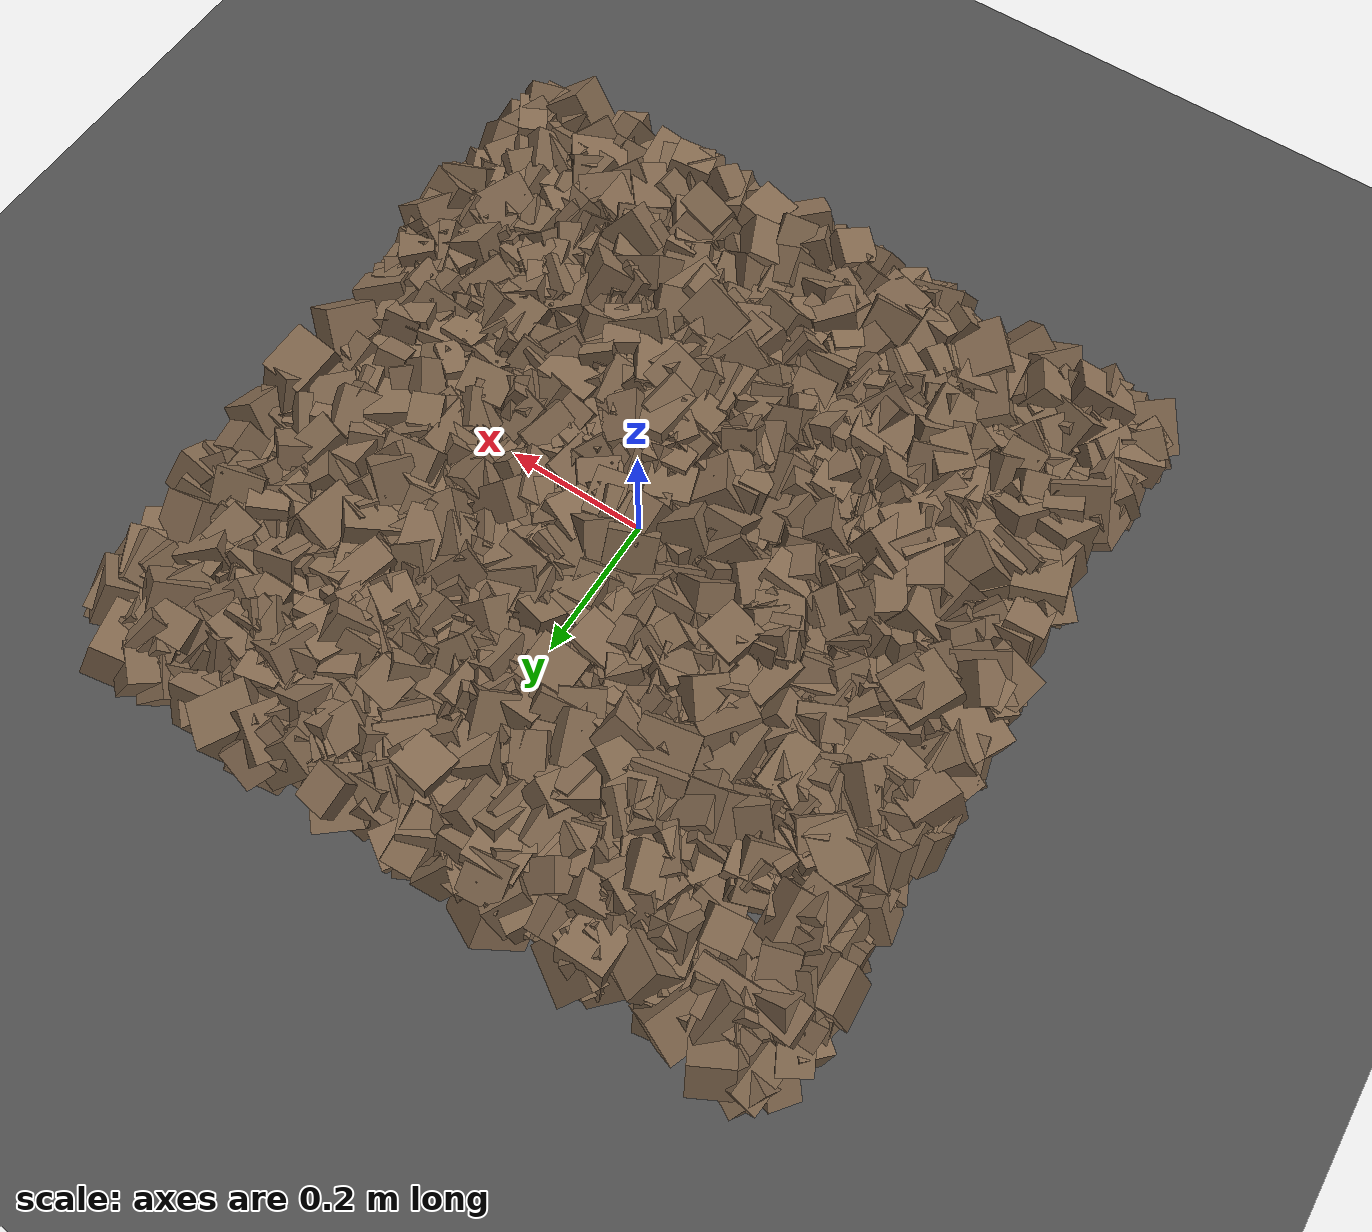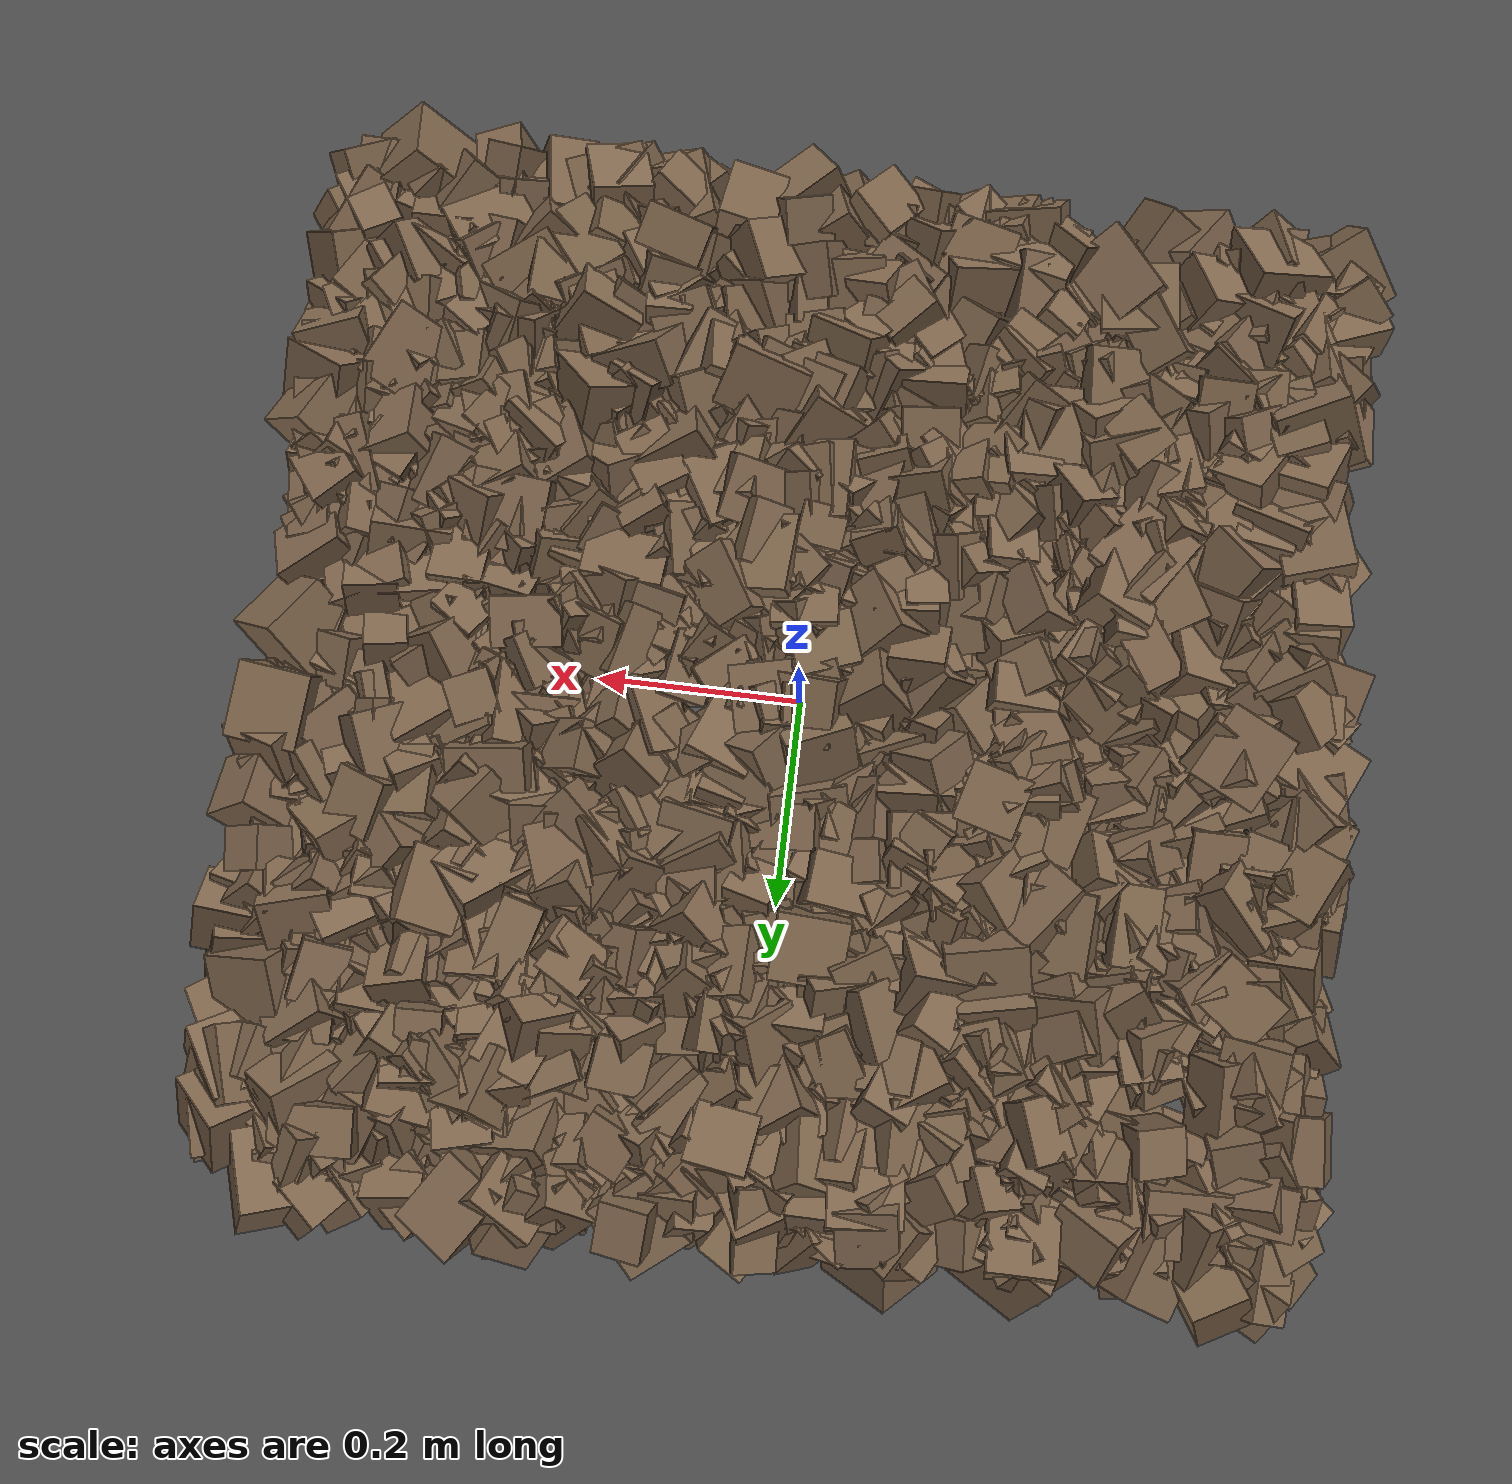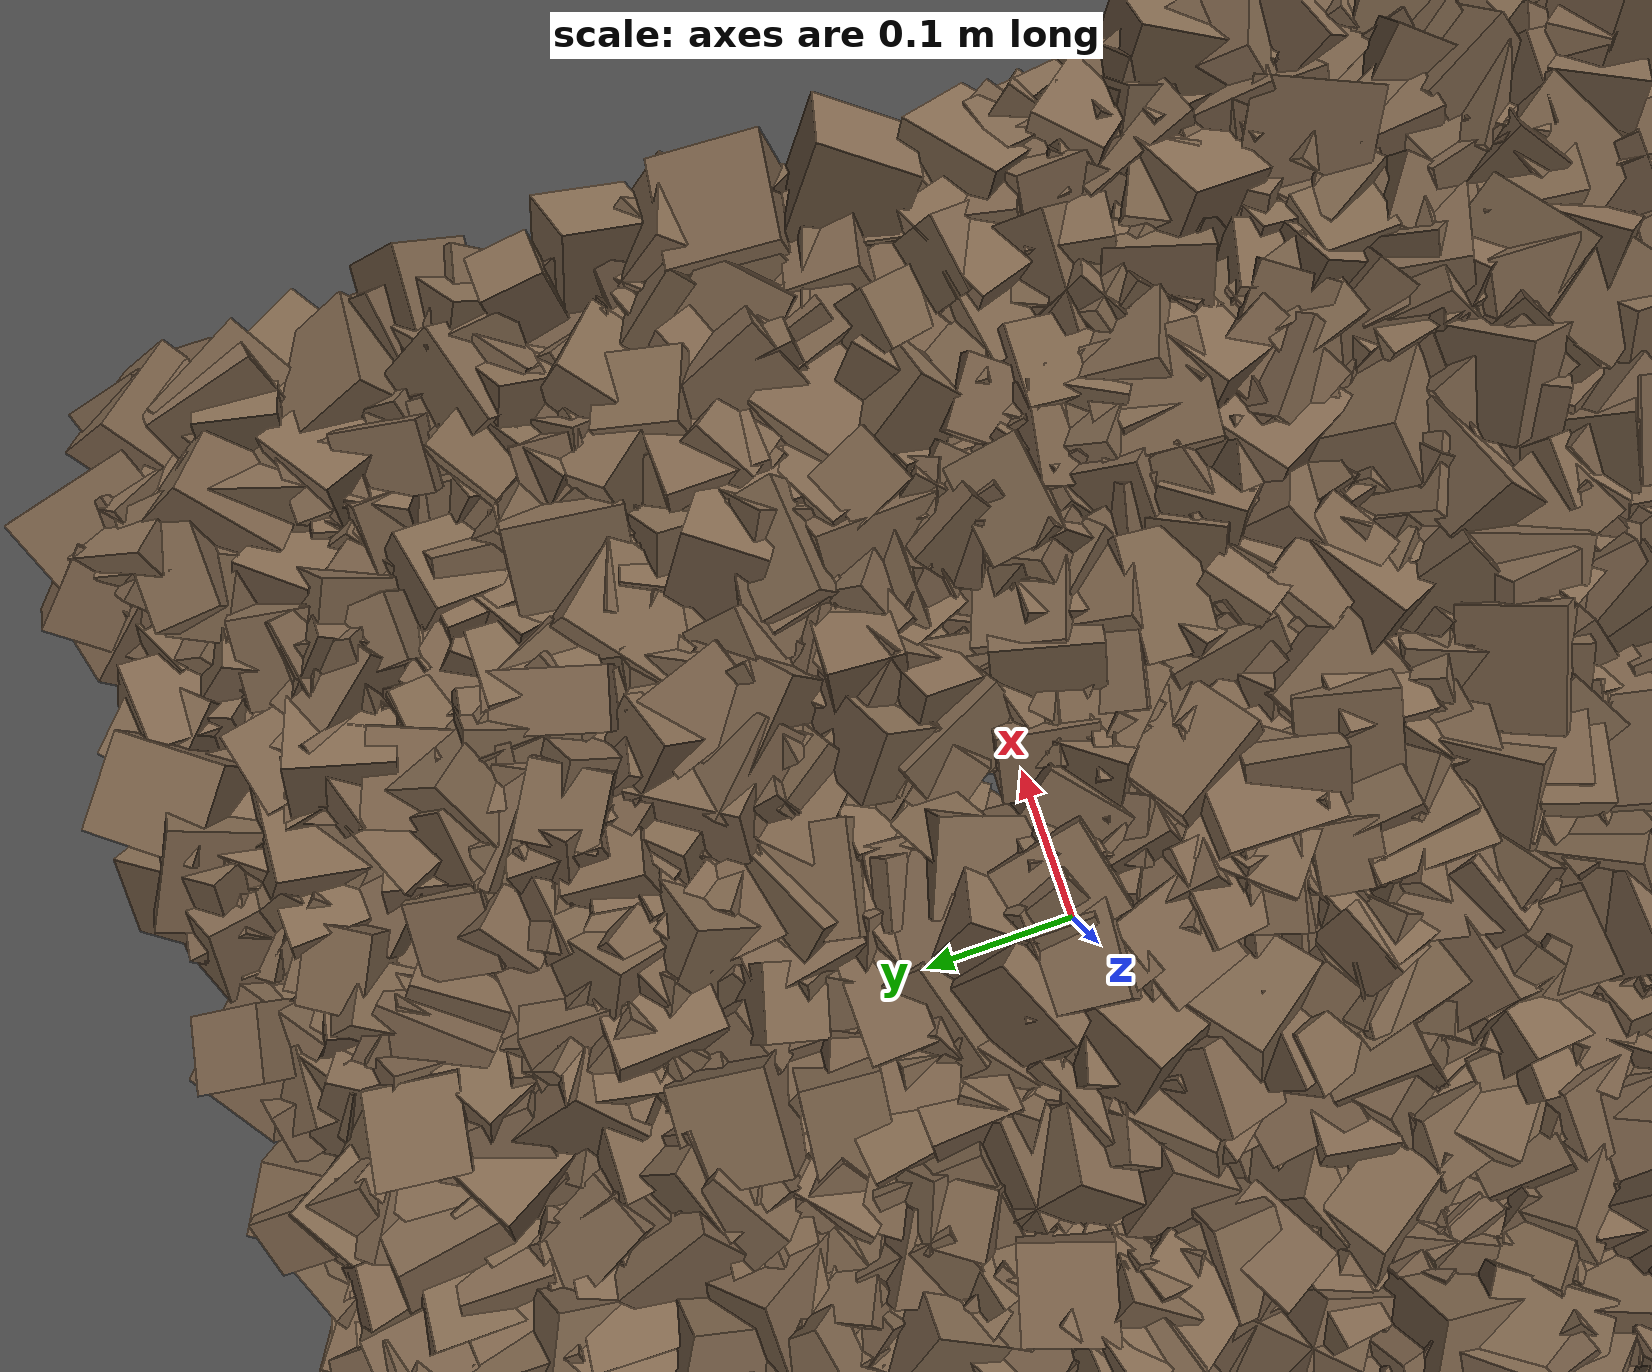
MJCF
<mujoco model="rocky_terrain_scene">
    <compiler angle="radian" inertiafromgeom="true" />
    <option timestep="0.002" gravity="0 0 -9.81" />

    <worldbody>
        <light name="sunlight" pos="5 5 5" dir="-1 -1 -1" diffuse="1 1 1" specular="0.5 0.5 0.5" ambient="0.5 0.5 0.5" />

        <geom name="ground_plane" type="plane" size="50 50 0.1" rgba="0.3 0.3 0.3 1" />

        <body name="rocky_terrain_body">

        <geom name="rock1" type="box" size="0.03943981332757949 0.033695724733858734 0.024831414577114776" pos="-0.4692392009074663 -0.4601244938146728 0.014623655185401017" quat="0.29231261165551037 0.30971306620716366 0.10104505634915883 0.29692926578816714" rgba="0.5 0.4 0.3 1" friction="0.72819568877111 0.9254128630155172 0.8711182556974334" /><geom name="rock2" type="box" size="0.03612312829066708 0.02393527752699128 0.039780571249520745" pos="0.28843800610864223 0.41613500318347496 0.01837712658325546" quat="0.17428715922670177 0.29759934704740154 0.09340378456499766 0.434709709160899" rgba="0.5 0.4 0.3 1" friction="0.7378186744933287 0.9903143023524315 0.8062845623579122" /><geom name="rock3" type="box" size="0.03514713216073676 0.036595120283122326 0.021233726942878596" pos="0.39239882636317325 0.4527147956746328 0.03313102207884192" quat="0.07671417688543666 0.21353584034682344 0.48862346956785135 0.2211265131998886" rgba="0.5 0.4 0.3 1" friction="0.7067784041165148 0.9155946604550798 0.8360899273865873" /><geom name="rock4" type="box" size="0.038425463977478515 0.02980331828332106 0.024695956426283736" pos="-0.22830090729706454 0.056393482698471775 0.02908686330647243" quat="0.09438307053450903 0.41195205753526 0.2071774138532317 0.28648745807699927" rgba="0.5 0.4 0.3 1" friction="0.7361815867996193 0.9408971264633308 0.7831837216959385" /><geom name="rock5" type="box" size="0.030810531450455834 0.024589423997582755 0.038833090894857855" pos="-0.473673980119486 0.1528105423614604 0.030182064031962164" quat="0.23118999908747728 0.22599692651430567 0.26073961258753625 0.2820734618106808" rgba="0.5 0.4 0.3 1" friction="0.6099398594785237 0.9519803329222787 0.9035564416239128" /><geom name="rock6" type="box" size="0.03562716599967017 0.037030817596800145 0.03129159036920903" pos="-0.2798532526519858 -0.0421779694385741 0.04086962580701446" quat="0.42807854844988075 0.22346824663368328 0.20181217573506993 0.14664102918136598" rgba="0.5 0.4 0.3 1" friction="0.6166374126967796 0.918347127831763 0.8277121255016191" /><geom name="rock7" type="box" size="0.03499331647097203 0.028341205949160606 0.03829136130145255" pos="0.41217686176605217 0.1667800791940599 0.022053123483437118" quat="0.15840453740405006 0.2344181605476272 0.2841933797444063 0.32298392230391637" rgba="0.5 0.4 0.3 1" friction="0.7986883481424769 0.9672652034789118 0.8052697067681229" /><geom name="rock8" type="box" size="0.02888914697522372 0.03864602624986822 0.025699115380130075" pos="0.32944460420594524 -0.4567651940018065 0.029525140186488733" quat="0.20304597896661797 0.6791963451774796 0.027013181442825454 0.09074449441307701" rgba="0.5 0.4 0.3 1" friction="0.8038630533945585 0.8696748576971222 0.8706598279595885" /><geom name="rock9" type="box" size="0.02758451339168579 0.023914126180496577 0.023179074047751547" pos="0.49248275339346914 0.45255788433906596 0.03382644603698512" quat="0.29444935149265095 0.15452861973347215 0.2530342236499652 0.2979878051239117" rgba="0.5 0.4 0.3 1" friction="0.7391321283335681 0.9779597092568405 0.840931001691056" /><geom name="rock10" type="box" size="0.024214237131492584 0.03244926479785863 0.03884678055806452" pos="-0.31330296476889596 0.06307996094103685 0.02686890129872238" quat="0.17359943130875408 0.25459011633725415 0.28529981357374806 0.28651063878024363" rgba="0.5 0.4 0.3 1" friction="0.7432361238138179 0.9114228837316877 0.7942065189778619" /><geom name="rock11" type="box" size="0.03773792979282587 0.03822168451156485 0.0307846187773323" pos="-0.0523560739357406 -0.318700361924955 0.036133676705842055" quat="0.3178530458738192 0.33715791170822496 0.3355581848438573 0.009430857574098499" rgba="0.5 0.4 0.3 1" friction="0.646137494277256 0.9906630881686049 0.9127260218857904" /><geom name="rock12" type="box" size="0.033177522932871545 0.029649536756863965 0.02219106299389209" pos="0.33375251117140614 0.294120405465655 0.022594224001738078" quat="0.2835306436523003 0.17722075080962668 0.07037323179229972 0.4688753737457733" rgba="0.5 0.4 0.3 1" friction="0.6969744722162649 0.8864891286404185 0.8437928399457525" /><geom name="rock13" type="box" size="0.02796872385727105 0.03684532474640079 0.030826536242615617" pos="0.06782185025546084 0.11280318341482853 0.020755579791537755" quat="0.3049113286027481 0.26494423846893833 0.4051078651410673 0.025036567787246278" rgba="0.5 0.4 0.3 1" friction="0.7982935980108921 0.9569899774036735 0.8010034144193011" /><geom name="rock14" type="box" size="0.022795786047594302 0.035652712886872065 0.035284422432927384" pos="-0.47703412639542975 0.18011094892793045 0.03679657432011541" quat="0.06596773265360388 0.548134674145279 0.04127100324010823 0.3446265899610088" rgba="0.5 0.4 0.3 1" friction="0.6981117681928091 0.9929225196273095 0.8680271232462206" /><geom name="rock15" type="box" size="0.027202607910461946 0.03305481618065628 0.03805923107086983" pos="-0.24789127738983874 0.4946565182233461 0.031985803940997835" quat="0.26863752569650123 0.36091984952893086 0.05579904639718225 0.31464357837738577" rgba="0.5 0.4 0.3 1" friction="0.8266407741196827 0.9805827373536021 0.9207338407919987" /><geom name="rock16" type="box" size="0.03472389816439009 0.038702887058449195 0.027379265845796207" pos="0.1819948216452426 -0.15371909518022797 0.030635479223651695" quat="0.4569556687088766 0.26621432022036357 0.1648268237254121 0.11200318734534777" rgba="0.5 0.4 0.3 1" friction="0.6565076738147688 0.9703050974462841 0.7977945596101804" /><geom name="rock17" type="box" size="0.02904132237833342 0.03660919193052213 0.029478954752305962" pos="-0.1944717482474435 0.07962323548393146 0.04853091218877642" quat="0.28015155086936655 0.29036135296501686 0.24369655382262484 0.18579054234299178" rgba="0.5 0.4 0.3 1" friction="0.6373956777481813 0.8724154859422912 0.9477235021926993" /><geom name="rock18" type="box" size="0.02680730714793748 0.0334302814379581 0.025829618314065394" pos="-0.24752644498557586 -0.15221448421814854 0.02620966688861013" quat="0.10375026843902511 0.3244158147016823 0.39179522639144515 0.18003869046784748" rgba="0.5 0.4 0.3 1" friction="0.6331678356968222 0.888892532541079 0.8082272687265893" /><geom name="rock19" type="box" size="0.03225674806540133 0.023302572464132105 0.037610288438407836" pos="0.07473497553588926 -0.3099959065491372 0.0392202017248015" quat="0.2571058116197894 0.35871983312730055 0.023400870388171003 0.36077348486473904" rgba="0.5 0.4 0.3 1" friction="0.8174012439406253 0.9334824585132724 0.926010333764944" /><geom name="rock20" type="box" size="0.021955791380283276 0.034412351571619246 0.022897157082324832" pos="-0.0025358692946225725 -0.03425320917115593 0.016807298448711667" quat="0.022747454308456993 0.14829929201008082 0.17297586222670566 0.6559773914547564" rgba="0.5 0.4 0.3 1" friction="0.649844331770035 0.9384734790016878 0.8342783285942302" /><geom name="rock21" type="box" size="0.0396742013868141 0.03245824519328973 0.037073122659276585" pos="0.385911813151679 0.09463248718922934 0.04143737292708486" quat="0.2908236290061906 0.10409391470141913 0.23981396013373024 0.36526849615866014" rgba="0.5 0.4 0.3 1" friction="0.7273943104146021 0.8559287712113901 0.8803047865730989" /><geom name="rock22" type="box" size="0.031976257285576445 0.023791890606422342 0.03096899636582328" pos="-0.3798363982008769 0.09129407138067924 0.035210447874336075" quat="0.06796748381676132 0.36324811100282467 0.19862570389171105 0.3701587012887029" rgba="0.5 0.4 0.3 1" friction="0.6311023557076088 0.8567935389591674 0.8870664042914597" /><geom name="rock23" type="box" size="0.02780731330339825 0.03448775533986739 0.027135882709524127" pos="-0.17634039770016652 -0.35901982100988694 0.043477776596161026" quat="0.32201169014085207 0.3152798552996348 0.16631001116034785 0.1963984433991653" rgba="0.5 0.4 0.3 1" friction="0.822141890171416 0.8892258491149642 0.9115200831397148" /><geom name="rock24" type="box" size="0.030799554097119604 0.03798194525245246 0.023183470857279613" pos="-0.13880604291896737 -0.14674027664913658 0.03989137570567571" quat="0.20151027435449323 0.2875762646467975 0.3865831294281317 0.12433033157057752" rgba="0.5 0.4 0.3 1" friction="0.7746965820437622 0.9906074386159177 0.7927931364955314" /><geom name="rock25" type="box" size="0.038188708148697466 0.039974956352358225 0.022969769271908767" pos="0.16638332888941787 -0.1655444351780878 0.039343644250240985" quat="0.08395935139437169 0.27288200404708307 0.31513828467248106 0.3280203598860641" rgba="0.5 0.4 0.3 1" friction="0.7413457858462568 0.9133748954493298 0.9042451080128252" /><geom name="rock26" type="box" size="0.02286737036669061 0.024685689258717548 0.03732399666788254" pos="-0.3255780716752257 -0.39212137900200983 0.014766490587882854" quat="0.29624064158123475 0.2817119870250156 0.2901090114305262 0.1319383599632234" rgba="0.5 0.4 0.3 1" friction="0.7194950216405996 0.9206082766222236 0.9110676244864826" /><geom name="rock27" type="box" size="0.027650239276545113 0.030987212148410513 0.027518414445771553" pos="0.21440959294127937 -0.152416668130956 0.046055396772023464" quat="0.2274210865759064 0.4850297477820465 0.2702302082332799 0.017318957408767103" rgba="0.5 0.4 0.3 1" friction="0.673491615440222 0.8752803036602566 0.8323584921343661" /><geom name="rock28" type="box" size="0.03035556721337085 0.02234294588677741 0.03910362584128956" pos="-0.28728892031620645 -0.2630017747341028 0.022700353696801304" quat="0.2003570325443219 0.195281644872941 0.54638970601017 0.057971616572567074" rgba="0.5 0.4 0.3 1" friction="0.7472391004495442 0.8822180847675999 0.9105005419028396" /><geom name="rock29" type="box" size="0.030472107795134307 0.022163772072034023 0.027319531940102268" pos="0.12360651457914884 -0.18868883791698499 0.03186793194060617" quat="0.2625019823012942 0.1437431832932685 0.2511429688511166 0.34261186555432077" rgba="0.5 0.4 0.3 1" friction="0.6690498092687749 0.8834760479718129 0.778725299097802" /><geom name="rock30" type="box" size="0.027389749071868984 0.021434238596996114 0.023720416774174847" pos="-0.12348618604803485 0.1908027172809289 0.011144752360808346" quat="0.35851956803956314 0.179899449680224 0.09658614933485578 0.36499483294535706" rgba="0.5 0.4 0.3 1" friction="0.6341315611526424 0.8783272871087371 0.7972325703682905" /><geom name="rock31" type="box" size="0.0290694098898693 0.039539640351323915 0.031731744247791085" pos="-0.44968198714066643 -0.24882158684933786 0.01741310353242729" quat="0.16885362577613935 0.22149769173123748 0.3691542130057178 0.24049446948690537" rgba="0.5 0.4 0.3 1" friction="0.7218892009666058 0.9993394148926604 0.869083572443536" /><geom name="rock32" type="box" size="0.026804353175896967 0.03623243125980577 0.025989248220441463" pos="0.15647316129795086 0.08386509972747758 0.04896671571178955" quat="0.3186895941343647 0.2961337919419895 0.01707225390589401 0.36810436001775176" rgba="0.5 0.4 0.3 1" friction="0.6929784828870291 0.8583855078414692 0.8627965926038016" /><geom name="rock33" type="box" size="0.03321053006664011 0.0361887540834106 0.03863468272085187" pos="-0.19507265233707505 0.3030012330865929 0.016360776556289328" quat="0.2827160145801645 0.1676124964887498 0.39841529381748236 0.1512561951136034" rgba="0.5 0.4 0.3 1" friction="0.6937887230131119 0.9482652025001936 0.7767428601858305" /><geom name="rock34" type="box" size="0.035336468403177466 0.020421942564163475 0.039744207294292705" pos="0.12004221922427472 -0.13848068897969923 0.040136990427875496" quat="0.31037193841841604 0.13448579081266257 0.19523183933751453 0.3599104314314069" rgba="0.5 0.4 0.3 1" friction="0.7655033931936466 0.8776028361479398 0.7562439730511668" /><geom name="rock35" type="box" size="0.037975197653184405 0.03688236969543462 0.025293703745997917" pos="-0.23327315942411686 -0.09663237569265537 0.018441261427819905" quat="0.15093808868774217 0.17038642386495048 0.26298589517283594 0.41568959227447133" rgba="0.5 0.4 0.3 1" friction="0.7712139039514789 0.8721732896131633 0.84523660830775" /><geom name="rock36" type="box" size="0.025642017308292242 0.03294963808823468 0.03586389968172409" pos="0.11149971586191476 -0.315225755521397 0.042659514705428815" quat="0.060728603800043815 0.38599753697334743 0.3988754038333822 0.15439845539322658" rgba="0.5 0.4 0.3 1" friction="0.8291085666340878 0.9812405474782319 0.8574233203899182" /><geom name="rock37" type="box" size="0.025690657345990825 0.03550056709948053 0.02602208588589753" pos="0.3302569164011805 0.44260184306751915 0.02335304752989885" quat="0.30379328727537414 0.31931586271095036 0.3573172611666574 0.019573588847018042" rgba="0.5 0.4 0.3 1" friction="0.8077531422586457 0.9444939273292504 0.8638693790582262" /><geom name="rock38" type="box" size="0.031462151336502264 0.03925026502602689 0.03499260700402314" pos="0.472758678933911 -0.3782271626280015 0.012813932739532184" quat="0.062305752591132475 0.4391893939894201 0.35418378168829295 0.14432107173115447" rgba="0.5 0.4 0.3 1" friction="0.7648344865234621 0.8580331300519158 0.8274364044039809" /><geom name="rock39" type="box" size="0.03373099400790622 0.03959525740747784 0.0391425464038994" pos="0.4052296814152182 -0.11841369388634493 0.01967986817574042" quat="0.1976729038743786 0.2291236071808468 0.3467411184986692 0.22646237044610545" rgba="0.5 0.4 0.3 1" friction="0.8361271854056422 0.92793320995783 0.8369286252305848" /><geom name="rock40" type="box" size="0.03433111439997228 0.03482692993303296 0.021411296742377645" pos="-0.19425975685528485 -0.3231529521004023 0.022841806993311523" quat="0.2864207729048091 0.16023036330547605 0.28993952604465456 0.26340933774506026" rgba="0.5 0.4 0.3 1" friction="0.8306514911866583 0.9189174391811499 0.8535147503613391" /><geom name="rock41" type="box" size="0.020387997504447405 0.024995485854638774 0.02071356655098494" pos="0.08366726393553747 0.0608719319220099 0.04721341382547109" quat="0.3993032585898902 0.3897729888437479 0.20906380630707166 0.0018599462592902081" rgba="0.5 0.4 0.3 1" friction="0.6925277676721021 0.979207246543446 0.7649770570378736" /><geom name="rock42" type="box" size="0.024943469389541617 0.02049453456723783 0.029134795849195226" pos="0.3994091388056531 0.43427402046473695 0.018612166484417596" quat="0.3966907910845006 0.22574900474577692 0.06069985334990258 0.31686035081981984" rgba="0.5 0.4 0.3 1" friction="0.6603503139857169 0.8606178485270546 0.9320662340309334" /><geom name="rock43" type="box" size="0.036734084548297595 0.024467560115007097 0.030508090874050466" pos="-0.1712139038569671 0.11869555950962052 0.030402126403843023" quat="0.06952873936070375 0.39572074564525417 0.21823631910984517 0.3165141958841969" rgba="0.5 0.4 0.3 1" friction="0.7887118035987093 0.937776919735234 0.8460156531844665" /><geom name="rock44" type="box" size="0.038093992184311684 0.021257254077014044 0.03462418772976331" pos="-0.25234280058216385 0.17786512801974463 0.037707758166269915" quat="0.299347303988213 0.20983985240800213 0.19462707663189321 0.2961857669718916" rgba="0.5 0.4 0.3 1" friction="0.6002216610885936 0.9469765910504523 0.8356836262347271" /><geom name="rock45" type="box" size="0.03235393609440549 0.03825047961026437 0.03329144704641818" pos="0.027996304896308666 -0.1746767907098824 0.025226783023059064" quat="0.3248146826959217 0.42822354057382256 0.031095728423277454 0.21586604830697845" rgba="0.5 0.4 0.3 1" friction="0.7861586604686402 0.9132906015442808 0.7685477656353505" /><geom name="rock46" type="box" size="0.034706766294502214 0.02743809665436909 0.03635526606466453" pos="0.1951065634234559 0.05188946914341608 0.030703256774561975" quat="0.264293357101698 0.4180737302909443 0.13241860605758338 0.18521430654977425" rgba="0.5 0.4 0.3 1" friction="0.7291401394427761 0.9392053384858847 0.7934346899422567" /><geom name="rock47" type="box" size="0.03709050209842393 0.03451395632009659 0.022444430006585026" pos="0.11345884410741591 -0.2458522297347444 0.03271013164868669" quat="0.029060412442748713 0.6845607448594565 0.19265065256212957 0.09372819013566519" rgba="0.5 0.4 0.3 1" friction="0.7257998526625845 0.9561146968819568 0.8986594260257549" /><geom name="rock48" type="box" size="0.02524921291938622 0.03789984945052574 0.02403472461035673" pos="-0.39232353023303757 -0.37251547743431745 0.026477016215719684" quat="0.3691748686006799 0.26113175366925806 0.0970183576290913 0.27267502010097083" rgba="0.5 0.4 0.3 1" friction="0.6550966932470439 0.9090278779630174 0.8004324427625028" /><geom name="rock49" type="box" size="0.03586931944129822 0.022117838234528862 0.03309522798621991" pos="0.17245284324465815 0.05353215660279498 0.0402654163400429" quat="0.5687816570841213 0.15925688977321467 0.21401875857990976 0.0579426945627542" rgba="0.5 0.4 0.3 1" friction="0.7664314641146732 0.9454910550669111 0.8078314232769916" /><geom name="rock50" type="box" size="0.03850495364517416 0.023165930284238696 0.03057647936132011" pos="0.30541704187558993 -0.2851032472223083 0.02221348942538666" quat="0.09374231788841138 0.3166104874380494 0.26174068170259496 0.3279065129709443" rgba="0.5 0.4 0.3 1" friction="0.7418929444880478 0.9630577113312354 0.8096965077348344" /><geom name="rock51" type="box" size="0.027234781980280662 0.0368049366027394 0.022805775503649758" pos="0.43413946467805686 0.3926954438191813 0.03353307594234236" quat="0.09742465568492405 0.6991721242003539 0.19280548653941434 0.010597733575307598" rgba="0.5 0.4 0.3 1" friction="0.6218980913396679 0.9860490461748241 0.8527027028038843" /><geom name="rock52" type="box" size="0.027199359048971333 0.03822381187685181 0.032572607834708556" pos="0.1890073907273242 0.4204054562714601 0.02988449826348724" quat="0.06981565889503404 0.4025693130624879 0.035897592663199744 0.4917174353792783" rgba="0.5 0.4 0.3 1" friction="0.8452900884563912 0.9724900126665184 0.8265207924300552" /><geom name="rock53" type="box" size="0.026262010721649583 0.028711149971106655 0.03589189023795228" pos="-0.2145249641156045 -0.2115951848576686 0.026669306955083454" quat="0.18589465696196708 0.29709572016607355 0.4080681661585974 0.10894145671336199" rgba="0.5 0.4 0.3 1" friction="0.65557178106018 0.8596652272433387 0.824737793098984" /><geom name="rock54" type="box" size="0.03318469183293271 0.03738469352424567 0.03756953472174393" pos="-0.15611035084048497 0.1506334795526323 0.031052760923145496" quat="0.2995509979210879 0.1329814377508297 0.2563002659044121 0.3111672984236703" rgba="0.5 0.4 0.3 1" friction="0.6133999209206665 0.908309042815207 0.8836203040599706" /><geom name="rock55" type="box" size="0.026988746335917156 0.03827389097474493 0.02132696283682336" pos="0.42146114158600645 0.23171575731954597 0.03408240619331401" quat="0.26127607407292786 0.19492501045041008 0.2016232296666363 0.3421756858100258" rgba="0.5 0.4 0.3 1" friction="0.6563617370752164 0.976744024570841 0.8046978109135887" /><geom name="rock56" type="box" size="0.028653944236833692 0.039303816737846144 0.03734027587839567" pos="-0.41862002625828887 -0.04233204001357538 0.021217454722500403" quat="0.13286173547585842 0.4571707302853366 0.011692440380593246 0.3982750938582116" rgba="0.5 0.4 0.3 1" friction="0.7545885413741757 0.9230921898989107 0.8331480583661448" /><geom name="rock57" type="box" size="0.03271583477248565 0.02473242389626888 0.02226029235525361" pos="0.20980444709251855 0.06576718563633677 0.027493120748862246" quat="0.1168554743959407 0.155201707730896 0.41440852099215886 0.31353429688100437" rgba="0.5 0.4 0.3 1" friction="0.7873653993433704 0.9029518493730122 0.9246678633212926" /><geom name="rock58" type="box" size="0.03612927084906266 0.02936000019269455 0.03608531921335931" pos="-0.15839053553640003 -0.13371833027687086 0.0245566461595932" quat="0.38308540800858726 0.07958018634390396 0.27417666848773464 0.2631577371597742" rgba="0.5 0.4 0.3 1" friction="0.6771780337838058 0.9340249800178406 0.8959684456487871" /><geom name="rock59" type="box" size="0.038853862070810735 0.031188153119047417 0.02149114320672237" pos="-0.42676541350080355 -0.443033351025899 0.012750088466227326" quat="0.1966297974412768 0.2782300798158534 0.38887024655489016 0.13626987618797956" rgba="0.5 0.4 0.3 1" friction="0.789298805978432 0.9680744235306293 0.8302535579232152" /><geom name="rock60" type="box" size="0.020601016261934443 0.03667376540218743 0.033543469269182044" pos="-0.17170126672030883 0.43767658327235237 0.047838638861966765" quat="0.2643832986366545 0.06763568311025805 0.18817428578035109 0.4798067324727365" rgba="0.5 0.4 0.3 1" friction="0.6381709051112596 0.8828725538602454 0.8971565940632313" /><geom name="rock61" type="box" size="0.030246784814703782 0.039401343355596224 0.024601824602851815" pos="0.19697873190236892 0.26594069871877823 0.04136838264634106" quat="0.29322720025479065 0.32857255990163575 0.026906712218579966 0.3512935276249936" rgba="0.5 0.4 0.3 1" friction="0.7517810401004692 0.9963241490402333 0.7854933190139914" /><geom name="rock62" type="box" size="0.031056134920415937 0.03163520388938105 0.027454136705551486" pos="0.3331830235540938 0.3034294686111877 0.03813305428625984" quat="0.3388016443742682 0.08834785817075033 0.41221940855918604 0.16063108889579533" rgba="0.5 0.4 0.3 1" friction="0.648952559654656 0.8834483072156084 0.7708985760345212" /><geom name="rock63" type="box" size="0.037689294609939354 0.03658574405382424 0.030451905198168726" pos="-0.17663444557107333 -0.3455448483889988 0.03771425333544393" quat="0.389175293786379 0.30090663229923215 0.29020656603309736 0.019711507881291408" rgba="0.5 0.4 0.3 1" friction="0.7735453664061851 0.9025731701330654 0.9307954294908727" /><geom name="rock64" type="box" size="0.03736204013929055 0.035522259088770665 0.034363976679299635" pos="-0.36511245242836576 -0.06716377743765167 0.04175282467555325" quat="0.24235010611332308 0.25077619540027896 0.13264440336219274 0.3742292951242052" rgba="0.5 0.4 0.3 1" friction="0.6095465570508027 0.8733351179975561 0.9067582020994345" /><geom name="rock65" type="box" size="0.02626850970616313 0.0310792777996668 0.02786421708382089" pos="0.49690610771886 0.2427570106288558 0.02494306698989629" quat="0.18303209509824603 0.37895474652025585 0.09883552438925718 0.339177633992241" rgba="0.5 0.4 0.3 1" friction="0.8254537428241295 0.9235189163845777 0.9156796063464963" /><geom name="rock66" type="box" size="0.027778432244128903 0.021031914849192788 0.023649559833998378" pos="-0.2817864544445884 0.30469170517711386 0.0180741163834391" quat="0.21764823346014206 0.4842731982328959 0.024025189422855975 0.2740533788841061" rgba="0.5 0.4 0.3 1" friction="0.8490988584338727 0.9057016102638338 0.8712245190472331" /><geom name="rock67" type="box" size="0.03297415490194557 0.02611839416448447 0.022807713704938046" pos="0.40566755513613006 0.2089032879549214 0.025106279431308588" quat="0.4362282656055508 0.3613755867303676 0.07105817613579711 0.13133797152828444" rgba="0.5 0.4 0.3 1" friction="0.6348067901836025 0.9478493218098583 0.8556398906647822" /><geom name="rock68" type="box" size="0.0219669270308852 0.021105721504746468 0.023440026867102642" pos="0.21874896544474132 -0.06660132122285778 0.042741486700222965" quat="0.39954021631737213 0.32157533565238167 0.24506811226781308 0.03381633576243313" rgba="0.5 0.4 0.3 1" friction="0.7807063760325281 0.9199315775453163 0.8796605448809967" /><geom name="rock69" type="box" size="0.02421120707023767 0.021609369570488958 0.03205765054877881" pos="0.12183701131657598 0.21343457923932452 0.03158111696429461" quat="0.2537040994171005 0.3295671988614473 0.17559558378637846 0.24113311793507375" rgba="0.5 0.4 0.3 1" friction="0.7876433233618465 0.9688527100967284 0.7664735159186532" /><geom name="rock70" type="box" size="0.03737156512268263 0.03806739516829701 0.02470796544409913" pos="0.22142937980984045 0.2172479727014469 0.024298733442428902" quat="0.4448458158405303 0.07696903847727896 0.01965834506288949 0.45852680061930123" rgba="0.5 0.4 0.3 1" friction="0.6223827479594513 0.9290146809656482 0.8548653334174807" /><geom name="rock71" type="box" size="0.03560487988560522 0.023981881783020267 0.029046626127986606" pos="0.30682989979997777 -0.0595249021615184 0.03012012855195525" quat="0.2707279213473821 0.2979282590593203 0.41966856553728016 0.01167525405601748" rgba="0.5 0.4 0.3 1" friction="0.6590116486147459 0.9878530008443823 0.8251889465071065" /><geom name="rock72" type="box" size="0.03215926337490533 0.03226198684873735 0.03083531868661363" pos="-0.4505151862923832 0.051904995624138084 0.014110194203840094" quat="0.38277936088011805 0.01823572040992158 0.46400718174661876 0.1349777369633416" rgba="0.5 0.4 0.3 1" friction="0.8456091347233847 0.8697111123908137 0.9096098501211716" /><geom name="rock73" type="box" size="0.03980524413042609 0.03415151346273522 0.03946819417685779" pos="0.05115009408285398 -0.12086456589969063 0.04839857113202104" quat="0.19218168759260187 0.3155716710791723 0.25395958209127434 0.2382870592369515" rgba="0.5 0.4 0.3 1" friction="0.8262987592147847 0.8865164387758897 0.7568514739092035" /><geom name="rock74" type="box" size="0.031911491325171265 0.03407673970951933 0.039170772146342375" pos="-0.24541978867623293 -0.40396928359136575 0.029878583808823286" quat="0.005709639641846935 0.17139626476055622 0.42454489205892415 0.3983492035386727" rgba="0.5 0.4 0.3 1" friction="0.6957595067165475 0.9728515661507924 0.8956637398375982" /><geom name="rock75" type="box" size="0.03464769273609132 0.030252135957116406 0.026825203985496548" pos="-0.108778783683387 -0.040734595589611344 0.04935318102615252" quat="0.14563948578016778 0.37247910404632556 0.14852833988943506 0.3333530702840716" rgba="0.5 0.4 0.3 1" friction="0.7979851270426859 0.9249012562048675 0.7579430501276879" /><geom name="rock76" type="box" size="0.031159264555705196 0.024000928516267794 0.025167083614861727" pos="0.03992812159615022 -0.4121205839278601 0.03453536247752549" quat="0.22774847946622498 0.13890142724354565 0.35677997766533276 0.27657011562489653" rgba="0.5 0.4 0.3 1" friction="0.7984835334098116 0.9592579881291498 0.9126896344772534" /><geom name="rock77" type="box" size="0.030802248592379605 0.02727780824957669 0.024238750515002343" pos="-0.38075805108242444 -0.12195565921608287 0.016275611376099054" quat="0.2784888781747558 0.086506657300163 0.4076781279169101 0.2273263366081712" rgba="0.5 0.4 0.3 1" friction="0.6123339396162735 0.8901519428910712 0.8936092204865818" /><geom name="rock78" type="box" size="0.02846510076949374 0.03154165258712068 0.025876055180024504" pos="0.4418456706038153 -0.37681016217003493 0.040221843378575574" quat="0.10052134765489225 0.24685387130847408 0.5073837749516759 0.14524100608495777" rgba="0.5 0.4 0.3 1" friction="0.7655522243668684 0.860351732421274 0.9280057289716582" /><geom name="rock79" type="box" size="0.02212535894400985 0.027242020312919724 0.021355102798818124" pos="-0.3183171882171867 0.08931458279353643 0.01794769477026803" quat="0.34069997496340537 0.3021489270653897 0.3540572930151313 0.0030938049560736034" rgba="0.5 0.4 0.3 1" friction="0.6540384218849961 0.890990347035048 0.9282029494418815" /><geom name="rock80" type="box" size="0.03962171866723478 0.02272810581327117 0.036240347516613314" pos="0.29178614190106567 0.02778438058990973 0.010009607442778732" quat="0.01500021562295935 0.19196341941551462 0.16779952028302006 0.6252368446785059" rgba="0.5 0.4 0.3 1" friction="0.7111446450918174 0.9886597613659764 0.9022161278218541" /><geom name="rock81" type="box" size="0.03731188736670586 0.02914815310352853 0.033207944719600244" pos="0.42250587233625025 -0.30964023967015597 0.016538923919539664" quat="0.28263950528914406 0.14935097169365208 0.1821267354799799 0.385882787537224" rgba="0.5 0.4 0.3 1" friction="0.7363459430388044 0.9006330659993701 0.9496695066401277" /><geom name="rock82" type="box" size="0.03745772909046162 0.037599157444029974 0.03789338478501282" pos="-0.31164507043286316 -0.1678202572883113 0.045421299682266755" quat="0.6255762541659006 0.03405658671492559 0.01381811821541315 0.32654904090376063" rgba="0.5 0.4 0.3 1" friction="0.765033768881245 0.9855325863462775 0.8622766890459268" /><geom name="rock83" type="box" size="0.02196232658306902 0.027040311054337393 0.038019420323767025" pos="-0.2806391683378311 -0.08882762564122393 0.027846341642252255" quat="0.04506927177288402 0.2731129164924464 0.24360229716284823 0.4382155145718213" rgba="0.5 0.4 0.3 1" friction="0.6430948510807111 0.9823814415998463 0.8864059471704488" /><geom name="rock84" type="box" size="0.030932908133482616 0.03087568961811045 0.022991047490702892" pos="0.06998016821516506 -0.49744901045605616 0.028174668176632334" quat="0.44272415745967003 0.27753916543156965 0.02836646129946148 0.2513702158092989" rgba="0.5 0.4 0.3 1" friction="0.7245250011368365 0.923297221160932 0.7874251377482457" /><geom name="rock85" type="box" size="0.03351081960370597 0.03633710027270518 0.030278096924035856" pos="0.29464868166931213 0.1580292185249399 0.016668780087471614" quat="0.2523021643559337 0.2187019205865307 0.21848727636057483 0.31050863869696066" rgba="0.5 0.4 0.3 1" friction="0.6320095262743501 0.9689208444556286 0.9222480043884838" /><geom name="rock86" type="box" size="0.025135022585848772 0.031706229041040083 0.03961724136392567" pos="-0.13343849685757503 0.38038356480919466 0.01893016557950022" quat="0.17141278234581894 0.2837114324597965 0.23121421651501578 0.3136615686793688" rgba="0.5 0.4 0.3 1" friction="0.6080643134297096 0.8581496226162858 0.7614988255671705" /><geom name="rock87" type="box" size="0.033436869917878684 0.03813888805628838 0.027247228112702325" pos="-0.06319515643080564 -0.3744531078630855 0.021156246522460405" quat="0.013327179414190192 0.32727758550600833 0.2827965697180376 0.376598665361764" rgba="0.5 0.4 0.3 1" friction="0.6657478151705175 0.8954458262098663 0.8430175268718304" /><geom name="rock88" type="box" size="0.03254282146981863 0.033457047799909434 0.023143355894983963" pos="0.0216893233513048 0.036516220318586035 0.04114225926011445" quat="0.40023678217205877 0.11235652640645984 0.3009140725985308 0.18649261882295057" rgba="0.5 0.4 0.3 1" friction="0.731468452021248 0.9127142655485627 0.9216175559831978" /><geom name="rock89" type="box" size="0.039438443175654286 0.033540680424060755 0.025895335255555173" pos="0.24867035033003682 -0.35084795844843186 0.03432148593666895" quat="0.25503218738452466 0.1361194123978118 0.26316514422775583 0.3456832559899076" rgba="0.5 0.4 0.3 1" friction="0.7836577967433549 0.9860719468766069 0.9287938507541523" /><geom name="rock90" type="box" size="0.038769776625075913 0.02127841416072944 0.02685205364539952" pos="0.44074565869028237 0.2868185507067077 0.028928679755679622" quat="0.11823287793327801 0.25912832920752665 0.10550073802086482 0.5171380548383305" rgba="0.5 0.4 0.3 1" friction="0.754315649075821 0.9537340797853421 0.7539366412358695" /><geom name="rock91" type="box" size="0.03379262050834089 0.0242938777947363 0.021429470567301455" pos="0.3452984506436445 0.3338275697394666 0.01857169333956752" quat="0.26305682917375883 0.00655796012057128 0.48218066757460964 0.2482045431310602" rgba="0.5 0.4 0.3 1" friction="0.7925514232345987 0.9646482356201407 0.8037105521353431" /><geom name="rock92" type="box" size="0.037104586744470196 0.032629564994270444 0.03386007014621362" pos="0.2915022351179941 0.05436576723337072 0.010232185392761996" quat="0.14170673081191415 0.48882546623275674 0.004055842558940334 0.3654119603963888" rgba="0.5 0.4 0.3 1" friction="0.6385144173055465 0.9250973353869534 0.7511205645026032" /><geom name="rock93" type="box" size="0.024544019642159846 0.02315258745772149 0.029881472470193793" pos="0.4995683213625367 0.1471107129874627 0.021151402591020548" quat="0.3100381735500591 0.25293491355660835 0.16443405207589412 0.27259286081743844" rgba="0.5 0.4 0.3 1" friction="0.7316687995917867 0.968121097286913 0.8893785905933932" /><geom name="rock94" type="box" size="0.0351581418698136 0.03348021235902565 0.0357008785744701" pos="0.03157086170291834 -0.23820462201599935 0.023759668257287703" quat="0.3141814401928902 0.022378102154707116 0.39046336552509114 0.27297709212731147" rgba="0.5 0.4 0.3 1" friction="0.6704735319943578 0.9107772138031831 0.9357035765050079" /><geom name="rock95" type="box" size="0.025493433025680003 0.027587004151275955 0.0291584140078368" pos="-0.157337536685631 0.20429359098574829 0.03379879969849525" quat="0.46664123096716426 0.3250426872418616 0.15526170425627675 0.0530543775346975" rgba="0.5 0.4 0.3 1" friction="0.7330103936013886 0.8774047244795388 0.9292641065541538" /><geom name="rock96" type="box" size="0.020000345638636848 0.03974557688080052 0.0389143369956244" pos="-0.42203310020052076 -0.3384285112058494 0.023865997725545714" quat="0.23399477592249932 0.1243562552100035 0.25479255548927954 0.3868564133782177" rgba="0.5 0.4 0.3 1" friction="0.8366042729651131 0.9779463351683744 0.7591155429122789" /><geom name="rock97" type="box" size="0.029780699966814775 0.021215562743386637 0.022808172439034782" pos="0.36843824789249746 0.33945485203659986 0.02794741319264231" quat="0.17160573348642236 0.5180123160167291 0.09052966075581735 0.21985228974103116" rgba="0.5 0.4 0.3 1" friction="0.7507795038815835 0.8906891127424879 0.76382629069344" /><geom name="rock98" type="box" size="0.024599645732218376 0.026176541709297892 0.03188508376674659" pos="-0.4359907171317797 -0.15632679319472442 0.017623297304358215" quat="0.008568088542622471 0.06889984117320226 0.3736377868925976 0.5488942833915778" rgba="0.5 0.4 0.3 1" friction="0.7804175675205441 0.866417557210092 0.7729082307394158" /><geom name="rock99" type="box" size="0.025670239266429633 0.03422165162927079 0.02867220466479809" pos="-0.32568803110659794 0.232389755753589 0.028486532454177246" quat="0.32609064110648384 0.1911175816278056 0.2961348961720302 0.18665688109368045" rgba="0.5 0.4 0.3 1" friction="0.7236427725266735 0.8988936981625641 0.8466249568928107" /><geom name="rock100" type="box" size="0.03309753829780453 0.029376934723663123 0.0390909519238266" pos="0.015195676746915465 -0.34689344163082214 0.026911328895227606" quat="0.4121674220449968 0.03140545524803049 0.07466912860756557 0.48175799409940717" rgba="0.5 0.4 0.3 1" friction="0.6256112286442275 0.9692203748430044 0.9475908954739073" /><geom name="rock101" type="box" size="0.021226369793859973 0.03645085167499648 0.0350262892057574" pos="0.2512601316292675 -0.07567409876371323 0.02221568286987719" quat="0.20853486002157917 0.22796829760161094 0.4416505568412181 0.12184628553559174" rgba="0.5 0.4 0.3 1" friction="0.7792822250156652 0.8742329596562806 0.8396914723618557" /><geom name="rock102" type="box" size="0.03388188098092203 0.03883144541423416 0.027862312895339268" pos="-0.041659529055020794 -0.3626686755351094 0.032685121761943596" quat="0.09454068785953716 0.4280993146600902 0.032079920816949895 0.4452800766634227" rgba="0.5 0.4 0.3 1" friction="0.7465712849244552 0.8974812775932555 0.7774336957710308" /><geom name="rock103" type="box" size="0.026596187806313953 0.03957862817332296 0.029866778784672053" pos="0.23605899362765148 -0.17822633732875426 0.02892593147987607" quat="0.2174079360149929 0.34822398941457294 0.14361112513666163 0.29075694943377256" rgba="0.5 0.4 0.3 1" friction="0.6164743321979907 0.8829721067815297 0.9062726375061081" /><geom name="rock104" type="box" size="0.030544084304442103 0.030839368883026512 0.030636777279373695" pos="-0.3601811877965341 0.29601860418748294 0.01134341750015777" quat="0.2766865938935358 0.09825889377785295 0.3732915639219491 0.2517629484066622" rgba="0.5 0.4 0.3 1" friction="0.68785027965428 0.8618132314524706 0.8971349822735932" /><geom name="rock105" type="box" size="0.02581344364241505 0.024517803444000896 0.03061027660807577" pos="0.22637755573984475 -0.12024035087359786 0.012489493053396439" quat="0.4264394669910937 0.28744435694119086 0.0032138042283451247 0.2829023718393703" rgba="0.5 0.4 0.3 1" friction="0.7230478271293553 0.9759089291343744 0.9327816596209277" /><geom name="rock106" type="box" size="0.03455948282615676 0.0391503191753479 0.03437646714947544" pos="0.4923531881018356 -0.3885228639227144 0.024198451509232194" quat="0.3373601771239848 0.07714600310399948 0.26968262904806123 0.3158111907239545" rgba="0.5 0.4 0.3 1" friction="0.6153613141683089 0.8863421948875989 0.9210876076872594" /><geom name="rock107" type="box" size="0.0379155763142221 0.03055188399424633 0.0290677438553135" pos="0.04744973736622482 0.2919878584902301 0.03205417463659844" quat="0.05818954366091674 0.586870899629491 0.18205955388465553 0.1728800028249367" rgba="0.5 0.4 0.3 1" friction="0.6437669743216988 0.9427526585856401 0.8131153231097131" /><geom name="rock108" type="box" size="0.028186467640167197 0.029276357637238973 0.02834772200897835" pos="-0.005450435904395423 -0.41809041197575414 0.041158972614935466" quat="0.589986532117276 0.33673317308037565 0.016262481974499764 0.05701781282784858" rgba="0.5 0.4 0.3 1" friction="0.8454953273846192 0.8779246632830999 0.8673565250825711" /><geom name="rock109" type="box" size="0.03864643600462005 0.022870845279569407 0.022466086214292847" pos="0.23817165472831225 0.16454287800199519 0.013987162944491906" quat="0.18240822048716418 0.36313160288498014 0.011016372334613932 0.4434438042932417" rgba="0.5 0.4 0.3 1" friction="0.6013822341887625 0.9390490357651946 0.9185063683162695" /><geom name="rock110" type="box" size="0.021971150472854764 0.03485246219496721 0.033509565533304496" pos="-0.3087368586594197 -0.396028841852608 0.049903881926638825" quat="0.42871637015010067 0.3466012005063039 0.20354309879605428 0.02113933054754121" rgba="0.5 0.4 0.3 1" friction="0.673883465509066 0.9283772154827757 0.7731097478088522" /><geom name="rock111" type="box" size="0.02424795275861052 0.020358328134831984 0.02576764703425361" pos="0.13521806716620233 -0.4993629615030183 0.010053146142511111" quat="0.1173033555822006 0.09756179734655586 0.6665754248530288 0.11855942221821475" rgba="0.5 0.4 0.3 1" friction="0.6779798346895946 0.9884135788347446 0.7752492353650113" /><geom name="rock112" type="box" size="0.03703489481308299 0.037870376672034974 0.029773963592463135" pos="0.4339347278368747 0.049976844705701184 0.027949284291911194" quat="0.054019297592339297 0.48306370013656486 0.4488159109371848 0.014101091333910997" rgba="0.5 0.4 0.3 1" friction="0.8202487948339141 0.8895648739131399 0.824701308607757" /><geom name="rock113" type="box" size="0.039885755601552594 0.03413331528959455 0.03114682642316846" pos="0.4167709260075372 -0.220639239571234 0.02659192135587489" quat="0.10402262321583347 0.30232749310020063 0.31630132620804063 0.27734855747592524" rgba="0.5 0.4 0.3 1" friction="0.7296518327985164 0.9133290259737333 0.8783198072218372" /><geom name="rock114" type="box" size="0.02720642096705024 0.033994539523724075 0.035676620578610846" pos="-0.10095656548827059 0.18423999818555326 0.02498841126699005" quat="0.2706463396156495 0.4489171273587916 0.2048789137404207 0.07555761928513823" rgba="0.5 0.4 0.3 1" friction="0.6497135693444683 0.9338296019137295 0.7832640095731828" /><geom name="rock115" type="box" size="0.034373078931299914 0.020882444858156556 0.039037840863180656" pos="-0.2781211951402549 0.31415829936546025 0.01868339101200319" quat="0.32119126042523904 0.2236982428548863 0.03261204780142517 0.4224984489184495" rgba="0.5 0.4 0.3 1" friction="0.6950751651176398 0.856938107656143 0.7720496771564298" /><geom name="rock116" type="box" size="0.02350714366439751 0.025657928890132572 0.03601937794497964" pos="-0.25749399877698187 0.09348805131899807 0.04272236565659203" quat="0.033150908623304574 0.09234869791858044 0.4660296412365806 0.4084707522215345" rgba="0.5 0.4 0.3 1" friction="0.6130430150747018 0.9776295620780973 0.8210475929622969" /><geom name="rock117" type="box" size="0.03000367491305584 0.0381830489544725 0.02383069421702275" pos="0.16854535442216034 -0.12698545709354359 0.025630162945536" quat="0.03187223857194364 0.42260941838235155 0.07888105600580249 0.4666372870399024" rgba="0.5 0.4 0.3 1" friction="0.6999239793629061 0.9836598617759484 0.9222166371729168" /><geom name="rock118" type="box" size="0.02669354207324218 0.021553078877688873 0.038874448435201575" pos="0.35763333654336527 -0.3823054413962703 0.027588763936949964" quat="0.18985045256269803 0.10464873647667315 0.4520713602383902 0.2534294507222386" rgba="0.5 0.4 0.3 1" friction="0.6113081113607548 0.8773910030066255 0.8255479967292327" /><geom name="rock119" type="box" size="0.030656208513337026 0.033599819463269405 0.024728450984414924" pos="0.27405749984346395 -0.00866084685300561 0.03969261652632701" quat="0.019854884432953468 0.6065010317492058 0.26950917784999084 0.10413490596784991" rgba="0.5 0.4 0.3 1" friction="0.8252010411782424 0.928949815279663 0.7517631751454993" /><geom name="rock120" type="box" size="0.025762442626378463 0.038753641756708965 0.023577822997523028" pos="-0.15104396325950564 -0.25110736266329714 0.045431772821390166" quat="0.2316863669525827 0.06851936299238713 0.06118659062109731 0.6386076794339328" rgba="0.5 0.4 0.3 1" friction="0.6792674705129096 0.9779771295314501 0.797267450238697" /><geom name="rock121" type="box" size="0.03529288425097615 0.02610631851352677 0.027668323374424816" pos="0.19192790028301387 0.2726599204669289 0.022707542441039473" quat="0.05685310643288955 0.3928227622252214 0.22118656442854198 0.32913756691334717" rgba="0.5 0.4 0.3 1" friction="0.7848505087873169 0.8683861794555495 0.7882303767512387" /><geom name="rock122" type="box" size="0.02300041793324162 0.02417703199168116 0.038409502364903106" pos="0.14844506970336135 -0.007202678002103946 0.02842790804060779" quat="0.32775932371373884 0.10932281578584968 0.2713736041865043 0.29154425631390724" rgba="0.5 0.4 0.3 1" friction="0.7427919806258295 0.8735582070368706 0.8319784764607501" /><geom name="rock123" type="box" size="0.021570108447099466 0.030956926268069843 0.027463047206376677" pos="-0.35013746109834 -0.4212190384996749 0.04132915139482233" quat="0.11430071233479053 0.10186097594988189 0.35127499462719675 0.43256331708813095" rgba="0.5 0.4 0.3 1" friction="0.7091815219062279 0.9191656213130337 0.7539339351235812" /><geom name="rock124" type="box" size="0.024714059297106586 0.02825962725201133 0.027340340432997694" pos="0.25963115601577846 0.3366064052241772 0.012177986411811342" quat="0.34504069815041705 0.1387629932158001 0.3704501761507889 0.14574613248299406" rgba="0.5 0.4 0.3 1" friction="0.8313582326488639 0.8740912810915766 0.856958641976072" /><geom name="rock125" type="box" size="0.03708325638739042 0.02933080455433566 0.030461735149606463" pos="-0.3164934823955353 0.21955437920088405 0.018931172828662704" quat="0.035890690564560075 0.026580541999078493 0.40223026027204134 0.5352985071643201" rgba="0.5 0.4 0.3 1" friction="0.8024628687389965 0.8880081550962999 0.895576713201465" /><geom name="rock126" type="box" size="0.023608015514239418 0.021370677145526058 0.03363824903793226" pos="-0.17922666165895862 0.196972743274893 0.04321708321554525" quat="0.09995576042212222 0.15556700889037567 0.37903060507866904 0.3654466256088331" rgba="0.5 0.4 0.3 1" friction="0.7889534002564468 0.9475399979821437 0.8784112394807796" /><geom name="rock127" type="box" size="0.02135103434519625 0.0210714211284657 0.02147686856092579" pos="-0.12953541237468602 -0.1619320015964112 0.03341097655635745" quat="0.02874701917407366 0.3715816318952249 0.3168461841364631 0.28282516479423836" rgba="0.5 0.4 0.3 1" friction="0.8160536037962661 0.906514549421113 0.912494965935237" /><geom name="rock128" type="box" size="0.024965921379191014 0.024804213312230733 0.02463194725388815" pos="-0.445512787849225 -0.2821458471890591 0.039905826354698574" quat="0.048519242551081414 0.007115579583248133 0.42500255009252164 0.5193626277731487" rgba="0.5 0.4 0.3 1" friction="0.7549968084332962 0.9196714052976221 0.8032359667248231" /><geom name="rock129" type="box" size="0.02404594639914297 0.024094200073265182 0.03330016432353178" pos="0.2449642912864506 0.04746707077403045 0.036381475042603334" quat="0.316988977080627 0.1822366594032215 0.2527550083122011 0.24801935520395044" rgba="0.5 0.4 0.3 1" friction="0.7572331106346062 0.855082472871118 0.7509597147229137" /><geom name="rock130" type="box" size="0.024807257263889628 0.03991770900953753 0.038643167410882306" pos="0.061868494687223774 0.43381148093460886 0.014434713861842249" quat="0.26377358258000655 0.13977253924825078 0.3689990675041822 0.22745481066756054" rgba="0.5 0.4 0.3 1" friction="0.64528010254045 0.9983404255341082 0.9342851783616852" /><geom name="rock131" type="box" size="0.02773152095067651 0.03190012146548586 0.03559543233683985" pos="0.4367205619860174 0.34172647123718203 0.018172086749847945" quat="0.30384591739181077 0.4287925087653299 0.09032946262138494 0.17703211122147425" rgba="0.5 0.4 0.3 1" friction="0.6699121727825663 0.9020130808469662 0.8112403127352987" /><geom name="rock132" type="box" size="0.03366583098318916 0.02178048516189753 0.029141207461326566" pos="-0.35099730434679355 0.2906204598838109 0.038613245806124116" quat="0.22202915873530357 0.2229694754920977 0.2383353532327528 0.316666012539846" rgba="0.5 0.4 0.3 1" friction="0.724012993083135 0.9952586557463183 0.767142974043008" /><geom name="rock133" type="box" size="0.028364695622591272 0.02155253547560338 0.023615352226693257" pos="0.41039879120318445 0.03498855743774676 0.04988530903155721" quat="0.2078436013324101 0.20853644488782777 0.3010626461389571 0.28255730764080506" rgba="0.5 0.4 0.3 1" friction="0.7605217113008271 0.8784729010158983 0.884163323156747" /><geom name="rock134" type="box" size="0.028229535880941903 0.022610849135947044 0.02201984502962675" pos="-0.12364434520606016 0.2563054248010622 0.025686066923399226" quat="0.3304275492672026 0.24194284517959552 0.2858031315347615 0.14182647401844045" rgba="0.5 0.4 0.3 1" friction="0.8072271269230449 0.9697294623201658 0.8952551601346854" /><geom name="rock135" type="box" size="0.03026277278026037 0.03656726194412382 0.03838492339136124" pos="-0.4910056405544496 0.3642056191733385 0.03732089257937655" quat="0.20109029909660778 0.2854767092351979 0.3076018058854558 0.20583118578273854" rgba="0.5 0.4 0.3 1" friction="0.8045742326130603 0.9130251472740256 0.8933244250563228" /><geom name="rock136" type="box" size="0.020461367935265196 0.02441522651266967 0.03588757867146919" pos="0.1280544433569355 0.10839796618354658 0.01767088074219818" quat="0.36022516476396055 0.15342927038805415 0.1463865697337674 0.33995899511421784" rgba="0.5 0.4 0.3 1" friction="0.7454727226422988 0.8692315087097049 0.918968328000952" /><geom name="rock137" type="box" size="0.038703554869216145 0.03188067953963263 0.030755877534912268" pos="0.3013638114361311 -0.11513683014810527 0.035026403992113646" quat="0.035537758716376676 0.8683370115647938 0.029898574823863076 0.06622665489496643" rgba="0.5 0.4 0.3 1" friction="0.7035916897519644 0.9167781974297576 0.8344564780219309" /><geom name="rock138" type="box" size="0.021363014169924442 0.02316209492862769 0.03956141360545333" pos="0.031086202058052237 0.30721525867289956 0.02729221031772753" quat="0.28353864349027147 0.1651277349367405 0.29172906613448 0.25960455543850797" rgba="0.5 0.4 0.3 1" friction="0.6811902974779902 0.9385764256160553 0.7966755454348526" /><geom name="rock139" type="box" size="0.021856008077995613 0.025179756962979125 0.03779209143317358" pos="0.18973986912589247 -0.21101708505228234 0.04096474596112722" quat="0.20170911990150667 0.04053472867465673 0.46478822057671154 0.2929679308471251" rgba="0.5 0.4 0.3 1" friction="0.7529486725008046 0.9338217068522758 0.9215400608821693" /><geom name="rock140" type="box" size="0.02832658073402083 0.021972947810145655 0.038385140493305374" pos="-0.3874503890977078 -0.13872130925264248 0.03484462760067794" quat="0.25008373055115185 0.3961544199693054 0.11346199224750018 0.24029985723204253" rgba="0.5 0.4 0.3 1" friction="0.8128409980022515 0.9889538901177091 0.7896903150143468" /><geom name="rock141" type="box" size="0.028203944929961342 0.029443244842613743 0.020765551058991853" pos="-0.3419422912236658 -0.3436664694072672 0.03224120251388939" quat="0.21156309203226367 0.37924861380333774 0.18392778426828343 0.2252605098961152" rgba="0.5 0.4 0.3 1" friction="0.7904658977580639 0.8773491449028855 0.7565125044253772" /><geom name="rock142" type="box" size="0.034060757772441864 0.031441170506010564 0.02980137654124406" pos="-0.07733475485541619 0.46198471326454904 0.040885012619641704" quat="0.15414481716554015 0.3560173656025742 0.18769267337352052 0.3021451438583652" rgba="0.5 0.4 0.3 1" friction="0.6173479481081968 0.9197368776345523 0.8747559737522077" /><geom name="rock143" type="box" size="0.023015864903038637 0.03715635155422984 0.03731246362782305" pos="-0.1632781852874774 0.3107373154616482 0.023998279934775414" quat="0.34127721703725084 0.20492140139936432 0.42044540003166664 0.033355981531718176" rgba="0.5 0.4 0.3 1" friction="0.8010255149339579 0.9451871332702986 0.8512813139711738" /><geom name="rock144" type="box" size="0.038704640115545696 0.0201848634781902 0.03421923502065138" pos="-0.011907549987789534 -0.07552074547297616 0.03408778185422624" quat="0.2097028700712776 0.5165735101068966 0.04556095469629734 0.22816266512552857" rgba="0.5 0.4 0.3 1" friction="0.6284535969019809 0.8541656898013027 0.9137514734468151" /><geom name="rock145" type="box" size="0.0278477439268612 0.031050635750547582 0.03351455685960801" pos="-0.39809107059286275 -0.452878687015312 0.01836337116360473" quat="0.2429581013887849 0.22606801571215399 0.5152396524374027 0.015734230461658387" rgba="0.5 0.4 0.3 1" friction="0.8276923508850154 0.941502264729191 0.9299933658310424" /><geom name="rock146" type="box" size="0.03784408675866188 0.034603453946506615 0.029593482544852116" pos="-0.19454449338290702 -0.3416545258925575 0.036378811986438504" quat="0.2932115235364126 0.11494047509507126 0.4054591692920291 0.1863888320764871" rgba="0.5 0.4 0.3 1" friction="0.8263546908713308 0.981305473819001 0.8556541536032343" /><geom name="rock147" type="box" size="0.029806741549317336 0.03730533086182973 0.029865521723340144" pos="-0.03201800800778065 0.40712173723521083 0.012863804612996712" quat="0.38762539434352045 0.22984791017478226 0.1433276059396099 0.23919908954208735" rgba="0.5 0.4 0.3 1" friction="0.8244901318413537 0.8931413909132261 0.9184958060087309" /><geom name="rock148" type="box" size="0.024645843190665026 0.02130048090426179 0.03085028172371053" pos="-0.3013752822040151 -0.13050621505496873 0.025895417603016467" quat="0.1834572603278883 0.28560008722517494 0.2630580005900387 0.267884651856898" rgba="0.5 0.4 0.3 1" friction="0.8376638946376087 0.9112837591114185 0.8023130514729445" /><geom name="rock149" type="box" size="0.03234512280756044 0.023683745571122676 0.032892665682863004" pos="-0.11000000039000024 0.37122282910015036 0.019382674210156853" quat="0.23040318260946557 0.2976753134322686 0.1705627800879183 0.30135872387034746" rgba="0.5 0.4 0.3 1" friction="0.7528288738876551 0.9321982266561929 0.840125455349519" /><geom name="rock150" type="box" size="0.03734918355121802 0.025070496205521525 0.02298852193350826" pos="-0.2339396285547808 0.37576436559406423 0.041180287416602616" quat="0.19250353646240473 0.31891560127070206 0.2911477237427552 0.1974331385241379" rgba="0.5 0.4 0.3 1" friction="0.652821613758809 0.9523547359129589 0.9429058282563718" /><geom name="rock151" type="box" size="0.026158019673110385 0.03114358458396911 0.03569270534317333" pos="0.027728398287899192 -0.44537651594118755 0.014147694238983335" quat="0.1576310864609852 0.5119251679009759 0.19137309408104927 0.13907065155698972" rgba="0.5 0.4 0.3 1" friction="0.6575996162787296 0.8618006003762995 0.7968291637877054" /><geom name="rock152" type="box" size="0.02493586258024078 0.0381660457259209 0.021102252641230335" pos="-0.09175890246862062 -0.36802130689788715 0.028540844087156216" quat="0.34704406914684566 0.3761522807633275 0.12067080964544308 0.15613284044438375" rgba="0.5 0.4 0.3 1" friction="0.7522647405404917 0.9561273526934682 0.7937052983527982" /><geom name="rock153" type="box" size="0.03417209613776484 0.023681165826696514 0.03031919522416348" pos="-0.1655801858236744 -0.32954089934401376 0.013919018282059152" quat="0.27628467870092327 0.30616931300125855 0.31697178565519935 0.10057422264261877" rgba="0.5 0.4 0.3 1" friction="0.6890008326619954 0.9036134779980564 0.9380779915587453" /><geom name="rock154" type="box" size="0.024528713888180318 0.035893060549190295 0.03183092336219018" pos="-0.057611737015891284 0.12559470030606157 0.031190975170589587" quat="0.2920288086753855 0.3090640570202066 0.2233998712412767 0.1755072630631312" rgba="0.5 0.4 0.3 1" friction="0.8270268723121831 0.9484334296574979 0.8904180062853817" /><geom name="rock155" type="box" size="0.023326949279990933 0.030609054595097995 0.03729999563367699" pos="-0.19885415326310418 0.11560347867241061 0.022310321674282284" quat="0.3359325620652363 0.0797660199591819 0.3461413607164241 0.23816005725915776" rgba="0.5 0.4 0.3 1" friction="0.7508210414265899 0.9835114760043883 0.7904191456934718" /><geom name="rock156" type="box" size="0.02744239793641637 0.0218075981543452 0.030213432244585336" pos="0.40221873507063055 0.240824212032122 0.03571674820198276" quat="0.3250132888014991 0.022421523140239576 0.28992414638856046 0.3626410416697008" rgba="0.5 0.4 0.3 1" friction="0.6003117782996423 0.85275682712249 0.8265498843907185" /><geom name="rock157" type="box" size="0.024793846988253848 0.024297816226983508 0.025635900284376047" pos="0.42643923235080095 -0.3763098825723491 0.03977013516011966" quat="0.14900899929307687 0.24761409246073718 0.22977839337884418 0.37359851486734175" rgba="0.5 0.4 0.3 1" friction="0.8034597376578972 0.9584549570535386 0.9122029569443744" /><geom name="rock158" type="box" size="0.02464782086787305 0.023196418937421498 0.03033486172645732" pos="-0.022009301122244196 -0.04312377253635091 0.021089964440049003" quat="0.14489938475241498 0.3199664538807141 0.4110947898569292 0.12403937150994167" rgba="0.5 0.4 0.3 1" friction="0.6367456991183997 0.9962311247391892 0.753666578949616" /><geom name="rock159" type="box" size="0.030081173735341055 0.021595956327428313 0.02232845882829354" pos="0.4455557440431942 0.3260718170905169 0.032220018472895635" quat="0.04095544948662253 0.0286427160246313 0.4474886062016711 0.482913228287075" rgba="0.5 0.4 0.3 1" friction="0.7300325508568488 0.9699763587974708 0.9174120106562357" /><geom name="rock160" type="box" size="0.034308840679657795 0.026012225811018235 0.03390102552952479" pos="-0.07453899577735534 -0.062487041503597296 0.019017280680284014" quat="0.49771792543994137 0.15152125788251847 0.2800610773859122 0.070699739291628" rgba="0.5 0.4 0.3 1" friction="0.809504434295131 0.985514042315348 0.9328349637554249" /><geom name="rock161" type="box" size="0.03405014121315506 0.03604169345712532 0.03403341186113907" pos="-0.47497002593585114 -0.19829396589186532 0.043012370981511304" quat="0.17420643750161227 0.2638260534922806 0.29105454320596014 0.2709129658001471" rgba="0.5 0.4 0.3 1" friction="0.6860585417050874 0.968643589586998 0.8965136640815803" /><geom name="rock162" type="box" size="0.028146620674665987 0.0213710744264557 0.033147651231468116" pos="-0.2667621881366883 0.48529500003302595 0.030763948113919123" quat="0.2397779559756832 0.022415540679701654 0.33968867339732983 0.39811782994728534" rgba="0.5 0.4 0.3 1" friction="0.8347669879230222 0.8503882704107721 0.9497871550563826" /><geom name="rock163" type="box" size="0.03115801354411328 0.0223993847772515 0.021945295191171756" pos="0.2844684353177094 -0.050530687967187404 0.04098475325939717" quat="0.30011955581367644 0.04046496117848785 0.3863358030673209 0.27307967994051485" rgba="0.5 0.4 0.3 1" friction="0.7675877001446538 0.9519606846742527 0.7729464896003863" /><geom name="rock164" type="box" size="0.02212516793521721 0.033425904435661895 0.03697310087263116" pos="0.16926113425980993 0.2587174089054255 0.02083342242256809" quat="0.37700085912880776 0.19248355629903377 0.011254313952090993 0.41926127062006735" rgba="0.5 0.4 0.3 1" friction="0.7044495525361215 0.9909487188068811 0.8407346669386802" /><geom name="rock165" type="box" size="0.030783288719224887 0.03447835545488459 0.03404790758841053" pos="-0.4371675816468098 -0.11587958344116855 0.026829724633932038" quat="0.21102048080824753 0.007042079977135731 0.47919021002434586 0.30274722919027086" rgba="0.5 0.4 0.3 1" friction="0.6969280391304798 0.8572651965524164 0.7676588678846293" /><geom name="rock166" type="box" size="0.03575589078372898 0.03790171111930751 0.03514412955096105" pos="0.24948644872689152 0.05959543413672985 0.024131170945495536" quat="0.44110203664656783 0.032886008267875175 0.24549197324456953 0.2805199818409875" rgba="0.5 0.4 0.3 1" friction="0.6975657611316799 0.987814212674053 0.7729972913993711" /><geom name="rock167" type="box" size="0.023601542761604696 0.03839235959065561 0.028860725372740106" pos="0.44875141910869687 -0.09643301239378033 0.03559721532761317" quat="0.47233875042352264 0.05666376815109986 0.1526505529474905 0.31834692847788704" rgba="0.5 0.4 0.3 1" friction="0.8470147111057241 0.9742912053459502 0.917542628573242" /><geom name="rock168" type="box" size="0.036100225530019237 0.0243961914140072 0.03799116237416184" pos="0.26732622552963115 0.0605225871927173 0.02548277702782238" quat="0.21182231470355448 0.23310638737344788 0.21477804738335926 0.3402932505396385" rgba="0.5 0.4 0.3 1" friction="0.8259639871509059 0.9101075287455817 0.7729749842920746" /><geom name="rock169" type="box" size="0.030941439795522503 0.03108643757890002 0.02262077775695771" pos="-0.2540837057519124 -0.09775618105511785 0.018819553679355373" quat="0.12297730599878329 0.24489228399418833 0.5873457820161523 0.044784627990876104" rgba="0.5 0.4 0.3 1" friction="0.8147062223260813 0.9856826781684053 0.8029373586095253" /><geom name="rock170" type="box" size="0.035523210912756564 0.021221258125041317 0.03926425216164398" pos="0.30863059193392073 0.37774135652237706 0.04543647497743417" quat="0.18974771683947136 0.26726119347954913 0.1627373107930442 0.38025377888793527" rgba="0.5 0.4 0.3 1" friction="0.806028611660686 0.9002722029771282 0.8579611691100971" /><geom name="rock171" type="box" size="0.028138271690847552 0.023905490286570363 0.025764942954500353" pos="0.18807021167350213 0.1500179226682491 0.018630018143840583" quat="0.5492355824494465 0.044844259197126264 0.36810547809922817 0.03781468025419909" rgba="0.5 0.4 0.3 1" friction="0.7293039855439412 0.9077326943883739 0.8744924564604601" /><geom name="rock172" type="box" size="0.031206363609325834 0.035520047848095204 0.021077906924813886" pos="0.3036875118168896 0.28943731970751185 0.02813421677884337" quat="0.12562210356918027 0.32737864969492086 0.29050611435664175 0.2564931323792571" rgba="0.5 0.4 0.3 1" friction="0.821374853606111 0.8821547707111926 0.8257771993618754" /><geom name="rock173" type="box" size="0.037661667767508275 0.020233795369544904 0.03281385161271835" pos="-0.43060885631740453 0.2653143614421375 0.027002568735097994" quat="0.21294790416065745 0.3671879333144145 0.13803397871531212 0.2818301838096159" rgba="0.5 0.4 0.3 1" friction="0.7004262095541769 0.9936272045453955 0.760911076266919" /><geom name="rock174" type="box" size="0.027965156705606516 0.03285004264625169 0.02594809442101913" pos="0.36297908804880663 0.49656069774724154 0.01675707623319827" quat="0.14897961937679202 0.19068258913284292 0.45357595167502596 0.2067618398153391" rgba="0.5 0.4 0.3 1" friction="0.6865275348575746 0.9939130700945925 0.7676293303372346" /><geom name="rock175" type="box" size="0.03609556753350231 0.0290350916528915 0.02655487538022036" pos="0.334659329488627 -0.09377566139544047 0.044880971056011056" quat="0.21236404059795638 0.29597938667754375 0.21019972854415994 0.2814568441803399" rgba="0.5 0.4 0.3 1" friction="0.63010426595998 0.8918508656197455 0.8941957892073702" /><geom name="rock176" type="box" size="0.020847115258059438 0.031245184619462588 0.03527494717336063" pos="-0.2983763815877063 -0.21552198057316851 0.020375952391161592" quat="0.1309688198148809 0.3080337241621247 0.20197594676135863 0.35902150926163573" rgba="0.5 0.4 0.3 1" friction="0.8294296193878342 0.9300951432059742 0.7814437982839517" /><geom name="rock177" type="box" size="0.03758167582486338 0.03158299026712816 0.03938220138827528" pos="0.09123987712670256 0.2553136855659567 0.026317151325275845" quat="0.2958817851730054 0.4207667718739982 0.11471817665092729 0.16863326630206912" rgba="0.5 0.4 0.3 1" friction="0.7564355102665424 0.8517381928020764 0.8946648740681605" /><geom name="rock178" type="box" size="0.03507121265842184 0.024132983418248398 0.03332422159994186" pos="0.39869748817679174 -0.20847204637642047 0.022933569974169097" quat="0.044313800727994714 0.3867115999933507 0.28031148870838807 0.28866311057026656" rgba="0.5 0.4 0.3 1" friction="0.6064722742134883 0.9627092677662172 0.859759227584668" /><geom name="rock179" type="box" size="0.02814800310135753 0.036744307456154715 0.037011588404009185" pos="-0.23544900132709456 0.04976139891311404 0.04620992413601054" quat="0.3669146889599592 0.0008653659505843716 0.10589093924584245 0.526329005843614" rgba="0.5 0.4 0.3 1" friction="0.6744621656245379 0.904897741427983 0.8433754526149172" /><geom name="rock180" type="box" size="0.03904254210820275 0.02174588387260423 0.022475809209108893" pos="0.008563406287193986 0.25657924725753745 0.03198927427523659" quat="0.09677843701331247 0.37956197389890417 0.11318295728944516 0.41047663179833815" rgba="0.5 0.4 0.3 1" friction="0.7072465989235914 0.874595235393079 0.8010722674970618" /><geom name="rock181" type="box" size="0.03821674627313663 0.032344917546009516 0.03372012013297568" pos="-0.163650768506034 -0.2972112018395219 0.01382036975125232" quat="0.1940629781434303 0.3512773502471802 0.020197552489738303 0.43446211911965116" rgba="0.5 0.4 0.3 1" friction="0.7141772044319357 0.9672574252278758 0.9436317622262664" /><geom name="rock182" type="box" size="0.02488028691812207 0.0335219581861035 0.02533094327404135" pos="0.47323016563095355 -0.16277965500091196 0.04971889287068408" quat="0.607175869720706 0.09408585871325227 0.07354509647473896 0.22519317509130268" rgba="0.5 0.4 0.3 1" friction="0.6753661408985303 0.9924712601113106 0.8654132239634994" /><geom name="rock183" type="box" size="0.03382672663372067 0.027448640523604205 0.03832797832778494" pos="-0.034504432954549635 0.3067507844242834 0.020122218804241372" quat="0.22389300546026994 0.2745597850394619 0.27935459003098284 0.22219261946928534" rgba="0.5 0.4 0.3 1" friction="0.76493656510295 0.9868587210038885 0.8185605911819521" /><geom name="rock184" type="box" size="0.021159660000293942 0.03906742890314757 0.033042103293166536" pos="0.17312471649091465 -0.4448238337057705 0.047893666349032374" quat="0.342386619386239 0.2313371947066798 0.25441829626686335 0.17185788964021784" rgba="0.5 0.4 0.3 1" friction="0.619367868718872 0.9420367985583086 0.8605006393621032" /><geom name="rock185" type="box" size="0.0355673986141381 0.02253925293871836 0.03838167464489753" pos="0.18320721898376913 -0.281961908671549 0.03603106738336305" quat="0.32487411880445344 0.3196022301982785 0.01301833656574317 0.34250531443152493" rgba="0.5 0.4 0.3 1" friction="0.6740534946780374 0.899423962767324 0.8444128425371612" /><geom name="rock186" type="box" size="0.027638283299909833 0.03706372238155886 0.024290594511115843" pos="-0.3885246434347338 -0.15791194203642267 0.011835137843894658" quat="0.11159306560629427 0.06652322670456932 0.7317912187657747 0.09009248892336169" rgba="0.5 0.4 0.3 1" friction="0.7772974247347917 0.9257465624033485 0.8446211101377253" /><geom name="rock187" type="box" size="0.036935390836277504 0.02663848436283292 0.0272809678114338" pos="0.0911657441286935 0.42389849840514937 0.03483508781066141" quat="0.30962396958156485 0.34583785510507326 0.1675923330880219 0.17694584222533988" rgba="0.5 0.4 0.3 1" friction="0.849445907705935 0.9726700293250871 0.8548870642029714" /><geom name="rock188" type="box" size="0.029782305717221833 0.03460483253241538 0.029187961656221242" pos="-0.2855143138202241 -0.21588095046866163 0.015099017183474128" quat="0.40387430490591836 0.021326546374156242 0.29376753312711845 0.281031615592807" rgba="0.5 0.4 0.3 1" friction="0.6948233095975217 0.983829817938037 0.768688041137429" /><geom name="rock189" type="box" size="0.026830663344214804 0.03376233707331612 0.033448179164689174" pos="0.24958198386880504 0.28276898861125843 0.026381721832889442" quat="0.20047138441827309 0.1918429389673209 0.3209091684227231 0.28677650819168277" rgba="0.5 0.4 0.3 1" friction="0.8057041544135737 0.8695789671478249 0.8880111990041235" /><geom name="rock190" type="box" size="0.031866012659596765 0.029440023717898653 0.023281290762741595" pos="0.1127979855315927 -0.06709361801087221 0.035796003804020204" quat="0.023183670452304603 0.14819135557661325 0.6334313177857507 0.19519365618533144" rgba="0.5 0.4 0.3 1" friction="0.8350824685273863 0.9746398917557347 0.7991523320482151" /><geom name="rock191" type="box" size="0.03837562405443212 0.02744642201540327 0.026242280288955595" pos="0.24723575445691093 -0.49626829281642426 0.039730646475560655" quat="0.46622320348125906 0.37578546014505015 0.07253083577370006 0.08546050059999079" rgba="0.5 0.4 0.3 1" friction="0.6575176747520197 0.9649195923216324 0.8318987576026008" /><geom name="rock192" type="box" size="0.022516623020940513 0.033268880571695476 0.024355885826028167" pos="-0.158103288992557 -0.33623506720446017 0.03549181708236755" quat="0.15163231884732828 0.528607118411389 0.15226562758721437 0.1674949351540685" rgba="0.5 0.4 0.3 1" friction="0.6009046076732475 0.8504400817296334 0.9224597161493385" /><geom name="rock193" type="box" size="0.028595672788598404 0.037054937084770354 0.02254231056001258" pos="0.4174071597459431 0.3028102498967188 0.04172368754070235" quat="0.3413931057363974 0.20007732784391283 0.20978183680304582 0.24874772961664393" rgba="0.5 0.4 0.3 1" friction="0.6286313914901989 0.8823216815061891 0.7811607872403821" /><geom name="rock194" type="box" size="0.028617104128079517 0.03117080301133651 0.03300709992784749" pos="-0.46803288944238997 0.1600734014167875 0.03567574421327759" quat="0.2681131234783959 0.5994703449432452 0.11374717493790582 0.0186693566404531" rgba="0.5 0.4 0.3 1" friction="0.7989629495914585 0.9689339287958595 0.8808557334747267" /><geom name="rock195" type="box" size="0.025462441563919296 0.028221856294105903 0.03862082589821844" pos="-0.4918594790690818 0.16690842000206474 0.02840995797447453" quat="0.2900105243692219 0.2082068892158122 0.37700240757266457 0.1247801788423013" rgba="0.5 0.4 0.3 1" friction="0.6619615093112979 0.9573196168070598 0.9429039612279286" /><geom name="rock196" type="box" size="0.020298651607383852 0.029194759905504377 0.03824617452849373" pos="-0.2800309600106552 -0.15302342382867418 0.02691101822743678" quat="0.14729495961156885 0.37513751081377866 0.06200919289767979 0.4155583366769727" rgba="0.5 0.4 0.3 1" friction="0.6792029114262678 0.9156270240462611 0.8056291940703438" /><geom name="rock197" type="box" size="0.03394951002669402 0.03834401071017361 0.025055980449660998" pos="0.16319289992175323 -0.20582273719484734 0.04253703256272339" quat="0.15640973992767104 0.20020868860129126 0.31299899366856854 0.33038257780246927" rgba="0.5 0.4 0.3 1" friction="0.6346495632446975 0.9717050772255219 0.9248259116598433" /><geom name="rock198" type="box" size="0.037160929074081 0.03648624472451646 0.035707141957333155" pos="-0.17058993896302455 0.37510459214727443 0.022366922631060306" quat="0.28228696201614506 0.12865324151539684 0.39521194503350576 0.19384785143495234" rgba="0.5 0.4 0.3 1" friction="0.8002788269528421 0.877625324489386 0.795965327550384" /><geom name="rock199" type="box" size="0.03141390351929828 0.027014725452152333 0.03513800987148362" pos="0.22873702202154023 -0.45944819086561806 0.02213740329224325" quat="0.31741879976414306 0.209704790588325 0.35834837221524257 0.11452803743228944" rgba="0.5 0.4 0.3 1" friction="0.7105404103905156 0.8865631710554659 0.7657387309027007" /><geom name="rock200" type="box" size="0.03148394299205286 0.027347881189974166 0.02284513581206977" pos="-0.22685183529332054 0.28615703135254356 0.027776487489455944" quat="0.18662868752778713 0.15900447994900016 0.2205829519390677 0.43378388058414497" rgba="0.5 0.4 0.3 1" friction="0.640276065673431 0.9730241550018096 0.8484941375510111" /><geom name="rock201" type="box" size="0.020303304870245387 0.028473035092170494 0.021870069814084403" pos="-0.4549561801033013 0.4367867017270014 0.03281010092480291" quat="0.5876671535463925 0.03821906684110019 0.17915810187239822 0.19495567774010894" rgba="0.5 0.4 0.3 1" friction="0.7314579389289236 0.9450042843677248 0.8048697301138029" /><geom name="rock202" type="box" size="0.021859917212618526 0.03018042383154025 0.03751835659798532" pos="-0.07155856267776561 -0.16227803709743105 0.048471309024549485" quat="0.43290735392323887 0.24980856216568617 0.2799486648478387 0.037335419063236376" rgba="0.5 0.4 0.3 1" friction="0.668431094145572 0.9652928510110637 0.8629282794717322" /><geom name="rock203" type="box" size="0.03748970325719045 0.024058719059122692 0.03224398500563941" pos="-0.18709543232408887 -0.29723208538772905 0.04733391950598054" quat="0.45142177173704107 0.16467447629760779 0.19469228198235958 0.1892114699829916" rgba="0.5 0.4 0.3 1" friction="0.7922070167760545 0.8713068369787585 0.7597528100945478" /><geom name="rock204" type="box" size="0.020339850135057434 0.02512590691995604 0.03209379655318786" pos="0.451976309033417 0.02948494401074686 0.014009157617725938" quat="0.14790453716770646 0.3074430534827112 0.08725281123424915 0.45739959811533326" rgba="0.5 0.4 0.3 1" friction="0.6760969200339357 0.930666673248807 0.9471294757586289" /><geom name="rock205" type="box" size="0.032285877377158725 0.025365668871021506 0.03580225044346938" pos="0.08353567874779899 -0.39229093828608175 0.03417210699936405" quat="0.23856331781037118 0.2311394294276413 0.480628015912553 0.04966923684943461" rgba="0.5 0.4 0.3 1" friction="0.6211201172722597 0.9540991655090113 0.7663500794512956" /><geom name="rock206" type="box" size="0.020774794509530223 0.030237938697899015 0.024946085164987884" pos="0.18355750563045203 0.19396654998599927 0.03135177741708092" quat="0.08220730968935513 0.01882351853779612 0.5569026823090326 0.3420664894638162" rgba="0.5 0.4 0.3 1" friction="0.743558909181272 0.9792730031289545 0.771847604143948" /><geom name="rock207" type="box" size="0.021991735809242734 0.036106735852944216 0.021005358520220733" pos="0.36570534933035326 -0.3654777096157581 0.02976582215448549" quat="0.4240215178366013 0.3993455234192093 0.10168439137620887 0.07494856736798045" rgba="0.5 0.4 0.3 1" friction="0.6318426971657941 0.8824049194609703 0.7941747312740924" /><geom name="rock208" type="box" size="0.03031689864286006 0.025865624223727287 0.029333664525407293" pos="-0.14803687325813886 0.1547501851487515 0.04375100720526962" quat="0.2677363439113408 0.3676696850738705 0.10176957548705745 0.2628243955277312" rgba="0.5 0.4 0.3 1" friction="0.7136779427795666 0.9396710862491002 0.8774961218938793" /><geom name="rock209" type="box" size="0.03347229641396414 0.034505463698984544 0.036655181459178024" pos="0.4873154272507578 -0.2958968149172386 0.036123215615025746" quat="0.5813804004529429 0.263493763854074 0.07572446394085947 0.07940137175212361" rgba="0.5 0.4 0.3 1" friction="0.6812790355528335 0.8504407770845722 0.8627418911643263" /><geom name="rock210" type="box" size="0.028347134064726602 0.027340431522679308 0.029136393980543678" pos="-0.2089845362451227 0.3727257162334534 0.021224999541676767" quat="0.47509617945398613 0.47637360722840033 0.041201692838106846 0.007328520479506754" rgba="0.5 0.4 0.3 1" friction="0.7298869529781873 0.9003964628880974 0.7549738031197378" /><geom name="rock211" type="box" size="0.023905521246744808 0.03306872235919377 0.021252181371949026" pos="0.12503537084504301 -0.06441527432992011 0.019575768815419566" quat="0.19798051437046663 0.12848186554779129 0.4770151090129754 0.19652251106876678" rgba="0.5 0.4 0.3 1" friction="0.6508202836461656 0.8592999966787793 0.8978273682135259" /><geom name="rock212" type="box" size="0.02743234571408997 0.029200817900535837 0.027050730342447073" pos="0.3828653911064025 0.28171308241094273 0.024049258844126155" quat="0.04061985415786274 0.3896082331615729 0.2227255843304249 0.34704632835013943" rgba="0.5 0.4 0.3 1" friction="0.8220321059389908 0.8932797780061024 0.93632183426534" /><geom name="rock213" type="box" size="0.038260487802641414 0.03907247498883716 0.025218068617628923" pos="-0.34134406640461423 -0.2584105116010713 0.029549377155722964" quat="0.34165339504503656 0.21980192113199487 0.10885622959133057 0.329688454231638" rgba="0.5 0.4 0.3 1" friction="0.7605547108361292 0.8799678706004268 0.8216284940287574" /><geom name="rock214" type="box" size="0.02693282985271427 0.03694183266435386 0.034800684514851535" pos="-0.10953048067309368 0.4581879101075691 0.049490388835576146" quat="0.21673169498106093 0.26638277392677817 0.22107075187880978 0.2958147792133511" rgba="0.5 0.4 0.3 1" friction="0.7501638939719694 0.9575202903478697 0.8210369914656245" /><geom name="rock215" type="box" size="0.0383888832660844 0.02306558099814233 0.03289072602747974" pos="0.1541282999904564 -0.00437076395757785 0.01750752357375989" quat="0.22242455217705012 0.18176538833250433 0.42690473869029416 0.16890532080015147" rgba="0.5 0.4 0.3 1" friction="0.8365638100364648 0.8820879189923791 0.8290256155329171" /><geom name="rock216" type="box" size="0.0319758424605463 0.037258938846634906 0.03449218402222734" pos="0.24951947271593222 0.3938431817437983 0.04888912882825424" quat="0.40548104364595305 0.1919519118617838 0.06436878308209168 0.33819826141017145" rgba="0.5 0.4 0.3 1" friction="0.6745372102036756 0.8605405939556621 0.8143701774396486" /><geom name="rock217" type="box" size="0.03869744040427617 0.02123388437412983 0.038778808964687966" pos="0.2767744762553881 0.09384269099111686 0.04755128831204209" quat="0.058024894773973865 0.4506732293918741 0.10594429757844022 0.3853575782557117" rgba="0.5 0.4 0.3 1" friction="0.7889014650427955 0.919083609872277 0.8339164374734565" /><geom name="rock218" type="box" size="0.039050065225611545 0.024315180101222113 0.0232428989593463" pos="-0.19614798686722312 -0.06127502622116188 0.03295188367960515" quat="0.3606302587265693 0.0662295727366542 0.3305543415034647 0.24258582703331194" rgba="0.5 0.4 0.3 1" friction="0.7603257833942009 0.8904512706563823 0.787859512167557" /><geom name="rock219" type="box" size="0.02839804881163667 0.023462419343598197 0.023526036946621" pos="-0.1127203359341824 -0.43558951472700047 0.022110149090238975" quat="0.14463075211609674 0.38222467196527304 0.34117417273798595 0.13197040318064426" rgba="0.5 0.4 0.3 1" friction="0.7694398512183026 0.8556041363647523 0.7520018995802125" /><geom name="rock220" type="box" size="0.024380731141935688 0.026594526144119335 0.03443465386874952" pos="-0.0020854636005227523 0.49575573868463785 0.03221117904340768" quat="0.14691844208510535 0.07964607896269227 0.38978576710284457 0.3836497118493577" rgba="0.5 0.4 0.3 1" friction="0.8002795444699623 0.9279898414983884 0.9026111506579226" /><geom name="rock221" type="box" size="0.030931380041107206 0.0230751718142453 0.03716735011653767" pos="0.3583291669539006 -0.08191917127878567 0.015155300312019367" quat="0.2821922043762793 0.2792190466005769 0.2121949283572379 0.226393820665906" rgba="0.5 0.4 0.3 1" friction="0.7086359893516236 0.862242203047511 0.9076015280198416" /><geom name="rock222" type="box" size="0.03670453522485463 0.020000471657121648 0.03949749125958997" pos="-0.37109517832994565 -0.3226258387109151 0.022745241622527626" quat="0.3383655631025124 0.04701241158153863 0.33539365399010185 0.27922837132584705" rgba="0.5 0.4 0.3 1" friction="0.7540859972877523 0.8503596018729969 0.8991296014752138" /><geom name="rock223" type="box" size="0.02326068618344551 0.020063419422621312 0.028694050828032468" pos="-0.024922604955877836 0.005321080802976219 0.02301163069123016" quat="0.04549947714660703 0.17096269230713754 0.313172053650826 0.4703657768954294" rgba="0.5 0.4 0.3 1" friction="0.8280692241140643 0.9712451558236822 0.7748358962599476" /><geom name="rock224" type="box" size="0.02495046576588942 0.03528366010236622 0.029320983598208197" pos="0.414219976756232 0.45622529987293503 0.010583351771607226" quat="0.2760880544295633 0.18366472290717217 0.14643958147582012 0.3938076411874444" rgba="0.5 0.4 0.3 1" friction="0.8223771633094611 0.983924722849563 0.8399113791471474" /><geom name="rock225" type="box" size="0.02902062144685233 0.032383356111344797 0.037127274492813514" pos="0.24428853283766105 -0.35084639959012953 0.015974689377556278" quat="0.2884214147463574 0.1451190562512009 0.1885334658288435 0.3779260631735982" rgba="0.5 0.4 0.3 1" friction="0.7676523785537008 0.8916916933323644 0.8260618107640151" /><geom name="rock226" type="box" size="0.03311785384552931 0.029587230496215478 0.028899397841853802" pos="0.19217579642065286 -0.027601603967530974 0.030247159920501428" quat="0.36110847031512866 0.2145683032822803 0.2646702615303556 0.15965296487223538" rgba="0.5 0.4 0.3 1" friction="0.7820907352559967 0.9445998896739046 0.9292773326483088" /><geom name="rock227" type="box" size="0.030046137165468268 0.038552776525858215 0.027636672768135785" pos="0.2610777031430429 0.41838816369656495 0.03622297365607354" quat="0.43614004048092636 0.004820187895104885 0.449346700024662 0.10969307159930683" rgba="0.5 0.4 0.3 1" friction="0.6361404137658218 0.9813846002966501 0.7807008767985685" /><geom name="rock228" type="box" size="0.023820088881910815 0.026212322222743622 0.03159080652038628" pos="0.4874220833412407 -0.12925389621861472 0.025896314975483538" quat="0.14684357140772947 0.5683039856294708 0.1829206847695549 0.10193175819324479" rgba="0.5 0.4 0.3 1" friction="0.8466101963003831 0.8787339795202967 0.8332071544318128" /><geom name="rock229" type="box" size="0.03700606231428241 0.03286475994888306 0.03646259507205671" pos="0.3649104193603867 -0.14217677459296263 0.028300855520462825" quat="0.012823865176212331 0.26155292777679806 0.5100907680593794 0.21553243898761018" rgba="0.5 0.4 0.3 1" friction="0.7433560601356548 0.9970667926682591 0.7578373480474846" /><geom name="rock230" type="box" size="0.03744628799432976 0.03669610804256958 0.026165030493902328" pos="0.13847857195544966 0.29050448357518943 0.027455127144998467" quat="0.7040931192670651 0.2696907184034117 0.018339427010610622 0.00787673531891246" rgba="0.5 0.4 0.3 1" friction="0.8469977198023098 0.9111018906430817 0.9413749746174921" /><geom name="rock231" type="box" size="0.02541780660154227 0.03105386471640208 0.02890433368775285" pos="0.3425591835463522 -0.24000896681235173 0.04228104484009668" quat="0.005003392464054242 0.1398536896921264 0.398459646359224 0.4566832714845954" rgba="0.5 0.4 0.3 1" friction="0.6984609445416884 0.950655592385313 0.8967786795791179" /><geom name="rock232" type="box" size="0.022905622801590763 0.024537849775256637 0.037812799873817256" pos="0.30925228396136184 -0.1565768197572618 0.03826777311840318" quat="0.020498642590804913 0.41784099332686014 0.20379264264278896 0.3578677214395461" rgba="0.5 0.4 0.3 1" friction="0.7225277651977224 0.8995927910672472 0.8886891349850317" /><geom name="rock233" type="box" size="0.029821996938522947 0.02983760009740028 0.026791365413393324" pos="0.07430092646431052 0.26433607880650944 0.04353591638795943" quat="0.34380036040304857 0.07079152426279356 0.34229382576591605 0.24311428956824185" rgba="0.5 0.4 0.3 1" friction="0.7712864967438511 0.8974627177817638 0.7719516396599303" /><geom name="rock234" type="box" size="0.03026098413115771 0.02701473525182365 0.03998908475648936" pos="-0.45809804384469743 0.11771403688235571 0.04288081408468442" quat="0.3056977320861425 0.25764852964737084 0.22697057948414773 0.20968315878233892" rgba="0.5 0.4 0.3 1" friction="0.7199168437140748 0.8796131342728798 0.8747912029644356" /><geom name="rock235" type="box" size="0.038900702183681225 0.03680646722450287 0.027256456747618486" pos="0.12926162315993206 -0.32208661425004537 0.037157598038803745" quat="0.3460838103362386 0.24022205093470983 0.17662209521860786 0.23707204351044367" rgba="0.5 0.4 0.3 1" friction="0.6025958380138449 0.8871914261586678 0.8891868945117372" /><geom name="rock236" type="box" size="0.025205083171855065 0.030470338394221197 0.032789985607993496" pos="0.0617289226369091 -0.028723823020117223 0.017576917281156793" quat="0.34140919134395004 0.19234969371283592 0.20443881003933423 0.26180230490387985" rgba="0.5 0.4 0.3 1" friction="0.6879536884301654 0.8560081227140498 0.900697057752778" /><geom name="rock237" type="box" size="0.022416127509246077 0.026123550643319986 0.036200045387880936" pos="-0.19937307583981112 0.08042642791800125 0.040317797260614574" quat="0.3399249042454151 0.13804272374551838 0.009635154962800098 0.5123972170462664" rgba="0.5 0.4 0.3 1" friction="0.82751609316404 0.965422063959355 0.9499604250199307" /><geom name="rock238" type="box" size="0.027867955442277038 0.030302488304237454 0.022919380042232384" pos="0.12735536377086687 0.054070177097667815 0.037267001280032915" quat="0.415078189106285 0.33064982570567564 0.10462232994688643 0.14964965524115292" rgba="0.5 0.4 0.3 1" friction="0.6683179469320815 0.8599974538254467 0.7521572809860035" /><geom name="rock239" type="box" size="0.03387487918787495 0.022804629867111646 0.029488778031474268" pos="-0.4498730614233839 -0.25412155618307564 0.014416152861213059" quat="0.2844743623861015 0.35208481192575525 0.036464311092574815 0.3269765145955684" rgba="0.5 0.4 0.3 1" friction="0.6114471139307814 0.8903501106168022 0.7594776113038907" /><geom name="rock240" type="box" size="0.024646813979625377 0.026518349646578003 0.022577824803492484" pos="-0.01759197133738455 0.02390816337435786 0.012556500427937354" quat="0.33100919538184137 0.277571837214124 0.38596109214503865 0.005457875258996059" rgba="0.5 0.4 0.3 1" friction="0.8254334758196122 0.8962464662934292 0.8074119074015014" /><geom name="rock241" type="box" size="0.020383553982575256 0.020642540764505647 0.023836501859452804" pos="0.23092637867160581 0.15975408619640763 0.03688433372210114" quat="0.27162231090719813 0.04051651772348532 0.6704747069592436 0.017386464410072893" rgba="0.5 0.4 0.3 1" friction="0.6044796184007093 0.8571436747852355 0.8045404027944498" /><geom name="rock242" type="box" size="0.0256545925678982 0.024109820513759123 0.03491974307248111" pos="0.029569974353107042 -0.02873237690409358 0.02962034138298123" quat="0.244174113763686 0.3896082498804895 0.3152211169963895 0.050996519359435104" rgba="0.5 0.4 0.3 1" friction="0.6388900586387858 0.8584963693564458 0.946589729337952" /><geom name="rock243" type="box" size="0.03321658957070895 0.02403609957087942 0.03936991872845324" pos="-0.3610070103650077 -0.3185321264422626 0.040554365719808645" quat="0.010068678185375924 0.23059132620390976 0.21141379191125584 0.5479262036994584" rgba="0.5 0.4 0.3 1" friction="0.7999952575191671 0.9113556266195696 0.8777726321645408" /><geom name="rock244" type="box" size="0.0244297434502957 0.03750765147176381 0.03644339818622401" pos="0.055494236816044484 -0.4605879298668266 0.046717936554821655" quat="0.15569505414807774 0.6357794586921793 0.08664595151667707 0.12187953564306589" rgba="0.5 0.4 0.3 1" friction="0.773757934430457 0.9992721549640304 0.7518914086390736" /><geom name="rock245" type="box" size="0.03849503164174313 0.025796122478690783 0.0274295861429636" pos="-0.24120450342142408 0.0262366015303106 0.016727602985816284" quat="0.23679420429754444 0.3381031154066224 0.2631323215194461 0.16197035877638707" rgba="0.5 0.4 0.3 1" friction="0.8467809984833927 0.9778694567000641 0.767610913925651" /><geom name="rock246" type="box" size="0.030976771078088793 0.025198043644341223 0.032839833619494205" pos="-0.2644595349253023 0.34675140209257793 0.029782917643414675" quat="0.2742179399189366 0.5682554820934503 0.08617472187735901 0.07135185611025396" rgba="0.5 0.4 0.3 1" friction="0.6303786461094842 0.9371373285064727 0.9123408745607758" /><geom name="rock247" type="box" size="0.02550564051851394 0.037851774167993624 0.026836051617455586" pos="0.2482095328375833 0.36758323805741644 0.019571480727325997" quat="0.44133792698363156 0.2863406938230981 0.26804134734218554 0.0042800318510848555" rgba="0.5 0.4 0.3 1" friction="0.6379382832316991 0.9907985107028995 0.9213486423193256" /><geom name="rock248" type="box" size="0.0359352541883097 0.029398478476353594 0.033019314297796004" pos="0.44825416447685507 0.24011941788805524 0.03540585715813703" quat="0.14026846719233171 0.6184238510439273 0.21569592854952216 0.0256117532142188" rgba="0.5 0.4 0.3 1" friction="0.601604511411702 0.9234083838512784 0.8370572620969956" /><geom name="rock249" type="box" size="0.030389142079091963 0.03006669338467339 0.037683523951607734" pos="-0.06377954143168763 -0.005805295602683169 0.014568998766234992" quat="0.425630343854764 0.10026434240772819 0.012315765970793749 0.46178954776671405" rgba="0.5 0.4 0.3 1" friction="0.694906272437476 0.9143101438970669 0.8250424277803017" /><geom name="rock250" type="box" size="0.03211886973800693 0.037694420104311455 0.039548699512137186" pos="-0.009083383553502689 0.008550661315363195 0.04926748052486989" quat="0.45057383948037016 0.0007794631696374231 0.12924843497071356 0.4193982623792788" rgba="0.5 0.4 0.3 1" friction="0.7397557839830169 0.9099944931127694 0.9344766751409729" /><geom name="rock251" type="box" size="0.03917260301117891 0.03875439474155287 0.030321965476635196" pos="0.41692922370345553 -0.29019044008893824 0.04562048007391015" quat="0.13442844458260517 0.5109376190947282 0.3213543960389517 0.033279540283714826" rgba="0.5 0.4 0.3 1" friction="0.6660423379773989 0.9108797466790052 0.8804376333832069" /><geom name="rock252" type="box" size="0.02572526876796643 0.039472716129674616 0.023321933961815873" pos="0.12397644187326651 0.4228803460988966 0.03552811578637594" quat="0.09191437382948797 0.10193119557397251 0.4624428446407185 0.34371158595582096" rgba="0.5 0.4 0.3 1" friction="0.72026611116543 0.9253389836009084 0.8582260196589875" /><geom name="rock253" type="box" size="0.030348192778742906 0.02960458025454797 0.03906738073985483" pos="-0.2944124623093183 -0.1389147220537642 0.018701051214573754" quat="0.38996661221456724 0.21570557293441003 0.3537450919036228 0.040582722947399966" rgba="0.5 0.4 0.3 1" friction="0.6374006888544269 0.965063005334835 0.7778011921198189" /><geom name="rock254" type="box" size="0.026444567097704114 0.034317806445105015 0.03559724279040879" pos="-0.038406269273213334 -0.31968722518448744 0.03648660595100475" quat="0.19579627310605274 0.2445837713465491 0.40683140094100556 0.15278855460639268" rgba="0.5 0.4 0.3 1" friction="0.7125354060048038 0.9960851811710258 0.788339568112665" /><geom name="rock255" type="box" size="0.0392604418147581 0.02516537794144967 0.03343593117684597" pos="0.06884640224536354 0.29344571419259957 0.02363794641383451" quat="0.21201341756285777 0.46075482677614316 0.2465564429396148 0.08067531272138427" rgba="0.5 0.4 0.3 1" friction="0.7562956882149416 0.9623338475189677 0.8463202990068941" /><geom name="rock256" type="box" size="0.02561077764415387 0.023209948146836096 0.03901376616709424" pos="0.2407914923314186 0.17300297079827243 0.012445575477041903" quat="0.2303616056285073 0.3342917492067022 0.34546908828912326 0.08987755687566727" rgba="0.5 0.4 0.3 1" friction="0.6052628118244181 0.8589052755146508 0.9244142955745551" /><geom name="rock257" type="box" size="0.031825455217126444 0.027440413736389342 0.030326974747972937" pos="0.431062429003386 0.07556634032951193 0.03792743307111608" quat="0.11064713924478022 0.6175497093601022 0.24810942426018787 0.02369372713492976" rgba="0.5 0.4 0.3 1" friction="0.7367303351165568 0.9500134956689205 0.8750185722410575" /><geom name="rock258" type="box" size="0.03568957711094639 0.030968192151176563 0.03386622021559403" pos="-0.07705455426762609 0.25256580850801735 0.03888877406178863" quat="0.34614132726199015 0.035915579210803274 0.10566949039709757 0.512273603130109" rgba="0.5 0.4 0.3 1" friction="0.8385294429411589 0.9344678036436155 0.9223722670277009" /><geom name="rock259" type="box" size="0.021867124599061802 0.027518194959465822 0.03237247455772185" pos="0.04878828513496858 -0.15188910220767715 0.02031096741080932" quat="0.20495601099899913 0.2132310655793408 0.2852581319795151 0.296554791442145" rgba="0.5 0.4 0.3 1" friction="0.8177560393817229 0.9726004949360256 0.7901882568786913" /><geom name="rock260" type="box" size="0.028820065894834077 0.03153184469225807 0.020910287629554082" pos="-0.4298093385909023 -0.31350144828968496 0.037976367656325456" quat="0.34496542103265554 0.3070742892572684 0.34684972771820954 0.0011105619918665437" rgba="0.5 0.4 0.3 1" friction="0.7996551721090404 0.9038253320101163 0.9256411720641626" /><geom name="rock261" type="box" size="0.030006065684599167 0.031766872233161186 0.022310260966013587" pos="0.3093536621269416 -0.47731546758706656 0.017679935591727123" quat="0.18058822187489632 0.05370806598169617 0.35866020866724146 0.4070435034761661" rgba="0.5 0.4 0.3 1" friction="0.6513709236759785 0.896004563703014 0.7918392570881325" /><geom name="rock262" type="box" size="0.033457747407183755 0.034312664437229405 0.03729895835803807" pos="0.18778018764074322 -0.41095093287438 0.029052824210163662" quat="0.3652822298762461 0.40819511289422633 0.04103394546715794 0.18548871176236967" rgba="0.5 0.4 0.3 1" friction="0.7881990635696521 0.8797260917673269 0.8114129459300436" /><geom name="rock263" type="box" size="0.03141277963603747 0.033483444989367644 0.03974408843198218" pos="0.14965585630613254 0.2862461676641397 0.03791374410918468" quat="0.45924969730979637 0.1742693442659419 0.20554689795972247 0.16093406046453929" rgba="0.5 0.4 0.3 1" friction="0.7597887583550672 0.9132018439611844 0.8494306941975174" /><geom name="rock264" type="box" size="0.03128448103526238 0.021745690416056396 0.0364466965141193" pos="-0.23791962190798455 -0.1460796179627667 0.03196468611416762" quat="0.08966478899737763 0.15695465943661915 0.41909865493628273 0.3342818966297205" rgba="0.5 0.4 0.3 1" friction="0.7182193933240628 0.9710237983316026 0.7966546350245836" /><geom name="rock265" type="box" size="0.02036273225997258 0.03075830984526646 0.030479737217311405" pos="-0.4975544135430291 0.04704059830194318 0.03172398256443642" quat="0.016185500446547922 0.4965923683885559 0.11774229539392023 0.36947983577097593" rgba="0.5 0.4 0.3 1" friction="0.6295890835262232 0.9516348858385667 0.9125121515819925" /><geom name="rock266" type="box" size="0.032664847496870195 0.03642886853094282 0.02545614628989721" pos="0.49040467130335763 0.10534435506943718 0.0364057019551782" quat="0.018404931502477392 0.15372777902211107 0.2749453814763112 0.5529219079991003" rgba="0.5 0.4 0.3 1" friction="0.7860717663354175 0.8670035792529277 0.8577379898770219" /><geom name="rock267" type="box" size="0.03525049267018321 0.02056015665157881 0.022228497390844" pos="0.18973254690907415 -0.3069193050144392 0.014930665209558965" quat="0.0031371856782189 0.43043624119535945 0.2236990049121624 0.3427275682142593" rgba="0.5 0.4 0.3 1" friction="0.746361448581293 0.8650937148287094 0.8815091594216792" /><geom name="rock268" type="box" size="0.03507942264531571 0.03121537095633116 0.024675749399274128" pos="0.48738751335540464 0.18396082076422104 0.01052638876424393" quat="0.33500118203748586 0.05577860323307641 0.2847311992766936 0.32448901545274417" rgba="0.5 0.4 0.3 1" friction="0.7501165644170501 0.9079442548766289 0.8304420816279173" /><geom name="rock269" type="box" size="0.03544551061282312 0.02592827731335206 0.028721660706085984" pos="0.28922985865002615 0.10421412188267376 0.04372459276118056" quat="0.28185680468433433 0.3129886575795877 0.041528407794409 0.36362612994166893" rgba="0.5 0.4 0.3 1" friction="0.8130116111658676 0.9848139519724908 0.8691232855883553" /><geom name="rock270" type="box" size="0.038527381599125 0.024931814293480167 0.03534402737024027" pos="0.006966216220612775 0.3008656324708133 0.0461150312386572" quat="0.4252076983183201 0.1998491784374238 0.017209897078570676 0.3577332261656854" rgba="0.5 0.4 0.3 1" friction="0.8271380242783792 0.999076123482072 0.7930003361007839" /><geom name="rock271" type="box" size="0.028437408746748515 0.030288489980236102 0.031703000238425656" pos="-0.08063912616871782 0.4804145708258968 0.010308356799129515" quat="0.04689887878593318 0.1601097175179779 0.027667617627041566 0.7653237860690473" rgba="0.5 0.4 0.3 1" friction="0.8442988947247665 0.9045326880584467 0.8463246777854966" /><geom name="rock272" type="box" size="0.031394587758184 0.021418560758522533 0.03336709225898176" pos="-0.04767940513953228 0.006772431167801463 0.03220976710381053" quat="0.3616046057317214 0.30801443388468563 0.2838851181245606 0.04649584225903236" rgba="0.5 0.4 0.3 1" friction="0.7340111674731578 0.9420028109899191 0.8715754598909025" /><geom name="rock273" type="box" size="0.03620127171508608 0.03042159732350179 0.03726394730089715" pos="0.21002008559131224 0.49584656940003713 0.014532960539290589" quat="0.14259524879979898 0.23821482000775399 0.1334500809356061 0.48573985025684097" rgba="0.5 0.4 0.3 1" friction="0.7949861021847459 0.9926155294692834 0.9299923471590723" /><geom name="rock274" type="box" size="0.03347728131429136 0.035359911600087134 0.03369285040250558" pos="-0.07057554312649994 -0.07695769250345774 0.048963369416436524" quat="0.0649926032520053 0.27886778825054004 0.38841866155159166 0.26772094694586296" rgba="0.5 0.4 0.3 1" friction="0.7733955647075379 0.8752263700626083 0.887323761936215" /><geom name="rock275" type="box" size="0.023929352324391515 0.024656355247866184 0.024485082210918885" pos="-0.27851441738098015 0.15338557882728543 0.01768845593656373" quat="0.13786364731772013 0.22056277691163934 0.39401639225961355 0.24755718351102685" rgba="0.5 0.4 0.3 1" friction="0.6134822181279761 0.8934480481338878 0.8800813507070326" /><geom name="rock276" type="box" size="0.027531485822974048 0.024413893243658058 0.02467436112667427" pos="0.22292997878828869 -0.04330309155879053 0.02080219769454605" quat="0.22050001279205644 0.3304944374654813 0.2735074672960489 0.17549808244641335" rgba="0.5 0.4 0.3 1" friction="0.715258960381509 0.973970351268295 0.7500619248419623" /><geom name="rock277" type="box" size="0.03354381605174256 0.023966623350481983 0.02083897808589105" pos="0.4245671806800707 0.17916975182042294 0.04759978865010432" quat="0.03372821008891366 0.24476991748117516 0.24025249568208892 0.48124937674782226" rgba="0.5 0.4 0.3 1" friction="0.6485292370784566 0.9867052358765998 0.8681929468669438" /><geom name="rock278" type="box" size="0.03123631069846001 0.02945307286618052 0.037733376891811984" pos="0.48869925756026344 -0.2597965727476048 0.048728220767634285" quat="0.30259714594679693 0.28018144927089306 0.35390099220317756 0.06332041257913248" rgba="0.5 0.4 0.3 1" friction="0.6607292678754135 0.9133246951618795 0.8583930877879309" /><geom name="rock279" type="box" size="0.03456682721287666 0.03409747705094463 0.024776409938377337" pos="-0.045296745859581544 0.4289213875909611 0.04954070619969232" quat="0.5415531681434277 0.11466319717545162 0.2657901112212268 0.07799352345989383" rgba="0.5 0.4 0.3 1" friction="0.6143036997319776 0.8611243402484846 0.7969495065612753" /><geom name="rock280" type="box" size="0.02517925579339132 0.027945464641422217 0.02913563474536212" pos="-0.03344999091916878 -0.15626036551790845 0.015585565583399377" quat="0.7268788834569258 0.1684241991570592 0.06798167659729833 0.03671524078871667" rgba="0.5 0.4 0.3 1" friction="0.7973815651917724 0.9204920827285378 0.8490473773979151" /><geom name="rock281" type="box" size="0.029410971760235674 0.038254084541357314 0.03425166430294936" pos="-0.2676863392382218 0.37101276303130093 0.04935147826101449" quat="0.07715080724310978 0.34057099858798906 0.4728379171410721 0.1094402770278291" rgba="0.5 0.4 0.3 1" friction="0.619375305276602 0.9473891314365203 0.8480632328073423" /><geom name="rock282" type="box" size="0.028811977944413265 0.0307185713186992 0.02731438266373592" pos="0.12849048562110665 -0.044657645595204576 0.019872455757491615" quat="0.7410373803119551 0.19657619928705192 0.04785688726511427 0.01452953313587874" rgba="0.5 0.4 0.3 1" friction="0.7302140673698607 0.8856401977669492 0.9469285489369907" /><geom name="rock283" type="box" size="0.03172745539447021 0.03605725838975043 0.02819284643536937" pos="0.31911008689662157 -0.2460935377299981 0.041548682076815634" quat="0.4526830696914659 0.4131948076373492 0.0845266542708899 0.04959546840029495" rgba="0.5 0.4 0.3 1" friction="0.8336352791980224 0.8846104977515186 0.7557113580331479" /><geom name="rock284" type="box" size="0.025610212879969396 0.022905711433784125 0.030102492754146337" pos="0.40599298773512915 0.16426322604186128 0.018189809956092304" quat="0.02651720822130605 0.2298298248215281 0.4870919780211201 0.2565609889360457" rgba="0.5 0.4 0.3 1" friction="0.773228872002815 0.9399527135893373 0.8845477155005865" /><geom name="rock285" type="box" size="0.035295894321953555 0.020466825773512994 0.027588026761257392" pos="-0.39059894966217146 0.16969522444037832 0.04498734529331496" quat="0.32684824331641543 0.08891246871283497 0.10872253324303396 0.47551675472771565" rgba="0.5 0.4 0.3 1" friction="0.7171877783711212 0.9308560050961908 0.9022562571687398" /><geom name="rock286" type="box" size="0.02783404627422592 0.026203019684445585 0.02339717014511889" pos="0.39681189344585577 -0.0976943144394532 0.042581538062393294" quat="0.07453625952695399 0.12595405067688042 0.44901601451206824 0.3504936752840974" rgba="0.5 0.4 0.3 1" friction="0.7189446853900593 0.8845071782960229 0.922679586386378" /><geom name="rock287" type="box" size="0.021207447407079555 0.030210139197838902 0.03717788687743742" pos="0.4272445540970927 -0.12448481420745161 0.011421704884944144" quat="0.2956233319967269 0.3207799074623984 0.30277020968604956 0.08082655085482525" rgba="0.5 0.4 0.3 1" friction="0.8240305113818801 0.8860370389825671 0.7596810715584695" /><geom name="rock288" type="box" size="0.028136828032211077 0.02776142901937619 0.027722013562361054" pos="-0.34346263702108193 0.4567391393142507 0.03566341694372976" quat="0.26481499526268343 0.17252697632302383 0.261659927121221 0.3009981012930718" rgba="0.5 0.4 0.3 1" friction="0.7746690814377184 0.9756457729434969 0.9415463696924874" /><geom name="rock289" type="box" size="0.033982491342550374 0.026901102736224314 0.033461418965758924" pos="-0.46959204505011076 0.4899077278714843 0.01819953181099525" quat="0.20705330105905503 0.4259742121221448 0.01848378432782175 0.3484887024909784" rgba="0.5 0.4 0.3 1" friction="0.8320176880438013 0.99580993938904 0.9359069844869179" /><geom name="rock290" type="box" size="0.02690531205003041 0.03811095216285404 0.02321452496869958" pos="-0.3167387432506341 -0.011739032048310616 0.025869466691211256" quat="0.32663182943875124 0.19659563822422593 0.06934474001755714 0.40742779231946563" rgba="0.5 0.4 0.3 1" friction="0.6376689487669998 0.8923241971380157 0.7843601569196659" /><geom name="rock291" type="box" size="0.032967858015105544 0.026647837279078646 0.034407979076135214" pos="-0.2710938503827789 -0.3268849551299655 0.010167157404828955" quat="0.12187458535087843 0.38526255321202835 0.12896284067608596 0.3639000207610072" rgba="0.5 0.4 0.3 1" friction="0.8004725105580726 0.9845354253733737 0.8036799057873354" /><geom name="rock292" type="box" size="0.02087887951859061 0.028389235749163917 0.029106059418709744" pos="-0.20331939623668038 0.11586568472709546 0.012113530410166726" quat="0.25866120156065553 0.34861744857785226 0.3603084336896319 0.032412916171860366" rgba="0.5 0.4 0.3 1" friction="0.794853788155833 0.9040148076452768 0.7661202473777038" /><geom name="rock293" type="box" size="0.03916873311764037 0.02941249213957251 0.021755656485410044" pos="-0.1810050048200218 0.3912364877263481 0.031825649723312276" quat="0.5058924406106875 0.1251660976610972 0.19866839412209988 0.17027306760611544" rgba="0.5 0.4 0.3 1" friction="0.6116739305236668 0.9942979236829805 0.9278404606441584" /><geom name="rock294" type="box" size="0.027042709748956402 0.02588361761433069 0.025227550379762285" pos="0.24211148915215974 -0.4947962664963138 0.02900246299760765" quat="0.38604701313144335 0.3876315311645129 0.05037530667123618 0.17594614903280767" rgba="0.5 0.4 0.3 1" friction="0.6188221891696922 0.8682251276448839 0.850153602758491" /><geom name="rock295" type="box" size="0.02081305704489064 0.031100277799460924 0.022641653743102313" pos="0.028925163390959407 0.4327968259451982 0.03990005728527586" quat="0.031150159262464925 0.4099108527401967 0.2994320128775848 0.25950697511975357" rgba="0.5 0.4 0.3 1" friction="0.6369743573204132 0.9136615229397154 0.9110608961938887" /><geom name="rock296" type="box" size="0.022917705734415438 0.03939221136165502 0.0389977649116054" pos="-0.4484370636439553 0.2582540383078088 0.010400546966817888" quat="0.16560722105879508 0.21021761025883764 0.054881645748506125 0.5692935229338613" rgba="0.5 0.4 0.3 1" friction="0.8030078174684189 0.9425642513735889 0.8748325827374183" /><geom name="rock297" type="box" size="0.03246320754086823 0.029755729780884775 0.02119866121898229" pos="0.12032078790126888 0.25457342625070956 0.032043058655188916" quat="0.2021994802535572 0.33547858700413535 0.20482814736622118 0.25749378537608636" rgba="0.5 0.4 0.3 1" friction="0.7560618590109003 0.8985066580609647 0.797756987537223" /><geom name="rock298" type="box" size="0.02294353320438087 0.03436395565121691 0.0250550811548965" pos="-0.3361630031349667 0.34014996493483574 0.012958626148811022" quat="0.12467427000391064 0.3514723888187311 0.4949454302573594 0.028907910919998774" rgba="0.5 0.4 0.3 1" friction="0.7857221267395188 0.9084145393735935 0.8524290730157216" /><geom name="rock299" type="box" size="0.028031334545489908 0.03708819089783866 0.03545687419551214" pos="0.3009325895722802 0.0555100230194967 0.030735475281387613" quat="0.11397418244643544 0.2875314848991469 0.3490462209981566 0.2494481116562611" rgba="0.5 0.4 0.3 1" friction="0.752212447129346 0.8899487582179543 0.9296340833870455" /><geom name="rock300" type="box" size="0.032216245885778275 0.030019141206264036 0.020591103135411234" pos="0.026144652131213864 0.26032522512665346 0.029732655808770055" quat="0.28067715141945654 0.2154777012322493 0.34297936430002707 0.1608657830482671" rgba="0.5 0.4 0.3 1" friction="0.8061870987703308 0.8711669854449986 0.809365192583025" /><geom name="rock301" type="box" size="0.038204657422320314 0.023714112130474866 0.025312925718793355" pos="0.4589033371678062 -0.2635712320462309 0.03692577633507093" quat="0.4062522328773042 0.452927139971363 0.126364507657296 0.014456119494036804" rgba="0.5 0.4 0.3 1" friction="0.6962629273346052 0.9255041849864065 0.7758886109872127" /><geom name="rock302" type="box" size="0.038841236796278926 0.024985803955886208 0.02549824198101519" pos="0.49246123751120474 -0.2834193012824423 0.02734704613676952" quat="0.032847400298618816 0.2427286490391947 0.37789987417374016 0.3465240764884463" rgba="0.5 0.4 0.3 1" friction="0.7690932546401319 0.9848196061737772 0.843545264045923" /><geom name="rock303" type="box" size="0.024945341752419258 0.026986747231711877 0.03700054500204765" pos="0.08013302989397086 -0.25060328899605655 0.01782893519047525" quat="0.01292949604513685 0.431545116260919 0.04776300789118368 0.5077623798027605" rgba="0.5 0.4 0.3 1" friction="0.6157986087743239 0.9916254457411225 0.8577416216606247" /><geom name="rock304" type="box" size="0.021150645599589207 0.03722919085334002 0.020980629212962506" pos="-0.48397711842273594 -0.03141878451924196 0.03666849912991639" quat="0.26079274001452596 0.2415466346468938 0.22860789281565322 0.269052732522927" rgba="0.5 0.4 0.3 1" friction="0.8423463348309373 0.8826512336547646 0.7583696669383603" /><geom name="rock305" type="box" size="0.021735775244631227 0.02787908792531054 0.03836654803293427" pos="-0.08478494415740145 0.1591260029288184 0.0169599447381737" quat="0.12670966447076334 0.5476785000266 0.05950984599308237 0.2661019895095543" rgba="0.5 0.4 0.3 1" friction="0.6892842069055195 0.9931161781199109 0.8059753296433843" /><geom name="rock306" type="box" size="0.024159660039004726 0.0301566706919505 0.02495025350628438" pos="-0.2161137052828882 -0.3630414113077497 0.042098609669512115" quat="0.2231980915604421 0.0751850339562422 0.377205079316467 0.32441179516684876" rgba="0.5 0.4 0.3 1" friction="0.8296085967659013 0.9549559569727792 0.9412878326568218" /><geom name="rock307" type="box" size="0.02944787730297209 0.02058551909042882 0.03876970405559985" pos="0.35288462688675004 -0.15424801605877692 0.03167840798696445" quat="0.32590909748165425 0.22800704829144733 0.41066881281979933 0.035415041407099015" rgba="0.5 0.4 0.3 1" friction="0.6586687145246246 0.8522885110945454 0.8507031757092803" /><geom name="rock308" type="box" size="0.03547239176121028 0.03312662406597389 0.03915531738516219" pos="-0.3034464775468968 -0.03751125773454678 0.038217831747895364" quat="0.48732428708055614 0.21782309939253688 0.2053118903312245 0.08954072319568245" rgba="0.5 0.4 0.3 1" friction="0.7218463705259782 0.8720227228683078 0.7503072621374552" /><geom name="rock309" type="box" size="0.035992596852049065 0.02733371231862467 0.023913285046033593" pos="0.007794096154088659 0.014459219929480516 0.04575470543398289" quat="0.021235647557704566 0.3519185693197077 0.06142614194328912 0.5654196411792987" rgba="0.5 0.4 0.3 1" friction="0.8124689982668899 0.8652175227189358 0.832150020091795" /><geom name="rock310" type="box" size="0.03833544908982446 0.03266906947110524 0.022218902815785594" pos="0.09694290790812599 -0.18082363247762034 0.03434050331470322" quat="0.1786295894549342 0.1973371891682697 0.2122922866681736 0.4117409347086225" rgba="0.5 0.4 0.3 1" friction="0.6104459027611706 0.9196354096686181 0.7830871172315141" /><geom name="rock311" type="box" size="0.02631060124114947 0.02084157826080708 0.03631822368439186" pos="-0.39593201591004223 0.16709950771218818 0.020439809892905357" quat="0.03288137295327614 0.2667766594772223 0.08717436053948326 0.6131676070300183" rgba="0.5 0.4 0.3 1" friction="0.6163039679123461 0.9022807503359862 0.9395052244648987" /><geom name="rock312" type="box" size="0.03361650254107833 0.031284902101571345 0.026689743567374354" pos="0.3607749355021962 0.4304735229467219 0.036318721365384554" quat="0.36038804264406027 0.25310634541412763 0.2794683066135346 0.10703730532827746" rgba="0.5 0.4 0.3 1" friction="0.7551935302703807 0.997436915871143 0.829260547437825" /><geom name="rock313" type="box" size="0.03787328069150889 0.029739615296039936 0.023044846553337592" pos="-0.07760967129272145 0.3374318525788803 0.04132975279106806" quat="0.20115144859563155 0.1712939609209683 0.37311442117135846 0.2544401693120417" rgba="0.5 0.4 0.3 1" friction="0.7657802930627553 0.984833749188857 0.9080764128050094" /><geom name="rock314" type="box" size="0.03964516618603464 0.03282619700915646 0.03484725817153095" pos="-0.18619144666747167 -0.4558296109806491 0.042145146724799507" quat="0.04129787539442575 0.10074177863685255 0.3574291996366362 0.5005311463320855" rgba="0.5 0.4 0.3 1" friction="0.6207733154439361 0.8820622403011734 0.8724274895979347" /><geom name="rock315" type="box" size="0.0309544523846135 0.038906920638463474 0.026687094613542052" pos="-0.020719901604945856 -0.04610757372861185 0.042503825048222955" quat="0.41537089949752326 0.4417603030940584 0.08890800178871316 0.05396079561970523" rgba="0.5 0.4 0.3 1" friction="0.7454083982698043 0.9580123444666525 0.8561057527677873" /><geom name="rock316" type="box" size="0.032341744394183185 0.02339267139533686 0.03611970182789431" pos="-0.4170151918305409 -0.024593344116035087 0.04234461873304658" quat="0.45021328516806985 0.2432032841687217 0.1817955944883744 0.12478783617483413" rgba="0.5 0.4 0.3 1" friction="0.6459432954353164 0.9738098818125355 0.9139334646708253" /><geom name="rock317" type="box" size="0.02592682204516201 0.029742565236040935 0.03447815520985222" pos="0.16769382880460726 0.3974499225629933 0.011220278593105206" quat="0.2424211540368501 0.23414851676098997 0.3678865513820673 0.1555437778200926" rgba="0.5 0.4 0.3 1" friction="0.7134391255510637 0.921007318313171 0.8218798809354758" /><geom name="rock318" type="box" size="0.02677341146246198 0.03231228260852957 0.020913178285024838" pos="0.2375452250011898 0.37496327388111184 0.04467632053031785" quat="0.2933451207945393 0.319559520177869 0.18426314539273667 0.20283221363485512" rgba="0.5 0.4 0.3 1" friction="0.7781674632301051 0.9963950725543904 0.8419962108209994" /><geom name="rock319" type="box" size="0.024644899295594266 0.03532020292731229 0.030948602879253426" pos="0.46623405964422615 0.39365697836613844 0.033488363797419984" quat="0.3812213958370696 0.18237363495494385 0.08511239568057825 0.3512925735274084" rgba="0.5 0.4 0.3 1" friction="0.6348496529716825 0.9730526635948884 0.9443500221494641" /><geom name="rock320" type="box" size="0.021322042744993518 0.02881474932831163 0.03238988778260259" pos="0.08840729418478788 -0.15823434753272791 0.02521433934644015" quat="0.3862994425926975 0.2787940435130968 0.28199137876103597 0.052915135133169734" rgba="0.5 0.4 0.3 1" friction="0.717122370275159 0.8715917157792407 0.9160704070989694" /><geom name="rock321" type="box" size="0.027982023023090857 0.033317451881668195 0.032755287607125226" pos="-0.26104948652655136 -0.34558983486942374 0.04226397603601232" quat="0.3052953308945513 0.16781794031350952 0.2409503096741061 0.2859364191178332" rgba="0.5 0.4 0.3 1" friction="0.678783578301989 0.9501331848458234 0.9087845513735094" /><geom name="rock322" type="box" size="0.02803411309310977 0.0216286960945371 0.03250664493395618" pos="-0.49375844764786836 -0.43018408275058584 0.037570229528948784" quat="0.1683981038815094 0.23244285685591998 0.2588596536716278 0.3402993855909428" rgba="0.5 0.4 0.3 1" friction="0.7516312262820045 0.9106482561821423 0.897927970951117" /><geom name="rock323" type="box" size="0.03752714360732852 0.02987587734666379 0.030852134731790562" pos="0.02841781306843738 0.018252731042022408 0.03044014694074538" quat="0.27787875946474905 0.3521622190760633 0.3024820237318469 0.06747699772734077" rgba="0.5 0.4 0.3 1" friction="0.6037328397324216 0.9948799837176274 0.753121246460028" /><geom name="rock324" type="box" size="0.020904711021399295 0.020947445617229478 0.029981566071068468" pos="0.40551048749336827 0.36476392061663865 0.016127535245012804" quat="0.4102967174018981 0.03573507368053807 0.2138206233106092 0.3401475856069545" rgba="0.5 0.4 0.3 1" friction="0.7001800733814401 0.8833609468924537 0.784159770122399" /><geom name="rock325" type="box" size="0.029038919017028802 0.02853045284190745 0.034861917059947824" pos="0.4124048352583355 0.4658956927761273 0.028878550023690837" quat="0.26348745263351214 0.08631291094399168 0.35984975180490625 0.2903498846175899" rgba="0.5 0.4 0.3 1" friction="0.817672058723717 0.8996637326746543 0.9030183154376864" /><geom name="rock326" type="box" size="0.031325565759818215 0.03862574008585834 0.034329018492300196" pos="-0.17441188330731516 0.404359438343613 0.03533517114018548" quat="0.17667698863401635 0.23932271415011752 0.30337540713689565 0.2806248900789705" rgba="0.5 0.4 0.3 1" friction="0.6581166971029533 0.8629658529755678 0.897554351962883" /><geom name="rock327" type="box" size="0.023460139346080044 0.03966077926992973 0.027402098325638946" pos="0.2894971119560851 0.37591047793041477 0.045432326684090196" quat="0.146569035152842 0.4475180694058288 0.3724554127838638 0.03345748265746538" rgba="0.5 0.4 0.3 1" friction="0.6726131421145777 0.9569915644748652 0.8393910041091428" /><geom name="rock328" type="box" size="0.03269923213488134 0.03454136121649995 0.021074444887152453" pos="0.2035150766081153 0.4562500924726538 0.027116309794322398" quat="0.46285437396250034 0.16248248042935368 0.050888378138470136 0.32377476746967593" rgba="0.5 0.4 0.3 1" friction="0.8377255934126788 0.9063201122084023 0.8795750273018086" /><geom name="rock329" type="box" size="0.028816533915831957 0.03792413583937574 0.02951855299346702" pos="-0.011130963467472332 -0.11760419404819 0.04131808418620965" quat="0.3152637167825337 0.2495944262960573 0.302718591894095 0.132423265027314" rgba="0.5 0.4 0.3 1" friction="0.6849222489194131 0.8798516262302759 0.8614918362627015" /><geom name="rock330" type="box" size="0.03081518420899273 0.02562959387087461 0.023611500487499854" pos="-0.07203374815443819 -0.46866963414269813 0.019375084384773325" quat="0.7060181482475694 0.0988832735321374 0.18507849908647148 0.01002007913382179" rgba="0.5 0.4 0.3 1" friction="0.8009966423970456 0.8537013693843484 0.8740155777278488" /><geom name="rock331" type="box" size="0.031736378771930716 0.02407887376365174 0.02198589887614047" pos="-0.3913890062639904 -0.4514445024313891 0.025517446517546158" quat="0.25208149024758286 0.2811233890294063 0.1572935866214649 0.30950153410154596" rgba="0.5 0.4 0.3 1" friction="0.6111696005206342 0.9356284435727693 0.8520144945065806" /><geom name="rock332" type="box" size="0.03906486851305127 0.03244878399205319 0.020610925339450633" pos="0.1808683237939146 -0.49695947885574066 0.02048754101019778" quat="0.29957895150515573 0.13767897943080903 0.3751377456072903 0.18760432345674483" rgba="0.5 0.4 0.3 1" friction="0.7473568548380758 0.8840001273932213 0.9101493267668608" /><geom name="rock333" type="box" size="0.03766578908977965 0.03583792046600401 0.03204342298848929" pos="-0.07683117130555916 -0.020917458228392416 0.020139259618075764" quat="0.21858341843470255 0.24070387945301372 0.2847364285869757 0.255976273525308" rgba="0.5 0.4 0.3 1" friction="0.8288065616040523 0.9414621776701657 0.7598629349626628" /><geom name="rock334" type="box" size="0.03368512618532808 0.03900002151460572 0.035054650379364935" pos="0.09955957127734338 -0.1877547564448141 0.03805876189174094" quat="0.37940829163077483 0.4095811964662225 0.05346940774402544 0.1575411041589773" rgba="0.5 0.4 0.3 1" friction="0.7215270636051264 0.8797666778736954 0.8377758841408998" /><geom name="rock335" type="box" size="0.036753270169213204 0.028053804606956133 0.0314108927326219" pos="-0.09564514114945766 -0.46114842830340563 0.0345134308813454" quat="0.22594417394901714 0.5081500997209811 0.2520680055715796 0.013837720758422111" rgba="0.5 0.4 0.3 1" friction="0.7068459120004634 0.9040114494782504 0.8052699916193198" /><geom name="rock336" type="box" size="0.035671442375205226 0.035861148618207744 0.030369942693131993" pos="0.04695489352704374 0.16554214486759622 0.03133523037142285" quat="0.177107493717819 0.2773551560670181 0.33072276233218073 0.21481458788298213" rgba="0.5 0.4 0.3 1" friction="0.7397627333282148 0.9913192008239144 0.7918150711802145" /><geom name="rock337" type="box" size="0.03041870908955359 0.034972733600201165 0.020830349361449358" pos="-0.3267924618897692 -0.2756202051258855 0.031043559006190373" quat="0.10909576141104196 0.31556671843677925 0.3134229532117549 0.2619145669404239" rgba="0.5 0.4 0.3 1" friction="0.770955247879124 0.8893740053804949 0.8140343317031012" /><geom name="rock338" type="box" size="0.037325166101883925 0.02364724504244208 0.03328449436667458" pos="0.016605399672519727 -0.49227144451263416 0.019131810822177936" quat="0.45307274988122115 0.37892143709728315 0.1438058592115489 0.024199953809946766" rgba="0.5 0.4 0.3 1" friction="0.8055946707031871 0.9596142352983139 0.8533920163989733" /><geom name="rock339" type="box" size="0.02545038542476466 0.024554372772144492 0.0302778163847758" pos="0.19869781356353267 -0.1394902903964187 0.045389208675374396" quat="0.18032597688317584 0.30220292112908936 0.02229569490452107 0.4951754070832136" rgba="0.5 0.4 0.3 1" friction="0.644183057607902 0.9103005348463106 0.9081925989592892" /><geom name="rock340" type="box" size="0.036037346439923006 0.03754498671372136 0.03556915588904564" pos="-0.09867762000196034 0.0439344830152919 0.017894021462926336" quat="0.05272233038431571 0.3504929243084555 0.20970848880889284 0.38707625649833594" rgba="0.5 0.4 0.3 1" friction="0.6294928599439924 0.9941023394844332 0.8937134435754976" /><geom name="rock341" type="box" size="0.024763239953645533 0.03952471995461729 0.022921452085096928" pos="-0.10615477021764097 -0.1196285958966824 0.014623145846716996" quat="0.13471692020558315 0.4347604653290451 0.22468076072674903 0.20584185373862285" rgba="0.5 0.4 0.3 1" friction="0.8322922397569532 0.8577285152116327 0.9125211908156363" /><geom name="rock342" type="box" size="0.026055341122693976 0.029190450799900756 0.032915547139722154" pos="0.10347932473752974 -0.40116760536602314 0.02980079392127178" quat="0.2990317118856623 0.37358286036347166 0.016629938270679098 0.310755489480187" rgba="0.5 0.4 0.3 1" friction="0.7293920588531921 0.9363548737819132 0.8980685637060023" /><geom name="rock343" type="box" size="0.031109032840267573 0.026465992720089794 0.025268057387812685" pos="0.41816540401214475 -0.060872789546168815 0.048377650233739425" quat="0.14920477206709218 0.3001921836701743 0.18816530429112585 0.36243773997160766" rgba="0.5 0.4 0.3 1" friction="0.7030879516060443 0.9263802674525068 0.9436992286026673" /><geom name="rock344" type="box" size="0.022678108131223347 0.021702190434978497 0.031722300977553596" pos="-0.2710775550875152 0.12689009702743514 0.021720445345914087" quat="0.30959193512621414 0.3062660576732011 0.09830958006553964 0.2858324271350452" rgba="0.5 0.4 0.3 1" friction="0.609661038741115 0.9184147695452922 0.9251392522946642" /><geom name="rock345" type="box" size="0.02705370956570549 0.020233033607761537 0.03290611000482582" pos="-0.037391275427011705 -0.3050688350960715 0.015950065506218546" quat="0.2711211651960868 0.04860372350070155 0.36941458298751395 0.3108605283156977" rgba="0.5 0.4 0.3 1" friction="0.6019636845583062 0.9716389491404509 0.8971411919841382" /><geom name="rock346" type="box" size="0.025154913658321443 0.02158655259622206 0.02520181498146425" pos="0.25976030794084704 0.09461383721993444 0.03682960476586194" quat="0.41610188818311133 0.14481829401092597 0.10646759723165665 0.33261222057430606" rgba="0.5 0.4 0.3 1" friction="0.8029415361883403 0.9829694421019135 0.8012706430957327" /><geom name="rock347" type="box" size="0.03950687481363732 0.02455944524869932 0.02426720845928883" pos="0.21693328059220884 0.1260135683906033 0.02688615681096828" quat="0.2876782213159704 0.3971242497711554 0.19075929396192112 0.12443823495095307" rgba="0.5 0.4 0.3 1" friction="0.6823497775606567 0.9452520592417355 0.8845647922562525" /><geom name="rock348" type="box" size="0.026664063893175584 0.02536158506042146 0.036581716897765536" pos="0.17584634427014534 0.3461352658152599 0.026599970342185655" quat="0.25212416713826746 0.20757858165727897 0.3736923690834208 0.1666048821210329" rgba="0.5 0.4 0.3 1" friction="0.7008942212700894 0.8549782207724608 0.8465914308619635" /><geom name="rock349" type="box" size="0.03524131262491677 0.03196054472146194 0.02074684356874414" pos="-0.2190154485484902 0.31776868577887196 0.045293897399788834" quat="0.270421775316655 0.16475052293655 0.0785562299356643 0.48627147181113073" rgba="0.5 0.4 0.3 1" friction="0.8346013266272972 0.9629322615656526 0.9483858373778205" /><geom name="rock350" type="box" size="0.02752374885227523 0.03303495410774821 0.03438430135920625" pos="-0.3470394628961688 0.11400689241971962 0.0196002181210837" quat="0.07091160937890381 0.5456898193256678 0.2223232999174327 0.16107527137799565" rgba="0.5 0.4 0.3 1" friction="0.6663789379228817 0.9665400499364731 0.8807540657697337" /><geom name="rock351" type="box" size="0.02279802795058639 0.03175387796752632 0.022809243483451425" pos="-0.2865245174716279 -0.47094943834982406 0.027286039168537363" quat="0.298916824210098 0.19447960782401935 0.26761705891462106 0.23898650905126156" rgba="0.5 0.4 0.3 1" friction="0.7571852521540003 0.9009041424214302 0.9151587050304985" /><geom name="rock352" type="box" size="0.038604334168577406 0.0354948840388986 0.020559595081475555" pos="-0.015212466429915916 -0.20625886372199087 0.04455352903787425" quat="0.2038340511737546 0.29364480059226916 0.28514577483390796 0.2173753734000682" rgba="0.5 0.4 0.3 1" friction="0.7830387880065235 0.9916573951570871 0.8218103612746858" /><geom name="rock353" type="box" size="0.02667631179258496 0.02287163307137492 0.02360170613793219" pos="0.4212883019561082 0.3155431996205631 0.02718372310335452" quat="0.0360664766920753 0.345304639007202 0.24605393436836137 0.3725749499323614" rgba="0.5 0.4 0.3 1" friction="0.8434153223802479 0.8996736694247408 0.8384491074858652" /><geom name="rock354" type="box" size="0.039041135409667235 0.023685102976994627 0.03462962710021149" pos="0.4386817600418649 0.49912162498663315 0.04641269326104366" quat="0.00010624000015824653 0.35358068961915834 0.49012921836129475 0.15618385201938856" rgba="0.5 0.4 0.3 1" friction="0.700950448108999 0.9705088521010093 0.9400390308459894" /><geom name="rock355" type="box" size="0.025584286050177978 0.022978132132338923 0.02217571466625349" pos="0.0712353086803299 -0.20645058093986168 0.013352611663876784" quat="0.14725617399853846 0.37848774538060076 0.07790234306289288 0.3963537375579679" rgba="0.5 0.4 0.3 1" friction="0.8289465497826056 0.8614800872250511 0.8574180244568134" /><geom name="rock356" type="box" size="0.029540113539364414 0.03844698362128811 0.029960724546398004" pos="0.23345860588571354 0.4332054848918676 0.026749495852626586" quat="0.34176189561551973 0.11896878008254985 0.10259646811588698 0.4366728561860435" rgba="0.5 0.4 0.3 1" friction="0.7278059926384891 0.8536958884185235 0.7519550039287834" /><geom name="rock357" type="box" size="0.0256254058074997 0.03412603663741234 0.02308785808172755" pos="-0.3042263816398405 0.1355290106832252 0.04934549454725608" quat="0.01124722690984293 0.3863889798236082 0.3885434814435685 0.21382031182298034" rgba="0.5 0.4 0.3 1" friction="0.7960944624631016 0.9011243137065206 0.8634251332465827" /><geom name="rock358" type="box" size="0.03911605882558057 0.035987191912528665 0.021916268211751192" pos="-0.023023657764531857 0.4470252656045842 0.017224405570746164" quat="0.2738335264575849 0.24849717332887303 0.21348833107810833 0.2641809691354337" rgba="0.5 0.4 0.3 1" friction="0.7858327422522642 0.8550802855297083 0.8626517312356299" /><geom name="rock359" type="box" size="0.021016237398291955 0.021063565487780735 0.021716680965954818" pos="0.3793321920568332 0.22145509907225214 0.01292682774801519" quat="0.1824574794099772 0.40546446610821735 0.0564623455994382 0.35561570888236715" rgba="0.5 0.4 0.3 1" friction="0.6159695310692135 0.9694252592433775 0.7974434949889405" /><geom name="rock360" type="box" size="0.02444901013872171 0.024494626413534924 0.036203634999431786" pos="0.17867515274456502 -0.17948026897364577 0.013456736874675919" quat="0.10454218393135906 0.5513539769402338 0.20486734139695353 0.13923649773145355" rgba="0.5 0.4 0.3 1" friction="0.6297334616156823 0.9210864430342103 0.754730338736166" /><geom name="rock361" type="box" size="0.02128410297296426 0.03398722905848053 0.028084090291588606" pos="0.1454388745387878 0.27199700082648637 0.02554159827022487" quat="0.39838695164954413 0.10805063072203493 0.4406868872597326 0.052875530368688285" rgba="0.5 0.4 0.3 1" friction="0.8297948536826496 0.9547715116444693 0.9409165257417904" /><geom name="rock362" type="box" size="0.034208798335172194 0.03614277660593737 0.023302430341629037" pos="0.18296797803883846 0.20837255671274713 0.042977312751743144" quat="0.03263783649255954 0.4312419135310067 0.24435655288826957 0.2917636970881642" rgba="0.5 0.4 0.3 1" friction="0.6597889124104822 0.8734586864343853 0.9284980181412354" /><geom name="rock363" type="box" size="0.03166261056241414 0.03991871656616414 0.027374015556876068" pos="-0.3812405844734592 0.2054888734484246 0.010809161562289624" quat="0.26908325345009526 0.3183200687288212 0.22129499076581507 0.19130168705526857" rgba="0.5 0.4 0.3 1" friction="0.7534948542125965 0.9359974037810355 0.8445730024423908" /><geom name="rock364" type="box" size="0.024954489324788488 0.028120859618074177 0.024030144088631057" pos="-0.35964738611900904 -0.07215230648637794 0.043705053322122565" quat="0.022508725240733614 0.6177995294414479 0.280498183696514 0.07919356162130439" rgba="0.5 0.4 0.3 1" friction="0.820566391826188 0.9096961517490257 0.790536362135081" /><geom name="rock365" type="box" size="0.021048359436041615 0.029481371137234133 0.02525322930980689" pos="0.38671308860477005 -0.023279638573356354 0.01134195887119049" quat="0.05194227234559671 0.08605917117479205 0.6278087400278533 0.2341898164517581" rgba="0.5 0.4 0.3 1" friction="0.7240145778381333 0.8675146541352179 0.7882699379801895" /><geom name="rock366" type="box" size="0.029980086222352303 0.035849265278602556 0.03807134429072888" pos="0.1533349067497376 0.2827464911818295 0.03386923452270955" quat="0.17528546785952703 0.33118602345111753 0.34126261577443595 0.15226589291491946" rgba="0.5 0.4 0.3 1" friction="0.6045147323980511 0.8875178480599468 0.8283419590127661" /><geom name="rock367" type="box" size="0.020954105354454872 0.03446228592091269 0.03415423719980569" pos="0.2371742467326149 -0.49530829095433115 0.04257924043243714" quat="0.2696688998962614 0.1536875827149153 0.5202666918446588 0.056376825544164476" rgba="0.5 0.4 0.3 1" friction="0.6145684239393935 0.9299115335262796 0.8148835720899216" /><geom name="rock368" type="box" size="0.02951417145598935 0.02000356857139744 0.02840912749225631" pos="0.3557530896604232 -0.03471168780772382 0.018573561947564543" quat="0.31295902310197293 0.27270550857629766 0.31239306207425993 0.10194240624746956" rgba="0.5 0.4 0.3 1" friction="0.6344744122737866 0.9967566265587127 0.8258417031266028" /><geom name="rock369" type="box" size="0.020498040370735326 0.022078013879590703 0.037703593127139064" pos="-0.44497828932514083 -0.04643636481215219 0.01414607591183152" quat="0.036767480509100385 0.2567252597736323 0.1522389703003809 0.5542682894168864" rgba="0.5 0.4 0.3 1" friction="0.6226804569473496 0.9204840401659284 0.8752317634878658" /><geom name="rock370" type="box" size="0.020740508334724735 0.03619265293656021 0.0317772007211486" pos="-0.0626294301332625 0.3181903340247795 0.03395362307075156" quat="0.47417089938590695 0.3665860503493729 0.013249102744383158 0.145993947520337" rgba="0.5 0.4 0.3 1" friction="0.6212880688805862 0.9521045138043088 0.9130416346942876" /><geom name="rock371" type="box" size="0.02924656793352608 0.03706876621860499 0.0355967781956517" pos="0.4826012751320672 -0.23517903299227194 0.01693151283037906" quat="0.10270640869392794 0.10895208929902028 0.43428558954815283 0.3540559124588989" rgba="0.5 0.4 0.3 1" friction="0.6774709310425343 0.9312268932699264 0.8887994285261778" /><geom name="rock372" type="box" size="0.035111270131441975 0.02118573908690482 0.02867270975115057" pos="-0.08462085578861833 -0.2174114157065975 0.025680572752845972" quat="0.2058672242573377 0.33628379768301353 0.36935177576649664 0.08849720229315228" rgba="0.5 0.4 0.3 1" friction="0.6878198439366858 0.9301486341805315 0.7690234557833177" /><geom name="rock373" type="box" size="0.028700440702593616 0.023665175515261754 0.030285345155911095" pos="0.44114073066850934 -0.22684392948803134 0.03174551741575299" quat="0.19497361849753853 0.23525483555386192 0.16607469770556976 0.40369684824302976" rgba="0.5 0.4 0.3 1" friction="0.6590603074497974 0.864962783517077 0.751973008626951" /><geom name="rock374" type="box" size="0.037634482007407044 0.027557660173392028 0.03993959648932435" pos="0.43050611234957037 0.19666119669597748 0.015786112783745768" quat="0.29615255117038003 0.24506979233699222 0.21870433420263208 0.24007332228999564" rgba="0.5 0.4 0.3 1" friction="0.6498790056959 0.8830052782071393 0.900903271203624" /><geom name="rock375" type="box" size="0.029220842626511784 0.03146992906273534 0.02553356293679341" pos="0.25341374637267355 0.08259030802389844 0.01786817561288876" quat="0.0670574015861719 0.05269724433419989 0.33474895117920017 0.5454964029004281" rgba="0.5 0.4 0.3 1" friction="0.8009063315770655 0.9871917476006474 0.9247176722939998" /><geom name="rock376" type="box" size="0.02531153156096084 0.02793902301194616 0.02320894046637286" pos="0.3540553944668795 -0.286717238509553 0.048894444355664715" quat="0.18596134003608544 0.2987111980107669 0.29120649080283373 0.22412097115031387" rgba="0.5 0.4 0.3 1" friction="0.7002762120397144 0.8524961768764088 0.7786820658285822" /><geom name="rock377" type="box" size="0.022819005844528412 0.024393874240767596 0.03543495081252432" pos="-0.17454818095949853 0.4663989892236222 0.018539777800890313" quat="0.1770470847503683 0.15137556382578107 0.3420227737675609 0.3295545776562897" rgba="0.5 0.4 0.3 1" friction="0.6496322124743761 0.9818417368739025 0.9083652441407016" /><geom name="rock378" type="box" size="0.02172357907797568 0.027307978953558017 0.03953244258326882" pos="-0.15472034868976348 -0.3286810972525701 0.04314231074549008" quat="0.0845430743678495 0.29281705081004183 0.01874265419908817 0.6038972206230205" rgba="0.5 0.4 0.3 1" friction="0.6054276563628432 0.9294604021712416 0.8353864904658999" /><geom name="rock379" type="box" size="0.020799596645028295 0.027174266838667464 0.029973752538515107" pos="0.1638940330941302 -0.2528082162347671 0.012507553219850505" quat="0.179313788836954 0.20382577956141124 0.3097467978069379 0.3071136337946968" rgba="0.5 0.4 0.3 1" friction="0.6670588324027469 0.9935881048173075 0.9265485995197659" /><geom name="rock380" type="box" size="0.030954110212249933 0.03349825114544741 0.02265067443752143" pos="-0.1017578352938393 -0.23665717906696893 0.03998713783338569" quat="0.3690334417163245 0.3753565405452351 0.009590604275806942 0.24601941346263348" rgba="0.5 0.4 0.3 1" friction="0.7714867317811998 0.9030579439551103 0.8300131557924294" /><geom name="rock381" type="box" size="0.039277396990877074 0.030665946245711995 0.025157028417602645" pos="-0.22037524079325455 0.055637989598832815 0.04678771586457853" quat="0.2580742942072279 0.039227676075802465 0.32027109406749527 0.38242693564947444" rgba="0.5 0.4 0.3 1" friction="0.7465083948801807 0.9276163775390319 0.7917226317772363" /><geom name="rock382" type="box" size="0.02128196084270735 0.03182725022215221 0.02973346507982452" pos="-0.3558883625334234 -0.1768933562740328 0.02814171918681846" quat="0.06246414539767423 0.3419351992381259 0.3722436293482225 0.22335702601597737" rgba="0.5 0.4 0.3 1" friction="0.7416433230505272 0.8778999370303582 0.9317554831441661" /><geom name="rock383" type="box" size="0.0329375551900524 0.023519908322439345 0.026862339775287753" pos="-0.1896637033967411 0.469009450802094 0.010363863816938528" quat="0.3491847563713119 0.10729778340532198 0.16676579318485993 0.3767516670385061" rgba="0.5 0.4 0.3 1" friction="0.7870031500916284 0.8559741444834564 0.8251231356989019" /><geom name="rock384" type="box" size="0.03273534726983508 0.027067996544906554 0.020798173547338997" pos="-0.24553499463040662 0.4441238957365997 0.03258516224509259" quat="0.3881732428757083 0.3743607143511243 0.06789291327772799 0.16957312949543937" rgba="0.5 0.4 0.3 1" friction="0.7604659130524629 0.9617999753997055 0.8593821537496595" /><geom name="rock385" type="box" size="0.03612976886059688 0.03575456650199973 0.029896421901255646" pos="-0.26065105661572785 -0.1344203268959463 0.022800057052895974" quat="0.15429854541105922 0.020777101911232915 0.43118131939213045 0.3937430332855773" rgba="0.5 0.4 0.3 1" friction="0.6105953166159831 0.9539164492580112 0.7844388537561902" /><geom name="rock386" type="box" size="0.037240541598060076 0.024979364406779843 0.02662105272125957" pos="-0.4036029708348482 0.14654302205810488 0.01763612283937539" quat="0.3305115771889085 0.24328596455896478 0.2184654783390245 0.20773697991310225" rgba="0.5 0.4 0.3 1" friction="0.6747985902985462 0.9698405026675203 0.7559505347615509" /><geom name="rock387" type="box" size="0.02326220966746003 0.029381971991114888 0.02673476632282482" pos="0.26751726591332037 -0.22748094538068375 0.02864118663403989" quat="0.21204779745260743 0.06581955840372762 0.33067934927351034 0.3914532948701546" rgba="0.5 0.4 0.3 1" friction="0.8470984488014803 0.9408552775214326 0.8149677234906871" /><geom name="rock388" type="box" size="0.02562761606508875 0.02810147874953796 0.029805970106525824" pos="0.13611599468184288 -0.22889547279030886 0.012039164206043135" quat="0.03326483575229657 0.27017406938005756 0.5640019742685299 0.13255912059911587" rgba="0.5 0.4 0.3 1" friction="0.808767326361812 0.985817166884514 0.8820113005978415" /><geom name="rock389" type="box" size="0.0380017934482773 0.020266839233904627 0.036591848515975675" pos="-0.20005583054566445 -0.45940461413014666 0.04942163315591335" quat="0.3302951129814737 0.31987752640826816 0.33306375390813625 0.016763606702121885" rgba="0.5 0.4 0.3 1" friction="0.7966832399489552 0.9613739758353056 0.8621831342181967" /><geom name="rock390" type="box" size="0.029889432951975617 0.033081974108418385 0.03496850132185085" pos="-0.03361473189157671 -0.32898154753105224 0.023016575525784098" quat="0.0890328259296762 0.3525499012004498 0.29578087483940235 0.26263639803047173" rgba="0.5 0.4 0.3 1" friction="0.6386231379815823 0.9522166965842332 0.8760172535795936" /><geom name="rock391" type="box" size="0.022940532557031726 0.03151109943681891 0.027741452214230914" pos="-0.029411709101722305 -0.03243773188960464 0.03663391781058358" quat="0.032972021572694236 0.07051560808057084 0.6607590015351952 0.23575336881153977" rgba="0.5 0.4 0.3 1" friction="0.7889134524382014 0.9235769551128004 0.9064981391934366" /><geom name="rock392" type="box" size="0.0360968679774729 0.02073854444860136 0.025245219130601848" pos="-0.40130268882560627 0.11770370042707978 0.04907057502215838" quat="0.2902898352008852 0.2109868864990478 0.28029593501289757 0.21842734328716948" rgba="0.5 0.4 0.3 1" friction="0.7664148956004835 0.9453266259018877 0.9374888975228047" /><geom name="rock393" type="box" size="0.02647314477334119 0.02337825233908994 0.027359947412827833" pos="0.4280962142990963 0.4397706340685734 0.04073760224963951" quat="0.11390091683437725 0.13821600269928686 0.3379190422922433 0.4099640381740925" rgba="0.5 0.4 0.3 1" friction="0.7972952079432762 0.9577131076014511 0.8990462510160769" /><geom name="rock394" type="box" size="0.031865251009405425 0.03417437385925169 0.02218233253223389" pos="-0.39857008211736666 0.45922020844947153 0.01776793164178756" quat="0.3674074997378871 0.15694670433020252 0.3331889980743174 0.14245679785759305" rgba="0.5 0.4 0.3 1" friction="0.6444711829495595 0.8817249224363792 0.7698973624947021" /><geom name="rock395" type="box" size="0.02892753613475002 0.022014540926961205 0.03338460069344464" pos="-0.07446760957327103 0.2405687759599643 0.0220737999527161" quat="0.2087901361286699 0.2916887686348691 0.17687590010988435 0.32264519512657674" rgba="0.5 0.4 0.3 1" friction="0.6974966047779311 0.8638607341852172 0.8446195670813184" /><geom name="rock396" type="box" size="0.033742414552757435 0.028484728780961886 0.029960005613891325" pos="0.2932113871311479 0.3839012594399004 0.04704473576441197" quat="0.39924450181777693 0.33400863594565633 0.20658232545352967 0.06016453678303716" rgba="0.5 0.4 0.3 1" friction="0.7170544943927586 0.8525099934465169 0.8587989088555638" /><geom name="rock397" type="box" size="0.021037859079102147 0.025430920737258302 0.02906969904969383" pos="-0.04748872196952347 0.3459681515534824 0.023688582718517155" quat="0.15108198374229972 0.27559720323062276 0.5037078301873011 0.06961298283977635" rgba="0.5 0.4 0.3 1" friction="0.8426783409884043 0.9259369445328363 0.8269844558416803" /><geom name="rock398" type="box" size="0.023290810378509604 0.023371780467023574 0.02115179325475953" pos="0.06693850672401092 -0.031848622926352266 0.03353822634354184" quat="0.17501685868666253 0.22621284657599333 0.10811626039481384 0.49065403434253035" rgba="0.5 0.4 0.3 1" friction="0.6701494124358005 0.969815397307155 0.8644965195691352" /><geom name="rock399" type="box" size="0.031247793604084913 0.03403216727429172 0.03360084013557367" pos="-0.4072443874656043 -0.331684625941145 0.03845351297195806" quat="0.019055750449303698 0.5387917404994453 0.017546797891499502 0.42460571115975143" rgba="0.5 0.4 0.3 1" friction="0.6592350579409327 0.9888101662191362 0.8426298244021587" /><geom name="rock400" type="box" size="0.030660523487164523 0.028360453631340918 0.03131828565351699" pos="-0.49714612927802526 -0.3725733135464063 0.01487428960823868" quat="0.3844058725928777 0.015581385181497305 0.1625377297042556 0.4374750125213695" rgba="0.5 0.4 0.3 1" friction="0.7643415175060317 0.8628835775143603 0.8224081078601616" /><geom name="rock401" type="box" size="0.021534345235633797 0.02318948469861343 0.02432224057871804" pos="-0.3267771901565829 0.2253144783578882 0.030019076812442702" quat="0.127062898810007 0.23799768568485657 0.26219014667435386 0.3727492688307826" rgba="0.5 0.4 0.3 1" friction="0.6171918999189474 0.8937309050512963 0.8086884532762699" /><geom name="rock402" type="box" size="0.0286302255848416 0.021490167004900484 0.022400670120917447" pos="-0.06761504062533508 0.44794743286775707 0.028873086768624504" quat="0.2739512595122951 0.10848034168808456 0.2517023830626924 0.365866015736928" rgba="0.5 0.4 0.3 1" friction="0.6868023461010627 0.9483799265075347 0.8452155350584041" /><geom name="rock403" type="box" size="0.03378473308529664 0.03907241556198336 0.025584567565739805" pos="0.4144428324912083 0.42200117234339696 0.031728296303402716" quat="0.3234008210956417 0.3770914071431879 0.10957149717426387 0.1899362745869066" rgba="0.5 0.4 0.3 1" friction="0.760148843155768 0.8612321288171082 0.8634788988746231" /><geom name="rock404" type="box" size="0.02047835292388506 0.020182492948927513 0.031180712248072492" pos="0.04799510146445385 0.1492161399399594 0.014398673534071631" quat="0.28508588568853804 0.23687918815466447 0.3468421486229444 0.13119277753385308" rgba="0.5 0.4 0.3 1" friction="0.6454703321788389 0.88557392563081 0.755336460492171" /><geom name="rock405" type="box" size="0.037148043951366755 0.03461367537195441 0.021029802028081055" pos="-0.1703507236205264 -0.2554786808071918 0.024259818822943043" quat="0.19293788517355123 0.2632048499091693 0.41829995882545473 0.12555730609182467" rgba="0.5 0.4 0.3 1" friction="0.7568188235952908 0.9410072283791611 0.8037794475519658" /><geom name="rock406" type="box" size="0.02267145800333335 0.032714005912588676 0.020882220023127597" pos="0.2545179554726712 0.0025494080437654665 0.028001497218021927" quat="0.48296179608325346 0.05290762447673242 0.24805375373853744 0.21607682570147674" rgba="0.5 0.4 0.3 1" friction="0.6437513187105547 0.9018238406204517 0.8448294531402849" /><geom name="rock407" type="box" size="0.02093262861145701 0.021156849414885343 0.03673171411359408" pos="-0.013036023913584827 0.32279324151097344 0.03727769402007456" quat="0.3442259476006809 0.2529819864266199 0.3345036540661643 0.06828841190653494" rgba="0.5 0.4 0.3 1" friction="0.7056313452011072 0.8671039779623267 0.9087632983328581" /><geom name="rock408" type="box" size="0.03644341672255404 0.02040732464605392 0.03300692691583991" pos="-0.4910016761628707 0.39131931440022805 0.012225183333866206" quat="0.09996836638751812 0.3548729078272157 0.20046002667396964 0.3446986991112965" rgba="0.5 0.4 0.3 1" friction="0.7671088283537613 0.8700053584728482 0.9061259674523239" /><geom name="rock409" type="box" size="0.02260393950062285 0.036766645466388775 0.03879210365506047" pos="0.39006574059446264 0.44228233344676326 0.04612583654446192" quat="0.2627679406686891 0.2262272033663877 0.27889460143769434 0.2321102545272288" rgba="0.5 0.4 0.3 1" friction="0.6667556988730923 0.8983845351311395 0.759914567722273" /><geom name="rock410" type="box" size="0.028952897532787705 0.03023709323543683 0.024249019375251556" pos="0.09744796476193718 0.17928684423780605 0.011030757698278802" quat="0.3788407229076658 0.026693883597443503 0.29155084382433544 0.30291454967055526" rgba="0.5 0.4 0.3 1" friction="0.6339852746563903 0.8658997701300892 0.8909402602312526" /><geom name="rock411" type="box" size="0.03152733096447775 0.02823075907064493 0.03800875339143868" pos="-0.43713701463684784 -0.3449314750134561 0.026829487933079432" quat="0.33258812317865116 0.2821994175690858 0.3404495805722258 0.04476287868003724" rgba="0.5 0.4 0.3 1" friction="0.8268880194589557 0.9705711482107009 0.8956370229522088" /><geom name="rock412" type="box" size="0.033745779332015544 0.02102815591829967 0.03302816132981446" pos="0.31770093570035873 -0.3080139090434292 0.03537484093718813" quat="0.057098242947989784 0.4946662363006935 0.0778955726081852 0.37033994814313154" rgba="0.5 0.4 0.3 1" friction="0.6465001446306791 0.8523958386183403 0.8129453242467443" /><geom name="rock413" type="box" size="0.02843940471878182 0.02878898816651574 0.03181313891123604" pos="0.09486807409423892 0.24280075640386278 0.013148586300975006" quat="0.3559070903702436 0.025876885809806918 0.19890966004400734 0.4193063637759421" rgba="0.5 0.4 0.3 1" friction="0.6155842316429779 0.9993040648317342 0.948767212612019" /><geom name="rock414" type="box" size="0.023449482407782794 0.030216402340129025 0.030749710217363543" pos="-0.16082637815908563 -0.11199566072313227 0.033023759747517034" quat="0.18469621779304776 0.3545811022406034 0.29753808517425434 0.16318459479209443" rgba="0.5 0.4 0.3 1" friction="0.6518964345456828 0.994282889491884 0.7851594598424477" /><geom name="rock415" type="box" size="0.03531062197401987 0.034667796454181166 0.03829883648312555" pos="0.008134963958272179 -0.20599711461886638 0.034552740264133845" quat="0.3738255070607088 0.07774279370101099 0.11428777790977118 0.434143921328509" rgba="0.5 0.4 0.3 1" friction="0.7475103655960609 0.894925876524272 0.8097972071024032" /><geom name="rock416" type="box" size="0.020502705043872926 0.026400441000065188 0.03624745680387604" pos="-0.3314160702205031 0.021274702848060434 0.02066394641166277" quat="0.33196759010061616 0.10714366311217347 0.29125605049040987 0.2696326962968006" rgba="0.5 0.4 0.3 1" friction="0.6236159321740201 0.8888490835744826 0.7663406151434088" /><geom name="rock417" type="box" size="0.024057486806287134 0.03451816775378732 0.02700341920364379" pos="0.351155861491398 -0.4974588142069617 0.034831343305594384" quat="0.7409379310374914 0.06897143910504927 0.09935605723148921 0.0907345726259701" rgba="0.5 0.4 0.3 1" friction="0.6681093568335976 0.9529726529233657 0.7826089839877958" /><geom name="rock418" type="box" size="0.029947075890072915 0.027561884639829927 0.023591156453509253" pos="-0.04226207298520457 0.22058989340774782 0.028767721606161027" quat="0.4118942506178812 0.023298840975846995 0.37514246679708513 0.18966444160918658" rgba="0.5 0.4 0.3 1" friction="0.6677964895609865 0.950497970931126 0.9316297491084513" /><geom name="rock419" type="box" size="0.03458991431813384 0.03362720648734691 0.030986232110295886" pos="0.04712182752216543 0.11148784833953607 0.02574405800324904" quat="0.37775676210609294 0.04080090476625348 0.40186618121798934 0.17957615190966414" rgba="0.5 0.4 0.3 1" friction="0.8054669600838609 0.8847480787247868 0.7675002810794028" /><geom name="rock420" type="box" size="0.03298598282311501 0.039481343973597594 0.03706318836238591" pos="-0.48348975515506265 -0.06443920467796715 0.0337947133801921" quat="0.3564324959382523 0.19060191614392158 0.22073007901562852 0.23223550890219755" rgba="0.5 0.4 0.3 1" friction="0.6314606394802355 0.8958197584804937 0.7906825967274541" /><geom name="rock421" type="box" size="0.02008356019816419 0.03583701586927406 0.028507794674378913" pos="0.4168186710012576 0.17900379339044947 0.01794435617708425" quat="0.1484571324726271 0.14170727687029733 0.43761609665100226 0.27221949400607326" rgba="0.5 0.4 0.3 1" friction="0.7023194983766252 0.9414117969214701 0.8385365431933279" /><geom name="rock422" type="box" size="0.03444760604729726 0.02705061181367391 0.03986326709908598" pos="-0.4243726740777376 -0.09466078619889395 0.027680751715458828" quat="0.24678615111810417 0.2633931412106929 0.05520719195964297 0.43461351571155993" rgba="0.5 0.4 0.3 1" friction="0.673789810894343 0.9577494762821427 0.9062855033441338" /><geom name="rock423" type="box" size="0.02334725886543252 0.03748319202356629 0.03564818319562289" pos="-0.4433222987006944 0.15474728797174175 0.03249853477414018" quat="0.42008696391041905 0.3385917979368907 0.23269921996566303 0.008622018187027243" rgba="0.5 0.4 0.3 1" friction="0.7273766206572699 0.8875367281678421 0.8297690900989634" /><geom name="rock424" type="box" size="0.023835047146033034 0.022750897665935927 0.03535023437424507" pos="-0.23287025580286158 0.31333285340306316 0.03611843197680771" quat="0.19206432197660292 0.05749770754056888 0.37821058389610496 0.3722273865867232" rgba="0.5 0.4 0.3 1" friction="0.6805954409723929 0.983702682802246 0.8734520443355708" /><geom name="rock425" type="box" size="0.028532320481776986 0.02556960474304846 0.031375692216300766" pos="-0.2877706405372745 0.31316575094428545 0.0387391236679429" quat="0.33168245758646303 0.18910795568998762 0.22391921096493186 0.25529037575861735" rgba="0.5 0.4 0.3 1" friction="0.7489002480693023 0.9300838447759594 0.8663036449910699" /><geom name="rock426" type="box" size="0.027891935615106004 0.03273957792331929 0.024918933412636474" pos="0.37561298562365 -0.4040526640871296 0.014349764499269852" quat="0.26964695956448603 0.30165371664914686 0.07940472517795026 0.3492945986084168" rgba="0.5 0.4 0.3 1" friction="0.7536168748205918 0.929331242846256 0.8764136190073046" /><geom name="rock427" type="box" size="0.03767478258450363 0.038397972679696725 0.023976229899409077" pos="-0.3717743879294948 0.29290573551118293 0.03540508106721937" quat="0.18117370098577987 0.3408805554838992 0.4748547178657516 0.003091025664569308" rgba="0.5 0.4 0.3 1" friction="0.6285730125379613 0.8765748766444357 0.911399705606222" /><geom name="rock428" type="box" size="0.020703187946586928 0.029582175255100818 0.036429513036260776" pos="0.02387507726213789 -0.2114335000068036 0.03905345217537148" quat="0.07131736221789188 0.18657995301646518 0.5215956674136777 0.22050701735196523" rgba="0.5 0.4 0.3 1" friction="0.7854857935529725 0.9259096625343737 0.9017074831257559" /><geom name="rock429" type="box" size="0.021920759534536195 0.030851206038144587 0.03722373593520376" pos="-0.11279572670626692 0.07684521058957383 0.04477771534689487" quat="0.38123009233012883 0.11696480598035659 0.33979362040932876 0.16201148128018586" rgba="0.5 0.4 0.3 1" friction="0.6309245225031559 0.9049224424755101 0.780451772478809" /><geom name="rock430" type="box" size="0.024948268894395532 0.021521256602210798 0.036281748263469873" pos="0.34332275040647564 -0.04475086088991709 0.03505316696683965" quat="0.07068728729938657 0.15121741456598825 0.10593594548512708 0.6721593526494982" rgba="0.5 0.4 0.3 1" friction="0.8103097189621036 0.9442760758364883 0.9429203329710042" /><geom name="rock431" type="box" size="0.026003236998213646 0.03609688630209167 0.03861642149821741" pos="0.13050566319392132 0.429968243827237 0.02130209068329691" quat="0.13568565318036632 0.10268027785132094 0.3367840191520523 0.4248500498162603" rgba="0.5 0.4 0.3 1" friction="0.6559684523090185 0.9721259474161085 0.7879586523452526" /><geom name="rock432" type="box" size="0.023246682572115932 0.028470554666126704 0.0362889346378572" pos="-0.05627331427180915 0.021324310907512634 0.03299203913610695" quat="0.42008523447926044 0.2076703007307723 0.18769839126508991 0.18454607352487737" rgba="0.5 0.4 0.3 1" friction="0.6388185186644102 0.8935931319554723 0.9158532761567629" /><geom name="rock433" type="box" size="0.02924729454175129 0.024782986948502332 0.03780336354676582" pos="0.49821067701878086 0.2658413463448436 0.037840995476131" quat="0.4046985975215604 0.13988970803361578 0.32150609716775924 0.13390559727706466" rgba="0.5 0.4 0.3 1" friction="0.8036259701330171 0.9910106612636905 0.8251767976077543" /><geom name="rock434" type="box" size="0.037821823516675804 0.024356339266692346 0.02006915468719635" pos="-0.12566556284646602 0.09285302097185655 0.029395914277445798" quat="0.2800156114377506 0.2968072886756536 0.15958452120121744 0.2635925786853784" rgba="0.5 0.4 0.3 1" friction="0.8440619321245996 0.8519104687044181 0.7508792715645235" /><geom name="rock435" type="box" size="0.0338724734645395 0.03573819869416754 0.03942522474110023" pos="-0.4721917448314964 0.16350721140711744 0.023572894334218622" quat="0.2612910641792743 0.19385719239722965 0.27018602552086407 0.27466571790263206" rgba="0.5 0.4 0.3 1" friction="0.7744957747258315 0.9337746127661624 0.8378262841150439" /><geom name="rock436" type="box" size="0.032282311723712896 0.031204338170999473 0.026886658275257786" pos="0.17308374692056738 0.48529894541792495 0.04212043849468496" quat="0.26271504248197497 0.2519127999222517 0.062416682614649784 0.42295547498112357" rgba="0.5 0.4 0.3 1" friction="0.6083773602473548 0.9182848231424504 0.868712311426874" /><geom name="rock437" type="box" size="0.03925484113195783 0.029954741363565844 0.030725581109253317" pos="-0.4683018160075779 0.15086438610783648 0.025961732224392013" quat="0.4236272276412932 0.19966720171712185 0.28775030878025765 0.08895526186132724" rgba="0.5 0.4 0.3 1" friction="0.6278733131378812 0.9189623866435762 0.8294970668593805" /><geom name="rock438" type="box" size="0.026905389524854856 0.03533845344967406 0.023166950407309875" pos="0.2613981614657247 -0.00551547570078359 0.03236498703321365" quat="0.41424575312367773 0.1889167796173852 0.1838755879952684 0.2129618792636686" rgba="0.5 0.4 0.3 1" friction="0.7711058859277662 0.9116313349730321 0.8474978160087242" /><geom name="rock439" type="box" size="0.03922207267697915 0.029933596663768405 0.028978298370432358" pos="-0.23731234532537593 0.050202676027334636 0.04992071534509071" quat="0.08609696985399365 0.3710381268927893 0.2692166635827111 0.27364823967050594" rgba="0.5 0.4 0.3 1" friction="0.6079780493633209 0.8527127530762069 0.9363530617513637" /><geom name="rock440" type="box" size="0.020548164384787595 0.027397197282399845 0.020496186968087575" pos="-0.19881248080257807 -0.28151493658680293 0.023258945314888042" quat="0.1284069136328511 0.027659243732487643 0.4882453226999386 0.3556885199347227" rgba="0.5 0.4 0.3 1" friction="0.6810982242724426 0.9549766820752478 0.772240189500655" /><geom name="rock441" type="box" size="0.030967299114968188 0.03108221739798596 0.020722014794976765" pos="0.03828880863836304 0.21879695646183617 0.0203505494546873" quat="0.3176157708975503 0.09180444332658834 0.28918599643291537 0.30139378934294603" rgba="0.5 0.4 0.3 1" friction="0.7706878951634588 0.9872031885041804 0.8774402922062261" /><geom name="rock442" type="box" size="0.02510718664769883 0.03704084550860813 0.023297649211253817" pos="0.09608608885783765 0.49404055382317236 0.043800492737791706" quat="0.2814887998471067 0.24573314826143847 0.30300859712186173 0.16976945476959307" rgba="0.5 0.4 0.3 1" friction="0.6187353785326214 0.9583201918646937 0.787213624997975" /><geom name="rock443" type="box" size="0.022367181797030733 0.03686732748413568 0.024621197830511896" pos="0.4282268941250432 -0.17801984923478875 0.022578348789812873" quat="0.2793494450746887 0.32159935655759875 0.14689634257832185 0.2521548557893907" rgba="0.5 0.4 0.3 1" friction="0.6011453684213512 0.882825129232416 0.7968862341775014" /><geom name="rock444" type="box" size="0.028402914536899602 0.0349174630394511 0.028300355770939145" pos="0.29391134680907105 0.4944828112353319 0.020695854916289464" quat="0.34632906339668706 0.33983982630402404 0.2042623534586487 0.1095687568406402" rgba="0.5 0.4 0.3 1" friction="0.6714550907695793 0.9920587333059951 0.8734691356045917" /><geom name="rock445" type="box" size="0.02441421868492033 0.02246956191336944 0.028790856845018212" pos="0.0627897768793334 -0.004565138889960907 0.030823224582242598" quat="0.311178868830377 0.06999845430387157 0.3415016606524381 0.27732101621331334" rgba="0.5 0.4 0.3 1" friction="0.7516227605743666 0.9022573910830582 0.7677956960105714" /><geom name="rock446" type="box" size="0.024312563412275185 0.02899697057893516 0.03554310254584116" pos="0.08210893994712776 -0.1123317459773775 0.038559727542425454" quat="0.1623140957793117 0.229789514950946 0.23692534756454986 0.3709710417051925" rgba="0.5 0.4 0.3 1" friction="0.7130008267284667 0.9150130465089906 0.9469275499250357" /><geom name="rock447" type="box" size="0.025587996883163946 0.03723353290203492 0.03556532544636056" pos="-0.04065768816467863 -0.36641302667263276 0.03588236126318352" quat="0.10026323455707979 0.18325115155744412 0.2832882676784497 0.4331973462070263" rgba="0.5 0.4 0.3 1" friction="0.6943172272031781 0.992432116827512 0.892358905941472" /><geom name="rock448" type="box" size="0.02993279988393302 0.0225856326945373 0.02554870194414535" pos="0.4211287769943436 -0.3803822221206191 0.03052280237167978" quat="0.21941239333844495 0.22831072587352214 0.22599191018248355 0.32628497060554945" rgba="0.5 0.4 0.3 1" friction="0.6404232909105145 0.9036489019814434 0.8920979540048735" /><geom name="rock449" type="box" size="0.021808433820471353 0.02640164038887478 0.021476107963580193" pos="-0.42440076094041435 0.19277783764475664 0.04270542416502364" quat="0.3337731517544676 0.2843158649076497 0.17111523635796042 0.2107957469799224" rgba="0.5 0.4 0.3 1" friction="0.6146185907677686 0.8948698259539423 0.7549843208900815" /><geom name="rock450" type="box" size="0.03594864195837133 0.03281706509365784 0.02124920197692872" pos="-0.36833525974790404 -0.4757301602634506 0.013380526648828259" quat="0.3424873274824217 0.29526078465030065 0.17578705828003546 0.18646482958724203" rgba="0.5 0.4 0.3 1" friction="0.7205380964171316 0.9711112452313357 0.9029827965885086" /><geom name="rock451" type="box" size="0.037311967316556255 0.03818966351715829 0.031763901238282335" pos="0.3858512906145074 0.12109995839190268 0.010792675485792587" quat="0.35317806528014134 0.24270311889993898 0.18013288339429034 0.22398593242562928" rgba="0.5 0.4 0.3 1" friction="0.8403924665603224 0.923455714522702 0.9420247526164887" /><geom name="rock452" type="box" size="0.02678877469945983 0.02964831947186832 0.029348572654285723" pos="0.3285948306462386 0.1953470560463927 0.015660921709660602" quat="0.014963093721798205 0.1623799967594795 0.1257837796135348 0.6968731299051875" rgba="0.5 0.4 0.3 1" friction="0.7214582596470117 0.8622213690966419 0.8256634151966228" /><geom name="rock453" type="box" size="0.02704952899228013 0.03106384612036493 0.037757431225649674" pos="0.3406977539485889 0.16190559955480144 0.026042872425557965" quat="0.09575016075074778 0.32735876816155857 0.03472843894229425 0.5421626321453995" rgba="0.5 0.4 0.3 1" friction="0.6536756215781656 0.9038207167032674 0.7680282512653049" /><geom name="rock454" type="box" size="0.03338425074764509 0.035279436454780363 0.03935161969439471" pos="0.1641045622380044 0.3167133985954772 0.014183882706392615" quat="0.2550034389109558 0.08758441833989453 0.40950416147760926 0.24790798127154048" rgba="0.5 0.4 0.3 1" friction="0.6724921782137295 0.8699339543511967 0.8684058228527564" /><geom name="rock455" type="box" size="0.036285127836996986 0.030143587069053148 0.03912029087369016" pos="0.14379859917788562 0.4649054793389399 0.013799210537775681" quat="0.16487465160428572 0.2621805439799311 0.34329339687980936 0.2296514075359738" rgba="0.5 0.4 0.3 1" friction="0.6809127025953892 0.9072107869327092 0.8256252535953876" /><geom name="rock456" type="box" size="0.0301268914635988 0.029613563976823874 0.020174691256178223" pos="0.004501853011178225 -0.48168970492670826 0.017518732975046608" quat="0.2699016250356052 0.3365314255917563 0.23598535683752309 0.1575815925351154" rgba="0.5 0.4 0.3 1" friction="0.6561512237378426 0.9916215027466224 0.8265232645447861" /><geom name="rock457" type="box" size="0.034987385917396925 0.02297519525416774 0.03971564247320211" pos="-0.10033358901537848 -0.35179275272942356 0.027355229196374224" quat="0.522886369910326 0.4121572266805677 0.06270007364236069 0.00225632976674558" rgba="0.5 0.4 0.3 1" friction="0.7359088058968581 0.9810542462677085 0.8998857940426493" /><geom name="rock458" type="box" size="0.026124805972818348 0.024495907861829952 0.03158268139056997" pos="-0.01382652739280199 0.006475870618746105 0.042012589032543284" quat="0.23051003675786647 0.47728100008022084 0.16463197714306016 0.1275769860188526" rgba="0.5 0.4 0.3 1" friction="0.6370143700128928 0.8505734808945951 0.9005881327860356" /><geom name="rock459" type="box" size="0.033351920119953526 0.02308902837035309 0.03809892345189274" pos="-0.28469912885734594 -0.21944551214372787 0.011038499104575505" quat="0.08800928123683062 0.39237998189504636 0.11512417692354464 0.4044865599445784" rgba="0.5 0.4 0.3 1" friction="0.642082162394823 0.9975189560275869 0.8575077242455307" /><geom name="rock460" type="box" size="0.0371129502332528 0.028237639518297608 0.03075731551587871" pos="0.2375030450072695 0.39908855330557946 0.04545146954873819" quat="0.37690237762177714 0.08496461404502159 0.33822217583200365 0.19991083250119765" rgba="0.5 0.4 0.3 1" friction="0.7339173218783237 0.972988774918586 0.7557288490770906" /><geom name="rock461" type="box" size="0.026152365716117145 0.037081340240664354 0.022746537295963473" pos="0.12652464821597587 0.3278701423098025 0.04027834110114646" quat="0.3864468499834367 0.02849240305451044 0.30704705929935405 0.27801368766269885" rgba="0.5 0.4 0.3 1" friction="0.733344613805196 0.8667599493404458 0.7805175938429612" /><geom name="rock462" type="box" size="0.021661888404161115 0.02604903876291591 0.02271748140036539" pos="0.4587428816559588 -0.01385075327973595 0.033862410810678915" quat="0.24421034625874147 0.30332805077071023 0.24554513009623152 0.20691647287431675" rgba="0.5 0.4 0.3 1" friction="0.7628705753081306 0.9682259894759927 0.8144752446604341" /><geom name="rock463" type="box" size="0.026687771298052665 0.024760925101206976 0.038301481861888156" pos="0.0713166917921012 0.127152565097723 0.011989445419215117" quat="0.2909677420899324 0.26577107856673904 0.27819294292176067 0.165068236421568" rgba="0.5 0.4 0.3 1" friction="0.6021736471822403 0.8945255322751859 0.8696713229536637" /><geom name="rock464" type="box" size="0.024574271499463986 0.02580263899025439 0.020805284735652758" pos="-0.4342747303392106 -0.10220100736261373 0.03829296585677584" quat="0.45970404267460246 0.2531739057340561 0.1071414102767369 0.1799806413146046" rgba="0.5 0.4 0.3 1" friction="0.6610803445880105 0.9672839835674872 0.8233583763368757" /><geom name="rock465" type="box" size="0.03071136994587779 0.03107066517537651 0.02986901944817876" pos="0.016808545344260573 -0.15333945308212527 0.03576365072664082" quat="0.12516644200752494 0.3106034334271628 0.13497875342916313 0.4292513711361491" rgba="0.5 0.4 0.3 1" friction="0.7139213641063553 0.8845296845220421 0.8269957794210421" /><geom name="rock466" type="box" size="0.03166847807579498 0.03260480217998539 0.02893713291742989" pos="0.37462662511585865 0.32171930233565926 0.029525273893083986" quat="0.010495074489499542 0.3874868522684004 0.39885477750668075 0.2031632957354192" rgba="0.5 0.4 0.3 1" friction="0.8205462490960843 0.861700876712439 0.8400544270523226" /><geom name="rock467" type="box" size="0.027681161179125547 0.03184144347250692 0.03537737086300722" pos="-0.4308958583183856 0.46401989631811524 0.02194892034044991" quat="0.3158693005303607 0.19605172245088962 0.30734508710313074 0.18073388991561892" rgba="0.5 0.4 0.3 1" friction="0.7584976182516837 0.9257028812359995 0.7521280950154958" /><geom name="rock468" type="box" size="0.035347180369091756 0.03972396574165826 0.025109964489178477" pos="0.2594230640043259 0.27074331558460907 0.033783724218381904" quat="0.18299696785600802 0.3118165379364001 0.2513144121454577 0.25387208206213413" rgba="0.5 0.4 0.3 1" friction="0.7343523990854738 0.9755369885583849 0.7922074700307866" /><geom name="rock469" type="box" size="0.0383029120946307 0.03718204104747251 0.035671191475373704" pos="0.4637565110264925 -0.18245173667374437 0.034560505168640974" quat="0.21793762912640618 0.20207221869380318 0.3436602024432958 0.23632994973649485" rgba="0.5 0.4 0.3 1" friction="0.8191204530270029 0.9598904369375705 0.9232035765783815" /><geom name="rock470" type="box" size="0.023502687641603 0.028828686374557787 0.022193345697448696" pos="-0.03654710949146922 -0.18284584702040063 0.040894273717212576" quat="0.17104203846959845 0.10290900461539329 0.5679910517575071 0.1580579051575012" rgba="0.5 0.4 0.3 1" friction="0.8099368112222973 0.8601798304065503 0.9382353334144203" /><geom name="rock471" type="box" size="0.024414874530805465 0.034125489384958616 0.030605248226779035" pos="0.182002154973136 -0.4619019878633446 0.02270946691496684" quat="0.47660269294462015 0.334040580013785 0.007093033662668072 0.18226369337892678" rgba="0.5 0.4 0.3 1" friction="0.7690773880295869 0.9957010902663509 0.8978125395552975" /><geom name="rock472" type="box" size="0.024111214218119112 0.029133035505315277 0.023777679220874096" pos="0.49368329656388077 -0.22821981911000744 0.045146293343777656" quat="0.05124096737244097 0.4379356737699994 0.07909052679054775 0.43173283206701196" rgba="0.5 0.4 0.3 1" friction="0.8142603165052288 0.9840112915215542 0.9025684362183238" /><geom name="rock473" type="box" size="0.028090394561315835 0.029220384647881216 0.03067267997946687" pos="-0.39788904583501084 0.2264602595818389 0.04785733289964223" quat="0.25538839014784004 0.06402739192777915 0.35343706663751445 0.32714715128686644" rgba="0.5 0.4 0.3 1" friction="0.8064315605586163 0.8907652313647308 0.8056344674210799" /><geom name="rock474" type="box" size="0.02595324390957629 0.027788617972444925 0.02748553069769938" pos="0.34957727595153243 0.3722453187984224 0.024175203914498393" quat="0.07021357043543182 0.298151647290669 0.35433859745688856 0.27729618481701057" rgba="0.5 0.4 0.3 1" friction="0.7727218501839215 0.9193224049383539 0.8362017827005226" /><geom name="rock475" type="box" size="0.03462481595486004 0.021361449171931748 0.03291968278873565" pos="-0.07404721778632817 -0.3946997007706543 0.03831310447780206" quat="0.245063130092562 0.2492454348653928 0.31540351445170517 0.19028792059034003" rgba="0.5 0.4 0.3 1" friction="0.714052086547553 0.9864146838111825 0.7770391352538268" /><geom name="rock476" type="box" size="0.039317387262119224 0.035033452178617086 0.022297606209656866" pos="0.21789136913867013 -0.05736720157613728 0.010513824435720057" quat="0.5687327263003281 0.243322410705684 0.044535372534276016 0.14340949045971182" rgba="0.5 0.4 0.3 1" friction="0.7348980546329751 0.969873931095931 0.7962107309512435" /><geom name="rock477" type="box" size="0.02406736152758523 0.02548693863888913 0.03175110274871282" pos="0.22592185018257627 0.12715449051922934 0.019777850243572842" quat="0.18518870137265464 0.10492919985193623 0.4516833416136397 0.25819875716176954" rgba="0.5 0.4 0.3 1" friction="0.7133914597366653 0.9023594232120786 0.7762472104384236" /><geom name="rock478" type="box" size="0.03361188585620019 0.029928496481548588 0.03920581884192717" pos="0.18336669377401682 0.06379806898639773 0.03430181528055323" quat="0.24815740186102678 0.0027309036490011916 0.24273968090594325 0.5063720135840288" rgba="0.5 0.4 0.3 1" friction="0.7604975804655232 0.9377758700564942 0.8417934093460637" /><geom name="rock479" type="box" size="0.03342009490126645 0.03664531134299985 0.025972854834173702" pos="0.31819962260854673 0.044482600906974756 0.019964944107659647" quat="0.30075726424806987 0.17641696819777822 0.34218058620418734 0.18064518134996455" rgba="0.5 0.4 0.3 1" friction="0.6377207705657671 0.9041406980225944 0.7643288535587917" /><geom name="rock480" type="box" size="0.02784413787526849 0.0389707153479287 0.02989799097263933" pos="-0.4765596458449296 -0.04082700986758958 0.04951603171872887" quat="0.13875340780812073 0.23964671639103338 0.5125948677226518 0.109005008078194" rgba="0.5 0.4 0.3 1" friction="0.7171999370238442 0.963061153808437 0.7738475994288928" /><geom name="rock481" type="box" size="0.037918534034353274 0.02880509941634246 0.028998450483488307" pos="-0.11828660298725435 0.46846518590538355 0.048894738978864746" quat="0.07350340194796343 0.42068558090416186 0.12786362003544965 0.3779473971124249" rgba="0.5 0.4 0.3 1" friction="0.7747012728858926 0.9903638820139338 0.8323700106839113" /><geom name="rock482" type="box" size="0.026227307514861208 0.032982208273642954 0.03908687663750879" pos="-0.4690600332522661 -0.20243203964541123 0.031549994695507746" quat="0.1287854004710637 0.6435823719930847 0.1439091327113367 0.08372309482451498" rgba="0.5 0.4 0.3 1" friction="0.7962221474723127 0.9245969102854976 0.8686684312986956" /><geom name="rock483" type="box" size="0.023071959763462848 0.02861737671499144 0.02883207721535474" pos="-0.21104173121357894 -0.007432790404878542 0.03495409703637932" quat="0.2584946166101076 0.19540825672880252 0.29272587671944256 0.2533712499416474" rgba="0.5 0.4 0.3 1" friction="0.816919758037758 0.871720852923638 0.805703379746433" /><geom name="rock484" type="box" size="0.03981775548729008 0.026210211992210734 0.02424421023234649" pos="0.047434942939175384 -0.36304423506521255 0.024995469373093576" quat="0.41519963423523876 0.17755724801187783 0.006087777222001402 0.4011553405308819" rgba="0.5 0.4 0.3 1" friction="0.6831086942076899 0.9854863222434498 0.9147814179093602" /><geom name="rock485" type="box" size="0.039631934489347535 0.023344386244879056 0.020439767870358415" pos="0.20555597045719898 -0.232949513953565 0.02561764627278743" quat="0.05012051811193152 0.5075861425042778 0.12746925921940847 0.3148240801643822" rgba="0.5 0.4 0.3 1" friction="0.7606083395602046 0.9637711002276381 0.8443568524725674" /><geom name="rock486" type="box" size="0.039840020499912775 0.025718264214721186 0.021436945782475993" pos="0.06951056068050543 0.3992091733576847 0.03312007442502798" quat="0.3448548591323994 0.36719897250604444 0.035092898185660124 0.25285327017589604" rgba="0.5 0.4 0.3 1" friction="0.643713726111951 0.9005173398800559 0.928496329666813" /><geom name="rock487" type="box" size="0.03819368166983096 0.037873643261970194 0.032772812087666414" pos="0.007414370905549084 -0.2666952347815855 0.039621571362819456" quat="0.43598378709566954 0.18062054672205294 0.24788838641633762 0.13550727976593988" rgba="0.5 0.4 0.3 1" friction="0.8250892529634919 0.906890611880363 0.8359962859304061" /><geom name="rock488" type="box" size="0.020957556509357704 0.028398067980474888 0.029690192966988927" pos="-0.3069517684060141 0.43386227397894406 0.029483394313242615" quat="0.2653107672971879 0.3411925464685431 0.08602444281157888 0.3074722434226902" rgba="0.5 0.4 0.3 1" friction="0.8292752282796207 0.923185405810997 0.8469690962558523" /><geom name="rock489" type="box" size="0.026267931071674928 0.034106774223756874 0.02725077854746082" pos="0.39810419402800856 0.4619414020107131 0.036981154418127" quat="0.24197518358756295 0.3306946945693393 0.2837702277974549 0.14355989404564287" rgba="0.5 0.4 0.3 1" friction="0.6645375904462348 0.8713594174226617 0.8300934199124533" /><geom name="rock490" type="box" size="0.025053472234964867 0.0349979658099156 0.028747570688536093" pos="0.1726108800002627 0.23393932595978406 0.019485282146763067" quat="0.41497319165365676 0.12587171775511283 0.36970184526692357 0.08945324532430683" rgba="0.5 0.4 0.3 1" friction="0.629511271445228 0.9064083139967649 0.8180394268837842" /><geom name="rock491" type="box" size="0.0398221535231219 0.03550114089278241 0.021254755538852876" pos="-0.18368072455860707 0.21947616735314113 0.03129887438888349" quat="0.26700809559289806 0.0024361497404093908 0.19504198087155528 0.5355137737951373" rgba="0.5 0.4 0.3 1" friction="0.739922851514587 0.9277154124152528 0.754422267511204" /><geom name="rock492" type="box" size="0.02192574292379606 0.035434282950590146 0.026052355573145114" pos="0.39738732754012984 0.26007364273064804 0.04644308039148199" quat="0.15612177845138783 0.19055718344687866 0.26422561133122074 0.3890954267705127" rgba="0.5 0.4 0.3 1" friction="0.8213121514564073 0.874233266345007 0.7656269943163605" /><geom name="rock493" type="box" size="0.03128864280442902 0.024633642774410353 0.02717571700881157" pos="-0.05774971442545107 -0.35626334588160913 0.02808781623898462" quat="0.5638012085747056 0.032888635438645765 0.08681732249804094 0.3164928334886077" rgba="0.5 0.4 0.3 1" friction="0.710486909217545 0.8570871686821586 0.7813867944381097" /><geom name="rock494" type="box" size="0.025431106627921175 0.02428628250593041 0.020769423978686734" pos="0.08962802277789061 0.06138272218914376 0.039885928182913415" quat="0.20079106425237522 0.12306591618840206 0.004328479760914121 0.6718145397983086" rgba="0.5 0.4 0.3 1" friction="0.7665600319627244 0.903420917239479 0.7818311434355539" /><geom name="rock495" type="box" size="0.02283380054192123 0.033800632589932836 0.032692881046790884" pos="0.35771162782827093 0.11475513134298265 0.039744523051227575" quat="0.23316752038331212 0.5216475906008966 0.10231156662618134 0.14287332238960995" rgba="0.5 0.4 0.3 1" friction="0.7853886413682627 0.9295955141355688 0.8186863705174214" /><geom name="rock496" type="box" size="0.0314176418817593 0.02331193827055303 0.03523531126892561" pos="-0.20776417967652283 0.38727820748309916 0.013573398618534469" quat="0.39921857218308693 0.29810766227469 0.26319734993069527 0.039476415611527906" rgba="0.5 0.4 0.3 1" friction="0.6680133155408264 0.8961369312654275 0.907383467729977" /><geom name="rock497" type="box" size="0.038813864028695064 0.029985902813269544 0.03509441868592907" pos="-0.47068883065524036 0.21970373251809006 0.03425509824112581" quat="0.2724576663421231 0.1412260946461691 0.1454081803372467 0.4409080586744612" rgba="0.5 0.4 0.3 1" friction="0.6675557735093245 0.9979062642897929 0.9402207088968524" /><geom name="rock498" type="box" size="0.028625975562031357 0.02478189497357353 0.024149128953345388" pos="-0.20090075512175842 0.22806145178057025 0.04235600683987837" quat="0.06754663107856408 0.3699240494879833 0.38658958016399014 0.1759397392694624" rgba="0.5 0.4 0.3 1" friction="0.7833109137515075 0.8989647282867184 0.8634292941256452" /><geom name="rock499" type="box" size="0.02111491700403773 0.02669376108489969 0.02591170564792432" pos="-0.031059941030456617 -0.07008797833777292 0.039950176613522424" quat="0.27996890438743827 0.14288232508234092 0.22635903614936181 0.35078973438085903" rgba="0.5 0.4 0.3 1" friction="0.6044414306779613 0.8701274141314467 0.9111138393845419" /><geom name="rock500" type="box" size="0.02073455322577757 0.03504311473548268 0.0292286189110092" pos="0.15061043154483056 0.27153115723971044 0.011693010384562798" quat="0.23209999456821256 0.1519551242192336 0.514226471598072 0.10171840961448186" rgba="0.5 0.4 0.3 1" friction="0.7503543388725765 0.8949043856349014 0.947210871949849" /><geom name="rock501" type="box" size="0.025722185024136094 0.02090448020479526 0.028464073465622547" pos="-0.2629014991607973 0.17512321505486816 0.035623909639403005" quat="0.358577700312218 0.12941248908236905 0.243455750167906 0.26855406043750707" rgba="0.5 0.4 0.3 1" friction="0.7043260727110952 0.8826115033170069 0.8037651694226774" /><geom name="rock502" type="box" size="0.031801214758664424 0.022367558304845242 0.035514647551668777" pos="0.09179731066840258 0.06842827055937128 0.03045771952841158" quat="0.21537289297087844 0.10342790270894812 0.39725493735567785 0.2839442669644956" rgba="0.5 0.4 0.3 1" friction="0.6134707587036845 0.8530826048918616 0.8476237997676596" /><geom name="rock503" type="box" size="0.033772772575510146 0.029064750310978483 0.025347702001135664" pos="-0.019829343875854666 0.378414397753736 0.04568039680519974" quat="0.5834416045738157 0.12048339736733989 0.13360515514178545 0.16246984291705904" rgba="0.5 0.4 0.3 1" friction="0.8295188204688371 0.9623216737005473 0.8451748640595506" /><geom name="rock504" type="box" size="0.022076181382824675 0.034599499740715564 0.023884661766841266" pos="0.25698853602424 0.11730691280000738 0.047527894404878666" quat="0.031949418938289086 0.4452061068177713 0.40274184590117523 0.12010262834276444" rgba="0.5 0.4 0.3 1" friction="0.7743230120488791 0.8854445453737232 0.8942985333329945" /><geom name="rock505" type="box" size="0.03123989232204663 0.026769777446994446 0.03783456925820415" pos="0.3754403563605355 -0.461382132149603 0.03614996456114336" quat="0.45447204030482913 0.17216582198722383 0.16628408885147353 0.20707804885647352" rgba="0.5 0.4 0.3 1" friction="0.8006720504403818 0.869939877491873 0.7674523906507407" /><geom name="rock506" type="box" size="0.023267437297991318 0.02988756302589255 0.028612243208384867" pos="0.29851681917862705 0.1810274930811443 0.0337129499571878" quat="0.3082322660383476 0.16692295248439964 0.4747635540780715 0.05008122739918129" rgba="0.5 0.4 0.3 1" friction="0.787755937530784 0.9613387098524502 0.7538805283084256" /><geom name="rock507" type="box" size="0.027881618855976627 0.03744383234455363 0.03906028353973766" pos="-0.47972384359177933 0.33292164165640536 0.030138107611922718" quat="0.10899258107628511 0.4165707238351851 0.10259047367396731 0.37184622141456247" rgba="0.5 0.4 0.3 1" friction="0.6240113202171715 0.8908829502921506 0.7597904109691799" /><geom name="rock508" type="box" size="0.03260942265242062 0.02534589657158608 0.02728003381941134" pos="-0.4929612391096785 -0.3242940679773726 0.034523642108456945" quat="0.35049544767859636 0.19278425740681224 0.08573399548988886 0.37098629942470246" rgba="0.5 0.4 0.3 1" friction="0.6483967314409937 0.9962946332820566 0.8695591663328486" /><geom name="rock509" type="box" size="0.02525351381185161 0.0339915390150429 0.03243507372483279" pos="-0.16313912196421276 0.003940872527791406 0.02671752198132961" quat="0.39111597423928296 0.3091280180033637 0.05373808161379802 0.2460179261435553" rgba="0.5 0.4 0.3 1" friction="0.7693781322254575 0.9981254021200244 0.9221720078985223" /><geom name="rock510" type="box" size="0.02989644947542209 0.032572169924318134 0.03387784915330845" pos="0.1356688798534873 -0.056419622306021266 0.03744858443491408" quat="0.14194307920162555 0.14885809302927366 0.370830477886812 0.33836834988228864" rgba="0.5 0.4 0.3 1" friction="0.7446970204056079 0.8531183206004538 0.8650095111073649" /><geom name="rock511" type="box" size="0.031422770103949636 0.036007331673428726 0.022836599956897515" pos="0.12575044706164706 -0.4012087281119864 0.01601038212807215" quat="0.3651928159414941 0.31520578423626366 0.23955358037469185 0.08004781944755032" rgba="0.5 0.4 0.3 1" friction="0.8289223167158808 0.9370887341667314 0.8341152802767309" /><geom name="rock512" type="box" size="0.032355209038480374 0.02281739103703192 0.03396149812637507" pos="-0.1357950838345915 -0.09284137824051597 0.03381901189339892" quat="0.23390549973911073 0.21357508025600078 0.35312495550932105 0.19939446449556741" rgba="0.5 0.4 0.3 1" friction="0.8183738292173474 0.9752122926727933 0.773102921982458" /><geom name="rock513" type="box" size="0.029721489815368228 0.028473423645873727 0.03631738354567416" pos="-0.0550814121460278 -0.4231424912556825 0.03996738794699314" quat="0.33237375377372425 0.3158422381636432 0.22344524610920402 0.12833876195342847" rgba="0.5 0.4 0.3 1" friction="0.7246803853916808 0.9776940577249854 0.7779319106410587" /><geom name="rock514" type="box" size="0.03423600429627893 0.03677937549770223 0.022055651359236338" pos="-0.19864840965040098 -0.1306329530390966 0.015490965655557295" quat="0.005899453841003043 0.04980521286052548 0.19376030433552338 0.7505350289629482" rgba="0.5 0.4 0.3 1" friction="0.8462329632432806 0.9978111925494586 0.8146121213926588" /><geom name="rock515" type="box" size="0.03547360092527744 0.03309974349605797 0.026729365130816606" pos="-0.21658037504499927 0.14114060461994382 0.025461784265437874" quat="0.3559154696734914 0.030895032838993763 0.38478396448175656 0.22840553300575822" rgba="0.5 0.4 0.3 1" friction="0.7728946920696831 0.9867007414166018 0.939349679080957" /><geom name="rock516" type="box" size="0.034020104890764 0.031858210685399735 0.0299190331093937" pos="-0.48063877844074654 -0.1254679978147184 0.03048569625357296" quat="0.36917523259520435 0.09782056960511207 0.4760727957132164 0.05693140208646722" rgba="0.5 0.4 0.3 1" friction="0.8449219062013741 0.948717624180337 0.7816977540270815" /><geom name="rock517" type="box" size="0.021245165571144115 0.025924258775481695 0.03259200040350417" pos="-0.4889350937844167 -0.02450374190093696 0.030975797079161586" quat="0.26480390561320455 0.40732141090423624 0.09387383574855063 0.23400084773400864" rgba="0.5 0.4 0.3 1" friction="0.6330634819724001 0.9820232608368036 0.7845290038943017" /><geom name="rock518" type="box" size="0.02959370366044544 0.03864494144610348 0.029106362816912076" pos="-0.22943883173700408 0.28063307197909715 0.014049797777459534" quat="0.2528570535464302 0.1952598077621519 0.3129791990040832 0.23890393968733464" rgba="0.5 0.4 0.3 1" friction="0.7935062231850486 0.9179375124668829 0.7907635788888527" /><geom name="rock519" type="box" size="0.033563592168587335 0.03475551926384378 0.03953478308120259" pos="0.14788724714831958 -0.11488019353082923 0.023323367576585298" quat="0.30616263339407196 0.24457389039422864 0.011223382182688412 0.43804009402901095" rgba="0.5 0.4 0.3 1" friction="0.6502562557392497 0.983877763642377 0.8109358104686106" /><geom name="rock520" type="box" size="0.021223484401226515 0.025581798350399657 0.029616797889638183" pos="-0.4569046365724816 -0.4249717909216846 0.02312502316336705" quat="0.2178710128192197 0.22767148671388107 0.2912008486012446 0.26325665186565467" rgba="0.5 0.4 0.3 1" friction="0.8090373537936104 0.8542721466690634 0.8735390015533689" /><geom name="rock521" type="box" size="0.02493257214875046 0.03828206970649531 0.027647319175535187" pos="0.40919571476855177 0.49115190992744895 0.010887171235928052" quat="0.07305898835172703 0.543765689660907 0.27452265189102304 0.10865267009634291" rgba="0.5 0.4 0.3 1" friction="0.6818140965463974 0.9334329532188681 0.9032520725632467" /><geom name="rock522" type="box" size="0.024903012815799125 0.026404089456400714 0.026867102672903966" pos="0.26338096431969915 -0.005012919087622247 0.04863947557618603" quat="0.03084079561350674 0.5555974451906082 0.17621811498051518 0.23734364421536988" rgba="0.5 0.4 0.3 1" friction="0.7078811210529564 0.8989845326412188 0.8634330024395247" /><geom name="rock523" type="box" size="0.0342637530770776 0.0321119503780007 0.03659254171414805" pos="-0.21716709947769652 -0.21440122949060392 0.010948482814740266" quat="0.28827250797813003 0.30497626103935027 0.2341654139867286 0.1725858169957911" rgba="0.5 0.4 0.3 1" friction="0.6136921618525655 0.9214067904760268 0.8327747872499445" /><geom name="rock524" type="box" size="0.03319971224441808 0.02335767339573684 0.03188468105947341" pos="-0.1243675743165713 -0.01750954489248091 0.04505085868114951" quat="0.5165958697988601 0.0709916029325255 0.18091308876285553 0.23149943850575885" rgba="0.5 0.4 0.3 1" friction="0.6907249380832832 0.9987521218495408 0.8834245415359342" /><geom name="rock525" type="box" size="0.021315182162920342 0.02300823400394737 0.03392489894165725" pos="-0.001982461545905756 0.12617407011310688 0.04851405368210868" quat="0.21690728356260905 0.2708109829455309 0.3008709518580503 0.21141078163380972" rgba="0.5 0.4 0.3 1" friction="0.752870736389516 0.9739974811332444 0.8305350358545323" /><geom name="rock526" type="box" size="0.025337824750246343 0.033644560871789665 0.02005396517312431" pos="0.24316829638670268 -0.3186802481890987 0.012943540125338559" quat="0.09565885641458997 0.20884551995879963 0.3494862273733698 0.3460093962532405" rgba="0.5 0.4 0.3 1" friction="0.6997323282877985 0.877427502227917 0.8055581498726254" /><geom name="rock527" type="box" size="0.0331269723799121 0.03770629032666384 0.029458291111157164" pos="-0.3519408136296365 -0.40923743833186 0.012554636109730542" quat="0.33607388935760707 0.2779374032379802 0.2905706655063463 0.0954180418980664" rgba="0.5 0.4 0.3 1" friction="0.6117613810589398 0.961629856510514 0.8945127936031623" /><geom name="rock528" type="box" size="0.03508757932706028 0.03967286915611397 0.022592388290290075" pos="0.3886345240839958 0.3466867235868294 0.010316215769747488" quat="0.35152363919589885 0.13194199898813325 0.4497123662522612 0.06682199556370673" rgba="0.5 0.4 0.3 1" friction="0.8195966603616704 0.9515452127709523 0.9358281421687712" /><geom name="rock529" type="box" size="0.02505790469293212 0.03987227113497899 0.03549222546455865" pos="-0.16010744418342537 0.41742405571665087 0.03169324721468615" quat="0.21533103180969562 0.1861171372332559 0.28850710302094 0.31004472793610843" rgba="0.5 0.4 0.3 1" friction="0.7270066363240973 0.9003049587983657 0.8502418723998165" /><geom name="rock530" type="box" size="0.03864686107680991 0.025173294179261854 0.03661747853177995" pos="-0.26248153012607345 0.47810408353048217 0.028867327848622636" quat="0.2543740461643682 0.21573541250907535 0.031796288689389295 0.49809425263716717" rgba="0.5 0.4 0.3 1" friction="0.8348738204472098 0.8731630876257774 0.7589632652775754" /><geom name="rock531" type="box" size="0.031079165848895265 0.027530402620273668 0.026522426627874678" pos="-0.1302481590946739 0.33962231438605484 0.04750833907087616" quat="0.3481952494937607 0.08417633972753245 0.514469328509002 0.053159082269704935" rgba="0.5 0.4 0.3 1" friction="0.6203763115391052 0.8662141315896176 0.7959848873882496" /><geom name="rock532" type="box" size="0.02986149365946317 0.030879556804328728 0.02359280780445566" pos="-0.0647080199871517 -0.1564292937480639 0.04996254252246875" quat="0.270135892383083 0.11045551907414056 0.4343457210576997 0.18506286748507678" rgba="0.5 0.4 0.3 1" friction="0.6110679900224426 0.8604276664854578 0.7946452481910866" /><geom name="rock533" type="box" size="0.03537511945130353 0.035200174228030394 0.030795589047004017" pos="0.013863672786454506 -0.35596071509173066 0.01032672191029156" quat="0.3190199455184892 0.3965904603440307 0.24458800018661053 0.03980159395086947" rgba="0.5 0.4 0.3 1" friction="0.7184653219235384 0.9482895919198085 0.7527732536178148" /><geom name="rock534" type="box" size="0.029483653761457874 0.031997615943199206 0.03143699430249071" pos="-0.333294981186253 -0.3158251443531088 0.019007098832339895" quat="0.2114321358275014 0.2640299373799313 0.4051453220677471 0.11939260472482019" rgba="0.5 0.4 0.3 1" friction="0.697321177585618 0.860353873032346 0.8300255532589257" /><geom name="rock535" type="box" size="0.030919388354541673 0.024282876494367882 0.026672068852526883" pos="0.44863563955244024 -0.11374910575038144 0.035008768783458905" quat="0.005018536159357361 0.49578037624146387 0.05982301148743046 0.4393780761117483" rgba="0.5 0.4 0.3 1" friction="0.6914997156622404 0.9662154818663372 0.8554126933559724" /><geom name="rock536" type="box" size="0.0281820865987224 0.029857120210221855 0.025864529218485276" pos="0.2905466870896538 -0.38371989579573784 0.04942531239490032" quat="0.30485159704030335 0.20337302161333703 0.20312899243892973 0.28864638890742994" rgba="0.5 0.4 0.3 1" friction="0.800432887462226 0.9315403526887894 0.9065811129102445" /><geom name="rock537" type="box" size="0.020714698308491694 0.020828694507940695 0.025588213609355655" pos="-0.36874764353503675 -0.3272404081587392 0.014649684290201005" quat="0.1354405327863805 0.5156305806329231 0.025063694190473804 0.32386519239022266" rgba="0.5 0.4 0.3 1" friction="0.7905987987083378 0.9762355012959367 0.7728411200573212" /><geom name="rock538" type="box" size="0.03505610625992864 0.03294868553994981 0.030707030741998168" pos="0.3537419177925645 0.12799527345305695 0.03900339508792917" quat="0.41877313275979555 0.020298680001394485 0.5194855033667554 0.04144268387205461" rgba="0.5 0.4 0.3 1" friction="0.6697762269868728 0.8616898996448563 0.8279889697347081" /><geom name="rock539" type="box" size="0.030742287034644013 0.02658126670081272 0.02262648067701742" pos="-0.21717243546164655 -0.30841987969321827 0.02986153016425063" quat="0.5664558269443589 0.05028097399878223 0.09225045450211368 0.29101274455474513" rgba="0.5 0.4 0.3 1" friction="0.6385774787497085 0.9489418454939161 0.9111967022209003" /><geom name="rock540" type="box" size="0.032867306360433585 0.02104376609760185 0.03691207814885335" pos="0.025840402630126214 -0.29502778057325474 0.0221239559649008" quat="0.20091617348511417 0.33019549921096025 0.05306724969326636 0.4158210776106593" rgba="0.5 0.4 0.3 1" friction="0.6974581278535625 0.9198299837878223 0.807336670912767" /><geom name="rock541" type="box" size="0.02553288625783589 0.026179372505032883 0.024426953981983045" pos="-0.3111659620256608 -0.15799412197547313 0.010833753940443502" quat="0.06900277383735924 0.31311030970732207 0.4923997598853567 0.12548715656996198" rgba="0.5 0.4 0.3 1" friction="0.7017739057768619 0.9666120434167276 0.9062684733628186" /><geom name="rock542" type="box" size="0.0242651555250778 0.020930123438212062 0.02435504735659879" pos="-0.2544305346017449 -0.35417788660445404 0.049977673599078634" quat="0.10679372673644258 0.46726148814924595 0.1937499655605894 0.2321948195537221" rgba="0.5 0.4 0.3 1" friction="0.6128550789146295 0.9787718885703642 0.9085480199212005" /><geom name="rock543" type="box" size="0.031914854238403255 0.03587306839797921 0.03695745467809748" pos="-0.3206421018076414 0.4116216291935445 0.031400209130237215" quat="0.053054118101250484 0.36991598484736876 0.3883680701953513 0.18866182685602956" rgba="0.5 0.4 0.3 1" friction="0.7408325196111871 0.870431044832167 0.7636350449603994" /><geom name="rock544" type="box" size="0.03015170126772706 0.038374931868507337 0.03228508808605113" pos="0.4916789711369476 0.06192175551441914 0.02839602707954613" quat="0.40370096718864973 0.21842513773421077 0.1487838566455904 0.22909003843154915" rgba="0.5 0.4 0.3 1" friction="0.7555975323317432 0.9929795358293462 0.7832535016524932" /><geom name="rock545" type="box" size="0.032864760508329136 0.028194490995051023 0.024112375868040103" pos="-0.4324911912936805 0.06410861505455301 0.026158499634646157" quat="0.3050512974164629 0.04805838802644903 0.4820146319965607 0.1648756825605274" rgba="0.5 0.4 0.3 1" friction="0.7779577649716923 0.9241674757207903 0.9439833736715979" /><geom name="rock546" type="box" size="0.035898783440356984 0.03646348013108076 0.03078137283134457" pos="0.022552584917432283 0.058458851751755914 0.04547374711540175" quat="0.23839289856128698 0.2262365205239633 0.49978695365486586 0.03558362725988384" rgba="0.5 0.4 0.3 1" friction="0.8127117578144287 0.8672497199666352 0.859736188022803" /><geom name="rock547" type="box" size="0.028062989090809023 0.03311705495320684 0.029736813277073698" pos="-0.443856541856283 0.23179826897614098 0.048906952350891895" quat="0.07578894392481865 0.41937356939711345 0.16160129935524542 0.3432361873228224" rgba="0.5 0.4 0.3 1" friction="0.7739255640823667 0.9100650544582655 0.8160280639515882" /><geom name="rock548" type="box" size="0.020556773347848504 0.027350605779817412 0.03615545447966409" pos="0.4410757639419811 -0.009350442698715988 0.01977428323108501" quat="0.09168880181803528 0.2111728481369165 0.32692843360350426 0.37020991644154405" rgba="0.5 0.4 0.3 1" friction="0.6206811047695358 0.8576345763180162 0.8534260804126329" /><geom name="rock549" type="box" size="0.029219938974620042 0.02717897260141413 0.03943409021011615" pos="0.32995193588558425 -0.3377304160838627 0.045781281897877765" quat="0.264980570558957 0.3300003306969477 0.32433436371284624 0.08068473503124907" rgba="0.5 0.4 0.3 1" friction="0.7887445937700488 0.865458924259919 0.8677545503990735" /><geom name="rock550" type="box" size="0.02844805676690656 0.033091418145687265 0.027401935543329474" pos="0.18178626766165296 -0.07977951210678191 0.04075260964576488" quat="0.2784286754482286 0.30324281554012394 0.3407506302471206 0.07757787876452689" rgba="0.5 0.4 0.3 1" friction="0.7356438861225236 0.9904287969977823 0.9472208376922693" /><geom name="rock551" type="box" size="0.02965643613638797 0.02298528058977698 0.03736594957114611" pos="-0.11140857234436086 -0.21851526799660748 0.026649597260967224" quat="0.06411644149520022 0.4053038072699408 0.1384770170534755 0.3921027341813834" rgba="0.5 0.4 0.3 1" friction="0.8463145721880531 0.8559805077271173 0.7754209331099036" /><geom name="rock552" type="box" size="0.02363355434372728 0.02795873375183217 0.025899606820430344" pos="-0.4021807223862939 -0.289206896584117 0.045724951204933736" quat="0.287462674142278 0.30281427082499685 0.13962871022161258 0.2700943448111125" rgba="0.5 0.4 0.3 1" friction="0.8417993416640135 0.8712931569468175 0.8615038576230465" /><geom name="rock553" type="box" size="0.02423823671223885 0.027662933709654683 0.02259949505090066" pos="0.18303043613430914 -0.1060370320002395 0.026648083482023043" quat="0.334495194036656 0.3166299364466083 0.31261634211671624 0.03625852740001942" rgba="0.5 0.4 0.3 1" friction="0.6059734954693461 0.9841702950978201 0.8133557501014206" /><geom name="rock554" type="box" size="0.026088251638487575 0.021714279261098965 0.02411487152744517" pos="0.12141442105007427 0.18691414037138365 0.011405355471100092" quat="0.28416888334693524 0.33445013719551936 0.051747500208666176 0.3296334792488793" rgba="0.5 0.4 0.3 1" friction="0.8416227727600618 0.9036342885426092 0.8968601752150861" /><geom name="rock555" type="box" size="0.03183498448061124 0.024658522279662323 0.036030634230154374" pos="-0.1730377547468166 -0.19757576378168284 0.035253312423329825" quat="0.31643652440854303 0.38528373912405955 0.23121742901644343 0.067062307450954" rgba="0.5 0.4 0.3 1" friction="0.7392582700647088 0.9445655015005927 0.7620803518345984" /><geom name="rock556" type="box" size="0.03226760692196394 0.036188961438714806 0.03428905924331204" pos="-0.18735117108251886 -0.4322234681702729 0.03688812428755079" quat="0.32365946684727687 0.17270412213893824 0.24211061394376496 0.26152579707001994" rgba="0.5 0.4 0.3 1" friction="0.7934809654274624 0.9901843753090148 0.8223550047150832" /><geom name="rock557" type="box" size="0.03628229652822217 0.03085770795231504 0.032940553821038665" pos="-0.08140324732630655 -0.17125618262837883 0.02357326436809761" quat="0.2151345391590867 0.06470943482980943 0.306996629995325 0.4131593960157789" rgba="0.5 0.4 0.3 1" friction="0.7853662411986727 0.8815774197497046 0.786490849672048" /><geom name="rock558" type="box" size="0.032427290911637326 0.036127936092704746 0.037324987768718024" pos="-0.2518932010786714 0.17951091543861064 0.04172539188660581" quat="0.010341643699941179 0.2518781765383637 0.3361587115982346 0.40162146816346045" rgba="0.5 0.4 0.3 1" friction="0.618089306853133 0.9313538623576807 0.7959125291995158" /><geom name="rock559" type="box" size="0.033015114255235053 0.020035828365671696 0.025045468058202507" pos="0.05454263269287607 0.47974918768176644 0.028145547921857736" quat="0.0004055342513437379 0.38433495759996217 0.4139044208463887 0.20135508730230545" rgba="0.5 0.4 0.3 1" friction="0.8362519136040738 0.954844518059656 0.7903470693159296" /><geom name="rock560" type="box" size="0.03524797892404703 0.023197031367533 0.03994935717368878" pos="0.055527054724927916 0.11474910806114602 0.025890347788025736" quat="0.15993410812362216 0.010281311364198912 0.4229015279822055 0.4068830525299734" rgba="0.5 0.4 0.3 1" friction="0.7262597211520756 0.8890026306149715 0.871302566100539" /><geom name="rock561" type="box" size="0.02803070013379036 0.02014339733093248 0.022384703701233598" pos="0.45433138216677105 0.11863260090273198 0.024728515867011518" quat="0.17215667186619132 0.23458924172849613 0.28487555511280505 0.3083785312925076" rgba="0.5 0.4 0.3 1" friction="0.7344463076970003 0.9582064498343918 0.8740924832925052" /><geom name="rock562" type="box" size="0.02577895379851101 0.03650278658944438 0.028680187003056024" pos="0.15325698011837174 0.08987122685885196 0.01747841591183512" quat="0.1886329946062642 0.2014267106770981 0.2504054588520286 0.3595348358646091" rgba="0.5 0.4 0.3 1" friction="0.7471744454853324 0.9669858836368167 0.8562292325123345" /><geom name="rock563" type="box" size="0.03721629846532298 0.025668791762603928 0.038973342206401834" pos="-0.09436418234727006 -0.11418411060089806 0.041533501851025466" quat="0.42993953803512625 0.35062716230590074 0.041488044662213806 0.17794525499675912" rgba="0.5 0.4 0.3 1" friction="0.7910962825209846 0.8717106033236931 0.864442605270266" /><geom name="rock564" type="box" size="0.03095089003906778 0.03580327771199251 0.025642999585400682" pos="0.06812175287307543 -0.30877027125133416 0.04155424940591301" quat="0.12266486128529847 0.34443055379405685 0.0070339773115768505 0.5258706076090679" rgba="0.5 0.4 0.3 1" friction="0.6698323564884658 0.8795653611139238 0.9348498086176305" /><geom name="rock565" type="box" size="0.03306056710402869 0.03261043770782592 0.03237796483319344" pos="0.1719419628086739 -0.30326644640214784 0.02930203503529824" quat="0.03314961494970104 0.5120606012489426 0.1351079222878001 0.3196818615135562" rgba="0.5 0.4 0.3 1" friction="0.8053650610847929 0.9776024036637687 0.8781991792850815" /><geom name="rock566" type="box" size="0.028896037229400248 0.028589471072426008 0.03211874764948099" pos="-0.41446190475243894 -0.07121214106832596 0.04264227749663379" quat="0.23551016684556797 0.19559516131521662 0.5261532686644018 0.042741403174813654" rgba="0.5 0.4 0.3 1" friction="0.7673656190742312 0.877344246977297 0.7687450554066114" /><geom name="rock567" type="box" size="0.03840023190048031 0.026666970522003827 0.035463850717220115" pos="-0.28268038380252725 -0.2671903096584223 0.03758900604790522" quat="0.31801561960718144 0.09912675834862027 0.3639420155303761 0.2189156065138222" rgba="0.5 0.4 0.3 1" friction="0.8323845420559167 0.9114983046986761 0.9296134231128577" /><geom name="rock568" type="box" size="0.031003777649453744 0.034820453611270036 0.03841816041001474" pos="0.0651290007221571 -0.18975532428194175 0.04775676517989406" quat="0.3480978476160992 0.19748779949313033 0.21495884337980492 0.2394555095109655" rgba="0.5 0.4 0.3 1" friction="0.6101883151731948 0.851984060688184 0.9179730722590526" /><geom name="rock569" type="box" size="0.02854253946607713 0.02637406729359997 0.02578094798917303" pos="-0.0193664501268086 0.45485658394047246 0.021786784054546822" quat="0.2375972552536953 0.1488878947973776 0.6081780336353894 0.005336816313537785" rgba="0.5 0.4 0.3 1" friction="0.7363603679192696 0.9267148521825604 0.841478183639798" /><geom name="rock570" type="box" size="0.023139100406322406 0.02393731669237099 0.03013848628351152" pos="0.2424093067790154 0.4042396152806421 0.04746057912575351" quat="0.3012655211101141 0.29172720407093394 0.18066821710897188 0.22633905770998003" rgba="0.5 0.4 0.3 1" friction="0.847383225318505 0.9787994951517001 0.9206464136519482" /><geom name="rock571" type="box" size="0.028992198494046675 0.03969017105936417 0.03753818538715385" pos="-0.43173121501969824 0.45421203161611623 0.01058430812793084" quat="0.18973703321065377 0.2006035886539354 0.46416478783687126 0.14549459029853956" rgba="0.5 0.4 0.3 1" friction="0.7354738809565655 0.8676037975349798 0.8734030461559187" /><geom name="rock572" type="box" size="0.036678662504482165 0.021262722599180203 0.027658750623805028" pos="0.08145256103906184 0.31451284310486305 0.010851689527158332" quat="0.07114264711739574 0.2800511666741526 0.5530279915185523 0.09577819468989951" rgba="0.5 0.4 0.3 1" friction="0.6159584002913678 0.9176585411242371 0.8167798682910501" /><geom name="rock573" type="box" size="0.023077128201282108 0.03236695578835932 0.022651143100454584" pos="-0.24057272827786103 -0.22468010057239973 0.04908473836251649" quat="0.4688330485204716 0.02235189152484512 0.293220211024052 0.2155948489306313" rgba="0.5 0.4 0.3 1" friction="0.6499197505659373 0.9355550552327618 0.8144347336937399" /><geom name="rock574" type="box" size="0.03326912113256074 0.020294270136225256 0.020248273546485104" pos="0.2495685716242898 -0.21339452141655624 0.022825637056040113" quat="0.10344162094004042 0.39395435862308303 0.03132031950168086 0.4712837009351957" rgba="0.5 0.4 0.3 1" friction="0.7090208467372856 0.9650511361750338 0.8235405584195272" /><geom name="rock575" type="box" size="0.03388559010538464 0.037756438046309765 0.030229570403856473" pos="0.3235153134017431 -0.3238100773148038 0.03658007838209669" quat="0.4178248849807656 0.1422750251230734 0.2595132149002449 0.18038687499591613" rgba="0.5 0.4 0.3 1" friction="0.6034015957105514 0.9601034826425557 0.8423219818230858" /><geom name="rock576" type="box" size="0.03487142674955558 0.03275681153790403 0.039860804668344275" pos="-0.3339974816439867 -0.48605752011859316 0.031173566956269376" quat="0.14830057883257738 0.4763145134656437 0.22321016536387134 0.1521747423379076" rgba="0.5 0.4 0.3 1" friction="0.8033494680522407 0.9737569580695564 0.9190354350075222" /><geom name="rock577" type="box" size="0.03581440816518481 0.03441143115519737 0.026039475507425542" pos="0.12941521096613984 -0.023385428347207027 0.024208376730190384" quat="0.15288491773853313 0.1055674715285541 0.4396950391770531 0.30185257155585976" rgba="0.5 0.4 0.3 1" friction="0.7916396243587178 0.951142966817367 0.7614286250975296" /><geom name="rock578" type="box" size="0.03927869542533691 0.020366446777379685 0.031243910542505332" pos="0.28458321574426204 0.10824892353757176 0.015892329967277612" quat="0.4607396569931423 0.2564232262731338 0.1426806833564676 0.1401564333772563" rgba="0.5 0.4 0.3 1" friction="0.7184754681116545 0.9761859771721917 0.9346857979671882" /><geom name="rock579" type="box" size="0.036194071149974145 0.037063329711003686 0.037883583208996235" pos="0.10667153977271981 0.4560907737374096 0.01052083449988006" quat="0.3430766814862626 0.2015508257389679 0.21773803570804384 0.2376344570667257" rgba="0.5 0.4 0.3 1" friction="0.6887761599774469 0.8644885359842946 0.7921097826863719" /><geom name="rock580" type="box" size="0.039413983563035326 0.028277642797886245 0.023775754149602174" pos="-0.4951926026307212 0.390026047588224 0.0219845144935224" quat="0.41855284197510445 0.1544767139927442 0.06400823015721745 0.3629622138749338" rgba="0.5 0.4 0.3 1" friction="0.7617150650504416 0.9910215501508242 0.8973947686030394" /><geom name="rock581" type="box" size="0.022129897242108502 0.03960803270406457 0.03328526779703113" pos="0.20351589993384867 -0.20669496859509462 0.044882761661213695" quat="0.3820418399841899 0.022340556897809265 0.29771101058303806 0.29790659253496277" rgba="0.5 0.4 0.3 1" friction="0.7508542632467254 0.980071921574771 0.9110358889808973" /><geom name="rock582" type="box" size="0.03633592805949605 0.02707591633745763 0.024223713584673356" pos="-0.33816653518200357 0.38875273028732404 0.024132743888966704" quat="0.21753437365241152 0.3382672773795915 0.3006054819284482 0.14359286703954885" rgba="0.5 0.4 0.3 1" friction="0.7742273718956834 0.868591193224497 0.929883777701133" /><geom name="rock583" type="box" size="0.027733737462719864 0.029767898102839176 0.025923663851418383" pos="0.3072165084298599 0.10959938092376043 0.0311568525974438" quat="0.00469993796742859 0.2971744524655846 0.36916074188595527 0.3289648676810315" rgba="0.5 0.4 0.3 1" friction="0.6647349761635692 0.953023513758528 0.7670335672428812" /><geom name="rock584" type="box" size="0.030845410974795692 0.02380369175189462 0.02798089164878073" pos="-0.2070424642239005 0.3933416670833847 0.024758650158298277" quat="0.32279581829027526 0.12368688040712604 0.19021359969499488 0.3633037016076038" rgba="0.5 0.4 0.3 1" friction="0.7153640325638938 0.850201226567841 0.9338081828628092" /><geom name="rock585" type="box" size="0.030617388664953137 0.03229852716677993 0.03982038608626674" pos="0.21835991394957655 0.34698401391285727 0.04600977003853182" quat="0.09659330020012379 0.06898343978013793 0.37515509578656875 0.4592681642331694" rgba="0.5 0.4 0.3 1" friction="0.7258951046277642 0.8855187333991158 0.9426206044431539" /><geom name="rock586" type="box" size="0.024176432524492395 0.03147902295611696 0.029955331118921694" pos="0.4842681161111898 0.14242751647866747 0.014040143865864132" quat="0.2781306844416101 0.1786860980457234 0.12658833220069993 0.41659488531196653" rgba="0.5 0.4 0.3 1" friction="0.7647473757224424 0.8962886364483422 0.8457933947857661" /><geom name="rock587" type="box" size="0.021779138332944148 0.0215982058335738 0.03320131912766325" pos="0.3036607267500151 -0.11199151161752441 0.040268536955516944" quat="0.4781727101285846 0.13368350976521798 0.1299804186838276 0.25816336142236984" rgba="0.5 0.4 0.3 1" friction="0.7902709244993827 0.9998950299496763 0.877533934241244" /><geom name="rock588" type="box" size="0.02708825098109982 0.028323885167817756 0.037428662041496086" pos="-0.39892610194774447 0.4475059880137795 0.010030018538049338" quat="0.38663169057270497 0.365983576380255 0.11752455870233561 0.12986017434470445" rgba="0.5 0.4 0.3 1" friction="0.6568092023717532 0.9398521338459159 0.8785880609012976" /><geom name="rock589" type="box" size="0.027170576730810143 0.03751746571308143 0.039368004665098655" pos="-0.41493871808725846 -0.470874767489338 0.048965020179769274" quat="0.4385474559651026 0.05915809825482092 0.33191805894333565 0.17037638683674083" rgba="0.5 0.4 0.3 1" friction="0.7224286795317293 0.9780221451941047 0.8435397106502291" /><geom name="rock590" type="box" size="0.022729385222025153 0.02551232578947113 0.029536280753808188" pos="-0.14302453175773888 -0.3046990937308445 0.04277047872516504" quat="0.3687574304439328 0.32143559155933066 0.04634963461216805 0.2634573433845685" rgba="0.5 0.4 0.3 1" friction="0.7086844197700103 0.9455993310216111 0.8493891270269388" /><geom name="rock591" type="box" size="0.029744408539218493 0.024193906623588887 0.034326737250971115" pos="0.12027228337586149 -0.18547469787570825 0.02449218900819624" quat="0.03624344017273464 0.15321236174443598 0.38541772440943584 0.4251264736733935" rgba="0.5 0.4 0.3 1" friction="0.7943928316424326 0.9559920626091558 0.8395147263800131" /><geom name="rock592" type="box" size="0.037960497675885954 0.02029363357851172 0.02275712335151538" pos="0.2262267839950911 -0.3531600671942231 0.021309762876785106" quat="0.3150407575688662 0.24287536384858088 0.21355741583894974 0.22852646274360316" rgba="0.5 0.4 0.3 1" friction="0.7874631785467743 0.9504443327930244 0.7938173772120986" /><geom name="rock593" type="box" size="0.03196861528175842 0.037406016370709755 0.02592696360327473" pos="0.41835105631760583 0.2775564835291707 0.031226615974329873" quat="0.30851455570016034 0.21276407128371422 0.23780301250144517 0.24091836051468027" rgba="0.5 0.4 0.3 1" friction="0.7549897798519367 0.9085978108817044 0.7768712220338759" /><geom name="rock594" type="box" size="0.030587280978511593 0.035166941855611894 0.02080316355410362" pos="0.48840139108295877 0.44969103268581223 0.044423433249660416" quat="0.42896492694474697 0.007985533097760743 0.27818079317091804 0.28486874678657415" rgba="0.5 0.4 0.3 1" friction="0.7232088258720577 0.8769840413668809 0.8899319486233802" /><geom name="rock595" type="box" size="0.033911375663133646 0.0393058554750525 0.02481052417880589" pos="-0.0053928577354730445 -0.09882526008786452 0.03038158826435417" quat="0.0924223054714468 0.5173888193473583 0.17496581666569852 0.2152230585154964" rgba="0.5 0.4 0.3 1" friction="0.7823955143136541 0.9965574680917533 0.9436350802578627" /><geom name="rock596" type="box" size="0.02028327769306946 0.03870098010759214 0.030372657256190802" pos="-0.3941174300043315 -0.021342653381055565 0.02152588838668101" quat="0.3686369666472702 0.2869325675298204 0.25654737970346386 0.0878830861194455" rgba="0.5 0.4 0.3 1" friction="0.6894719111648465 0.998711518816918 0.9428482656875368" /><geom name="rock597" type="box" size="0.0330072167114867 0.02623422339667781 0.020087059073386548" pos="0.3706167459358095 -0.36044118598056085 0.013482702922494103" quat="0.1181424589099063 0.4278462453872185 0.4425115306646423 0.011499765038232893" rgba="0.5 0.4 0.3 1" friction="0.6093460163070821 0.9759866271658888 0.7729098317484484" /><geom name="rock598" type="box" size="0.02887449985898744 0.031113272886743475 0.020311937902236434" pos="-0.08138136273639707 -0.4438721346068687 0.029335277563534143" quat="0.25659825275663106 0.22856757243584713 0.2548176837294561 0.2600164910780657" rgba="0.5 0.4 0.3 1" friction="0.8247761768747746 0.9717496407303401 0.8030377807666302" /><geom name="rock599" type="box" size="0.03940057278405469 0.035116669028713784 0.0346543885372571" pos="0.31984261279343607 0.09469178551929813 0.024586934794167986" quat="0.1646012114933097 0.3289316778057984 0.29451491907690247 0.21195219162398946" rgba="0.5 0.4 0.3 1" friction="0.73855341749056 0.9449704375846695 0.8790744587461128" /><geom name="rock600" type="box" size="0.03135206741954039 0.027636461103181714 0.03522965774375453" pos="0.16587918931808698 -0.4639187645614451 0.014519719930747433" quat="0.2939586347765485 0.19777020078611185 0.30831679255736233 0.19995437187997744" rgba="0.5 0.4 0.3 1" friction="0.6137708001770688 0.8883536381351126 0.8041312837549494" /><geom name="rock601" type="box" size="0.026234553950402577 0.03460791876366794 0.02632352937677339" pos="0.47348787756279476 -0.3712305352746119 0.017786428913232503" quat="0.9693052304161938 0.0013849271087055521 0.02914150246777621 0.00016834000732451727" rgba="0.5 0.4 0.3 1" friction="0.6541456665139724 0.9168198903380066 0.9100600485042665" /><geom name="rock602" type="box" size="0.03395243128885628 0.034162701727537007 0.03862856861714765" pos="0.038930033214043536 0.2688765068565948 0.04346180106737033" quat="0.13389837486784834 0.34867680659017247 0.27595504764189144 0.2414697709000877" rgba="0.5 0.4 0.3 1" friction="0.821664465072979 0.8658800204305785 0.8283776537949793" /><geom name="rock603" type="box" size="0.022551321348383273 0.02457866341037254 0.0315880925209888" pos="0.003915359268737872 0.39250409005677955 0.021910339572486094" quat="0.5312053638545595 0.3097737252361833 0.08709641579296933 0.0719244951162878" rgba="0.5 0.4 0.3 1" friction="0.65816683808691 0.9405750662625129 0.8160218016987009" /><geom name="rock604" type="box" size="0.024983738354568567 0.0290458988314077 0.02638250960735506" pos="0.031768468151834206 -0.2109795859033855 0.018253202063253555" quat="0.23014716114950148 0.5156400673055482 0.002809468208757363 0.2514033033361929" rgba="0.5 0.4 0.3 1" friction="0.7118383556200855 0.9019153408983126 0.8249750260030441" /><geom name="rock605" type="box" size="0.022158308035981494 0.02638803908127462 0.03204925296899317" pos="-0.33467076375652627 0.07701435527376699 0.016893013965268253" quat="0.11887875211707372 0.09255592451473998 0.2556382002297692 0.5329271231384171" rgba="0.5 0.4 0.3 1" friction="0.7418900832011834 0.8827867224579142 0.8278930739279405" /><geom name="rock606" type="box" size="0.022583719351596757 0.021665849921144897 0.03229552777902646" pos="0.20023399051390212 -0.024070488952933844 0.022090911349948346" quat="0.4469110489301897 0.1759724862357829 0.01565521283478131 0.36146125199924617" rgba="0.5 0.4 0.3 1" friction="0.7169379745615714 0.9280938597147931 0.8330326756571609" /><geom name="rock607" type="box" size="0.031060582503932174 0.03768363763891318 0.02769825370868158" pos="-0.1384569965732455 0.33663599967978897 0.04952387534437735" quat="0.6251714127929177 0.13575341691128567 0.06017895594189127 0.17889621435390535" rgba="0.5 0.4 0.3 1" friction="0.8313883090730325 0.9987712563349052 0.839911122897301" /><geom name="rock608" type="box" size="0.02682225269889887 0.02574638696306795 0.021854207729000298" pos="0.28667604160623306 0.10447951033451519 0.01207926890091347" quat="0.2020344336288543 0.008757371152672819 0.3881549109345813 0.40105328428389153" rgba="0.5 0.4 0.3 1" friction="0.8323345619739005 0.9157689507536989 0.9171899507947099" /><geom name="rock609" type="box" size="0.02719943933552465 0.031327993263833266 0.0385715084343361" pos="0.49369634642311366 0.1545579042601044 0.03105427948823318" quat="0.608288519944028 0.1326024741063934 0.2156790317399712 0.043429974209607286" rgba="0.5 0.4 0.3 1" friction="0.7977346030098109 0.910827649321381 0.9140817592816204" /><geom name="rock610" type="box" size="0.022990500099560624 0.031171156421841366 0.03217816947122612" pos="0.1599215361295726 -0.4167755057638637 0.017689674115554898" quat="0.07577906655376383 0.2645516702794255 0.394492180118105 0.26517708304870574" rgba="0.5 0.4 0.3 1" friction="0.7503237913528886 0.8712239881536292 0.7863514696752768" /><geom name="rock611" type="box" size="0.035372911805306106 0.020397465075925113 0.03495741609131584" pos="0.25091957475775617 -0.3699157527860941 0.03833888583209841" quat="0.5045358031931755 0.2763243437317555 0.00034925207944451453 0.21879060099562442" rgba="0.5 0.4 0.3 1" friction="0.7752710093678427 0.8705673677323507 0.8223822032797378" /><geom name="rock612" type="box" size="0.028957206461893748 0.029310574122115296 0.03663380403350436" pos="-0.37509445472735414 -0.03240391586793212 0.01207533225453429" quat="0.3174874812907486 0.15745819580456805 0.40042020192068073 0.12463412098400269" rgba="0.5 0.4 0.3 1" friction="0.6965516440397505 0.9101499037293086 0.789854795731805" /><geom name="rock613" type="box" size="0.030696627290677583 0.024227883036891395 0.02578530226459823" pos="-0.4833271683610768 -0.13570820654960447 0.04568318293488743" quat="0.1887843027581943 0.2999448704550265 0.20586048010643465 0.30541034668034456" rgba="0.5 0.4 0.3 1" friction="0.7181181827440271 0.9636116839856976 0.7967007241580335" /><geom name="rock614" type="box" size="0.037233486185714225 0.02876692679240668 0.03260372160058559" pos="-0.39636147906566244 0.1233935878096758 0.014948675542613234" quat="0.10682379978843466 0.3210360937189785 0.2829544980848193 0.28918560840776747" rgba="0.5 0.4 0.3 1" friction="0.7335667668333378 0.8850025757038625 0.7651587549199255" /><geom name="rock615" type="box" size="0.03129731183592059 0.027429060263618292 0.024627381005571602" pos="-0.3372812645491272 0.08065935794541457 0.0339819520114552" quat="0.17583632854631315 0.3440170106994966 0.3224628390557568 0.15768382169843356" rgba="0.5 0.4 0.3 1" friction="0.691285105861355 0.8967469042938235 0.8746509555473132" /><geom name="rock616" type="box" size="0.020307199142991134 0.03712505756629856 0.02666612800386695" pos="0.1602943714728291 0.46852810545292356 0.021547844189094147" quat="0.34790326795322507 0.2903667032830092 0.21897726585944488 0.1427527629043209" rgba="0.5 0.4 0.3 1" friction="0.8443808963406778 0.9464495073458541 0.8977165181058452" /><geom name="rock617" type="box" size="0.0266727239203289 0.022095672337375718 0.039473189352626795" pos="-0.38055579690817 0.20324137237441176 0.042915540746834166" quat="0.22451795636704722 0.3909340062077717 0.08792504374683947 0.29662299367834166" rgba="0.5 0.4 0.3 1" friction="0.8273152045376387 0.8830549725433376 0.7532536340067462" /><geom name="rock618" type="box" size="0.02374196013556649 0.02574041721315374 0.025515244048613963" pos="0.244439222686471 -0.04561800854002063 0.024740809164134528" quat="0.04403623001371501 0.13758732712660426 0.3622580662932355 0.45611837656644516" rgba="0.5 0.4 0.3 1" friction="0.6918795642487034 0.9788587905288755 0.9145994467206425" /><geom name="rock619" type="box" size="0.023630182061465402 0.03679763455576124 0.03192549589159442" pos="0.370741758699072 0.0963537444622945 0.011392439918256066" quat="0.026614988497683973 0.49675099303033465 0.05540449333876578 0.42122952513321565" rgba="0.5 0.4 0.3 1" friction="0.6852583508590953 0.957089700609741 0.852874510902202" /><geom name="rock620" type="box" size="0.03255661707518596 0.03781292003008474 0.036253868305911055" pos="-0.22704724774635643 0.33257704324299975 0.025240543713055848" quat="0.404888907083404 0.40829597580223426 0.023822350806618778 0.16299276630774295" rgba="0.5 0.4 0.3 1" friction="0.7293120521506725 0.9051472163217512 0.8470652858197676" /><geom name="rock621" type="box" size="0.027863930940040287 0.03279274643998262 0.03865510967254016" pos="0.3148936481747441 -0.1825270708742156 0.04686534019893213" quat="0.32678117187854877 0.0006540022068059397 0.4974366439159395 0.17512818199870575" rgba="0.5 0.4 0.3 1" friction="0.6599003838847853 0.9392891028589033 0.8003922994930145" /><geom name="rock622" type="box" size="0.025973547862419948 0.035276115363396074 0.0303851068447071" pos="-0.46777471016765304 -0.2384340824170279 0.040671926834685186" quat="0.4709362549686905 0.0732599031461342 0.08857620594734152 0.36722763593783375" rgba="0.5 0.4 0.3 1" friction="0.842585756370033 0.9731409736297593 0.8463328655046827" /><geom name="rock623" type="box" size="0.02805567400167839 0.0361080962845362 0.02972897638820248" pos="0.32752479384703037 0.4058391509061744 0.04193044716647686" quat="0.306779180420003 0.23623276576777835 0.1550460527134089 0.30194200109880964" rgba="0.5 0.4 0.3 1" friction="0.7707477184034875 0.8611417301217723 0.8097520000478042" /><geom name="rock624" type="box" size="0.03448980522163055 0.02038876118971458 0.037616059124314025" pos="-0.3471648820825821 -0.48017830950300533 0.022925730245795417" quat="0.18512782490654067 0.16632515347257926 0.4144945162115622 0.23405250540931793" rgba="0.5 0.4 0.3 1" friction="0.7094990178455376 0.987094854347148 0.8854311842014971" /><geom name="rock625" type="box" size="0.03642034801699397 0.03325672451380986 0.03593967858109382" pos="0.4883578135870975 0.06649013743778043 0.04831916793860214" quat="0.27569696074928224 0.25598167621735496 0.26690672165299956 0.20141464138036327" rgba="0.5 0.4 0.3 1" friction="0.8017490296434193 0.9101369520478376 0.7787205645121567" /><geom name="rock626" type="box" size="0.02139678367404521 0.03564498437191223 0.03611542754163402" pos="0.41310405681298046 -0.35239864917740205 0.0395211599735839" quat="0.19220199339405108 0.18437373137750782 0.2962358154457704 0.3271884597826708" rgba="0.5 0.4 0.3 1" friction="0.6038704381788531 0.8673437111379491 0.81966755863294" /><geom name="rock627" type="box" size="0.03922364454236957 0.027719183616300817 0.0354763796002716" pos="0.22716309390197198 0.0505776867472012 0.025061139963044064" quat="0.13956658899005422 0.2568636293969995 0.29728981598672793 0.3062799656262183" rgba="0.5 0.4 0.3 1" friction="0.6416276189156533 0.9058714364304196 0.9076198016480478" /><geom name="rock628" type="box" size="0.028408597538182503 0.030100171713102877 0.021290355900738047" pos="0.3606717492781689 0.0073346589963159126 0.04476567044230378" quat="0.27190756008607947 0.04490736207834236 0.4138313240885158 0.2693537537470624" rgba="0.5 0.4 0.3 1" friction="0.8280600500376503 0.8915932675195769 0.7756371178902329" /><geom name="rock629" type="box" size="0.03753487453887264 0.028927795951838087 0.0224958507952765" pos="-0.2619273179270085 0.09037375703882644 0.020445831959475066" quat="0.04686465425542089 0.053500469300766296 0.5367222732366755 0.36291260320713725" rgba="0.5 0.4 0.3 1" friction="0.8343347122287179 0.8903702731986992 0.7912913089328248" /><geom name="rock630" type="box" size="0.024116671214888696 0.02052609311287706 0.021076590579799694" pos="0.23640068792621294 0.19713131087111757 0.041197216773777245" quat="0.12939502246193546 0.21871933760937964 0.3797340941726296 0.2721515457560553" rgba="0.5 0.4 0.3 1" friction="0.6407127035986175 0.8597145474114798 0.8133121566152115" /><geom name="rock631" type="box" size="0.021388483522349882 0.02423613139707798 0.03469443812923674" pos="0.1849507253079652 0.48746524811130776 0.04080307364084901" quat="0.2214035617498567 0.2603644811515522 0.34207416060999374 0.17615779648859745" rgba="0.5 0.4 0.3 1" friction="0.6988127971734769 0.9087967924666173 0.7716889307160079" /><geom name="rock632" type="box" size="0.037766601567348304 0.026179430703170914 0.028985240671286924" pos="0.3752748021842255 -0.3805764958007385 0.0403982497606115" quat="0.1061982005832762 0.32725845915034374 0.4160852951887517 0.15045804507762836" rgba="0.5 0.4 0.3 1" friction="0.7449172814136006 0.956911759727714 0.8161902867829453" /><geom name="rock633" type="box" size="0.020117476886136788 0.02921752268432069 0.022197865464815534" pos="0.19153510455522127 -0.048059717245327316 0.04771244695470178" quat="0.27164251319391386 0.10838547621582445 0.5874065692666582 0.03256544132360341" rgba="0.5 0.4 0.3 1" friction="0.6370519027253765 0.8649216503819772 0.892709627100881" /><geom name="rock634" type="box" size="0.0371198160224727 0.027693053152218608 0.03381680013936443" pos="-0.38378658380591313 -0.3672555945828755 0.033233549217424004" quat="0.2802672596606361 0.36108440259327773 0.022981977073944674 0.33566636067214145" rgba="0.5 0.4 0.3 1" friction="0.7285221448677006 0.8885211170603649 0.9336899936447176" /><geom name="rock635" type="box" size="0.03338157431261353 0.022845147855358065 0.025710217139203864" pos="0.2294271605443371 -0.04394966101978781 0.04305009737816507" quat="0.5032778424128344 0.016985618448490936 0.2502467340361802 0.2294898051024946" rgba="0.5 0.4 0.3 1" friction="0.8018276134164314 0.9240023771405306 0.796153412563631" /><geom name="rock636" type="box" size="0.03874001680383056 0.03213457831794634 0.03592652099050722" pos="-0.4018621285611278 0.24056774644907708 0.025953630080947726" quat="0.24857904030030428 0.3928407323144136 0.14466611988135566 0.2139141075039265" rgba="0.5 0.4 0.3 1" friction="0.7631797168816377 0.8796756876038678 0.8640968003000892" /><geom name="rock637" type="box" size="0.024230959186231166 0.02178627063279534 0.03333573182169159" pos="0.34233661665008075 -0.4043176898364119 0.036715822450496954" quat="0.39261893553156063 0.08806885983397271 0.4246939199740191 0.09461828466044753" rgba="0.5 0.4 0.3 1" friction="0.7435241732744716 0.8612986249311406 0.8992648927522784" /><geom name="rock638" type="box" size="0.020193485177693666 0.02580212315054317 0.031960994520044056" pos="0.027061202480812896 -0.12808586807945999 0.040366982982281224" quat="0.32496398040563707 0.5716783071830159 0.0996942569508885 0.0036634554604584916" rgba="0.5 0.4 0.3 1" friction="0.6252502523487465 0.9085006703533821 0.9210326816178408" /><geom name="rock639" type="box" size="0.03569040199831158 0.026683785420312002 0.028039790247973657" pos="-0.4275109429715318 0.42459553525476046 0.03883939236327133" quat="0.22949078427445316 0.16554714135902504 0.16398197092772626 0.44098010343879557" rgba="0.5 0.4 0.3 1" friction="0.8412907161070485 0.86072995454956 0.8774422793007569" /><geom name="rock640" type="box" size="0.03345088470827222 0.028627757087484614 0.03460761261139453" pos="-0.2950366962219061 0.21686506422269958 0.02247550744527361" quat="0.4592421108994942 0.524260538877361 0.0006375834605176991 0.015859766762627073" rgba="0.5 0.4 0.3 1" friction="0.6844277204411258 0.9042430429214671 0.7743324123470638" /><geom name="rock641" type="box" size="0.02653031093790354 0.03733254448393433 0.039669456976255416" pos="0.41512630229074676 -0.06384684957702758 0.03948821431863668" quat="0.1435423602399725 0.2636754591692924 0.2969910367081021 0.295791143882633" rgba="0.5 0.4 0.3 1" friction="0.7373545602601413 0.998505139750407 0.857260575292365" /><geom name="rock642" type="box" size="0.02484967998507971 0.025822451325617043 0.029341090466711635" pos="-0.20517654769131954 0.04260977495278595 0.0347705323504301" quat="0.32287338850752156 0.31885357745920034 0.04497163396556048 0.3133014000677176" rgba="0.5 0.4 0.3 1" friction="0.7725757217629334 0.9432098175248346 0.9226125859297973" /><geom name="rock643" type="box" size="0.027483213481345525 0.03472790122532536 0.03492638213947598" pos="-0.09578615010974378 -0.06821434128114856 0.014045690346613147" quat="0.180230463074033 0.4044329943084884 0.05576073758086229 0.3595758050366164" rgba="0.5 0.4 0.3 1" friction="0.7454060058954621 0.9271597770239107 0.8556334618947081" /><geom name="rock644" type="box" size="0.0384447925093659 0.02589660762037121 0.020255591950078946" pos="-0.3444028665720591 0.12913252200118985 0.012769598588492382" quat="0.21088735387450014 0.19343062689255325 0.4377083884601884 0.15797363077275828" rgba="0.5 0.4 0.3 1" friction="0.7234795460553877 0.9936295486449633 0.7844191161837049" /><geom name="rock645" type="box" size="0.02325437377790219 0.028866004777165416 0.02108275376396846" pos="0.364348832997034 0.19699929575273023 0.012971516694159965" quat="0.18614948771440581 0.3411142450590847 0.20399787804375769 0.26873838918275184" rgba="0.5 0.4 0.3 1" friction="0.6442829971227825 0.9124122165288856 0.8364900768470086" /><geom name="rock646" type="box" size="0.0256727608207489 0.029704983553610183 0.034314410310222795" pos="0.2688814351060176 -0.42380416558830625 0.04876174538978961" quat="0.3925635271692043 0.3339319140702889 0.09198699160811913 0.18151756715238768" rgba="0.5 0.4 0.3 1" friction="0.7517624147775597 0.974843845398616 0.7873479067343765" /><geom name="rock647" type="box" size="0.02282636437036133 0.031740988100893625 0.03289308069939055" pos="0.47813921176124374 0.40097067791074437 0.022597873107980122" quat="0.14413402305046705 0.38420671545739465 0.3851496027057931 0.08650965878634523" rgba="0.5 0.4 0.3 1" friction="0.8466263133588662 0.9974491234697118 0.8910122986473855" /><geom name="rock648" type="box" size="0.028876098716749968 0.030043006372215183 0.02699552148096209" pos="-0.132849921043674 -0.14290237187199661 0.01904216581320424" quat="0.08262054306376973 0.5524671175144831 0.11652629472059559 0.2483860447011517" rgba="0.5 0.4 0.3 1" friction="0.7177645858805121 0.9194841078116308 0.7858130213911724" /><geom name="rock649" type="box" size="0.030208404433068457 0.034982385396135074 0.03832224536976792" pos="-0.10453832514702355 -0.2168044930733043 0.027313197758955285" quat="0.1166062275403881 0.32646545199679816 0.3263786699266973 0.2305496505361164" rgba="0.5 0.4 0.3 1" friction="0.7805967381822653 0.9387894014856746 0.8082044268950285" /><geom name="rock650" type="box" size="0.027737200695942175 0.036075390769827964 0.022927096561243282" pos="-0.07640663670140002 -0.2546511174987649 0.02544946228401173" quat="0.26866709204646166 0.18897537397903283 0.060595375242381753 0.4817621587321237" rgba="0.5 0.4 0.3 1" friction="0.637216243051546 0.9143201080765859 0.7529430219234398" /><geom name="rock651" type="box" size="0.03452010329180634 0.03022911772589329 0.025531902426662922" pos="-0.2911463223121251 -0.3152272766882389 0.0308466800314786" quat="0.24124203489361873 0.17601978782395547 0.3856559466370754 0.19708223064535035" rgba="0.5 0.4 0.3 1" friction="0.7173858669129725 0.8591944492169384 0.9194885638402002" /><geom name="rock652" type="box" size="0.02456147391814089 0.03947195080228396 0.03923024606498914" pos="0.40740482690832236 0.4723676914642908 0.028628925240936846" quat="0.30880804634995146 0.14683837751901255 0.30302517733946166 0.24132839879157428" rgba="0.5 0.4 0.3 1" friction="0.8137296522952914 0.893540215410478 0.751056246123569" /><geom name="rock653" type="box" size="0.02506012862864666 0.038117355329614494 0.03086588192069023" pos="-0.058060413348708595 0.1757147965831901 0.041470421317568826" quat="0.04167474343373549 0.4631482190007585 0.4145380997147801 0.08063893785072583" rgba="0.5 0.4 0.3 1" friction="0.6997974776243885 0.9505374974484214 0.8780848928928228" /><geom name="rock654" type="box" size="0.033441437085867 0.037840326059058585 0.022405205267961366" pos="-0.06639530840832553 -0.23643412482367188 0.031524822295491986" quat="0.03699598526493311 0.40200997099435054 0.2414545759076539 0.3195394678330624" rgba="0.5 0.4 0.3 1" friction="0.8470633566534795 0.8666511659933358 0.7951871346387058" /><geom name="rock655" type="box" size="0.03633498673366792 0.03895432620528806 0.03618246091655114" pos="0.19434599828942978 0.1495416598040974 0.039168576013804524" quat="0.4079770105338584 0.29687864814534354 0.21466004413831707 0.08048429718248098" rgba="0.5 0.4 0.3 1" friction="0.7631240981730321 0.9945406832092853 0.7621535007124228" /><geom name="rock656" type="box" size="0.03848091425151432 0.03453407935374706 0.031959085465719995" pos="-0.26733759794674217 0.35194075297409577 0.04147338338660425" quat="0.35827767160098195 0.3791653859857745 0.2256019929032455 0.03695494950999798" rgba="0.5 0.4 0.3 1" friction="0.744962952182193 0.9163105185844135 0.7581714951111663" /><geom name="rock657" type="box" size="0.03078654966445147 0.035712795874391745 0.024218085792615942" pos="-0.04609724540262006 0.3900658673274675 0.026345041541938168" quat="0.40252903463517403 0.039423728911280875 0.39204409665488665 0.16600313979865838" rgba="0.5 0.4 0.3 1" friction="0.8081082460472037 0.8535851198298245 0.887886196524006" /><geom name="rock658" type="box" size="0.030527851874461918 0.03850596170343704 0.02648664341695427" pos="0.02044457167265301 -0.3345797517394157 0.02298115622027178" quat="0.36071886255234714 0.19778519391713534 0.3205380140256143 0.12095792950490317" rgba="0.5 0.4 0.3 1" friction="0.6706896002962164 0.8738720287701149 0.8873044813552955" /><geom name="rock659" type="box" size="0.030379381992890454 0.0358764163620645 0.03430537766957063" pos="0.3136905537187703 -0.3202632831752792 0.03962151876031418" quat="0.1463971472763493 0.44323220446925177 0.10938292910191437 0.30098771915248457" rgba="0.5 0.4 0.3 1" friction="0.6618589838272071 0.8996355683794608 0.9105769769698234" /><geom name="rock660" type="box" size="0.03957236924787627 0.03146560618292482 0.028199173172871655" pos="0.43488524167082443 0.18956920037887193 0.010998261262195674" quat="0.4436305780026033 0.0529740844952635 0.3074579612039335 0.19593737629819968" rgba="0.5 0.4 0.3 1" friction="0.7597835041773549 0.8878112284980177 0.9392041851508806" /><geom name="rock661" type="box" size="0.02269011134587972 0.03523388146662494 0.030940376075192497" pos="-0.3868462833947611 -0.41934274621525125 0.03248627894927418" quat="0.35333824856647394 0.17831340316992841 0.27533952925183786 0.19300881901175976" rgba="0.5 0.4 0.3 1" friction="0.6495293733583204 0.9699238399703578 0.8280919115136178" /><geom name="rock662" type="box" size="0.024276347117580067 0.037691724546311145 0.027927223618302195" pos="-0.08347822391722104 0.41814370653016386 0.049901305339082304" quat="0.32090313111272334 0.1288980480870464 0.45074634445087963 0.09945247634935074" rgba="0.5 0.4 0.3 1" friction="0.7778825257082354 0.8605250322324338 0.8440303319985962" /><geom name="rock663" type="box" size="0.026786760733976504 0.02301441891029771 0.037370099071919266" pos="-0.13181729797205266 0.24552356817576337 0.045294694769783025" quat="0.24033694265052127 0.2856273674813037 0.20831863592645508 0.2657170539417199" rgba="0.5 0.4 0.3 1" friction="0.7827571949894883 0.9099158587028718 0.8812938427756646" /><geom name="rock664" type="box" size="0.0287873003620536 0.032507220256017454 0.03063804891262554" pos="-0.027581230784048505 0.0031212701402937304 0.01265684803738687" quat="0.06890356082977203 0.7877808213589015 0.1399170297753501 0.0033985880359763865" rgba="0.5 0.4 0.3 1" friction="0.6614085069746508 0.9581180934364727 0.9032069872070558" /><geom name="rock665" type="box" size="0.03447566461034849 0.03064263122618593 0.027428798498359903" pos="0.22567893119582638 0.1813213117693787 0.035716475398486734" quat="0.38935401919808676 0.22629624624795375 0.15198087254909648 0.232368862004863" rgba="0.5 0.4 0.3 1" friction="0.6207476524098114 0.9514267599400592 0.8853913747524442" /><geom name="rock666" type="box" size="0.032275323555946256 0.029132532583406957 0.02446337839951567" pos="0.3517417909293228 -0.14607064651875545 0.035249421177603914" quat="0.2783859723269354 0.010689078150271553 0.2866570180696133 0.42426793145317976" rgba="0.5 0.4 0.3 1" friction="0.6138501173735953 0.9555285103168211 0.7688732988472656" /><geom name="rock667" type="box" size="0.02116612798122107 0.020547828257077617 0.027103083573080212" pos="0.3987727025487302 0.15229885121566378 0.022010622612905435" quat="0.34231789793356127 0.23889120218142512 0.26459246418190585 0.15419843570310776" rgba="0.5 0.4 0.3 1" friction="0.6797178473637724 0.9680893126538663 0.9272980066338001" /><geom name="rock668" type="box" size="0.021666919527430276 0.03401340048478522 0.023036801907603894" pos="-0.41444001608186765 0.0013462782399608075 0.03972061356536894" quat="0.059217731976995244 0.40973103480890677 0.1461886768564984 0.38486255635759953" rgba="0.5 0.4 0.3 1" friction="0.7848381982838865 0.9008008368479022 0.8079564635347356" /><geom name="rock669" type="box" size="0.022475597496438543 0.02363661585192034 0.028431794103017785" pos="0.38406585472054267 -0.345906874233993 0.010465746639015467" quat="0.3752591878704421 0.08256984236205855 0.16269715870944226 0.37947381105805705" rgba="0.5 0.4 0.3 1" friction="0.6257004332181324 0.8607195537853652 0.9217510125188615" /><geom name="rock670" type="box" size="0.02164288271638941 0.02689184487782529 0.03142016410436968" pos="-0.07005392721100934 -0.36448155491101975 0.022320704765461438" quat="0.4738239439494308 0.11387634552884401 0.12252404703985553 0.2897756634818697" rgba="0.5 0.4 0.3 1" friction="0.6940106091551705 0.8781506377447936 0.9001335496742668" /><geom name="rock671" type="box" size="0.025149863228129933 0.02096983498370467 0.03149714119475033" pos="-0.12993921388069574 0.4697831492448873 0.037389429486934044" quat="0.3915091392392036 0.40142615681930854 0.18680019143028187 0.020264512511206038" rgba="0.5 0.4 0.3 1" friction="0.6547875203196474 0.9580751422116793 0.8730818157205857" /><geom name="rock672" type="box" size="0.02797395956168893 0.023622272243183334 0.02981168880025027" pos="-0.32831571272102755 -0.45287840518092626 0.028089824912567597" quat="0.36876744556295754 0.01197799476731302 0.36939833668309846 0.24985622298663096" rgba="0.5 0.4 0.3 1" friction="0.8483098360125878 0.9209793747920707 0.8066087438837853" /><geom name="rock673" type="box" size="0.020290736048518727 0.03828876295658023 0.0336541876968339" pos="-0.013829854252046414 0.2693070482236849 0.025501768799204225" quat="0.30015798733312654 0.21999946499480408 0.26053118099468453 0.21931136667738477" rgba="0.5 0.4 0.3 1" friction="0.7014368371631932 0.9407239593855932 0.7704164306315939" /><geom name="rock674" type="box" size="0.03818541900387806 0.021490560423316124 0.035857298169287774" pos="0.01925702459373846 -0.19108988409764005 0.040418750299604705" quat="0.36068161375871566 0.313089592317458 0.13285279599826824 0.19337599792555824" rgba="0.5 0.4 0.3 1" friction="0.6856595991249117 0.9029301772421435 0.8974082961861068" /><geom name="rock675" type="box" size="0.03963167513168978 0.024267593060554895 0.034263279003298674" pos="0.1906622938467254 0.16022713441526149 0.03943806381987725" quat="0.3272980329061348 0.14351090184579698 0.3033069404907956 0.22588412475727254" rgba="0.5 0.4 0.3 1" friction="0.834873904345583 0.9344693439078711 0.8246464474261372" /><geom name="rock676" type="box" size="0.032408300250168456 0.029911863804390544 0.02527088314427417" pos="0.0782550734030577 -0.2015641065923428 0.04950106962743019" quat="0.17179084643288364 0.33830133547894903 0.25141478607345635 0.23849303201471098" rgba="0.5 0.4 0.3 1" friction="0.7601262116614367 0.9254802560908241 0.8917528358710728" /><geom name="rock677" type="box" size="0.023257521258956054 0.02142452288964172 0.03792195986861925" pos="-0.423647065854162 0.24859209834047102 0.028285411962022944" quat="0.3012163789124521 0.2623681812762856 0.39255895981639816 0.043856479994864146" rgba="0.5 0.4 0.3 1" friction="0.8098250614171749 0.9665498244143611 0.8980880420396906" /><geom name="rock678" type="box" size="0.03328574331638514 0.023297836964850483 0.029107470035160538" pos="0.3091111950576464 0.49689944153205123 0.027822973032651008" quat="0.3501147736195491 0.08991689162020042 0.43068716733799306 0.12928116742225737" rgba="0.5 0.4 0.3 1" friction="0.7791592817598477 0.9585579596868643 0.9116525783781437" /><geom name="rock679" type="box" size="0.03296467994883051 0.029577192100201384 0.03505229717625497" pos="0.19518602206997449 -0.035867289553639825 0.038984070772284336" quat="0.1454558569453251 0.5148815581279582 0.008397864286934512 0.33126472063978213" rgba="0.5 0.4 0.3 1" friction="0.8099390476808064 0.899627237181214 0.8318666463472255" /><geom name="rock680" type="box" size="0.03266815751656925 0.029745951649019248 0.032245217974670594" pos="0.04032458629052227 0.09309486824343893 0.040121345736973034" quat="0.47369669551871835 0.36449487768030403 0.1470973855947153 0.01471104120626227" rgba="0.5 0.4 0.3 1" friction="0.7216691675237819 0.8999005165235279 0.7683893733831636" /><geom name="rock681" type="box" size="0.03315473552187262 0.03155015764603778 0.03067622300236686" pos="-0.11863023832686681 -0.48304340209210783 0.027666806531260926" quat="0.3682802553391263 0.1650955906440023 0.05211123076587435 0.4145129232509971" rgba="0.5 0.4 0.3 1" friction="0.7092369251416286 0.9962304817957536 0.8471718901978764" /><geom name="rock682" type="box" size="0.036529823796068964 0.03214194315385771 0.038583456449986356" pos="-0.3449182544356706 0.2785241784895748 0.010722220477559085" quat="0.36652620750532044 0.25202649781193626 0.16106130808652452 0.22038598659621875" rgba="0.5 0.4 0.3 1" friction="0.8137188238833597 0.9126044887399746 0.9040026529264088" /><geom name="rock683" type="box" size="0.03654041536186407 0.02859209979965098 0.02483317123653594" pos="0.04365590142897624 -0.15251431046652253 0.019209073989957748" quat="0.1251770831821342 0.4473630242857031 0.3804558025077368 0.047004090024425856" rgba="0.5 0.4 0.3 1" friction="0.6415212347746102 0.9972398306997245 0.7681921362099844" /><geom name="rock684" type="box" size="0.03368753723522039 0.029183762461275464 0.02967336963796529" pos="0.04137048415749278 0.258540722527122 0.03550078131834878" quat="0.4064273262331919 0.22316357024448172 0.27644290518734105 0.09396619833498533" rgba="0.5 0.4 0.3 1" friction="0.6937921324521577 0.962573406010342 0.8077575107174882" /><geom name="rock685" type="box" size="0.031163576136399883 0.03162419076696327 0.03415796586345862" pos="-0.2682088131704077 -0.05243082364211349 0.0439493637379306" quat="0.293413137865012 0.3496982568447037 0.08311611276061949 0.2737724925296649" rgba="0.5 0.4 0.3 1" friction="0.6101692195746369 0.9209968707728349 0.9320492291303955" /><geom name="rock686" type="box" size="0.03839088492992519 0.028019116013969073 0.038230597171805394" pos="-0.3244126946931163 -0.21922543439244402 0.022568587620436495" quat="0.47494522929629734 0.1539102678463282 0.2713034732038765 0.09984102965349795" rgba="0.5 0.4 0.3 1" friction="0.6106352274499317 0.9501110106260136 0.7876502496639592" /><geom name="rock687" type="box" size="0.03698982950640042 0.020972910454321817 0.031002750646198632" pos="-0.21552088739373054 0.046706276693556203 0.01944642288278787" quat="0.39517187789272135 0.08955073998856924 0.12698988095135394 0.38828750116735544" rgba="0.5 0.4 0.3 1" friction="0.6806704959450234 0.9305039883671482 0.9013319106389919" /><geom name="rock688" type="box" size="0.03950369476457001 0.02813585422145727 0.03519879496431969" pos="0.16027742673474366 0.2473645755616115 0.011235992202021148" quat="0.279100369405613 0.07023187928935182 0.3168455392676705 0.3338222120373648" rgba="0.5 0.4 0.3 1" friction="0.723046536254778 0.9722874261131178 0.7779240272046402" /><geom name="rock689" type="box" size="0.027477250307961873 0.0360798156410604 0.020115932725221317" pos="-0.38232394516072177 -0.3905119659689449 0.03958753906341377" quat="0.22323492228871125 0.020863584189933 0.3852973043696972 0.3706041891516586" rgba="0.5 0.4 0.3 1" friction="0.6370080218568955 0.8717124345863861 0.8195437710864698" /><geom name="rock690" type="box" size="0.02854703003468455 0.029799250075227927 0.029854828680317618" pos="-0.4113134257583537 -0.4198882862787261 0.027129403228671807" quat="0.025440907972970116 0.23317807634627635 0.3979391561321027 0.3434418595486508" rgba="0.5 0.4 0.3 1" friction="0.8288929933541047 0.8571497232374722 0.8381699011128633" /><geom name="rock691" type="box" size="0.02105243811894587 0.023338600296908256 0.03794025059381494" pos="0.15396214640662298 0.44484049095019385 0.033590231828338174" quat="0.6931287879963272 0.14150397898479314 0.13123926588696555 0.034127967131914204" rgba="0.5 0.4 0.3 1" friction="0.6882079504285543 0.899230613785242 0.8079295175379974" /><geom name="rock692" type="box" size="0.03346207455350978 0.022348327974674814 0.03557029244802699" pos="0.016437184280308825 0.09018255225727034 0.015802497693007695" quat="0.399640122266442 0.26188180890229795 0.1082399712828854 0.23023809754837454" rgba="0.5 0.4 0.3 1" friction="0.8157855124244657 0.9705633370217481 0.7965641747193808" /><geom name="rock693" type="box" size="0.021775538757988898 0.030301189374939037 0.036999246245841215" pos="-0.01759544942428637 0.024162939027296604 0.02771430234927838" quat="0.16781818133961957 0.3680545885547635 0.2787836864477471 0.18534354365786992" rgba="0.5 0.4 0.3 1" friction="0.7268552571721334 0.9438663189324504 0.8891133508340183" /><geom name="rock694" type="box" size="0.021321356400615034 0.02194227181193376 0.026784595167693447" pos="-0.005865752088746956 0.3570469523597706 0.026445460518046436" quat="0.3309508551416017 0.19071333126416776 0.05072312152552275 0.42761269206870767" rgba="0.5 0.4 0.3 1" friction="0.72882282624505 0.935955671817873 0.8803468821170356" /><geom name="rock695" type="box" size="0.02010404417734579 0.03164747764463566 0.021994875603278737" pos="0.001961033960589109 -0.16459635340699874 0.04951393330908785" quat="0.3067781375479813 0.2211590766241074 0.23203765267766113 0.2400251331502502" rgba="0.5 0.4 0.3 1" friction="0.7115736324657795 0.9537777209306286 0.9169166585597374" /><geom name="rock696" type="box" size="0.03510253880624925 0.02363619576864236 0.033934239857052254" pos="0.10270835513084187 -0.2453496979559482 0.01371919791876958" quat="0.44697936138143857 0.1331518603305008 0.022299252639921885 0.3975695256481388" rgba="0.5 0.4 0.3 1" friction="0.8354352734453431 0.9712212631713063 0.7926185943831177" /><geom name="rock697" type="box" size="0.03220189914749204 0.02531699753532102 0.03953578558802682" pos="-0.48897894596772595 0.01404537539061479 0.03707077962694441" quat="0.3097129170766827 0.3109379491317513 0.16537176273509757 0.2139773710564684" rgba="0.5 0.4 0.3 1" friction="0.7179832061536712 0.8792608672029761 0.8282373585015111" /><geom name="rock698" type="box" size="0.028079046702396936 0.034286057110960624 0.025862283093244794" pos="0.20539442480934378 -0.4482563154754441 0.015213996731209885" quat="0.21138072970626598 0.016528906177950976 0.41341996765939043 0.35867039645639265" rgba="0.5 0.4 0.3 1" friction="0.729241702993075 0.9689217143404867 0.777647071821678" /><geom name="rock699" type="box" size="0.03903542781963926 0.031294344618402394 0.028135635039543472" pos="0.30395270458014123 -0.28532359881818514 0.03854367860887237" quat="0.26951875370740536 0.059988975263589754 0.3132342113077331 0.3572580597212718" rgba="0.5 0.4 0.3 1" friction="0.7049954919648019 0.899896683451061 0.768726477253251" /><geom name="rock700" type="box" size="0.03455220019430882 0.021827505729182135 0.037017147568011215" pos="0.42135894161826004 -0.08625673081154184 0.020468599219022027" quat="0.21319246271437636 0.3979439736366171 0.022304415517598798 0.3665591481314078" rgba="0.5 0.4 0.3 1" friction="0.84095914369883 0.8578312969921488 0.8216648962923551" /><geom name="rock701" type="box" size="0.026569002155483672 0.029071747719265687 0.020174890683003977" pos="0.3967517933550003 0.0016319823037032055 0.04931437223445781" quat="0.14155875478322708 0.29525959092011983 0.17413736224938242 0.38904429204727065" rgba="0.5 0.4 0.3 1" friction="0.60050939944879 0.8891810400026399 0.7649005589885911" /><geom name="rock702" type="box" size="0.033845853845794374 0.023833571102332946 0.027749377934058784" pos="0.4696083269614869 -0.4759504218053261 0.03481816772163149" quat="0.47670166408064524 0.0012077025994250954 0.08447677652734067 0.4376138567925891" rgba="0.5 0.4 0.3 1" friction="0.7432538783887966 0.9975428083740363 0.8480778810815572" /><geom name="rock703" type="box" size="0.03884407630282931 0.021393704437151852 0.024160944070644653" pos="-0.03752358793008648 0.3306022343942062 0.028377841438986577" quat="0.14964471430843027 0.07880679896710066 0.03610056932283077 0.7354479174016383" rgba="0.5 0.4 0.3 1" friction="0.8485899712851912 0.93674533120061 0.8118695392554438" /><geom name="rock704" type="box" size="0.027290080584724787 0.03293045946643064 0.03596267304068265" pos="-0.014851953591422773 0.4823664959111017 0.02762437262866623" quat="0.6228936202349917 0.19662405560406418 0.01029229725054319 0.17019002691040092" rgba="0.5 0.4 0.3 1" friction="0.7964332759374192 0.9692384418237331 0.8524764529150557" /><geom name="rock705" type="box" size="0.03095171824026397 0.03959171180574561 0.03877270220242041" pos="0.07114821828460938 -0.30920176028563373 0.0477838068310038" quat="0.38510682899992027 0.19442023823033666 0.2726046259959955 0.1478683067737476" rgba="0.5 0.4 0.3 1" friction="0.8121459419096251 0.948014038261802 0.8514927072019342" /><geom name="rock706" type="box" size="0.02697445270110703 0.03132335787066826 0.030662811585583028" pos="0.22819502056498608 0.14964943959804888 0.010442753551732312" quat="0.2949201605238593 0.1288685680772556 0.21606974492301959 0.3601415264758656" rgba="0.5 0.4 0.3 1" friction="0.6506696064552493 0.9595419554818512 0.9015664737812611" /><geom name="rock707" type="box" size="0.028124126342542084 0.028074661581175234 0.02168633742817065" pos="-0.012096221369433668 0.18985198961638716 0.021425167861340196" quat="0.33267302912930424 0.14496449247923332 0.20778378816712076 0.3145786902243416" rgba="0.5 0.4 0.3 1" friction="0.7455445026954646 0.8884619280449255 0.9203268309253905" /><geom name="rock708" type="box" size="0.023186943511081057 0.023879358319916943 0.032938939816389186" pos="0.3156069810675558 -0.16637856456757716 0.048398169314326125" quat="0.08956520344538255 0.31033576977736227 0.29665285552531523 0.3034461712519399" rgba="0.5 0.4 0.3 1" friction="0.8021858458453185 0.974964843110624 0.9032515131085078" /><geom name="rock709" type="box" size="0.030274327432146288 0.03741247826819241 0.021798886641409665" pos="-0.0642284981328709 -0.4238028201242564 0.027845754154447337" quat="0.2618776819284974 0.4066732061256917 0.044701827628571195 0.2867472843172396" rgba="0.5 0.4 0.3 1" friction="0.6479013506869126 0.9214022488767896 0.8911556540390654" /><geom name="rock710" type="box" size="0.030486230575622143 0.03818933438685382 0.038693721903682615" pos="0.3290353452097434 -0.06513178848795209 0.025243111486556603" quat="0.21535923820674585 0.11350421571389449 0.09210564329118275 0.5790309027881769" rgba="0.5 0.4 0.3 1" friction="0.7703021995314452 0.9385841433329851 0.9150175940519704" /><geom name="rock711" type="box" size="0.02124451794287956 0.0211157648617023 0.020996393606447727" pos="-0.37201281819776166 -0.2619897624811244 0.03968551136053064" quat="0.3541981722889196 0.21437978270364275 0.04721963114257155 0.38420241386486614" rgba="0.5 0.4 0.3 1" friction="0.6033932581876361 0.868228647047354 0.8234797036508716" /><geom name="rock712" type="box" size="0.022574652701763176 0.0325206453498154 0.024212466321690173" pos="-0.3621470772403248 0.37741228313015585 0.043414594398434314" quat="0.2877476526270705 0.17055150662994653 0.2492524763121352 0.29244836443084776" rgba="0.5 0.4 0.3 1" friction="0.7975333582537134 0.9124955528077324 0.8119185385903755" /><geom name="rock713" type="box" size="0.024647603031451693 0.03634947029686919 0.031218846960838674" pos="-0.3227136202606533 0.4580054717828502 0.04819843009728596" quat="0.2998568392125715 0.3085583941040533 0.3200957874534118 0.07148897922996353" rgba="0.5 0.4 0.3 1" friction="0.6295584520020786 0.9779055030387535 0.8548585929825753" /><geom name="rock714" type="box" size="0.0245709504265319 0.02539343479773364 0.024090097280005163" pos="0.12418089645713049 -0.39198057571742917 0.028568933928050017" quat="0.39185983731098883 0.4509091340647008 0.10766261469114746 0.04956841393316293" rgba="0.5 0.4 0.3 1" friction="0.652334161489171 0.9326693268627138 0.910055210815785" /><geom name="rock715" type="box" size="0.029566710197831136 0.02910779032319191 0.021953135628534393" pos="-0.14115370574190866 0.057938977143783155 0.025997012780694814" quat="0.14545023597581233 0.3084221751019149 0.3377075842075961 0.20842000471467664" rgba="0.5 0.4 0.3 1" friction="0.673217135845839 0.9241786774719365 0.9323135275025597" /><geom name="rock716" type="box" size="0.036363377067829196 0.028865077554630032 0.024148346178845228" pos="-0.07123350044836951 0.10418242326282101 0.041373881948709536" quat="0.6852753725871278 0.02153883644765191 0.2690075534327527 0.024178237532467586" rgba="0.5 0.4 0.3 1" friction="0.6451578591324102 0.9399061705077711 0.9028440628698715" /><geom name="rock717" type="box" size="0.029309630501693565 0.037079015888316295 0.02624273371126161" pos="-0.08600163643919179 0.47941600021531905 0.02838181335045558" quat="0.11874436233256083 0.12632772965343547 0.36635279429681683 0.38857511371718684" rgba="0.5 0.4 0.3 1" friction="0.8128203337798461 0.976017199606032 0.9441907933889524" /><geom name="rock718" type="box" size="0.022651937468505003 0.035088148363619454 0.026766306131230176" pos="-0.4309579861525189 0.235224449767935 0.038666965672291886" quat="0.6362597418616992 0.13581670077299757 0.16762153517315553 0.06030202219214769" rgba="0.5 0.4 0.3 1" friction="0.7580862685025377 0.8677228027623145 0.8874453800809572" /><geom name="rock719" type="box" size="0.028454824572096714 0.022291798073198338 0.023818634460781245" pos="0.2995819561956329 0.07958627905068383 0.02760155010774002" quat="0.40759978290738896 0.003991394282258009 0.32217162472560157 0.2662371980847515" rgba="0.5 0.4 0.3 1" friction="0.6775188250860422 0.8794035037182873 0.796358625187542" /><geom name="rock720" type="box" size="0.021457579669586904 0.03887387058012498 0.020113882167613128" pos="0.046453375583018985 -0.055712726186678885 0.03306654734667839" quat="0.05875125950030275 0.115380055750533 0.5376003655007464 0.2882683192484179" rgba="0.5 0.4 0.3 1" friction="0.7047067801336734 0.9932689261503823 0.7832410153175927" /><geom name="rock721" type="box" size="0.0219927645743685 0.02258924112494844 0.02364374833443554" pos="-0.040862649411728236 -0.479871694870304 0.04541357682010585" quat="0.2783382147243902 0.2435150674743176 0.31998058769789745 0.15816613010339473" rgba="0.5 0.4 0.3 1" friction="0.6311743916747139 0.9707583463262149 0.9153372475888732" /><geom name="rock722" type="box" size="0.03595616149858637 0.022265947978998932 0.034216346880381124" pos="-0.26204855831814944 -0.14283567133961328 0.03191189193397377" quat="0.21944785525566507 0.20503153257358558 0.22519887060692484 0.35032174156382456" rgba="0.5 0.4 0.3 1" friction="0.7685125920318041 0.8568241143094972 0.8159901362247162" /><geom name="rock723" type="box" size="0.0311600511005204 0.022072216528226468 0.02004522203405148" pos="-0.3418539244004166 -0.055025088538253275 0.04047241263617065" quat="0.19880256945861957 0.27200800185321755 0.23084167869902064 0.29834774998914226" rgba="0.5 0.4 0.3 1" friction="0.7360332639045083 0.9748276767480489 0.8188289570842833" /><geom name="rock724" type="box" size="0.033555052681418236 0.03282530010266985 0.028185107552367035" pos="-0.1961983156066317 0.3135000186542005 0.039207506454351955" quat="0.23243677497342452 0.185862407859449 0.3120804190851253 0.26962039808200117" rgba="0.5 0.4 0.3 1" friction="0.7013055507051558 0.9743303015548279 0.8339383150350904" /><geom name="rock725" type="box" size="0.036026546139084674 0.03220926790398991 0.023579238447686727" pos="-0.23241641551203873 0.06320348100988515 0.04468267842675617" quat="0.15661503265974702 0.3348525788291631 0.21873177848641473 0.2898006100246751" rgba="0.5 0.4 0.3 1" friction="0.8001097012950515 0.8947280544624989 0.8116954065346494" /><geom name="rock726" type="box" size="0.038327335676447354 0.035979505047148114 0.02854199750312012" pos="-0.040987195918958386 0.15462474289870864 0.022561488026286693" quat="0.2632411354167343 0.3274313965799297 0.1503722458157384 0.2589552221875976" rgba="0.5 0.4 0.3 1" friction="0.7251301232585057 0.9888501079799972 0.931826690753319" /><geom name="rock727" type="box" size="0.022423758338403276 0.03514119451776293 0.030007726487114795" pos="0.3360944910776359 0.10799499518644695 0.016141028128957156" quat="0.27278038355134154 0.08285282513852955 0.1294770398917468 0.5148897514183822" rgba="0.5 0.4 0.3 1" friction="0.6309304565250666 0.937166575560668 0.8813451623904843" /><geom name="rock728" type="box" size="0.030579586456960905 0.03708938888194601 0.024083964640851746" pos="-0.21180206005876545 0.06785609468624199 0.04253695580620807" quat="0.12399087421391214 0.22734314100407896 0.27877336925098434 0.36989261553102465" rgba="0.5 0.4 0.3 1" friction="0.8312164894653685 0.9047689380620921 0.8435769819188265" /><geom name="rock729" type="box" size="0.037854541133011385 0.029731407796459677 0.02563751505935819" pos="0.4171937003688383 0.4006757591512995 0.04586390673739319" quat="0.3548494617488001 0.24350845183559902 0.06219526558178511 0.3394468208338157" rgba="0.5 0.4 0.3 1" friction="0.6724395362789695 0.871000025393103 0.8487863883919838" /><geom name="rock730" type="box" size="0.02177742701348025 0.035604220395956884 0.039803000075795535" pos="0.15791678562072742 -0.4788663535159814 0.028009019961074022" quat="0.04345763557446221 0.2563099627185225 0.3051368865341591 0.3950955151728561" rgba="0.5 0.4 0.3 1" friction="0.7550898500523994 0.9757060828617022 0.9438903974121292" /><geom name="rock731" type="box" size="0.029302897548475322 0.03827852024597784 0.03694672318197526" pos="-0.46426711882832494 -0.05383223265494319 0.04197036681310926" quat="0.031525562511087575 0.36258097100529507 0.23527721812224442 0.370616248361373" rgba="0.5 0.4 0.3 1" friction="0.6984032419271761 0.8921851995810666 0.9334401974657941" /><geom name="rock732" type="box" size="0.03312860884955801 0.034564086125153756 0.03363637681866423" pos="-0.018219934928606185 0.046423316072033205 0.04881215629378837" quat="0.2324272752013486 0.5763056202653669 0.10508093935458127 0.0861861651787032" rgba="0.5 0.4 0.3 1" friction="0.777703588578851 0.9390441177706679 0.7561302712653204" /><geom name="rock733" type="box" size="0.02499577190408244 0.03451416877956936 0.03670847886987389" pos="-0.26107243381380785 0.18479759268272833 0.031010029157149115" quat="0.39365438885443227 0.22661153325184752 0.04730893070275933 0.33242514719096095" rgba="0.5 0.4 0.3 1" friction="0.71327249764418 0.9036690316944866 0.8298180518368827" /><geom name="rock734" type="box" size="0.037761758671535625 0.03668831365317873 0.0288504688756663" pos="-0.03389419092507917 0.10910570343312243 0.024505787343699403" quat="0.1835704302243573 0.5605174740953504 0.060245581291244736 0.19566651438904764" rgba="0.5 0.4 0.3 1" friction="0.6264879378551819 0.9274516275903949 0.8461979763226368" /><geom name="rock735" type="box" size="0.03180801203241453 0.026185336874985192 0.025163602751133808" pos="-0.1922628937549501 -0.018509945100720793 0.014114406650828295" quat="0.1112631775031055 0.5334472353626202 0.2652301464434293 0.09005944069084501" rgba="0.5 0.4 0.3 1" friction="0.644678788471335 0.9288134984841998 0.8811166653340283" /><geom name="rock736" type="box" size="0.030837039912805897 0.02182326514466177 0.025575255888724686" pos="0.49349151068431085 -0.1871832578309699 0.028488593078215524" quat="0.16590035147619153 0.33396464690090794 0.16407554888954184 0.3360594527333586" rgba="0.5 0.4 0.3 1" friction="0.738076712954296 0.8728673120208608 0.9279386022242533" /><geom name="rock737" type="box" size="0.03600322950519811 0.0321949524590224 0.036910450381867424" pos="-0.2795357296062019 -0.12049418239340104 0.01651131548090393" quat="0.4193190677590725 0.17676703354254317 0.2810776304825331 0.1228362682158512" rgba="0.5 0.4 0.3 1" friction="0.7142439209119282 0.973638624015201 0.8668889929586115" /><geom name="rock738" type="box" size="0.02983087679579064 0.03726803169049304 0.03166449720001002" pos="0.034372665238618816 0.003791129591229847 0.04818533322956117" quat="0.4898440688382793 0.4098205379931373 0.048931480024238826 0.051403913144344573" rgba="0.5 0.4 0.3 1" friction="0.7443113175064136 0.9737821726277232 0.9269491031231374" /><geom name="rock739" type="box" size="0.03748070279456959 0.023713175176606472 0.020813360000139027" pos="0.11157012396537058 -0.28877697040860006 0.01591438080689271" quat="0.06879878539396543 0.3554403310074315 0.23589527803797597 0.3398656055606271" rgba="0.5 0.4 0.3 1" friction="0.6961906361668837 0.916231346443469 0.7528246093031428" /><geom name="rock740" type="box" size="0.027926591478555186 0.03481092274237681 0.0288263097570726" pos="-0.47408682858548845 0.3769250900192417 0.040789970712647845" quat="0.19939164736561335 0.15588253864952217 0.4634363824215421 0.1812894315633224" rgba="0.5 0.4 0.3 1" friction="0.7596987372229913 0.8660958467976193 0.9334245086620763" /><geom name="rock741" type="box" size="0.03243108267853174 0.031378417641466594 0.023997370222524926" pos="-0.18097936769361278 -0.16933286693399752 0.03192541625106237" quat="0.2178060088327772 0.26447040421643375 0.19284685637956414 0.3248767305712248" rgba="0.5 0.4 0.3 1" friction="0.8301110529663689 0.9991423832147215 0.8496889482497029" /><geom name="rock742" type="box" size="0.035356877016156266 0.03877036048963611 0.027024557405658726" pos="-0.20428582154441066 0.06955021550604024 0.022928743843042297" quat="0.2252987208723217 0.06978747674559929 0.27810626537926925 0.4268075370028098" rgba="0.5 0.4 0.3 1" friction="0.7462530159057352 0.912849173232026 0.9030491729795695" /><geom name="rock743" type="box" size="0.02964074252440775 0.027855200514867715 0.022829449718621962" pos="0.044319502177943226 0.45234002684937624 0.03450116843010068" quat="0.23400851553819296 0.7170268140471321 0.019289401218590956 0.029675269196084073" rgba="0.5 0.4 0.3 1" friction="0.8304431649924 0.9924611657437327 0.9023556943105074" /><geom name="rock744" type="box" size="0.037766766147133785 0.037116138251913844 0.032803072232572866" pos="-0.2603876904456618 -0.3008408770718429 0.03295485483264364" quat="0.3763924919044533 0.02581585543884651 0.3353453994841033 0.26244625317259695" rgba="0.5 0.4 0.3 1" friction="0.6776771261387209 0.9514491086388353 0.7670005567758438" /><geom name="rock745" type="box" size="0.036693200315121806 0.03924948280517476 0.024526953071145725" pos="0.46923423783125073 0.2426564242140199 0.03383703081533571" quat="0.0008699418484716166 0.4104977147140552 0.29298229177134255 0.2956500516661307" rgba="0.5 0.4 0.3 1" friction="0.624930979238593 0.9877089150772775 0.7538180872536074" /><geom name="rock746" type="box" size="0.025941657456659103 0.022878788913683133 0.021780572838852767" pos="-0.3299622525348762 -0.2979746805918505 0.048230717548915544" quat="0.45378464662641466 0.2925785968420769 0.12991272759311734 0.12372402893839118" rgba="0.5 0.4 0.3 1" friction="0.7752252503099853 0.890243189897834 0.9270748219841944" /><geom name="rock747" type="box" size="0.038659558831269515 0.021738974719498722 0.02945495732896966" pos="0.2713170073062724 -0.15531649078545884 0.02746063108764233" quat="0.2876513700390602 0.24440515097532792 0.24193491462662708 0.2260085643589848" rgba="0.5 0.4 0.3 1" friction="0.7208319216850424 0.9302706514780565 0.8412123460955403" /><geom name="rock748" type="box" size="0.03140448606990709 0.0332057171584923 0.031964153150605974" pos="-0.2583646516345792 0.47929041304493036 0.04501899475809547" quat="0.20205610197207133 0.29864480813644284 0.22307871126579068 0.2762203786256951" rgba="0.5 0.4 0.3 1" friction="0.6251681509244313 0.8742722369557164 0.906710319635953" /><geom name="rock749" type="box" size="0.029931956591923492 0.03133198304463413 0.03596096072201276" pos="-0.08386655114823438 0.22417381402353376 0.018891246056230587" quat="0.20568670502109157 0.15976572871382258 0.3540688101747545 0.2804787560903314" rgba="0.5 0.4 0.3 1" friction="0.6359537697911484 0.9017639667914884 0.9328516949236385" /><geom name="rock750" type="box" size="0.03910253759028608 0.033412827247136546 0.031183518170685487" pos="0.2536624335739639 0.49534217107093903 0.04761620143819077" quat="0.33969620651471416 0.316826941592216 0.20939909970308795 0.13407775218998189" rgba="0.5 0.4 0.3 1" friction="0.6842991916406337 0.9704853101904715 0.8052621576465323" /><geom name="rock751" type="box" size="0.03524391946157689 0.02142602457717832 0.02797817925035135" pos="-0.4699458947161257 -0.0020868619944607314 0.016867053479795398" quat="0.22708928644158186 0.2651698903707475 0.3341821851961922 0.17355863799147847" rgba="0.5 0.4 0.3 1" friction="0.8172467844982214 0.9426342430908603 0.8306088267935005" /><geom name="rock752" type="box" size="0.029483694447969735 0.026740095629633975 0.032519674891661174" pos="0.045030963630327325 -0.0498796986538842 0.03424653055877402" quat="0.05236469413751578 0.5814520557307818 0.10980217574412407 0.25638107438757846" rgba="0.5 0.4 0.3 1" friction="0.6504621055742602 0.8524083289915123 0.8265240017397466" /><geom name="rock753" type="box" size="0.02554216257039497 0.02446729268703324 0.029090438944045" pos="0.23879462883584335 0.2604003261062491 0.04254797673039991" quat="0.00036326025519666996 0.3733657772330632 0.1493467070087635 0.4769242555029766" rgba="0.5 0.4 0.3 1" friction="0.6344571580506679 0.898989354062105 0.8540900406843724" /><geom name="rock754" type="box" size="0.025810571449885335 0.03948182162553307 0.03187427270321582" pos="0.04420765898655521 -0.49551317357618707 0.04338998896344112" quat="0.05478346995882283 0.25847365035591735 0.31325965444068365 0.37348322524457606" rgba="0.5 0.4 0.3 1" friction="0.6126246174916343 0.9855381367560256 0.9027365310104387" /><geom name="rock755" type="box" size="0.021514090435150904 0.03893182756818844 0.03718006341014071" pos="-0.2930114723544497 0.2939241188235434 0.04079559756146041" quat="0.5280375639598917 0.05911625910031751 0.24814836666701967 0.16469781027277122" rgba="0.5 0.4 0.3 1" friction="0.6963970788952694 0.9233149943527946 0.7874580991479823" /><geom name="rock756" type="box" size="0.03768210952945479 0.021810644568288986 0.03550614724653508" pos="0.1615907849214515 0.19535529694431453 0.01744797662813178" quat="0.7633461722796395 0.011777012299573866 0.053330037876684735 0.17154677754410197" rgba="0.5 0.4 0.3 1" friction="0.7593781584244378 0.8855802997090977 0.7775914477296904" /><geom name="rock757" type="box" size="0.03879414033572112 0.028195066652473115 0.03356712525326418" pos="-0.08720768727807171 -0.1722543492069184 0.03757392442600592" quat="0.18738145306149612 0.24221109254374867 0.3703732102904376 0.2000342441043177" rgba="0.5 0.4 0.3 1" friction="0.6507504021775725 0.957221459164262 0.8753463171783268" /><geom name="rock758" type="box" size="0.028011014196737037 0.02973626914189645 0.02473742705823447" pos="0.25902824866602125 0.33937986529826913 0.0292642119164346" quat="0.37715826991636797 0.13541682829234034 0.11461023146446571 0.37281467032682597" rgba="0.5 0.4 0.3 1" friction="0.7732082327472518 0.8621551836369451 0.9284613240438508" /><geom name="rock759" type="box" size="0.03849059149241266 0.03469349704318544 0.03972895510352631" pos="-0.31332975710032807 0.061550986482816206 0.023830238797415186" quat="0.32510890494641154 0.12245323634622567 0.32643967330950563 0.22599818539785724" rgba="0.5 0.4 0.3 1" friction="0.772786829234211 0.9199774919160264 0.9082943725901431" /><geom name="rock760" type="box" size="0.03954520784330218 0.03789211895505881 0.03022429937879248" pos="-0.39913459626942516 -0.16145236589753564 0.04496950794951375" quat="0.33779376699085345 0.3468892548718568 0.2927060789625903 0.022610899174699405" rgba="0.5 0.4 0.3 1" friction="0.7064934313162787 0.925238393359367 0.8784558884484406" /><geom name="rock761" type="box" size="0.03749783194422725 0.021704881831011134 0.026348678262823298" pos="0.07582771121729603 -0.26648068722672735 0.04360073870601032" quat="0.3796808588688645 0.21064856728642384 0.15841353098605693 0.25125704285865463" rgba="0.5 0.4 0.3 1" friction="0.6791238247843513 0.8913949648009758 0.8650457461662263" /><geom name="rock762" type="box" size="0.02023189303831716 0.023922435646817546 0.03876330316682633" pos="-0.19128945333696057 0.15970137721531086 0.0303801599209622" quat="0.2827417629825788 0.05534892907344181 0.5836875187856029 0.07822178915837653" rgba="0.5 0.4 0.3 1" friction="0.8468921628499799 0.950690542711028 0.8492469717027293" /><geom name="rock763" type="box" size="0.022052771950899656 0.02798814535902231 0.031305287020038354" pos="0.18693972250179425 0.3716760036953374 0.046248465500240955" quat="0.15241815642519288 0.23462290261430047 0.3180417676096333 0.2949171733508734" rgba="0.5 0.4 0.3 1" friction="0.6092441972497044 0.9851698002285677 0.8143244782736132" /><geom name="rock764" type="box" size="0.023263419580202824 0.03519792058879173 0.030766933590273708" pos="0.06596127277447839 -0.20846762535255958 0.036396970228272145" quat="0.47762373028695054 0.010231132274799633 0.35793436243971594 0.15421077499853392" rgba="0.5 0.4 0.3 1" friction="0.8480746920408132 0.9350995604972766 0.8177701452895718" /><geom name="rock765" type="box" size="0.02541729729058656 0.02037364902076767 0.02993199994345924" pos="-0.4630887354519839 -0.31074750679546204 0.03659403184961459" quat="0.22770789462773453 0.18552654645437786 0.29459996274233563 0.29216559617555193" rgba="0.5 0.4 0.3 1" friction="0.7572714721185834 0.9276064825488017 0.8501122660996842" /><geom name="rock766" type="box" size="0.030217895785541075 0.03773158426735579 0.03293460247469644" pos="-0.09667572974048988 0.4666126826987269 0.02877430776703336" quat="0.19835824188842835 0.330426568893023 0.2581549761400655 0.2130602130784831" rgba="0.5 0.4 0.3 1" friction="0.7417549200191752 0.9092633182007328 0.7952918823831264" /><geom name="rock767" type="box" size="0.02829383198698293 0.03802195900683114 0.02541921153306084" pos="-0.4854317768979477 0.2477457609380299 0.01809877029745771" quat="0.5681217677885536 0.3978242452111543 0.010876039741497921 0.023177947258794143" rgba="0.5 0.4 0.3 1" friction="0.6508112954821881 0.9598208552177498 0.81656279422253" /><geom name="rock768" type="box" size="0.026449460838388665 0.03490620228050152 0.025314961284431964" pos="0.43263690335268035 0.20090530867194023 0.013328615687778106" quat="0.036794151273558444 0.30325982146999386 0.3269476420068368 0.33299838524961095" rgba="0.5 0.4 0.3 1" friction="0.7426029370035684 0.9974380953677899 0.8952469485615148" /><geom name="rock769" type="box" size="0.028254382328828223 0.03125899835716407 0.027299806358140107" pos="-0.3111976550168407 0.12239364236353345 0.01733015822285466" quat="0.20943661666444294 0.022133739652099894 0.3265738687638123 0.4418557749196449" rgba="0.5 0.4 0.3 1" friction="0.8395718701326328 0.9456413738137702 0.9185009759571066" /><geom name="rock770" type="box" size="0.02280185453317854 0.034161166844397586 0.022061678412448226" pos="-0.32450522060907017 0.25589225037680063 0.03178261301450931" quat="0.28095953654671885 0.2239052620273208 0.23244653156483208 0.26268866986112815" rgba="0.5 0.4 0.3 1" friction="0.64087761914203 0.9318850761146209 0.8290920919554945" /><geom name="rock771" type="box" size="0.02111110018291383 0.020433806566428174 0.024466823798431854" pos="-0.03391848722757007 -0.07517351116392035 0.02966259682682084" quat="0.2028896915520656 0.27336116926565646 0.2383219011066492 0.28542723807562875" rgba="0.5 0.4 0.3 1" friction="0.8251691832052476 0.9859839047948501 0.8071608916304818" /><geom name="rock772" type="box" size="0.0252492369554653 0.023772948887703697 0.026194328406503792" pos="0.28397681258142504 -0.26919474442009594 0.024688292342428524" quat="0.23697120658643733 0.38059536203588606 0.015860429636470347 0.3665730017412063" rgba="0.5 0.4 0.3 1" friction="0.8266092161522444 0.955033649176374 0.8188983907189789" /><geom name="rock773" type="box" size="0.036558807862977855 0.02232934242848861 0.03821999233569738" pos="0.3296139880070117 -0.13876214200703607 0.018255521112971015" quat="0.30089343324179024 0.24034795389836464 0.24781754109441148 0.21094107176543364" rgba="0.5 0.4 0.3 1" friction="0.7634230154762599 0.8577573433986899 0.8726685331327945" /><geom name="rock774" type="box" size="0.022894439135383297 0.033507289499907854 0.039448359389136024" pos="0.44639329075570466 -0.25459051908047137 0.032898831838779494" quat="0.04427027158918946 0.18970381765942004 0.126391077707917 0.6396348330434735" rgba="0.5 0.4 0.3 1" friction="0.7945232748551256 0.9109205113804354 0.8585416682737508" /><geom name="rock775" type="box" size="0.034541839513483 0.02601356075648436 0.028096794110258907" pos="-0.33990576414970464 -0.3380593366938035 0.0256358592710646" quat="0.44873422360281595 0.0458989694415703 0.15411808643530092 0.3512487205203128" rgba="0.5 0.4 0.3 1" friction="0.787580631039245 0.9954952734971864 0.7678951246087854" /><geom name="rock776" type="box" size="0.03176057218482348 0.02358971644272641 0.020755458663059688" pos="0.04604245573635535 -0.34425444299421804 0.01629526261676112" quat="0.3535394846746847 0.16664088370112623 0.06942026688089314 0.41039936474329586" rgba="0.5 0.4 0.3 1" friction="0.8315841018986635 0.8951226428385297 0.8111728893957924" /><geom name="rock777" type="box" size="0.036484360531878875 0.03201930385150503 0.03331240338052302" pos="-0.17524897356783953 -0.23227699522598144 0.02970529368595389" quat="0.2535084667789079 0.22435108634492557 0.26413288955566167 0.2580075573205048" rgba="0.5 0.4 0.3 1" friction="0.837480456918043 0.8700423857494086 0.8147271249228978" /><geom name="rock778" type="box" size="0.0280708768416061 0.02986609616135608 0.020985646661446478" pos="-0.1557670217460022 -0.24344269180063893 0.04933506073660615" quat="0.45742228592462697 0.11739704086745487 0.01841709537095442 0.4067635778369637" rgba="0.5 0.4 0.3 1" friction="0.6271976270532127 0.8888059425662681 0.8232839748133474" /><geom name="rock779" type="box" size="0.020708489418376736 0.02645030830253358 0.02254398724507652" pos="-0.49229884364570986 0.41992371659820416 0.041207700666682306" quat="0.10215270595579448 0.31817927504265237 0.13431574801459592 0.4453522709869572" rgba="0.5 0.4 0.3 1" friction="0.826437676675736 0.8674320451751908 0.8458582318820559" /><geom name="rock780" type="box" size="0.029150041896040986 0.03276025149613741 0.03500157206956875" pos="-0.20418624830693932 0.17725918580752587 0.017144098511508048" quat="0.16630548725272937 0.18283435452154567 0.22518019760309088 0.425679960622634" rgba="0.5 0.4 0.3 1" friction="0.6346964961548539 0.9821275229695428 0.9062183909827224" /><geom name="rock781" type="box" size="0.020825566352861317 0.02295373145220528 0.02387019138856124" pos="-0.38776999625154007 -0.10627376669503097 0.04880796916647719" quat="0.20361290455857556 0.5422490929222562 0.0741471379937717 0.17999086452539653" rgba="0.5 0.4 0.3 1" friction="0.7043773871559954 0.8662086846533369 0.8416090237261792" /><geom name="rock782" type="box" size="0.03573591022159424 0.026643712743148844 0.03786681916285634" pos="0.40583769602386544 -0.15917280427862157 0.01141593557961179" quat="0.5638212699965957 0.2255406594493124 0.06070595361211198 0.14993211694197997" rgba="0.5 0.4 0.3 1" friction="0.603866261697478 0.9343301237191524 0.8612589680038789" /><geom name="rock783" type="box" size="0.021171190843455694 0.03672759552918023 0.03208820840134784" pos="-0.10511870411268676 0.12807853373133116 0.02211788956047681" quat="0.04601433043489705 0.42507549906323866 0.059323888252469 0.46958628224939525" rgba="0.5 0.4 0.3 1" friction="0.7009322827693611 0.974546581347061 0.8044712022158186" /><geom name="rock784" type="box" size="0.030438441315482734 0.033561858388012636 0.024686662438623434" pos="-0.143939186632014 0.06189079352312998 0.02416818153269712" quat="0.193609220316258 0.2238471481754914 0.1895623966601977 0.3929812348480529" rgba="0.5 0.4 0.3 1" friction="0.7298310853273351 0.9043601480478498 0.7505414257774266" /><geom name="rock785" type="box" size="0.03830304975842007 0.03554672140982534 0.023797623406832162" pos="0.2860844403536621 0.05269564551386885 0.025731232630250317" quat="0.12148288572209591 0.053261077177469085 0.3077874761846532 0.5174685609157819" rgba="0.5 0.4 0.3 1" friction="0.6806049903173874 0.8625031234747095 0.8026629037253882" /><geom name="rock786" type="box" size="0.0248928097748012 0.03189349750773007 0.025014325226061625" pos="-0.4695978789177241 0.13843647875675102 0.040417198613263094" quat="0.018428569213465036 0.5345371340405195 0.17647032981587923 0.2705639669301362" rgba="0.5 0.4 0.3 1" friction="0.7895660620069819 0.8634570067330192 0.751015070126867" /><geom name="rock787" type="box" size="0.03113396684382809 0.033027423831090905 0.027899786669952843" pos="-0.040405065352980385 0.2101792297071704 0.013738174896250652" quat="0.18311059337928765 0.392935513869627 0.3535084096573946 0.07044548309369075" rgba="0.5 0.4 0.3 1" friction="0.6717751999421658 0.9083538886036666 0.8032170698418593" /><geom name="rock788" type="box" size="0.036487148147246684 0.02927241539167181 0.03594953887921478" pos="0.1483030490877797 0.07740842931195213 0.029602382858055235" quat="0.44864419555603813 0.29504182931407763 0.1622960814539702 0.09401789367591391" rgba="0.5 0.4 0.3 1" friction="0.6421844378759424 0.9849073483832766 0.8103016000762829" /><geom name="rock789" type="box" size="0.03728117428081955 0.03655349136667041 0.023394641854033005" pos="-0.259787229360387 0.45674920354081416 0.027329325393949937" quat="0.2128705422832992 0.31549077019722166 0.1504792221766765 0.3211594653428026" rgba="0.5 0.4 0.3 1" friction="0.6244492565541109 0.8838875649907183 0.868030876086071" /><geom name="rock790" type="box" size="0.03142158685117203 0.039085996169323914 0.023627223744682794" pos="0.18502563909969805 0.33680010402644445 0.04253452025110136" quat="0.37568169722185485 0.12867574986895758 0.3029037640589497 0.19273878885023782" rgba="0.5 0.4 0.3 1" friction="0.7924145657123598 0.8703845555655029 0.8397134518323067" /><geom name="rock791" type="box" size="0.02765524517434479 0.03874042141106258 0.0295010962004134" pos="0.021568449130528355 0.4201625588421538 0.046689636661198956" quat="0.23737927194918196 0.3011590802775665 0.2104522335645975 0.25100941420865397" rgba="0.5 0.4 0.3 1" friction="0.7414042605527985 0.8770289045969935 0.8452727753983738" /><geom name="rock792" type="box" size="0.022103956546369513 0.02955042649328042 0.020073677280158714" pos="-0.0639816943940198 -0.4971379818922007 0.04975354519846291" quat="0.4308042992593349 0.013675820874346312 0.19055979848851134 0.36496008137780744" rgba="0.5 0.4 0.3 1" friction="0.6419222711662795 0.8690819270146516 0.8935587903631659" /><geom name="rock793" type="box" size="0.02351138360174778 0.027449139179363213 0.03195204100696877" pos="-0.45570400268308164 0.29977667389135165 0.04991234269986507" quat="0.3302318596375008 0.2886855215045417 0.21881585879185586 0.16226676006610163" rgba="0.5 0.4 0.3 1" friction="0.7782624310162949 0.9304526865295121 0.8549705742712069" /><geom name="rock794" type="box" size="0.02213706048518682 0.036003712769841434 0.03651451938577072" pos="-0.11446105554283303 0.41698154346670446 0.038068526384957196" quat="0.6990858634942297 0.07717631994557203 0.018277264143218924 0.20546055241697925" rgba="0.5 0.4 0.3 1" friction="0.8312200162758896 0.8764177422936286 0.8101525983113478" /><geom name="rock795" type="box" size="0.02488693399910533 0.02160030868957672 0.023953915379694157" pos="0.38679856850783967 -0.40675116283146684 0.04987040587275418" quat="0.2632647929962396 0.3911114101469163 0.24164536759356633 0.10397842926327777" rgba="0.5 0.4 0.3 1" friction="0.7685739702477968 0.9491910245172266 0.9487117663121178" /><geom name="rock796" type="box" size="0.030478607267979428 0.02194736703678467 0.039727515568334495" pos="-0.033925960776252984 -0.22766798506659203 0.02010218698469908" quat="0.28533230851148395 0.4662219624594593 0.11033769763334832 0.1381080313957085" rgba="0.5 0.4 0.3 1" friction="0.8306223592997406 0.9822676644924002 0.8792044116963259" /><geom name="rock797" type="box" size="0.028725665306940602 0.03461736943595338 0.03395603125915725" pos="0.21277847716516884 -0.2644346604356017 0.02358160559920045" quat="0.1083770742924661 0.14251560337427635 0.24937741357397647 0.499729908759281" rgba="0.5 0.4 0.3 1" friction="0.7743757361856314 0.8706652463974842 0.8181732800116654" /><geom name="rock798" type="box" size="0.03109656450343781 0.03287934798942447 0.03001644305230043" pos="-0.02892402388695947 -0.10471106968020416 0.035174456510912874" quat="0.13401698419149294 0.011002687569162816 0.4629656341419465 0.39201469409739775" rgba="0.5 0.4 0.3 1" friction="0.6548415675745215 0.9090166165975629 0.7897944906855233" /><geom name="rock799" type="box" size="0.02571913421147342 0.025633073717115262 0.024039541981515145" pos="-0.0008136947578115672 0.23168456791606462 0.01941993955706627" quat="0.33816250717959945 0.004611745232417918 0.5436091043761422 0.11361664321184042" rgba="0.5 0.4 0.3 1" friction="0.6488679312883501 0.9378649558727139 0.9092942421375528" /><geom name="rock800" type="box" size="0.028716854914229067 0.028513491035711616 0.025013495479297276" pos="-0.23595959931632204 0.3565768201962697 0.03129840076816826" quat="0.026881058596962746 0.10773678997265454 0.37142101313027265 0.49396113830011" rgba="0.5 0.4 0.3 1" friction="0.7610337493930894 0.8516573246164522 0.8721441449814779" /><geom name="rock801" type="box" size="0.029271261988249163 0.02739600844515514 0.02214960695375406" pos="-0.17068439597386975 0.31645507373776427 0.03360161640848474" quat="0.1931778587757317 0.23740681710627493 0.2800303924061656 0.2893849317118277" rgba="0.5 0.4 0.3 1" friction="0.8179420376013328 0.9737075647240019 0.8544201406853924" /><geom name="rock802" type="box" size="0.02088237026678738 0.02651135347695871 0.023751411011619743" pos="-0.24071748192767162 -0.0819648262629572 0.031680993185250604" quat="0.15580301179458508 0.22253512570635806 0.315039799189134 0.30662206330992287" rgba="0.5 0.4 0.3 1" friction="0.7844184759215014 0.9189187130929787 0.7750469210099421" /><geom name="rock803" type="box" size="0.0329314137347871 0.03316880823356443 0.02303018866766824" pos="-0.05842674882457555 -0.4912575197911768 0.01864561353967327" quat="0.30125953909936615 0.28338154966383744 0.1672898379512235 0.24806907328557296" rgba="0.5 0.4 0.3 1" friction="0.8445634450999195 0.9170005577318472 0.7682960382305286" /><geom name="rock804" type="box" size="0.020364671362078132 0.032513958296939746 0.024691166020752626" pos="0.04642214491203145 -0.10894376457794508 0.03632224604699835" quat="0.32237687520029346 0.28500131293766007 0.09279323266438316 0.29982857919766326" rgba="0.5 0.4 0.3 1" friction="0.6064615078618083 0.8898653343789178 0.8563884542875866" /><geom name="rock805" type="box" size="0.03390686875253409 0.03924384899061096 0.023690640004431298" pos="-0.28656285047126406 -0.1389927622375866 0.01919847820752362" quat="0.11279785300152986 0.6867395231200151 0.09374993509530985 0.10671268878314526" rgba="0.5 0.4 0.3 1" friction="0.6813946028193383 0.9587035103321365 0.7517630746896727" /><geom name="rock806" type="box" size="0.02726944126320458 0.0380457832552696 0.020174211132365526" pos="-0.44371970038554354 -0.3403553682723989 0.020404733578582156" quat="0.21889348467498218 0.09197495874229783 0.4359799525999779 0.253151603982742" rgba="0.5 0.4 0.3 1" friction="0.7576171304327071 0.8701910648432053 0.7597891002632692" /><geom name="rock807" type="box" size="0.02432504076697923 0.025576933145747566 0.031195753131483067" pos="-0.35666925607490363 -0.4076210393526587 0.047848569468227756" quat="0.3076519882648125 0.26212023086538727 0.245379218430967 0.18484856243883316" rgba="0.5 0.4 0.3 1" friction="0.6514778506475473 0.9902552861581672 0.8564644330827756" /><geom name="rock808" type="box" size="0.02389718061273884 0.03035886235864719 0.03859707238675489" pos="-0.46401190533687986 0.41532474485933446 0.044564295118058116" quat="0.24961725132431317 0.2702884228487957 0.28706634276305576 0.19302798306383545" rgba="0.5 0.4 0.3 1" friction="0.7209538738691718 0.8666095212984114 0.762417649275478" /><geom name="rock809" type="box" size="0.02518383987102944 0.034757603789519094 0.02646388273214534" pos="-0.4315333998075014 -0.05783302593420181 0.010983202120537189" quat="0.23884739215847098 0.33342577400545687 0.042932724188565 0.3847941096475072" rgba="0.5 0.4 0.3 1" friction="0.6014512466625594 0.9840006571151185 0.9117244214672352" /><geom name="rock810" type="box" size="0.02274492750386998 0.021877819549912234 0.034267850188952204" pos="0.4137678986554729 -0.29748692098651497 0.015435841341247775" quat="0.31334543688491295 0.3436014301247371 0.005988041823649388 0.3370650911667005" rgba="0.5 0.4 0.3 1" friction="0.6021047880820937 0.8709294575703855 0.8195275593419502" /><geom name="rock811" type="box" size="0.022853818873448294 0.02130307284798224 0.0325870316918735" pos="0.03716368052949548 0.42202186313826673 0.04865996647679567" quat="0.25984986864985415 0.3269199316975381 0.056179824550472934 0.35705037510213483" rgba="0.5 0.4 0.3 1" friction="0.7442089095652519 0.9399641208909848 0.8719598077253248" /><geom name="rock812" type="box" size="0.03443828014982949 0.029359622141524426 0.021932980831578276" pos="-0.1479752255788146 -0.30891307383246336 0.035693080611615934" quat="0.003310621819904903 0.4328764891272449 0.11214945497516124 0.45166343407768894" rgba="0.5 0.4 0.3 1" friction="0.8112228176765782 0.9354923909639091 0.8843514364350606" /><geom name="rock813" type="box" size="0.026795078328786654 0.03829112036628124 0.03811538846927339" pos="-0.4049194040299362 -0.4231652412381456 0.04610801994711791" quat="0.33559732553062804 0.2442007343051267 0.3458213522112539 0.07438058795299134" rgba="0.5 0.4 0.3 1" friction="0.6959295502430414 0.9832070820034655 0.7540498206765897" /><geom name="rock814" type="box" size="0.036854238350894755 0.02221438929503406 0.02167247558755087" pos="-0.37207878814602147 -0.25896236318749 0.022564765592538637" quat="0.005386409968674628 0.5432660470720784 0.3554206967556744 0.09592684620357246" rgba="0.5 0.4 0.3 1" friction="0.6314122364452704 0.9739616807112383 0.8174458657549053" /><geom name="rock815" type="box" size="0.031460790660212554 0.037873014277723424 0.03121579236287913" pos="0.3956334075534791 -0.24227749616401917 0.018627037715328594" quat="0.2798273114524885 0.44710458433624173 0.25786688339267433 0.015201220818595474" rgba="0.5 0.4 0.3 1" friction="0.7020870866864708 0.8557465805635555 0.9099234044833451" /><geom name="rock816" type="box" size="0.035819864655466965 0.029335032757899955 0.022411491496803614" pos="-0.001041917824120775 -0.1894235843721075 0.025368888290272666" quat="0.2692542767031326 0.3114013799656488 0.043212197818714604 0.376132145512504" rgba="0.5 0.4 0.3 1" friction="0.6087680097663444 0.8545945368451064 0.932628713613978" /><geom name="rock817" type="box" size="0.026005219699199743 0.03191381887113021 0.02435883235900463" pos="-0.4853821204195484 0.30941141732495536 0.016756695923549735" quat="0.02677522169503033 0.26956123485940037 0.3345034085332301 0.3691601349123391" rgba="0.5 0.4 0.3 1" friction="0.6559328609024313 0.9108131699126368 0.7566389810804486" /><geom name="rock818" type="box" size="0.03200749311079436 0.03186974408154634 0.03068897556302951" pos="0.18141845264320278 -0.39604344213485376 0.03423381536217051" quat="0.14489129904760695 0.30470663997351755 0.08400027156683809 0.46640178941203747" rgba="0.5 0.4 0.3 1" friction="0.7688876229534465 0.898241033653178 0.8990322544097277" /><geom name="rock819" type="box" size="0.03544330250923098 0.026513614701604127 0.025555718548328506" pos="-0.4131041257632465 -0.24625522305058833 0.022310420080982045" quat="0.08152117051152928 0.18901095583780916 0.4930365834316378 0.23643129021902368" rgba="0.5 0.4 0.3 1" friction="0.715486710953644 0.8966003664663992 0.9130832760390792" /><geom name="rock820" type="box" size="0.02322945927703491 0.020928178748156702 0.037561151111346586" pos="0.06795886182601274 0.3990273639983172 0.048047073647342134" quat="0.22567906982048339 0.06962742422706268 0.34685647746502596 0.35783702848742793" rgba="0.5 0.4 0.3 1" friction="0.7630133211723926 0.9921356142023233 0.9278951837742337" /><geom name="rock821" type="box" size="0.0208729956704499 0.0313371276432912 0.028254706248681476" pos="0.4657762350593897 -0.14460673585812456 0.03706518707036279" quat="0.22538692875116628 0.3531441021760891 0.14756651493549855 0.273902454137246" rgba="0.5 0.4 0.3 1" friction="0.7827921754684319 0.955972276742611 0.7784976486686396" /><geom name="rock822" type="box" size="0.03855250652580086 0.03355532185978749 0.033129271051467915" pos="0.035541659451611474 0.30745250064249896 0.039385848256458036" quat="0.19308179375345735 0.014860098552311515 0.7798433238960866 0.012214783798144571" rgba="0.5 0.4 0.3 1" friction="0.8080638841995912 0.8692647840029982 0.8699790372619018" /><geom name="rock823" type="box" size="0.02031112410288329 0.026816740855029976 0.03305328368126399" pos="-0.3270862157548051 -0.39365978556390435 0.027371339540330684" quat="0.2921502296893191 0.15863666842372803 0.19736666541123643 0.3518464364757165" rgba="0.5 0.4 0.3 1" friction="0.6499423645962839 0.8952785087686845 0.7507446750426423" /><geom name="rock824" type="box" size="0.027272280500857886 0.02992401377959861 0.02555014844529893" pos="0.0008141865597465214 0.18919698251498762 0.011610791718126347" quat="0.11508894810710321 0.1825188049881621 0.6098282080389503 0.09256403886578442" rgba="0.5 0.4 0.3 1" friction="0.7256617636134095 0.9006708764777599 0.887931653055864" /><geom name="rock825" type="box" size="0.031921992422241065 0.03438803659240099 0.03740983518493632" pos="-0.4049221981144102 -0.29817013437826 0.03681197945626681" quat="0.10180755214811733 0.616917974679146 0.13584379844564673 0.14543067472708998" rgba="0.5 0.4 0.3 1" friction="0.8147463491907141 0.9748123937384056 0.9446176578324574" /><geom name="rock826" type="box" size="0.029905067465437724 0.03940721626523964 0.022565924429424775" pos="-0.3301485823078939 0.10496491478275416 0.03275651180593243" quat="0.47228691757192975 0.33999585420993966 0.06826264181293112 0.11945458640519954" rgba="0.5 0.4 0.3 1" friction="0.6484275032615001 0.9323952161998714 0.8537679836745915" /><geom name="rock827" type="box" size="0.03408468930693202 0.03366208547649728 0.023780717964426573" pos="0.3760328229004217 -0.17716454786473135 0.042407988932827025" quat="0.39295797354606016 0.17944252787276013 0.1631006744320067 0.264498824149173" rgba="0.5 0.4 0.3 1" friction="0.748258551408185 0.8773516702139564 0.8063664720126991" /><geom name="rock828" type="box" size="0.023320164068552723 0.02100373329182212 0.035246376629968726" pos="-0.3665116426889109 0.004754499073747365 0.01964704311756945" quat="0.6519274970850093 0.07847700901727837 0.09314747495338302 0.1764480189443292" rgba="0.5 0.4 0.3 1" friction="0.6863515140889331 0.873192738236851 0.8341501595377476" /><geom name="rock829" type="box" size="0.034860088142426436 0.02673457953017677 0.029806853145838516" pos="-0.4608183956172245 0.32496414923861117 0.045653876062362535" quat="0.051839753129742816 0.3301758342374147 0.4030732177364203 0.2149111948964223" rgba="0.5 0.4 0.3 1" friction="0.7169472492476158 0.9794858273784789 0.9469195863943594" /><geom name="rock830" type="box" size="0.0379500499939854 0.027318439766803534 0.024820290525994004" pos="0.27411576337737564 -0.10636519056861071 0.02126934238097276" quat="0.36579960323603605 0.2329571216849493 0.3010107649908396 0.100232510088175" rgba="0.5 0.4 0.3 1" friction="0.8143884750762996 0.9582971356062614 0.8918925001086597" /><geom name="rock831" type="box" size="0.029180529955937624 0.03600939741725583 0.021796625699010717" pos="-0.047308218874721364 0.02107179843300755 0.029240797916755303" quat="0.6577948596425509 0.10475365539289992 0.22489680229474562 0.012554682669803563" rgba="0.5 0.4 0.3 1" friction="0.71293022661116 0.9709679199543565 0.8583126365481812" /><geom name="rock832" type="box" size="0.026713928424424844 0.0336704647677946 0.024839403068286213" pos="0.07179232151983939 0.3129376257182358 0.030175665454862458" quat="0.2660145972120986 0.21211877063625326 0.27721544905902995 0.24465118309261824" rgba="0.5 0.4 0.3 1" friction="0.6426001982917819 0.9650289091030093 0.8417108115785967" /><geom name="rock833" type="box" size="0.023846127460649395 0.03866983579697986 0.030111473262750328" pos="0.3948817501357762 -0.3531796195746768 0.012770985594697453" quat="0.24747198612504348 0.2464907517006039 0.28292617517409013 0.22311108700026247" rgba="0.5 0.4 0.3 1" friction="0.7044963695253381 0.9947214854486295 0.7942573847987415" /><geom name="rock834" type="box" size="0.02177460832754289 0.03384086620225829 0.033079803740718526" pos="0.09036139272107979 0.21342604998097003 0.022367046790958203" quat="0.14510573045449637 0.19330500087947708 0.08412130157639722 0.5774679670896293" rgba="0.5 0.4 0.3 1" friction="0.7267546489449248 0.9249819553726825 0.8275482278320196" /><geom name="rock835" type="box" size="0.022569347165125382 0.03023362243644789 0.03604064039514546" pos="0.025240790800600044 -0.00569370482582221 0.011117537296518716" quat="0.12161323580476814 0.29000933014861086 0.3809114984578234 0.20746593558879756" rgba="0.5 0.4 0.3 1" friction="0.8208640257092401 0.9883558721237766 0.928175620526849" /><geom name="rock836" type="box" size="0.038142880514951294 0.029897633998210497 0.021389416182781264" pos="-0.23772484058901222 -0.34677278567651204 0.032692979468055994" quat="0.3028337697241874 0.07007500598916622 0.3288683601511063 0.29822286413554" rgba="0.5 0.4 0.3 1" friction="0.7743815941528699 0.9105998953888379 0.9197238919186769" /><geom name="rock837" type="box" size="0.021260465128701687 0.03639452072175355 0.023138767335252487" pos="0.2376765936571119 0.4019284494610512 0.03381909604135078" quat="0.26538403669998234 0.32503460370695814 0.20605720655660056 0.20352415303645893" rgba="0.5 0.4 0.3 1" friction="0.7720362586346581 0.8964409285156087 0.796197432679089" /><geom name="rock838" type="box" size="0.026288919637700706 0.03161299464120943 0.038731759252973036" pos="-0.3432440468302862 -0.027562115038997304 0.03239069391838964" quat="0.09101474473191498 0.15041035588822868 0.22637768405344819 0.5321972153264082" rgba="0.5 0.4 0.3 1" friction="0.7688801298323076 0.8630888310668039 0.8920069422765032" /><geom name="rock839" type="box" size="0.022455788015347318 0.023329350874146785 0.03230227833821405" pos="0.36246160087457735 0.4877944207878111 0.024776072945117585" quat="0.3378356435373562 0.07203792153315203 0.3507442925192595 0.23938214241023228" rgba="0.5 0.4 0.3 1" friction="0.79728777848322 0.9341847973487993 0.8624132333491373" /><geom name="rock840" type="box" size="0.0365280093160827 0.03075650643231245 0.03500599955879628" pos="0.33481506882989176 0.0001194063111692456 0.04577977816009208" quat="0.29553691656493575 0.016457506874837016 0.24989914784478995 0.4381064287154373" rgba="0.5 0.4 0.3 1" friction="0.8151141639832655 0.8979967683076047 0.9246583764681106" /><geom name="rock841" type="box" size="0.031933967706883885 0.03937207348518157 0.026972775689595982" pos="-0.1321442098186406 -0.3785437469999796 0.029517414135574987" quat="0.31127042363575963 0.314284848419819 0.2839161240409033 0.09052860390351822" rgba="0.5 0.4 0.3 1" friction="0.610446012262964 0.8706479177085713 0.8653262782631328" /><geom name="rock842" type="box" size="0.02740763970943683 0.026229941781046835 0.03477985530225093" pos="0.4580162698369147 -0.35200762084155146 0.022205797825439126" quat="0.04727587130165452 0.2667016463831202 0.07650973279505448 0.6095127495201709" rgba="0.5 0.4 0.3 1" friction="0.8236034888351154 0.9437104840532471 0.8142930904010091" /><geom name="rock843" type="box" size="0.02141504692309772 0.03787474386917292 0.02581771811084197" pos="-0.11120538697513815 0.45387501589218715 0.04806531493672603" quat="0.3110415592788242 0.04161804058566737 0.26763007262289706 0.37971032751261136" rgba="0.5 0.4 0.3 1" friction="0.7683556732575078 0.9492326996238627 0.7750495494440925" /><geom name="rock844" type="box" size="0.030045309981835425 0.02431618325200762 0.021329419185419987" pos="0.41075892155211025 0.3452628512599253 0.041614931076064954" quat="0.02658186820089088 0.4674188612065782 0.026362931843689697 0.4796363387488412" rgba="0.5 0.4 0.3 1" friction="0.8174583767234681 0.8517628990021955 0.8203142837236005" /><geom name="rock845" type="box" size="0.03920705269946437 0.029008747225958278 0.031164445347320817" pos="-0.09927472651875002 -0.3200411001031943 0.03890968817939333" quat="0.14505887964604075 0.36567890088989224 0.1646957833959526 0.3245664360681144" rgba="0.5 0.4 0.3 1" friction="0.7884732744994207 0.9543573024278775 0.8534139155143834" /><geom name="rock846" type="box" size="0.03571659601061228 0.020818475637791677 0.02775789752917459" pos="-0.0746329695490211 -0.0018027430527447486 0.040547764199186764" quat="0.2173199003891494 0.37602326680169895 0.20284604710685417 0.20381078570229744" rgba="0.5 0.4 0.3 1" friction="0.7870537125869228 0.8537514333541671 0.9008595720462034" /><geom name="rock847" type="box" size="0.03674021801377742 0.029837119173066265 0.024035872806843078" pos="-0.26024532132975875 0.34047717050449033 0.0131689100890521" quat="0.37314761798651386 0.12649584185252588 0.020169694783183253 0.48018684537777695" rgba="0.5 0.4 0.3 1" friction="0.776798067590565 0.9235201549527159 0.8495436623926366" /><geom name="rock848" type="box" size="0.0296157129401924 0.03906470190030745 0.02238192142213882" pos="-0.472128861726257 0.2882742923988386 0.022445368120308538" quat="0.4587115485817611 0.220630649645247 0.07626427644567191 0.2443935253273201" rgba="0.5 0.4 0.3 1" friction="0.6070573553818612 0.9691290727488965 0.8464421979844898" /><geom name="rock849" type="box" size="0.022576973509869102 0.021740002692785716 0.022949001538604078" pos="-0.3804156686985437 -0.05995784505965862 0.014335576408313268" quat="0.021305186154423766 0.4097043796887264 0.25593201933172227 0.3130584148251275" rgba="0.5 0.4 0.3 1" friction="0.7614194391070759 0.918578491195517 0.9173912735523594" /><geom name="rock850" type="box" size="0.02404322369440699 0.0237131397237407 0.033284618579915534" pos="-0.42883042627079404 0.3213730914505406 0.03505019345484389" quat="0.36305935060872496 0.041707683322181666 0.4156083192850793 0.17962464678401413" rgba="0.5 0.4 0.3 1" friction="0.6328650879322808 0.934711469489971 0.8106122003070612" /><geom name="rock851" type="box" size="0.03519276465121034 0.032122868559157525 0.029622723241027996" pos="-0.43536589315289964 -0.41840100804377234 0.03652834398799229" quat="0.19376084883801434 0.19442802581727575 0.3021760807508641 0.3096350445938459" rgba="0.5 0.4 0.3 1" friction="0.7226227673653753 0.8528650982738214 0.7630740383686263" /><geom name="rock852" type="box" size="0.021646722281051033 0.035128410727951774 0.025666305329140632" pos="0.03423482506653941 -0.11868789850306483 0.039511824690589344" quat="0.365659904390137 0.23849796236667073 0.1285917813171011 0.26725035192609103" rgba="0.5 0.4 0.3 1" friction="0.6228714966292127 0.9166208975188945 0.8014330444208166" /><geom name="rock853" type="box" size="0.027764346629863743 0.026038323422201484 0.023493395273627635" pos="-0.4114696466305843 0.17718916939336526 0.01610389878411212" quat="0.17781694168235368 0.35631684846965667 0.3614707225967972 0.10439548725119237" rgba="0.5 0.4 0.3 1" friction="0.6060750510929918 0.875605512466239 0.7754971206082625" /><geom name="rock854" type="box" size="0.02302433626267699 0.021918591421519147 0.03992271032079734" pos="0.3045826839708099 0.28029209326386273 0.03533590972644019" quat="0.02726639360591958 0.35033637708875714 0.28349003155252533 0.33890719775279804" rgba="0.5 0.4 0.3 1" friction="0.7697353923768082 0.9720346542304781 0.7515138967539848" /><geom name="rock855" type="box" size="0.030618768712784395 0.023357233793726628 0.0261779271970978" pos="-0.3744469438348318 -0.33509896432552055 0.04823273405635556" quat="0.0897036324651264 0.41076208029933925 0.08276941603991497 0.4167648711956194" rgba="0.5 0.4 0.3 1" friction="0.623793832881705 0.8862685617845892 0.944230801834075" /><geom name="rock856" type="box" size="0.02951696451542416 0.0326488323853989 0.024519998496232615" pos="-0.0170804015690752 -0.1254709758688315 0.032210732086982295" quat="0.33463504953211626 0.05801909304286213 0.27608463903469627 0.3312612183903253" rgba="0.5 0.4 0.3 1" friction="0.6468389889773649 0.9384586451650857 0.8976899676713335" /><geom name="rock857" type="box" size="0.02484703626712672 0.034668569714033336 0.02164792728196956" pos="-0.33763735949561735 0.049401478922484365 0.039747347969315325" quat="0.13482489688863386 0.46886574178622586 0.24508336672229714 0.15122599460284317" rgba="0.5 0.4 0.3 1" friction="0.732514688936906 0.8933363299809217 0.8876492923524235" /><geom name="rock858" type="box" size="0.02649725646471701 0.026618294506613568 0.022672710942105847" pos="0.29888002595225116 -0.28713815856606306 0.024835105324932112" quat="0.09782101934033026 0.4096341871253969 0.07008504921034353 0.4224597443239294" rgba="0.5 0.4 0.3 1" friction="0.8387930209478064 0.9483169120802905 0.888012269767611" /><geom name="rock859" type="box" size="0.03867629373739209 0.02363191969139856 0.028968380583851275" pos="-0.4454565738604279 0.24679324988355278 0.01039858686807348" quat="0.3116481465404626 0.20530152341183308 0.014800850136832208 0.4682494799108722" rgba="0.5 0.4 0.3 1" friction="0.7534744739608916 0.8527630042051177 0.9402882358433613" /><geom name="rock860" type="box" size="0.03215799630941693 0.028419629306106496 0.03131092956813804" pos="0.0653270498185653 0.05363923282582239 0.0451993625877778" quat="0.2803257039757646 0.31247825556213776 0.14313689237343816 0.26405914808865955" rgba="0.5 0.4 0.3 1" friction="0.6957918560324657 0.8691558142993226 0.9378927112812302" /><geom name="rock861" type="box" size="0.03162382985981846 0.025486206760202034 0.03521480094742215" pos="0.43918175963996375 -0.35484536423525626 0.0434510781757747" quat="0.18147846696885067 0.1980517396808923 0.5978146082666044 0.02265518508365254" rgba="0.5 0.4 0.3 1" friction="0.7605821973387705 0.968310122567904 0.8642992975876417" /><geom name="rock862" type="box" size="0.035165482073372965 0.03667518466169854 0.023698471868951975" pos="-0.48644012214769716 0.2679261146590861 0.01191556818211664" quat="0.501212121726798 0.06303746756747632 0.4128182048168815 0.022932205888844245" rgba="0.5 0.4 0.3 1" friction="0.6048115628664551 0.8512738897955704 0.8996080506843593" /><geom name="rock863" type="box" size="0.031618024175684906 0.038475985454680936 0.03823977278961956" pos="0.22235196729386775 -0.2548949756691393 0.017775933898027955" quat="0.16045568982714528 0.2734399612220871 0.32415011069160765 0.2419542382591599" rgba="0.5 0.4 0.3 1" friction="0.6874660781780741 0.8707870471951743 0.7502178929811115" /><geom name="rock864" type="box" size="0.03560205638316702 0.02447175472005426 0.034378751653894556" pos="-0.305844742479384 0.00044864573650627015 0.018692510115577196" quat="0.4795421424812439 0.3919925270369808 0.12377826684389097 0.004687063637884341" rgba="0.5 0.4 0.3 1" friction="0.7284837913425146 0.9679172757366998 0.7954197554417239" /><geom name="rock865" type="box" size="0.020402801244272867 0.025571945891552116 0.020964602936961445" pos="0.17108972338665884 -0.23647127837700288 0.02448770962047806" quat="0.23969146378666195 0.2793420292518676 0.29919083783071426 0.18177566913075624" rgba="0.5 0.4 0.3 1" friction="0.7044478931942868 0.9685793668945584 0.9367919958472214" /><geom name="rock866" type="box" size="0.029657138850683613 0.031707256999744034 0.031565060187752195" pos="0.024246980795483042 0.2849602708769883 0.04739449000135459" quat="0.39087741517859154 0.3781369470681736 0.00927119242363578 0.22171444532959908" rgba="0.5 0.4 0.3 1" friction="0.8435170974094792 0.8987595435885487 0.8711561211964055" /><geom name="rock867" type="box" size="0.022256822038436562 0.02604812571524153 0.026686423514814178" pos="-0.37683788507359706 0.2194111144776406 0.044412523905197995" quat="0.3932365791580561 0.15169353415511913 0.14445495858235613 0.31061492810446867" rgba="0.5 0.4 0.3 1" friction="0.7136891385313314 0.8825865677292405 0.883639673819924" /><geom name="rock868" type="box" size="0.0297585670032771 0.0242769457276579 0.03241694810008364" pos="-0.47348048013911426 0.059095288250909594 0.02350974583849716" quat="0.3307778780696964 0.24448064940377318 0.1158707176601316 0.30887075486639876" rgba="0.5 0.4 0.3 1" friction="0.8419729827285568 0.9178354150425201 0.8321539109287381" /><geom name="rock869" type="box" size="0.026458863414128873 0.02199001325158178 0.03677655750015221" pos="0.14376783571816854 0.25815224321969366 0.04804694771676625" quat="0.2045415853301192 0.3212512203381489 0.31837522983671884 0.15583196449501296" rgba="0.5 0.4 0.3 1" friction="0.720062668290602 0.9360580943069724 0.7919999903618747" /><geom name="rock870" type="box" size="0.034487716626540627 0.026010533258375566 0.03298598942571718" pos="-0.06497183472837487 0.35113868697041895 0.015466654007609071" quat="0.19446985015202603 0.2210453178511257 0.23663351475411853 0.3478513172427297" rgba="0.5 0.4 0.3 1" friction="0.6122354471077021 0.9033546181976921 0.7563227244723523" /><geom name="rock871" type="box" size="0.033689751568950585 0.03223742466165371 0.037342389388688" pos="0.4859860419923059 -0.3372556370998967 0.016043411073434398" quat="0.28429348093373674 0.2798371931360201 0.4210869025116977 0.014782423418545451" rgba="0.5 0.4 0.3 1" friction="0.632643888928539 0.9233655710211948 0.7901253092059245" /><geom name="rock872" type="box" size="0.029649554088914395 0.02380123715408543 0.02513800876940584" pos="-0.024169428380816482 -0.20775946971816628 0.04812271876477836" quat="0.09271948242818584 0.18718947976098071 0.24377546532962427 0.4763155724812091" rgba="0.5 0.4 0.3 1" friction="0.6143594051053151 0.864591977942056 0.9356597136686026" /><geom name="rock873" type="box" size="0.03562125430899267 0.035989232499066756 0.036011720063337575" pos="-0.3636616877818144 0.20450778412396653 0.02221764095259942" quat="0.3672323482587668 0.030065308183906916 0.4595511162816211 0.14315122727570526" rgba="0.5 0.4 0.3 1" friction="0.6626620491624547 0.8685583511958588 0.9354163623039768" /><geom name="rock874" type="box" size="0.03501739017963233 0.03521807724314969 0.03680758053726814" pos="0.14058119086350462 -0.22450448481848673 0.04349185156544961" quat="0.5618105464809731 0.18848522267840623 0.1418089033130412 0.10789532752757955" rgba="0.5 0.4 0.3 1" friction="0.6907578783058052 0.9150815095076151 0.810249744324233" /><geom name="rock875" type="box" size="0.03844019402615941 0.024051524218345662 0.020128686544190477" pos="0.31899818130523694 0.3781069030593741 0.01765210813783735" quat="0.3671536930135018 0.057369231195953656 0.3997156916641785 0.175761384126366" rgba="0.5 0.4 0.3 1" friction="0.6329847312923063 0.9013509369282617 0.8480476171040926" /><geom name="rock876" type="box" size="0.03913134748532793 0.0329564806821047 0.03327094609471351" pos="0.2696609194027836 0.046828283134356274 0.036542226702771984" quat="0.08042501862950624 0.38555099335101156 0.38718263698955785 0.1468413510299244" rgba="0.5 0.4 0.3 1" friction="0.7694805742299644 0.8543411838285445 0.8288524944221518" /><geom name="rock877" type="box" size="0.025703940000133763 0.036811465645680726 0.023793801755523168" pos="0.15064985372579465 -0.2705083606393569 0.020752762455813478" quat="0.1455990145535901 0.32772652381909145 0.312418311556012 0.2142561500713065" rgba="0.5 0.4 0.3 1" friction="0.6191843202986343 0.9277953269186028 0.9203640189095719" /><geom name="rock878" type="box" size="0.021551838317811108 0.03596675526425412 0.03430942109592605" pos="0.36562740977708696 0.04386051791226597 0.02030533734030633" quat="0.2088457730344852 0.04420164281700524 0.34356706117735525 0.4033855229711542" rgba="0.5 0.4 0.3 1" friction="0.6771899301160883 0.9105974952312945 0.7571151748959873" /><geom name="rock879" type="box" size="0.030814943781559245 0.023700335845647902 0.035746482472269726" pos="0.058996483432173785 0.1417793166264919 0.026296213897165403" quat="0.1148411363229942 0.13786763056856813 0.2527398418928789 0.4945513912155588" rgba="0.5 0.4 0.3 1" friction="0.6888842129575019 0.8591725686380499 0.9285194725546424" /><geom name="rock880" type="box" size="0.03948871368891792 0.024209230849542802 0.03588685934020497" pos="-0.3549540994836775 -0.18039579402494543 0.021133283039965388" quat="0.4327230251025518 0.28836077029787077 0.26334438520930453 0.015571819390272926" rgba="0.5 0.4 0.3 1" friction="0.6407164715397689 0.895120258572108 0.9258387059134637" /><geom name="rock881" type="box" size="0.023311348038217265 0.03498291297460197 0.02076856531013782" pos="0.4799376445639064 -0.13881752982737627 0.01614534783044864" quat="0.24379515615865963 0.3211151106875832 0.1297021926049996 0.30538754054875755" rgba="0.5 0.4 0.3 1" friction="0.8405432008837451 0.9473426094328901 0.9378409591586025" /><geom name="rock882" type="box" size="0.02975849444973897 0.03188812059194765 0.03384585524392031" pos="0.13162455368656556 0.12441275005521413 0.026788382846709972" quat="0.25034317697014163 0.25743605705761624 0.22122948214008434 0.2709912838321578" rgba="0.5 0.4 0.3 1" friction="0.6885295368272413 0.8870221072830597 0.7681815155749021" /><geom name="rock883" type="box" size="0.034531632562479486 0.03743056903121181 0.027460561980836358" pos="-0.4333404094826604 0.23534005351979825 0.049164655496796064" quat="0.11418604682273267 0.1406208591769043 0.40577414336462136 0.33941895063574157" rgba="0.5 0.4 0.3 1" friction="0.703114695166738 0.8673458724267028 0.8973645410617752" /><geom name="rock884" type="box" size="0.02459366090780283 0.029553601290544792 0.038272076823191115" pos="0.41567365113226173 -0.43457624330445144 0.030291417348131622" quat="0.40260077452444615 0.17569432975835605 0.3224251482277677 0.0992797474894301" rgba="0.5 0.4 0.3 1" friction="0.848359154893368 0.8884387350613336 0.9260818661931277" /><geom name="rock885" type="box" size="0.021941404481911956 0.027765935234999695 0.03949606164385688" pos="0.3688896136127 0.19776146616233647 0.04612892354375545" quat="0.056227269202016664 0.22997882395281616 0.4091520186408341 0.304641888204333" rgba="0.5 0.4 0.3 1" friction="0.6726221989915201 0.9795062343991895 0.8753436377166095" /><geom name="rock886" type="box" size="0.03957290229676097 0.025225178685364776 0.020313228894802544" pos="0.15742951926604964 0.17101535212371544 0.023051972294202" quat="0.32170073415382566 0.007302032350296203 0.49180074691646436 0.1791964865794138" rgba="0.5 0.4 0.3 1" friction="0.7627475280576479 0.8858834325122826 0.7625888378941508" /><geom name="rock887" type="box" size="0.029883471637109325 0.03077196736286604 0.0257304162984463" pos="0.38765914180549044 0.20482736507052368 0.03328564109274849" quat="0.4425477659460937 0.17677005583260574 0.21852697589676598 0.16215520232453465" rgba="0.5 0.4 0.3 1" friction="0.834558951329675 0.9704165138978589 0.8896460387644273" /><geom name="rock888" type="box" size="0.021152239127868986 0.021526191851044037 0.02602205227906457" pos="-0.19453281138578227 0.12064010706466588 0.045426512995192465" quat="0.03199026887111811 0.11882236001494152 0.5050426242328612 0.3441447468810792" rgba="0.5 0.4 0.3 1" friction="0.6929334126601769 0.9998111250847665 0.8629167172744996" /><geom name="rock889" type="box" size="0.030893678448126197 0.032961404792553835 0.026792965528125413" pos="-0.4010314024250463 0.005856353450980567 0.04347668012818256" quat="0.23113874708776908 0.3872165170937443 0.01505980046116627 0.3665849353573204" rgba="0.5 0.4 0.3 1" friction="0.6280265217167517 0.9618261422692899 0.8087635355607192" /><geom name="rock890" type="box" size="0.03066721353932824 0.02329637524377596 0.02017440727769017" pos="0.20649863592333262 -0.2410516626698488 0.015525797066159908" quat="0.26762022073415503 0.18385427918640482 0.1649754775335716 0.38355002254586845" rgba="0.5 0.4 0.3 1" friction="0.634019014820666 0.9235488134102094 0.9123377422857388" /><geom name="rock891" type="box" size="0.023009439875653 0.03218432223953046 0.038587238398899354" pos="0.18752700515558107 -0.31226571938884795 0.04938631370723713" quat="0.22916699809856242 0.19087816640074834 0.43680440250356023 0.1431504329971291" rgba="0.5 0.4 0.3 1" friction="0.6066089975104213 0.9946897920580386 0.7680597867815917" /><geom name="rock892" type="box" size="0.021422325504026875 0.03727553073882238 0.026084014110666062" pos="-0.33723859867314854 -0.1368558199840577 0.01217397211741809" quat="0.396232545296931 0.10316288690276278 0.4554091107197936 0.04519545708051254" rgba="0.5 0.4 0.3 1" friction="0.6705902038357932 0.9413162148566282 0.7970679081377166" /><geom name="rock893" type="box" size="0.028521539750717438 0.02888141903058198 0.03864086387720278" pos="-0.13414238683876933 -0.03079997177754812 0.01765640959738926" quat="0.3663823908638946 0.14075448894768866 0.26248351336243186 0.23037960682598482" rgba="0.5 0.4 0.3 1" friction="0.6970447294872164 0.8822581101190156 0.8454341187238006" /><geom name="rock894" type="box" size="0.02607286788645031 0.039492049747889765 0.032692804580215645" pos="0.4137261717016152 -0.3432519084943222 0.03585115802436317" quat="0.22227208653576747 0.27559238793762963 0.32812912443482295 0.17400640109177998" rgba="0.5 0.4 0.3 1" friction="0.8378342408550086 0.9874111044464382 0.8551549366044924" /><geom name="rock895" type="box" size="0.031639902814492464 0.03942254838778758 0.034064156195775235" pos="-0.03468358139645811 0.23097829982029883 0.04776413413114696" quat="0.29072632806592635 0.22466402760753248 0.2621063501808615 0.2225032941456798" rgba="0.5 0.4 0.3 1" friction="0.7260039356698192 0.9572132968943471 0.9332682925847483" /><geom name="rock896" type="box" size="0.025630935741501323 0.031922574880225284 0.03828609278607416" pos="-0.10071537091324967 0.0596102184520928 0.013264020369522091" quat="0.12224354812275566 0.3166747704248874 0.31353372234766047 0.24754795910469646" rgba="0.5 0.4 0.3 1" friction="0.7117373217718116 0.9184594952962319 0.9108424128620474" /><geom name="rock897" type="box" size="0.02854497727008303 0.02936177366157565 0.0348812793581834" pos="-0.08438708158970876 0.3944617167993304 0.011474290938177343" quat="0.22601701132933444 0.2992173533761399 0.18932348031723298 0.2854421549772927" rgba="0.5 0.4 0.3 1" friction="0.6435040214517165 0.9396718380850331 0.9096339159747737" /><geom name="rock898" type="box" size="0.02412319633588722 0.03340857256616188 0.03528021711679193" pos="0.136088717219367 0.4214020111091077 0.014229249130856672" quat="0.2598903485570216 0.33853137159585023 0.226139956359616 0.17543832348751223" rgba="0.5 0.4 0.3 1" friction="0.7773058860265787 0.8684436765872086 0.8683967539018855" /><geom name="rock899" type="box" size="0.020477551451559467 0.029355888314969623 0.02877020857061811" pos="0.4834853373165149 0.07694131837194218 0.020316860864823663" quat="0.14439754718893774 0.5419868160013294 0.0061681693548012225 0.3074474674549316" rgba="0.5 0.4 0.3 1" friction="0.6774777282375772 0.8601664744668991 0.8066986065606243" /><geom name="rock900" type="box" size="0.03336339477759525 0.03406971473147985 0.032134575882276875" pos="0.330634457836534 0.031070942269630697 0.010438495346237607" quat="0.2826450855146461 0.33204889901374485 0.08165839624870797 0.30364761922290107" rgba="0.5 0.4 0.3 1" friction="0.7602756210874212 0.9617720987045141 0.8750930016461878" /><geom name="rock901" type="box" size="0.035653059581107406 0.022160551705221326 0.029315850059944002" pos="0.1495165382171516 -0.29202935012702325 0.018988220098233075" quat="0.06291429671879878 0.3489205242420546 0.2762472269640011 0.31191795207514555" rgba="0.5 0.4 0.3 1" friction="0.6581113934651949 0.951775928970817 0.8473257242507557" /><geom name="rock902" type="box" size="0.024670038629699836 0.032773880812014405 0.02886160517655605" pos="0.2209883094568703 -0.09799707308208083 0.02531376272645534" quat="0.2490256591756674 0.2090411452612598 0.23381753199392288 0.30811566356914993" rgba="0.5 0.4 0.3 1" friction="0.681712045805491 0.9311234758230259 0.8470830559037329" /><geom name="rock903" type="box" size="0.02079267749460733 0.021571668289215706 0.03466827242087185" pos="0.27110487269850136 -0.19482916234593106 0.030776673982144773" quat="0.20378691607625274 0.1653694108209843 0.3318255910815854 0.2990180820211775" rgba="0.5 0.4 0.3 1" friction="0.7925140666974316 0.9718743728932862 0.9362703635587395" /><geom name="rock904" type="box" size="0.026237226760448137 0.03423216265143088 0.021365990191522174" pos="0.07991596788824162 0.2231099956780922 0.030361134867258367" quat="0.12403492265997453 0.22389816248416652 0.2876891256020482 0.36437778925381076" rgba="0.5 0.4 0.3 1" friction="0.6680189130443455 0.9081815824584594 0.7928870947908584" /><geom name="rock905" type="box" size="0.03433764613943012 0.03404143457658802 0.021556978357839273" pos="-0.4484935902960695 -0.3938132092951433 0.033228627195245615" quat="0.360368513671775 0.318236013439064 0.059092164974751255 0.26230330791440976" rgba="0.5 0.4 0.3 1" friction="0.6112303298344355 0.9760492603052169 0.8041559478237714" /><geom name="rock906" type="box" size="0.020370333332806693 0.037327756426541674 0.035843481227375566" pos="0.19232251386557653 0.23600174749805714 0.030544956235121518" quat="0.1331113179617103 0.4490843120631813 0.16811556410441014 0.24968880587069822" rgba="0.5 0.4 0.3 1" friction="0.8295125592371544 0.8923349954358238 0.9281087433249233" /><geom name="rock907" type="box" size="0.039345822628855096 0.02120471187937653 0.03779396349301489" pos="0.3917080597168634 -0.11854626266850088 0.042671727797057045" quat="0.14189370704156357 0.3296232633589136 0.11427303560418979 0.414209993995333" rgba="0.5 0.4 0.3 1" friction="0.6864710826872763 0.8999431129174803 0.9051707094031304" /><geom name="rock908" type="box" size="0.027329493817673883 0.02755127660275765 0.022252474083988436" pos="-0.1479060114904146 0.4858717335483863 0.04840532203278863" quat="0.260566133416287 0.392633781607091 0.26325064042342117 0.08354944455320086" rgba="0.5 0.4 0.3 1" friction="0.6073039992478677 0.9255396840520361 0.9335188936001773" /><geom name="rock909" type="box" size="0.03587844555635006 0.027834023043437642 0.026759205815155597" pos="0.024640304443361072 -0.48233126917989533 0.043378968420627856" quat="0.09044288143149716 0.2993527631039063 0.32967301483984734 0.28053134062474916" rgba="0.5 0.4 0.3 1" friction="0.8117010615821558 0.9336150542396828 0.8376173979058207" /><geom name="rock910" type="box" size="0.0202103232798558 0.03734868154843671 0.023850934661338898" pos="0.18608028856911307 -0.4836054798990933 0.048449410532030245" quat="0.3257287516009123 0.2968599856470979 0.08231662804687159 0.2950946347051182" rgba="0.5 0.4 0.3 1" friction="0.7255444092198671 0.9406390933763029 0.8451499301868626" /><geom name="rock911" type="box" size="0.03963150513239917 0.02580916843692971 0.029897177077383222" pos="-0.2699638874910877 0.3713324352491232 0.04884117432824169" quat="0.040689306077857514 0.11837582809542341 0.4554616192181693 0.3854732466085497" rgba="0.5 0.4 0.3 1" friction="0.7519589403453532 0.8825110236679037 0.9336189092367162" /><geom name="rock912" type="box" size="0.035979452416254255 0.030061712644061066 0.025012838105942833" pos="0.11080786109671237 -0.47906258945911173 0.026677781980436882" quat="0.2950922209098995 0.13114638876445597 0.22778975927858672 0.34597163104705786" rgba="0.5 0.4 0.3 1" friction="0.833247660564449 0.8713438893245163 0.8235901110074455" /><geom name="rock913" type="box" size="0.025330261129482425 0.02232646177785598 0.021051691624573435" pos="0.14721381671704226 0.13303959956161637 0.042674722931718395" quat="0.24793364770136114 0.09593643425480408 0.1801545050388589 0.47597541300497587" rgba="0.5 0.4 0.3 1" friction="0.758555653417144 0.9315301507132344 0.8802001226101386" /><geom name="rock914" type="box" size="0.03904383794442779 0.025798125770111917 0.025977947178901208" pos="-0.05152156405406916 0.026395284814035636 0.02035081714124682" quat="0.10354244468564418 0.41317438899719827 0.3607555882329352 0.12252757808422232" rgba="0.5 0.4 0.3 1" friction="0.6787543075014755 0.8624707319599934 0.9268569589506849" /><geom name="rock915" type="box" size="0.028478332542376292 0.022834192182286862 0.0333286509976605" pos="-0.4898695827016728 0.1348912411669395 0.031612330759407434" quat="0.04512056354046157 0.28531511026113804 0.15732455951420926 0.5122397666841912" rgba="0.5 0.4 0.3 1" friction="0.6165944831256982 0.9302311751302614 0.934621630001271" /><geom name="rock916" type="box" size="0.028137567821595696 0.03523666378147977 0.023953591010576994" pos="0.0676608963919213 -0.29486040748056686 0.01624274285431061" quat="0.2457562476055494 0.14974966878791765 0.3226509607408867 0.2818431228656462" rgba="0.5 0.4 0.3 1" friction="0.6162361953803797 0.9365325538340765 0.8847995917038758" /><geom name="rock917" type="box" size="0.03421362249067789 0.021088727481751824 0.03199111037361717" pos="0.41484467431360295 0.2223639699651434 0.04599078081647556" quat="0.29978953538010117 0.26483532920979225 0.020358961201623164 0.41501617420848347" rgba="0.5 0.4 0.3 1" friction="0.726556156544403 0.8860740290068471 0.7832042960400779" /><geom name="rock918" type="box" size="0.026784684635094973 0.035577162958026154 0.029224275716875834" pos="0.20850782205824903 -0.3932872740850909 0.015158384800745566" quat="0.050981234728870464 0.3089615892194787 0.4025090977299426 0.23754807832170824" rgba="0.5 0.4 0.3 1" friction="0.7813668237013973 0.927033214788465 0.935657060390582" /><geom name="rock919" type="box" size="0.02949525959928935 0.029422323657526804 0.038680166935014706" pos="-0.34139909996856765 0.005662355402996533 0.021402537684043196" quat="0.29906609998269545 0.41358393178612063 0.027342365090206593 0.26000760314097726" rgba="0.5 0.4 0.3 1" friction="0.7848853780021519 0.9607713865939795 0.9005328660599496" /><geom name="rock920" type="box" size="0.026322608828083523 0.026713350693664564 0.03708201641001214" pos="-0.4835082389740005 -0.18669203240028953 0.0364535672548954" quat="0.35795394593269936 0.3407189758341046 0.03827940509778282 0.2630476731354132" rgba="0.5 0.4 0.3 1" friction="0.7577670647567962 0.9164331286143702 0.8658164668527694" /><geom name="rock921" type="box" size="0.03907016154537653 0.030320198029311622 0.03963978538339165" pos="0.49061643115914777 0.2905152465977444 0.010959323126566676" quat="0.42915020721862224 0.09824720050853235 0.2917674228020875 0.18083516947075792" rgba="0.5 0.4 0.3 1" friction="0.6124947368792261 0.9215942618348066 0.8655152976491681" /><geom name="rock922" type="box" size="0.036203360454190855 0.02224550397599157 0.031169560505803825" pos="0.4755947050402052 0.4016507700274572 0.04393471157205287" quat="0.2967634057504909 0.13422505670002555 0.1456288720375893 0.42338266551189424" rgba="0.5 0.4 0.3 1" friction="0.8116852771541418 0.896410357553912 0.8607295636137507" /><geom name="rock923" type="box" size="0.021573401864337382 0.024057834935965607 0.03359862321403924" pos="0.26055927532677947 -0.097253317856144 0.019990188859801833" quat="0.09096730088426079 0.2918871424397106 0.3693956818726532 0.24774987480337549" rgba="0.5 0.4 0.3 1" friction="0.626820494817159 0.920430759801913 0.7989059287111574" /><geom name="rock924" type="box" size="0.02769769457851287 0.036665498424949455 0.037371377874648004" pos="-0.08830070877758367 0.4075271055586255 0.031025216719247496" quat="0.3277372844444526 0.22113005235288943 0.10726218720495784 0.34387047599770015" rgba="0.5 0.4 0.3 1" friction="0.7147943590442334 0.9169443191172805 0.9052812523386828" /><geom name="rock925" type="box" size="0.03730180295344962 0.028685352170284437 0.03545844679113082" pos="-0.2686103738140946 0.32558601448658664 0.04582257727935164" quat="0.1311053575165452 0.29269327210143525 0.29599133249894366 0.2802100378830759" rgba="0.5 0.4 0.3 1" friction="0.7376570332041441 0.9065899847390017 0.8422591293962554" /><geom name="rock926" type="box" size="0.0339530599448112 0.021423226349877988 0.027890022541314667" pos="-0.03646103346410079 -0.3275124326843105 0.04451903917606663" quat="0.01649574519356716 0.0036846458948343016 0.8928353890182185 0.08698421989338004" rgba="0.5 0.4 0.3 1" friction="0.6470726233940407 0.9035743854912865 0.9031751075089614" /><geom name="rock927" type="box" size="0.035645602506056834 0.02550371753008539 0.026026990003361023" pos="0.3892744234433312 -0.288010879381451 0.03995634559814856" quat="0.41048672788348634 0.37175900626362857 0.20253192692283925 0.015222338930045876" rgba="0.5 0.4 0.3 1" friction="0.6136202262331265 0.9909584547608585 0.9160819511435084" /><geom name="rock928" type="box" size="0.03429403711327153 0.022254695521225498 0.030527560690788855" pos="-0.14296227672195183 -0.09789403396278351 0.010940053817237963" quat="0.09604665736105306 0.33632275987900395 0.3817210479380876 0.18590953482185532" rgba="0.5 0.4 0.3 1" friction="0.7581606978737027 0.9099390624888806 0.7989271567298779" /><geom name="rock929" type="box" size="0.031512809882158974 0.02254464651934846 0.023128175184216653" pos="0.1478564764064626 -0.42908960510964156 0.03858020749205264" quat="0.07891735103034864 0.19434826999058005 0.07975172718863245 0.6469826517904389" rgba="0.5 0.4 0.3 1" friction="0.684350795629221 0.9094595346312019 0.905862379645817" /><geom name="rock930" type="box" size="0.03226484989319532 0.026316025369957096 0.035289823228616485" pos="0.03389713860903509 -0.055647387768641754 0.035776045394906655" quat="0.21726013523693624 0.16365377700109296 0.26878265729280476 0.35030343046916607" rgba="0.5 0.4 0.3 1" friction="0.6931636156870052 0.9367670426222472 0.8999178547089596" /><geom name="rock931" type="box" size="0.03914969400422611 0.039401335148312885 0.033718032990034806" pos="0.09251993682478743 0.4897977196110527 0.01918152731315991" quat="0.2030282985288398 0.11836450356323465 0.3830908393899893 0.29551635851793634" rgba="0.5 0.4 0.3 1" friction="0.6315627882773114 0.9180297112008279 0.9236267528125112" /><geom name="rock932" type="box" size="0.03537566513248935 0.0210831720697416 0.0338449210354006" pos="-0.24486063993193208 0.4539971886687767 0.024708447342878782" quat="0.5476945796867303 0.051463326747342476 0.39748364956937376 0.0033584439965533568" rgba="0.5 0.4 0.3 1" friction="0.6514660217595415 0.8952894097737392 0.8733142799020213" /><geom name="rock933" type="box" size="0.03745896374181233 0.030493662766284742 0.032440043341381494" pos="0.27328218542865046 0.20742872582346727 0.04392988119456314" quat="0.2615715412201943 0.4628245518971199 0.10202654359834913 0.17357736328433657" rgba="0.5 0.4 0.3 1" friction="0.6486603310662886 0.8607222646419513 0.9475513034790264" /><geom name="rock934" type="box" size="0.03648161488149167 0.032720473987723805 0.0333216123182286" pos="-0.3945541527511782 -0.15905009092824696 0.017736762498382182" quat="0.29869850620171323 0.20621991647153445 0.24067657664291148 0.25440500068384087" rgba="0.5 0.4 0.3 1" friction="0.6602450839665843 0.985930471990688 0.8780765272373647" /><geom name="rock935" type="box" size="0.024568820736134096 0.030285371573742816 0.025000920797548256" pos="-0.11157390365574238 -0.2752234075319243 0.018969268083276827" quat="0.035686752946643654 0.36409151631240183 0.33174359571596684 0.2684781350249877" rgba="0.5 0.4 0.3 1" friction="0.743989860437883 0.9611120818874983 0.8079124095871516" /><geom name="rock936" type="box" size="0.03002740631517317 0.03516395885608954 0.0228825190426025" pos="-0.11616285374676505 0.14083170548354929 0.03968147715488058" quat="0.4010604682637355 0.20936129243889287 0.292454982251439 0.09712325704593261" rgba="0.5 0.4 0.3 1" friction="0.6411965398035904 0.8772238976021728 0.7592890939874307" /><geom name="rock937" type="box" size="0.03852848942688751 0.029326129689135345 0.034089204316713154" pos="-0.13809964593847068 -0.4360886042608084 0.021201732033994385" quat="0.47372032099983374 0.47371221807714936 0.005994438268919602 0.04657302265409736" rgba="0.5 0.4 0.3 1" friction="0.6392227766032451 0.8901172752184547 0.9469209799749316" /><geom name="rock938" type="box" size="0.03775781218620064 0.03134177620051078 0.02571855613303181" pos="0.22129966270633494 0.30769868673488554 0.04402603741749114" quat="0.32332220378257787 0.19321114762790112 0.10349981712769613 0.3799668314618248" rgba="0.5 0.4 0.3 1" friction="0.790096258816069 0.8753605226295982 0.7762580355547362" /><geom name="rock939" type="box" size="0.022628421397837703 0.020107745874859428 0.023186531902343002" pos="-0.0836569191522627 0.3906779117705679 0.03016333712470161" quat="0.24269377859808425 0.3338248674499304 0.005727804666589971 0.4177535492853954" rgba="0.5 0.4 0.3 1" friction="0.6456609147874368 0.9958104999155042 0.7971295493438844" /><geom name="rock940" type="box" size="0.0327202797349226 0.02078976529409434 0.025315568571094113" pos="-0.12431594723315975 -0.2791001881772044 0.03276446242827592" quat="0.23804386961892515 0.13913753895492634 0.2639664260811906 0.35885216534495795" rgba="0.5 0.4 0.3 1" friction="0.6543964004357653 0.9412040312627538 0.766117851642487" /><geom name="rock941" type="box" size="0.02315825909034818 0.03572568668731209 0.03083047609240487" pos="-0.33352610613145695 -0.2534459531442672 0.040161414363962956" quat="0.39445953186467997 0.48749616150175373 0.07183906421145339 0.04620524242211287" rgba="0.5 0.4 0.3 1" friction="0.78146992554468 0.9920525422487205 0.8203327533270346" /><geom name="rock942" type="box" size="0.03920882819627849 0.025584241225698114 0.020398616935103545" pos="0.33469390785857733 0.20178714804059783 0.01312349172059915" quat="0.009971386692910878 0.4379554420012017 0.368105648918032 0.1839675223878555" rgba="0.5 0.4 0.3 1" friction="0.7323438503957072 0.9205357547721011 0.8210954389464775" /><geom name="rock943" type="box" size="0.03663184319537148 0.03764178448483816 0.03344328575026209" pos="0.0028699632276916187 0.1601372662939453 0.019479339927761328" quat="0.11608229534041514 0.5289712934431628 0.31611865669694383 0.038827754519478216" rgba="0.5 0.4 0.3 1" friction="0.7401996071020166 0.9753669569435373 0.821688501527417" /><geom name="rock944" type="box" size="0.026426398295120328 0.022744288892045515 0.026317458243790816" pos="-0.31629598831603145 -0.11697483339673886 0.04262041959685955" quat="0.3985728512369622 0.03212437991438944 0.564159118275871 0.005143650572777453" rgba="0.5 0.4 0.3 1" friction="0.8001307992194135 0.9188852654032545 0.8815332121238153" /><geom name="rock945" type="box" size="0.02187547937811133 0.027377663252896423 0.020313497354582197" pos="-0.2427805293782075 0.4644123720568346 0.038224474452960726" quat="0.06812273251434595 0.3863677498697257 0.23738263174162633 0.30812688587430204" rgba="0.5 0.4 0.3 1" friction="0.8423119671780632 0.9588163424106877 0.9010725469527657" /><geom name="rock946" type="box" size="0.027534163489225497 0.03559520696143068 0.03346724137167566" pos="0.17689490333289237 -0.058877490760551154 0.011461874309539022" quat="0.44717791816559244 0.27556863412817717 0.1539408657231119 0.12331258198311852" rgba="0.5 0.4 0.3 1" friction="0.7551443939040119 0.8547136153569282 0.8314783325893295" /><geom name="rock947" type="box" size="0.027388045690113928 0.03232545641317143 0.02318059358726563" pos="-0.31287201131344067 -0.2351763581933285 0.04590230840541363" quat="0.3756362581931104 0.18693967073586576 0.19082756590671288 0.246596505164311" rgba="0.5 0.4 0.3 1" friction="0.7809032388303576 0.9717506998143663 0.835538744598297" /><geom name="rock948" type="box" size="0.03796155679871087 0.0200223125506397 0.03961466483133328" pos="0.29496745565506677 -0.4075498445215764 0.048058596232824956" quat="0.22651663345652737 0.02108077923715999 0.5061961798439174 0.24620640746239533" rgba="0.5 0.4 0.3 1" friction="0.8246238342533416 0.9492638415251516 0.8140157366229298" /><geom name="rock949" type="box" size="0.020632534166521208 0.032940093129471264 0.03907762027653658" pos="0.09507569192129217 -0.22756312635258502 0.032268934016162626" quat="0.29292666529719097 0.10525839920185959 0.314504405259093 0.2873105302418564" rgba="0.5 0.4 0.3 1" friction="0.8013682837435938 0.9681590533031723 0.9105630195634323" /><geom name="rock950" type="box" size="0.0384926411160691 0.030804990081311323 0.024229441704011062" pos="0.3850590356561998 -0.004200351129191704 0.015874339963192843" quat="0.43360253826345463 0.008521722031166322 0.5247904489902958 0.03308529071508328" rgba="0.5 0.4 0.3 1" friction="0.7148908392079003 0.9767944162209018 0.9417359108402905" /><geom name="rock951" type="box" size="0.025047579690079258 0.020835617704411263 0.024641938842795856" pos="-0.456436410190164 0.22910078816267143 0.03759809014601819" quat="0.20396109289203754 0.3221441160700147 0.2706229509534747 0.20327184008447302" rgba="0.5 0.4 0.3 1" friction="0.7967888874200685 0.8989689393743843 0.9043654660879589" /><geom name="rock952" type="box" size="0.035563689816521395 0.039837406162349695 0.039176368466234096" pos="0.488273147574395 -0.43883497835498675 0.012547725829465879" quat="0.1298161303805361 0.2747721363699552 0.5376112783357762 0.05780045491373259" rgba="0.5 0.4 0.3 1" friction="0.7830857657773299 0.8811215898409107 0.9030964113186133" /><geom name="rock953" type="box" size="0.023288864129932158 0.028536370742422504 0.03892804261133592" pos="0.08647723041572442 -0.38280873393927006 0.02835117377869812" quat="0.2916518927854455 0.1537628329385024 0.2729088225686937 0.28167645170735844" rgba="0.5 0.4 0.3 1" friction="0.7704373698491048 0.9324008592646948 0.8829251454072038" /><geom name="rock954" type="box" size="0.03565404359554035 0.03260114747670915 0.025018572867432785" pos="0.19023797146911692 -0.2798523077642562 0.037142250792656074" quat="0.3567053216534096 0.2500628247044662 0.33944865685148423 0.05378319679063994" rgba="0.5 0.4 0.3 1" friction="0.7082597340357824 0.8562543166254523 0.8114841522227868" /><geom name="rock955" type="box" size="0.035988636966588744 0.024809238180075632 0.03909514601016374" pos="0.018171062118831682 -0.3015450293425824 0.037869392684559876" quat="0.12368943027882413 0.1152313697739272 0.0649066700108861 0.6961725299363627" rgba="0.5 0.4 0.3 1" friction="0.6282649686054191 0.9787978053306178 0.7664719776495551" /><geom name="rock956" type="box" size="0.037730301413821055 0.030064034500669225 0.036700270702182534" pos="-0.4659581438893339 -0.31998488245324475 0.04910181558807904" quat="0.28619590889648 0.08684746955025481 0.42910871043758303 0.1978479111156821" rgba="0.5 0.4 0.3 1" friction="0.8456020980922672 0.937838326618109 0.9381468251079568" /><geom name="rock957" type="box" size="0.021539549922163483 0.03822471745328852 0.02082418255974149" pos="-0.03556323784506099 0.19971796632979166 0.020454531038108605" quat="0.16328601380554225 0.32218230401774517 0.08347926285387484 0.4310524193228377" rgba="0.5 0.4 0.3 1" friction="0.796112454552561 0.9919703176200202 0.8168397726557073" /><geom name="rock958" type="box" size="0.03725800570169621 0.02032778647881869 0.025723971639254595" pos="-0.04869696867636597 -0.4158674560302985 0.018798058712583474" quat="0.36155213273360554 0.4086930870531357 0.20537852465579148 0.024376255557467235" rgba="0.5 0.4 0.3 1" friction="0.8405283086634838 0.956668423163176 0.7776740759082109" /><geom name="rock959" type="box" size="0.038905750917417055 0.03291377688862268 0.020506358165715863" pos="-0.3949012647595441 0.21024981770964957 0.04378116660479202" quat="0.15029685936771334 0.26112715017917865 0.3061932007724407 0.2823827896806674" rgba="0.5 0.4 0.3 1" friction="0.7830870546782306 0.9679761049215392 0.8297210726656528" /><geom name="rock960" type="box" size="0.03659492346236504 0.02164096743057172 0.03836525530394223" pos="0.25576636175465506 -0.20966766340026743 0.02740610638077761" quat="0.24452806987978257 0.34221757039725165 0.09007099558458902 0.32318336413837667" rgba="0.5 0.4 0.3 1" friction="0.7136649167885916 0.861802266235487 0.8951009356285775" /><geom name="rock961" type="box" size="0.03161841950962633 0.03952544621411305 0.035597069069268496" pos="0.2821065146785663 -0.09831044595246463 0.011460718506574033" quat="0.08017804530113991 0.17062302091662468 0.23417871116764272 0.5150202226145927" rgba="0.5 0.4 0.3 1" friction="0.7291165098246124 0.9398807421297773 0.7634210510647238" /><geom name="rock962" type="box" size="0.039213653345283844 0.029064654426679527 0.03225023786766296" pos="0.0026302315392144893 -0.0944742178713821 0.04806812926719834" quat="0.19497868529405535 0.2855531912668663 0.2449643124777848 0.2745038109612936" rgba="0.5 0.4 0.3 1" friction="0.7529487385036767 0.9928676721098574 0.7902530981660174" /><geom name="rock963" type="box" size="0.02460480715299285 0.03378930898397707 0.02333633931577516" pos="-0.40429694462749766 0.23955552964494364 0.019308892344843447" quat="0.4206945376136367 0.31652808476748523 0.1259202306939034 0.1368571469249747" rgba="0.5 0.4 0.3 1" friction="0.8118119434259486 0.9865218836261381 0.871607937559282" /><geom name="rock964" type="box" size="0.03219796238307724 0.02571921417309756 0.02307877850891024" pos="0.42374252792076106 -0.009682806081376838 0.027889101712002706" quat="0.10346092420079794 0.21322081878874677 0.38094811932366257 0.3023701376867927" rgba="0.5 0.4 0.3 1" friction="0.7899908659581014 0.9908140976640853 0.808522381433877" /><geom name="rock965" type="box" size="0.0386707009562548 0.025428176325267574 0.02915750390613724" pos="0.25211648821223465 0.3402890469720109 0.023962994879742676" quat="0.1877498382646458 0.33290799161725904 0.11481378524322529 0.3645283848748698" rgba="0.5 0.4 0.3 1" friction="0.6195617641171263 0.8503915173863373 0.8069944980095286" /><geom name="rock966" type="box" size="0.02752763037434018 0.039125929499617226 0.02146768902842741" pos="0.1097562467899924 -0.10075926476785568 0.02762715300272295" quat="0.07594030085724764 0.2068183795927373 0.4658627074131359 0.2513786121368791" rgba="0.5 0.4 0.3 1" friction="0.7980098801850417 0.8826890355077774 0.8545516843179547" /><geom name="rock967" type="box" size="0.03783747951496226 0.021569135696779818 0.023317599788501727" pos="-0.3301647153472249 -0.23179051218481317 0.0174246425439843" quat="0.25090792703065684 0.3377056889535454 0.3029037689945203 0.10848261502127737" rgba="0.5 0.4 0.3 1" friction="0.6637293256198247 0.9797036951809298 0.7911306071826575" /><geom name="rock968" type="box" size="0.03346499714916401 0.021946160712057322 0.029277540963697002" pos="-0.46065279561020156 0.11925629156702555 0.011378381806221461" quat="0.5052578778931867 0.08305701661589557 0.3183674065879295 0.09331769890298841" rgba="0.5 0.4 0.3 1" friction="0.8407302881436358 0.9168658398668591 0.8104407038651511" /><geom name="rock969" type="box" size="0.0333476203793334 0.024321459258568247 0.03890507093812602" pos="0.2665362271480969 -0.04436379263296397 0.045791316872974934" quat="0.10642907142843464 0.8069328912084186 0.057909408254469594 0.02872862910867712" rgba="0.5 0.4 0.3 1" friction="0.6728174653077211 0.9864868310948313 0.8870712805749229" /><geom name="rock970" type="box" size="0.02837723998086764 0.021124907606784742 0.0321550364913463" pos="0.1659304330333482 -0.2164917602770552 0.037147248898938376" quat="0.1464356389407099 0.26915191608955435 0.3664584991767117 0.21795394579302405" rgba="0.5 0.4 0.3 1" friction="0.7329967386732155 0.9965901039896605 0.8821476502907264" /><geom name="rock971" type="box" size="0.021052423509446118 0.02794458294897712 0.021528154972693163" pos="0.3097267698347206 0.34515274281177055 0.04991729083357953" quat="0.282528636346019 0.21239022932588694 0.27918334370269776 0.22589779062539625" rgba="0.5 0.4 0.3 1" friction="0.6164417344152582 0.8924338659644183 0.8861599742026433" /><geom name="rock972" type="box" size="0.0331640556101018 0.036239702043946505 0.03546471842621343" pos="0.4703985451983508 -0.08523343059170008 0.03253741899282293" quat="0.0548397619901864 0.30945268571378987 0.3038611400139606 0.33184641228206313" rgba="0.5 0.4 0.3 1" friction="0.7931355468207891 0.9117255516627719 0.8486006018926434" /><geom name="rock973" type="box" size="0.029157876922509776 0.03291781371491836 0.02946501768246681" pos="0.2383940099156695 -0.485209375835406 0.04937163640368701" quat="0.1880909207219986 0.24096309499481905 0.21886126210457904 0.35208472217860326" rgba="0.5 0.4 0.3 1" friction="0.6769816714390635 0.9422393259171989 0.874217500612995" /><geom name="rock974" type="box" size="0.03919337249933612 0.038826596195473004 0.03897654848995464" pos="-0.41595045040057865 0.020762481418285406 0.03254113180270407" quat="0.246207099567725 0.02289932719627105 0.6131442874418164 0.11774928579418761" rgba="0.5 0.4 0.3 1" friction="0.6119400571384725 0.8795709351528354 0.8514733840902189" /><geom name="rock975" type="box" size="0.024762261542258364 0.03370447683816062 0.02606202282033275" pos="-0.07055438430720629 0.09608889271760912 0.010168273392828917" quat="0.18496652014966852 0.2683159720603358 0.2640022275679308 0.28271528022206494" rgba="0.5 0.4 0.3 1" friction="0.7538372712819377 0.9170905421057791 0.8187942795221945" /><geom name="rock976" type="box" size="0.033861827610887095 0.03508924880647514 0.027918809300561467" pos="0.3495536723427619 0.16462797683244812 0.011708541015910052" quat="0.32347654632203304 0.05734071334008334 0.2879189002718086 0.33126384006607495" rgba="0.5 0.4 0.3 1" friction="0.7380730854600592 0.9060054650660481 0.8696994684523454" /><geom name="rock977" type="box" size="0.03654493154090253 0.03553896558812386 0.0264599530032196" pos="0.035882669295170144 -0.26131063868425 0.014179271534329706" quat="0.16163808691976564 0.102335102053195 0.4857057468771194 0.25032106414992" rgba="0.5 0.4 0.3 1" friction="0.8046768981212985 0.8722243398084779 0.8030179881929961" /><geom name="rock978" type="box" size="0.027578179917754405 0.027245823417899596 0.03596023881818888" pos="0.20124637374830168 -0.018019401506384036 0.02581670940821905" quat="0.22268669338613745 0.36813215896416374 0.06092811179141759 0.34825303585828127" rgba="0.5 0.4 0.3 1" friction="0.6344768322969658 0.9038126870929372 0.9295288674767264" /><geom name="rock979" type="box" size="0.035847389894493334 0.03555863568049911 0.03954303241176467" pos="0.23124478632497514 0.09876485259512335 0.015972895307356617" quat="0.24542119499489545 0.376910614965379 0.03231733771900905 0.3453508523207165" rgba="0.5 0.4 0.3 1" friction="0.7767719113977126 0.9812950977941883 0.8271221078169984" /><geom name="rock980" type="box" size="0.026938250792791038 0.03474951973697325 0.02319631094135924" pos="-0.05452295872076385 -0.4066622798639965 0.040908980123437404" quat="0.4257068592721683 0.34746766802671314 0.12720523562089012 0.09962023708022846" rgba="0.5 0.4 0.3 1" friction="0.7647569371208266 0.9925075063983377 0.8679335330078107" /><geom name="rock981" type="box" size="0.024975342398277096 0.03184800147835756 0.028552360792813286" pos="0.12372307244613312 -0.31894993464771004 0.010980870673212352" quat="0.33554974209220284 0.15312548222651198 0.06902025298860927 0.4423045226926759" rgba="0.5 0.4 0.3 1" friction="0.7548097879938065 0.8689397296411998 0.8836672373979262" /><geom name="rock982" type="box" size="0.032878974715547474 0.02848682396506816 0.03855393704115152" pos="0.43569339207775015 0.26065584919204776 0.04899831285595676" quat="0.5915395117926432 0.29439027137124846 0.023961527635105718 0.09010868920100264" rgba="0.5 0.4 0.3 1" friction="0.7336894702740056 0.9147278252964847 0.8505225969839619" /><geom name="rock983" type="box" size="0.020348934733311393 0.034614111121280086 0.039424422407873014" pos="-0.16343255758773456 0.18719046035197084 0.02011661519560359" quat="0.431092598729016 0.30027312910021176 0.06744349141771527 0.20119078075305694" rgba="0.5 0.4 0.3 1" friction="0.6967107699616126 0.9221352375499414 0.9235593775575464" /><geom name="rock984" type="box" size="0.032160406189070005 0.034091429437339435 0.022543644942559553" pos="0.10594920507779992 0.24010687759347893 0.02042792136688009" quat="0.10809477066909894 0.34662292963123204 0.24060581698351907 0.30467648271615" rgba="0.5 0.4 0.3 1" friction="0.7158216127839858 0.8557003469893946 0.8726635785433423" /><geom name="rock985" type="box" size="0.03420363825062125 0.03504621249933619 0.02525814170029849" pos="-0.1082192580903113 -0.4649745063588645 0.010170715689732943" quat="0.2792139618618772 0.05986573479560809 0.5932934021710337 0.0676269011714811" rgba="0.5 0.4 0.3 1" friction="0.7781730494170243 0.9054930829188093 0.9434633457463883" /><geom name="rock986" type="box" size="0.03576010199424986 0.024877457374197057 0.02598887320202601" pos="-0.4038864128790354 -0.04818159156828439 0.03323269186207633" quat="0.1401419554399863 0.2507235077431624 0.3190069802428391 0.29012755657401224" rgba="0.5 0.4 0.3 1" friction="0.6286103941356604 0.8827776784438577 0.8590475391847121" /><geom name="rock987" type="box" size="0.030750845168127386 0.029611235359481847 0.03561780002338433" pos="-0.3862724618390304 0.26447587766735126 0.016129627301485025" quat="0.3390471017750127 0.4182421831737544 0.15572389897076594 0.08698681608046709" rgba="0.5 0.4 0.3 1" friction="0.6475065634567768 0.9427912154488332 0.9102811356203522" /><geom name="rock988" type="box" size="0.02967416481580016 0.027636937844247204 0.022719398954858586" pos="0.12401826889866419 0.13916535820104148 0.03447766924950588" quat="0.10891973734758528 0.17643986682050652 0.37241311805796357 0.3422272777739447" rgba="0.5 0.4 0.3 1" friction="0.7476002892045438 0.9661346878597129 0.8373031816387992" /><geom name="rock989" type="box" size="0.03265053875975603 0.02499555049047443 0.032869943361271324" pos="-0.3958206586322395 -0.4220094497266258 0.04330236860589629" quat="0.17316536618620487 0.3678679428586994 0.2774705522954324 0.18149613865966344" rgba="0.5 0.4 0.3 1" friction="0.8111601903434056 0.8668283923069824 0.9057033902435956" /><geom name="rock990" type="box" size="0.03853594182806519 0.02163179118697243 0.033991666207938004" pos="0.028347981746151718 -0.40815399971091415 0.03881192124985376" quat="0.3080979701024943 0.16075142073585802 0.22521044671024865 0.3059401624513991" rgba="0.5 0.4 0.3 1" friction="0.6821977648520801 0.9388935655998514 0.8316378531016093" /><geom name="rock991" type="box" size="0.02223677035122758 0.03790682322136936 0.02073100103318845" pos="-0.3774312719383536 0.06622391943375883 0.026056983227305916" quat="0.2882548168349696 0.4130489704533859 0.23637023685136271 0.062325975860281754" rgba="0.5 0.4 0.3 1" friction="0.6642011753445645 0.9819952837438322 0.9434931204392291" /><geom name="rock992" type="box" size="0.02129029974949378 0.03919442742859143 0.025345712198835448" pos="-0.32711402914530585 -0.4356974281720375 0.01800000513266274" quat="0.50297418492549 0.3487247069150117 0.0886435215404483 0.05965758661905009" rgba="0.5 0.4 0.3 1" friction="0.8306228322734621 0.9580256552838753 0.8593343551068799" /><geom name="rock993" type="box" size="0.02235205553056112 0.0312195975973783 0.02394380233139959" pos="0.38843496962751645 0.3215670085240627 0.03595266727560397" quat="0.22852593903319546 0.39431701779303896 0.24076135312277547 0.13639569005099014" rgba="0.5 0.4 0.3 1" friction="0.6592692577336835 0.9761240039629215 0.7814435795508079" /><geom name="rock994" type="box" size="0.026469196181294636 0.034420192275187625 0.025530538139770985" pos="-0.024206751136749416 -0.4896918489518872 0.048221479045357035" quat="0.18720133531289895 0.09685018834794158 0.32597396112213606 0.3899745152170235" rgba="0.5 0.4 0.3 1" friction="0.6219757123037081 0.905358455675545 0.9198062980171215" /><geom name="rock995" type="box" size="0.03104948683204877 0.0393923327406687 0.03402478472465771" pos="-0.23463420328541273 0.032901116169649636 0.041586367978724725" quat="0.32998509719595676 0.465294156948536 0.15193456563556995 0.0527861802199372" rgba="0.5 0.4 0.3 1" friction="0.8361775651770424 0.8684918491168179 0.8992969969969633" /><geom name="rock996" type="box" size="0.029638392357642852 0.03794757852283597 0.027767442963453754" pos="0.4209540853291226 -0.21183586815385258 0.02532521101336637" quat="0.07027044468090875 0.250334439790468 0.3662657473921045 0.3131293681365188" rgba="0.5 0.4 0.3 1" friction="0.8311328198891812 0.9152501286883755 0.8591158345512127" /><geom name="rock997" type="box" size="0.032083702351984225 0.027901657135519627 0.022442775002841146" pos="0.3353837913965566 -0.09058656316396141 0.019296957342466836" quat="0.12876638557403033 0.1612130193378896 0.6244345149567504 0.08558608013132954" rgba="0.5 0.4 0.3 1" friction="0.6676063305007764 0.8815100302548622 0.9066466415547336" /><geom name="rock998" type="box" size="0.03686783343280329 0.02593483566114005 0.030749088814503438" pos="-0.20481720838696094 -0.28935579637476483 0.04665854793249105" quat="0.28962870514499994 0.18785468011526738 0.24074851882782153 0.28176809591191115" rgba="0.5 0.4 0.3 1" friction="0.8020195096028502 0.9072240869047314 0.9192088231013065" /><geom name="rock999" type="box" size="0.0350163712208329 0.02170813852548702 0.03255076172803049" pos="0.21433516846861456 -0.19346526784870066 0.023850355713959444" quat="0.2448763544078097 0.2197774311259695 0.2726641024927973 0.26268211197342345" rgba="0.5 0.4 0.3 1" friction="0.6788894460680701 0.8728492276749592 0.8687872269309925" /><geom name="rock1000" type="box" size="0.021480390177797692 0.022033788238628588 0.030280993524967163" pos="0.08314808302089316 0.2557612527974671 0.010529138408051706" quat="0.5085847277218251 0.29158260503320343 0.11602379479574271 0.08380887244922891" rgba="0.5 0.4 0.3 1" friction="0.6283535539614966 0.9180626087110462 0.8108027135578441" /><geom name="rock1001" type="box" size="0.028413707676971142 0.022948804073858166 0.030634574877676242" pos="-0.05825285293773452 -0.11744167287238672 0.020434858192906195" quat="0.05129160945574846 0.30817343775488604 0.35017753172434074 0.2903574210650248" rgba="0.5 0.4 0.3 1" friction="0.8029443540322205 0.9101500194120381 0.7731667774437248" /><geom name="rock1002" type="box" size="0.03603523148065933 0.028328926171505682 0.03302460705990565" pos="-0.04826752091149955 0.2227819084314322 0.022453002268798296" quat="0.6709304688202229 0.12039312696974354 0.11029921947223857 0.09837718473779494" rgba="0.5 0.4 0.3 1" friction="0.6438959344677864 0.8807523050022187 0.8681629432479276" /><geom name="rock1003" type="box" size="0.0243925282926193 0.024132137165659123 0.03873857587417632" pos="0.3178880258426737 -0.05639877751329614 0.048967714128419194" quat="0.14491802781613813 0.09257431650249792 0.334694544675613 0.42781311100575087" rgba="0.5 0.4 0.3 1" friction="0.6065139939799681 0.9600930864204992 0.8781160946823205" /><geom name="rock1004" type="box" size="0.022798908436171765 0.03329857751795904 0.03558705111029511" pos="-0.18713353377184638 -0.30183095132615145 0.046344901031460425" quat="0.31741847601803336 0.26972365851793184 0.31741622143613807 0.09544164402789676" rgba="0.5 0.4 0.3 1" friction="0.8188744096236833 0.992070900261914 0.8135173801165401" /><geom name="rock1005" type="box" size="0.02517920580152536 0.02619609916384805 0.035507380559014284" pos="0.04235896279956697 0.007135920419782171 0.03933986318891775" quat="0.3783384748899275 0.26602965683477925 0.039824756269506593 0.3158071120057867" rgba="0.5 0.4 0.3 1" friction="0.6024112797921026 0.9143079959738475 0.767551738032336" /><geom name="rock1006" type="box" size="0.0363778882237208 0.025176488879069377 0.02234008882355833" pos="-0.07905192748321888 0.13597417229091613 0.04736797589544356" quat="0.1680591907223167 0.29198185051004294 0.3189697382824509 0.22098922048518954" rgba="0.5 0.4 0.3 1" friction="0.631162040036785 0.9984258297610968 0.8660714547214934" /><geom name="rock1007" type="box" size="0.03636160648223962 0.03498668505753061 0.03447312426181866" pos="-0.12000098461426345 0.2920606470204702 0.0107802924941587" quat="0.4503695455037722 0.3155261002335498 0.1631867262996852 0.07091762796299281" rgba="0.5 0.4 0.3 1" friction="0.6651903153725072 0.9862278124953775 0.8579405828095307" /><geom name="rock1008" type="box" size="0.027696913060836006 0.033963871248999966 0.021524225121855454" pos="0.21691995435037437 0.46664130725278463 0.034827379275603136" quat="0.2802651743761652 0.27759563965345097 0.08320502178693365 0.35893416418345014" rgba="0.5 0.4 0.3 1" friction="0.7853701138316274 0.896617934095739 0.7732473923257334" /><geom name="rock1009" type="box" size="0.02298562204127566 0.032702636179752186 0.025476056884555964" pos="0.32783174363365586 -0.24023240261664003 0.04726548857452251" quat="0.19100825672984537 0.04876653957677349 0.3927644008054548 0.3674608028879264" rgba="0.5 0.4 0.3 1" friction="0.8158715888140318 0.9871192584279012 0.8942596635176652" /><geom name="rock1010" type="box" size="0.02530394609258317 0.03872487059499556 0.038993278974032604" pos="0.14538005031130807 0.23092489635183944 0.012048458406835333" quat="0.0775414199801876 0.5165569141579779 0.06032969741525211 0.34557196844658233" rgba="0.5 0.4 0.3 1" friction="0.7371716249953355 0.9265132318440364 0.8554955299483007" /><geom name="rock1011" type="box" size="0.02642651474336876 0.033149994644425446 0.02790691339092742" pos="-0.3335487924443141 -0.2505886567822069 0.03364281174083924" quat="0.30098245212291486 0.22436203232676788 0.1798056075738766 0.29484990797644073" rgba="0.5 0.4 0.3 1" friction="0.6106244331311306 0.8571146462937277 0.7549183638103818" /><geom name="rock1012" type="box" size="0.03157427777840237 0.0210220826522951 0.034164480481623224" pos="0.21195533960878377 0.3314344370090323 0.015414591079157797" quat="0.5290447982705817 0.34664513742750663 0.11080478225950012 0.013505282042411438" rgba="0.5 0.4 0.3 1" friction="0.6045328430140282 0.97840168508468 0.7794236439617462" /><geom name="rock1013" type="box" size="0.027531060797107352 0.03515883053227953 0.03745045349449964" pos="0.13337428426374487 0.06683437993559438 0.01740216212336725" quat="0.10780579521091282 0.44456828397572046 0.06500390967985666 0.38262201113351" rgba="0.5 0.4 0.3 1" friction="0.8134969027370256 0.9627455281373425 0.814996252475169" /><geom name="rock1014" type="box" size="0.024571673890730093 0.036363439877963616 0.0327887109730165" pos="-0.4251091783947588 -0.011811219434769371 0.03331576371812288" quat="0.19679409039688894 0.5009550794690366 0.07173354133875445 0.23051728879531996" rgba="0.5 0.4 0.3 1" friction="0.8318191076487623 0.9772881256522811 0.8503596978015551" /><geom name="rock1015" type="box" size="0.02474843984604115 0.03182546295429934 0.03444794010393013" pos="-0.47863795102101503 0.06813193406902229 0.032192607804034205" quat="0.3384186714892036 0.1620017425983664 0.18524106824229183 0.3143385176701381" rgba="0.5 0.4 0.3 1" friction="0.8116591949885685 0.8810529342404813 0.9095229509216959" /><geom name="rock1016" type="box" size="0.025327994059057314 0.024083200930104433 0.026497089666853366" pos="0.20907067353367637 -0.22656999247316423 0.0318570745303482" quat="0.18357199940210092 0.1469648591034064 0.45229095471141134 0.21717218678308134" rgba="0.5 0.4 0.3 1" friction="0.6993659345430758 0.9266103003639573 0.8953937333505023" /><geom name="rock1017" type="box" size="0.035961706353443784 0.03828475441809799 0.029621737603174277" pos="0.12820521753845537 0.3378346690263948 0.013895392814293138" quat="0.05867806572486899 0.3747381335891156 0.5107604320868376 0.05582336859917778" rgba="0.5 0.4 0.3 1" friction="0.6408621964455679 0.9460338431812363 0.9325762021160129" /><geom name="rock1018" type="box" size="0.03755381661115667 0.03336621618860619 0.024456838100064604" pos="0.46200734233548413 -0.21800373105777127 0.03280772171949263" quat="0.12109916710866374 0.31099159672133675 0.31286177657495173 0.25504745959504777" rgba="0.5 0.4 0.3 1" friction="0.8303800659458865 0.8616637175086155 0.8254124888511527" /><geom name="rock1019" type="box" size="0.03183294061900729 0.02350090309033333 0.035518599144158516" pos="0.15409615692571066 0.22099060711775542 0.035078098691027994" quat="0.13597892608562948 0.2104083045713172 0.3320711001856478 0.3215416691574056" rgba="0.5 0.4 0.3 1" friction="0.6912837925840611 0.9186941676547052 0.9050623083205649" /><geom name="rock1020" type="box" size="0.02157026331152863 0.03582915394899161 0.02852097681613472" pos="0.30160229857310805 0.46006353817758183 0.010599583225434252" quat="0.431653875362151 0.14225828871028148 0.15406104495660689 0.27202679097096066" rgba="0.5 0.4 0.3 1" friction="0.7138203760202406 0.9535877003519024 0.7651525939748717" /><geom name="rock1021" type="box" size="0.032613144496180066 0.03635198948696078 0.0354243532330626" pos="0.1226556702656546 0.30436004208015854 0.03238834503778086" quat="0.10934941099112219 0.36104817949161216 0.17071387286720344 0.35888853665006215" rgba="0.5 0.4 0.3 1" friction="0.7160982367330546 0.8559861574264197 0.948727967420329" /><geom name="rock1022" type="box" size="0.030485905197775984 0.02168987862291392 0.03198425087646549" pos="0.020017512879251242 -0.3155876976579306 0.04855257109933193" quat="0.2467095024264441 0.11725989188469213 0.31528967700044475 0.320740928688419" rgba="0.5 0.4 0.3 1" friction="0.8314793525869648 0.9335968389272943 0.8731238701254727" /><geom name="rock1023" type="box" size="0.03798760592296699 0.03668843398243514 0.021818994685519184" pos="-0.4956829652586898 -0.44627213068167104 0.023728020127283506" quat="0.44320503195390937 0.300670718461128 0.19336414943847532 0.06276010014648721" rgba="0.5 0.4 0.3 1" friction="0.7644523363397399 0.994546630376949 0.8487626213130757" /><geom name="rock1024" type="box" size="0.035079746080300574 0.03957053729974358 0.0215774731708028" pos="-0.4586577402139219 -0.37897308040375854 0.036143088754071316" quat="0.5876637330457842 0.11596814090270961 0.24149070050382043 0.05487742554768585" rgba="0.5 0.4 0.3 1" friction="0.6991000457642284 0.8724345706289075 0.7865209967391391" /><geom name="rock1025" type="box" size="0.030394418737256203 0.03783155339016823 0.02763754187114931" pos="0.31302706161664795 0.2981243561607879 0.01894128310284601" quat="0.017184595453989027 0.05639441085593007 0.4381266371941074 0.4882943564959736" rgba="0.5 0.4 0.3 1" friction="0.7662006481953674 0.8850729466822433 0.9301372449147519" /><geom name="rock1026" type="box" size="0.03228205059442203 0.02086183880190247 0.02755220884610699" pos="0.13354716584519255 0.16944776869241374 0.038733548202961474" quat="0.35071701360674945 0.06882172762232332 0.20372131472306984 0.3767399440478575" rgba="0.5 0.4 0.3 1" friction="0.6031798874124747 0.9042991587601119 0.7544229903380076" /><geom name="rock1027" type="box" size="0.028298569511895053 0.03763867568784138 0.029113342766295958" pos="-0.13796007280212397 -0.24206279858205626 0.03923826381285565" quat="0.6893517880045017 0.14225711719852502 0.16262273461093146 0.005768360186041861" rgba="0.5 0.4 0.3 1" friction="0.7892119634813701 0.9709826459470386 0.8414814322029043" /><geom name="rock1028" type="box" size="0.03497888147766204 0.03338690181564928 0.035683384962455655" pos="0.44941137878947424 -0.35449329348004965 0.01951270062364438" quat="0.1730827787359683 0.35552220694963765 0.46546790420788564 0.005927110106508363" rgba="0.5 0.4 0.3 1" friction="0.6441490505852231 0.946948246971396 0.845879771949766" /><geom name="rock1029" type="box" size="0.020277106418122182 0.02189352026107712 0.03921514264311303" pos="-0.09490438721257277 0.15738770998086526 0.017315968925343643" quat="0.15833874199008946 0.28034706288966654 0.2124870524867093 0.3488271426335347" rgba="0.5 0.4 0.3 1" friction="0.6320244936744039 0.8644057984817242 0.8498035603147245" /><geom name="rock1030" type="box" size="0.021490895293873928 0.03225146023604173 0.030626823736514416" pos="-0.16365070907620693 -0.3403716913733865 0.0251133129551498" quat="0.13728088726439305 0.27424576564608294 0.47281341171675334 0.11565993537277065" rgba="0.5 0.4 0.3 1" friction="0.7861621174457752 0.9540830166077954 0.9070274044375738" /><geom name="rock1031" type="box" size="0.03735025532974037 0.027111124953234485 0.032486233522313515" pos="-0.3171494084112937 -0.2370063616199779 0.021498323996602325" quat="0.23362868206308288 0.306442091685003 0.19046491597878873 0.2694643102731254" rgba="0.5 0.4 0.3 1" friction="0.8338447576651231 0.9011905621369203 0.8714169752982543" /><geom name="rock1032" type="box" size="0.029659953794898747 0.026775586481616716 0.036861806974849164" pos="-0.3172696823648855 0.1198087969967575 0.03413821409465694" quat="0.2852464706188493 0.11300484830585586 0.47245118099721983 0.12929750007807503" rgba="0.5 0.4 0.3 1" friction="0.7539911452431138 0.981337509710624 0.8868041000767379" /><geom name="rock1033" type="box" size="0.021089962368190305 0.036099910559939774 0.031039947412884045" pos="-0.11528710098265194 -0.25423444350737934 0.030481201545041768" quat="0.37958919375740857 0.32532614136035937 0.10896456724536928 0.18612009763686274" rgba="0.5 0.4 0.3 1" friction="0.6991007038306704 0.8581699743266353 0.8391999265115072" /><geom name="rock1034" type="box" size="0.02023999153139897 0.03105624063568517 0.03643531599399326" pos="-0.29677339275970904 0.14660129955556256 0.03988364909234807" quat="0.25677151351501326 0.426983474684417 0.21432757948960188 0.10191743231096781" rgba="0.5 0.4 0.3 1" friction="0.775356521113817 0.965675281758199 0.9229636597679932" /><geom name="rock1035" type="box" size="0.025513994217931924 0.021955254154137717 0.028772808037431832" pos="0.10611904642448444 -0.05665771722128243 0.029640911574241924" quat="0.35888895684341465 0.35692972522839717 0.16993524511059505 0.11424607281759316" rgba="0.5 0.4 0.3 1" friction="0.722264827439732 0.935866586476058 0.7722498988873562" /><geom name="rock1036" type="box" size="0.03172448401337057 0.02016633645975355 0.024138854835414524" pos="-0.3877308955309722 -0.36992452337725834 0.014825085271732777" quat="0.2957628312447554 0.38396296555090825 0.18106576698982568 0.13920843621451073" rgba="0.5 0.4 0.3 1" friction="0.637968017772192 0.9209055655292913 0.8206299888869375" /><geom name="rock1037" type="box" size="0.03707462630717697 0.03830350750153226 0.03639348434596534" pos="0.2945638863154314 -0.14741336683502415 0.04235277547569305" quat="0.01477842041959672 0.036598835561957595 0.5292721019963844 0.41935064202206124" rgba="0.5 0.4 0.3 1" friction="0.6069355838629058 0.995311854000123 0.9033556601955791" /><geom name="rock1038" type="box" size="0.025667826334356252 0.03917807479308725 0.032093283969324024" pos="0.3788836023640283 -0.06570516744843491 0.03296188223141147" quat="0.1946249328891664 0.2578149670641677 0.2366277423593926 0.3109323576872733" rgba="0.5 0.4 0.3 1" friction="0.7314499930162196 0.8776390491822793 0.9263624217267714" /><geom name="rock1039" type="box" size="0.032532526616642195 0.03077079636575742 0.029589775663064033" pos="0.21795566511915343 -0.273736764980153 0.01782024750192713" quat="0.0908179254138294 0.13715122769474217 0.45558047455094447 0.31645037234048395" rgba="0.5 0.4 0.3 1" friction="0.7515473660260641 0.9711052187481284 0.8064985158402322" /><geom name="rock1040" type="box" size="0.03151599746712848 0.03828857281094571 0.02049594512351849" pos="0.25343398869083633 -0.0865946574754729 0.014068519210313692" quat="0.398457089176862 0.29139211761445477 0.15156057485599372 0.15859021835268955" rgba="0.5 0.4 0.3 1" friction="0.8310405037885477 0.9725064649144645 0.7908934620596008" /><geom name="rock1041" type="box" size="0.026410077832468383 0.034430788048130774 0.020599869495093754" pos="-0.24571734901577091 0.40908340659129605 0.043794152876769916" quat="0.274086347362953 0.3243857965127281 0.10052107297803894 0.30100678314627993" rgba="0.5 0.4 0.3 1" friction="0.7413525476488637 0.9072535819008913 0.9487682584686042" /><geom name="rock1042" type="box" size="0.028808371169524553 0.03959459947728104 0.020285373078630892" pos="-0.10555365068965672 -0.11680368147245213 0.04088980781516228" quat="0.4072584194744669 0.0743948840868054 0.39500367746348597 0.12334301897524164" rgba="0.5 0.4 0.3 1" friction="0.7885008315477925 0.9694831162544512 0.7591240394573666" /><geom name="rock1043" type="box" size="0.0232148636759087 0.03372266024840755 0.03831282922904348" pos="0.4731705350351194 -0.3203720074104246 0.03162615371984172" quat="0.3898089748928637 0.41661066051292045 0.08997031623053843 0.10361004836367746" rgba="0.5 0.4 0.3 1" friction="0.6588197605485997 0.9342308540547284 0.8763920301554103" /><geom name="rock1044" type="box" size="0.0396713251215244 0.020626937984471645 0.03682450355611522" pos="0.10527426663312234 -0.05064622864031931 0.03591505976778849" quat="0.2372805897174518 0.17325836215415755 0.3381269349170517 0.25133411321133897" rgba="0.5 0.4 0.3 1" friction="0.6213034973780569 0.998052750528313 0.8501704448016395" /><geom name="rock1045" type="box" size="0.039165699461918974 0.02246539374595078 0.031036977421867784" pos="0.47332682934550374 0.19645185650358998 0.014921185912753598" quat="0.17197969014658634 0.23539126820971673 0.2596772634400967 0.3329517782036002" rgba="0.5 0.4 0.3 1" friction="0.7779684828222204 0.9220065684204246 0.8241968172357128" /><geom name="rock1046" type="box" size="0.03130021554489123 0.027277080557745005 0.02030762941333691" pos="-0.3555248243162018 -0.17524577974520084 0.04251987262044541" quat="0.2191232202387035 0.3425284343409659 0.25782180936889526 0.18052653605143532" rgba="0.5 0.4 0.3 1" friction="0.7846047544530148 0.8742769548035918 0.7962500588648779" /><geom name="rock1047" type="box" size="0.023988242089704834 0.02795729834286905 0.03874459422292565" pos="0.4756517805283832 0.3775063262891173 0.017076983996535233" quat="0.41566274003754716 0.410948483356631 0.1470833160049613 0.026305460600860545" rgba="0.5 0.4 0.3 1" friction="0.7773461655957334 0.9761082207354586 0.8182683695036912" /><geom name="rock1048" type="box" size="0.03286352765947233 0.023640627872806033 0.03147793771503171" pos="-0.055466017545010016 0.48455285858290165 0.025550038775771895" quat="0.024429669098038873 0.2989981513454478 0.43354487573239486 0.2430273038241184" rgba="0.5 0.4 0.3 1" friction="0.6969168253092046 0.990193411464737 0.822054120265786" /><geom name="rock1049" type="box" size="0.027573822225696952 0.029893555519160654 0.023939476324443813" pos="0.3882248613537225 -0.06923014895105573 0.027082212281882054" quat="0.3806021601217198 0.3834286866541555 0.03699983003092413 0.1989693231932005" rgba="0.5 0.4 0.3 1" friction="0.8432755373359734 0.8646417922910877 0.9403117009086788" /><geom name="rock1050" type="box" size="0.030754072015719024 0.03456971052963959 0.021938597887677817" pos="-0.13738340656973325 -0.04513348933005301 0.01154156564756868" quat="0.22729063016834755 0.2481424504863333 0.24866565968081622 0.2759012596645029" rgba="0.5 0.4 0.3 1" friction="0.7285485785402592 0.8891441518017082 0.7662839295697287" /><geom name="rock1051" type="box" size="0.028559630546540427 0.03840492641444401 0.025622603797786598" pos="0.38665529529316833 0.14498747322458716 0.04270648399743625" quat="0.27862693307928726 0.3001489960065419 0.27888757806731446 0.1423364928468564" rgba="0.5 0.4 0.3 1" friction="0.7513125482469469 0.9599105786701766 0.8802723890999276" /><geom name="rock1052" type="box" size="0.03723153059090421 0.02777314584609623 0.027674263069237762" pos="0.30727786496838294 0.3838039535041018 0.044014094657384144" quat="0.2095813376193864 0.17439896793190365 0.4797673092929655 0.13625238515574442" rgba="0.5 0.4 0.3 1" friction="0.8327013416639873 0.8994151185053154 0.9467624115972174" /><geom name="rock1053" type="box" size="0.020255903720867087 0.03273947676729331 0.022371689048229074" pos="0.26908491601268325 0.14953793970444773 0.029480980851234947" quat="0.16389496371788712 0.3986395084954383 0.2918823292914941 0.1455831984951806" rgba="0.5 0.4 0.3 1" friction="0.7339140246953622 0.9528034017317897 0.9071821841323608" /><geom name="rock1054" type="box" size="0.03775138802226112 0.03644405660915216 0.034875932790199474" pos="0.02601789480273875 -0.11679819938678171 0.04380208571492299" quat="0.24063322957521519 0.09222191004614592 0.03218981217688195 0.634955048201757" rgba="0.5 0.4 0.3 1" friction="0.7645581686713813 0.9118506225250936 0.7712586714398811" /><geom name="rock1055" type="box" size="0.0368088197526991 0.029326044504266457 0.026375700023025733" pos="0.4033469239381121 -0.010316499863577522 0.010804810604592562" quat="0.3429703764142164 0.3603970601798247 0.25111567036745264 0.04551689303850634" rgba="0.5 0.4 0.3 1" friction="0.8007148354919289 0.8727851913557234 0.8774810799735538" /><geom name="rock1056" type="box" size="0.0338948037704457 0.036492758338946406 0.022799506892408332" pos="-0.4999700896551448 0.12044755209740377 0.018548749433020744" quat="0.2969615395285035 0.24417860536919758 0.26061230241357863 0.19824755268872027" rgba="0.5 0.4 0.3 1" friction="0.6392730299028988 0.9670303081468177 0.7996883123049525" /><geom name="rock1057" type="box" size="0.03386762902293157 0.0367015505152011 0.023190429582447335" pos="0.2235528808736228 0.3820653056464076 0.019502940055680054" quat="0.26834024746790003 0.19828520545995387 0.10272051205089473 0.4306540350212514" rgba="0.5 0.4 0.3 1" friction="0.8457734763969263 0.9691093138069786 0.839996004551183" /><geom name="rock1058" type="box" size="0.03001170474402665 0.02065940304917891 0.03845569278235372" pos="0.21898135561974819 0.3134153918719317 0.045315178766328255" quat="0.3687326677096758 0.13815244823553302 0.4212326119676443 0.07188227208714688" rgba="0.5 0.4 0.3 1" friction="0.649315889157081 0.9991834314980517 0.8163235724603097" /><geom name="rock1059" type="box" size="0.02433734376807431 0.03028947070727124 0.031183595340079057" pos="-0.33675397306820054 -0.19059042368523005 0.0496772108246814" quat="0.0012117223389096492 0.3273985635862787 0.4067138795728981 0.26467583450191356" rgba="0.5 0.4 0.3 1" friction="0.6624886086722168 0.9538452938566989 0.7960016621018633" /><geom name="rock1060" type="box" size="0.03266703892907194 0.022317081022355197 0.021518395528649186" pos="-0.11432156172926278 -0.04989949004113814 0.018678537252004537" quat="0.26452790148286337 0.10991727996083986 0.05319549474501223 0.5723593238112845" rgba="0.5 0.4 0.3 1" friction="0.8320771164885299 0.9073685784527837 0.8233251741453381" /><geom name="rock1061" type="box" size="0.0222406335012929 0.029779870180262683 0.02219754800914764" pos="-0.23466789924558873 0.361319282980357 0.0219979170680111" quat="0.15091622502365976 0.28640162435378286 0.28140145600320204 0.2812806946193554" rgba="0.5 0.4 0.3 1" friction="0.7535842748501987 0.9777923815717452 0.853827091222046" /><geom name="rock1062" type="box" size="0.02489308738498818 0.02913113111876016 0.029253785482587356" pos="0.27199837809068894 0.12397426300139669 0.022892541543690085" quat="0.2500506556561195 0.15078008396834391 0.3607908646857756 0.23837839568976105" rgba="0.5 0.4 0.3 1" friction="0.7187240486371163 0.9092661090813517 0.8699269528358915" /><geom name="rock1063" type="box" size="0.021539874661530112 0.02584926905189358 0.02850891485599238" pos="-0.1604900084998906 -0.32591844293619066 0.048809449130845804" quat="0.7309354658040376 0.09522190450437142 0.10968199797683105 0.0641606317147599" rgba="0.5 0.4 0.3 1" friction="0.8369617074505973 0.9409890971794979 0.8096697740882624" /><geom name="rock1064" type="box" size="0.024666632679542465 0.03757435634906292 0.03720628937538596" pos="0.033572043278504826 -0.2540779047372169 0.024206959996355196" quat="0.2655927726529219 0.19226751819102583 0.3127510671590252 0.229388641997027" rgba="0.5 0.4 0.3 1" friction="0.6790346039700046 0.9389987548718943 0.9451501811132448" /><geom name="rock1065" type="box" size="0.02652640646699681 0.023623625377447638 0.028259852809351366" pos="-0.4976615667899461 0.11214962988686694 0.018836494855861773" quat="0.1123092129257745 0.32790387075014293 0.286051900943653 0.2737350153804296" rgba="0.5 0.4 0.3 1" friction="0.7276705191286883 0.8816572029132812 0.80555447371836" /><geom name="rock1066" type="box" size="0.022147172456537717 0.027997601280258237 0.03808828231033026" pos="0.17811742061080793 0.3148961319567072 0.04663808019190024" quat="0.36693214742811014 0.3029496183842585 0.2254704027512221 0.10464783143640917" rgba="0.5 0.4 0.3 1" friction="0.8113931401448112 0.9496346024862715 0.8394059601948541" /><geom name="rock1067" type="box" size="0.030586825896669466 0.03998726391348591 0.0259997336001447" pos="-0.13350893705527977 -0.18182211099765977 0.011484922142797074" quat="0.3003043338744801 0.15830304769562484 0.09815106353702804 0.44324155489286704" rgba="0.5 0.4 0.3 1" friction="0.7034125280202765 0.9120571420399315 0.8744225208399984" /><geom name="rock1068" type="box" size="0.030535722283613655 0.020420150025891995 0.03359000053101971" pos="-0.4036898637378411 -0.43767391467655614 0.03944564057826372" quat="0.3228056208972448 0.28072433833515203 0.20374631631785903 0.19272372444974425" rgba="0.5 0.4 0.3 1" friction="0.6616043640987925 0.8817466556432701 0.8288281962039081" /><geom name="rock1069" type="box" size="0.03953693599384128 0.034882118540642874 0.03803079991794911" pos="0.4217562558122746 0.4213472838142496 0.04288548333823805" quat="0.2547294579384471 0.2793969278290046 0.42840517493896413 0.03746843929358407" rgba="0.5 0.4 0.3 1" friction="0.6052813475210228 0.850749311773469 0.7719884292484117" /><geom name="rock1070" type="box" size="0.032731167455083504 0.022667895281689672 0.03219233709930692" pos="-0.12344545410580365 -0.4340450679405785 0.04937470130135042" quat="0.24711610331143008 0.6221187790371743 0.025203923003317415 0.1055611946480783" rgba="0.5 0.4 0.3 1" friction="0.6518325135952246 0.9762245801378573 0.8164961535288658" /><geom name="rock1071" type="box" size="0.026182780678182728 0.02366245405113601 0.029422854821771784" pos="0.10955890098567467 -0.3171808043645816 0.04191871721407486" quat="0.018800049818537348 0.32666310762089995 0.32999085768908304 0.3245459848714796" rgba="0.5 0.4 0.3 1" friction="0.6765811529508035 0.9257999167095037 0.7877576870834393" /><geom name="rock1072" type="box" size="0.021415626385725736 0.039293256370078425 0.025958991119405236" pos="-0.21816642631623517 0.04888946732584498 0.04007725470114429" quat="0.1661955764123231 0.16798776914838062 0.5071920968731366 0.15862455756615962" rgba="0.5 0.4 0.3 1" friction="0.7296731488661629 0.9457854886046416 0.8913576199219626" /><geom name="rock1073" type="box" size="0.03495920188514767 0.024781333883444917 0.03268761588897443" pos="0.4242019273891269 -0.14251273210637172 0.03544342059655675" quat="0.22885859486616109 0.019864126654628174 0.37669832283798427 0.3745789556412265" rgba="0.5 0.4 0.3 1" friction="0.7947523895775439 0.9792064526388582 0.8171203374150642" /><geom name="rock1074" type="box" size="0.025958347903294317 0.03829941390282847 0.0312075771356804" pos="0.4174093698955762 -0.3407753911497098 0.01878406286791002" quat="0.3974011679202211 0.2749897146829616 0.0552563394887864 0.27235277790803086" rgba="0.5 0.4 0.3 1" friction="0.8103804359863545 0.9984922110355585 0.7598054253175014" /><geom name="rock1075" type="box" size="0.028826331038295308 0.03955299860033424 0.03674047102280707" pos="-0.131387913984354 0.49891674435426425 0.01621956761047986" quat="0.3825569790393324 0.023206405225103248 0.2615035267785136 0.33273308895705067" rgba="0.5 0.4 0.3 1" friction="0.8034676048179399 0.9304691267212285 0.884758706118252" /><geom name="rock1076" type="box" size="0.02106750962317777 0.02461504114086874 0.0251818776240847" pos="0.3267878217099238 -0.41587767446355306 0.024212186567131887" quat="0.2807036876818559 0.05851537665612796 0.6598122668020961 0.0009686688599199797" rgba="0.5 0.4 0.3 1" friction="0.64861746365685 0.9068504897623847 0.7849211798020996" /><geom name="rock1077" type="box" size="0.029717916712388152 0.02806883681898731 0.035356716814536254" pos="-0.005378289524052282 -0.1331011961276658 0.025399262321610196" quat="0.27029313924385373 0.358929218311593 0.16434031634186794 0.20643732610268523" rgba="0.5 0.4 0.3 1" friction="0.7597108578116687 0.8988738683626835 0.7577131094572496" /><geom name="rock1078" type="box" size="0.03823278923039059 0.03363877341443097 0.035380382708689345" pos="0.47331920413536455 0.12162730621056206 0.017487417983401553" quat="0.5071188048060407 0.3085580074235255 0.08927825987441462 0.09504492789601918" rgba="0.5 0.4 0.3 1" friction="0.847411439604477 0.9406271739023521 0.865094655239881" /><geom name="rock1079" type="box" size="0.039760491959209776 0.03009509418407627 0.023388094764564212" pos="-0.1559620625378404 0.13168301093159307 0.027402535523560936" quat="0.3914291031480591 0.39059764875253944 0.1519320240169046 0.06604122408249684" rgba="0.5 0.4 0.3 1" friction="0.7016109355589648 0.9247648656935505 0.9067030204560398" /><geom name="rock1080" type="box" size="0.023721409999160087 0.025042174890358548 0.03978314985181615" pos="0.17944978558754288 -0.10830463104682264 0.049823569421646174" quat="0.243827493400545 0.2769820762839481 0.22772620564636728 0.25146422466913965" rgba="0.5 0.4 0.3 1" friction="0.7852353306435267 0.8542333479602108 0.9196361386644722" /><geom name="rock1081" type="box" size="0.021754197193683114 0.029915893225023867 0.02849281186884449" pos="0.2104880787306449 0.3199816313350853 0.04957156136837172" quat="0.05853833132387751 0.43258956380327696 0.3708483257849946 0.13802377908785107" rgba="0.5 0.4 0.3 1" friction="0.8018483638563294 0.9559011368417376 0.8741810629634439" /><geom name="rock1082" type="box" size="0.029206836868173436 0.03473171570501262 0.028949825245120422" pos="-0.19397697309357365 0.32609440960339287 0.03761490204022565" quat="0.1380371950716206 0.17783627413051803 0.5122609547493553 0.1718655760485061" rgba="0.5 0.4 0.3 1" friction="0.7121476491452426 0.941536318344528 0.9243692705396842" /><geom name="rock1083" type="box" size="0.029656801064920593 0.032706865714311056 0.02662525881966725" pos="0.32342433510778346 -0.13973139080792096 0.04984019225394508" quat="0.16676196241959748 0.49914382641300403 0.040503388196894786 0.2935908229705036" rgba="0.5 0.4 0.3 1" friction="0.7295610327475228 0.9784369101402957 0.9073384813873364" /><geom name="rock1084" type="box" size="0.02902746239358355 0.02939988945826366 0.033252201035244594" pos="0.3686814343834408 0.3418706284434111 0.013563630693044" quat="0.15029765139773807 0.5021425599605297 0.2563434686387352 0.091216320002997" rgba="0.5 0.4 0.3 1" friction="0.6891936648204302 0.9830874982979125 0.9424308906152721" /><geom name="rock1085" type="box" size="0.031972746917900655 0.03560718323384668 0.026190538535505493" pos="-0.09280112421267572 0.04150779870794319 0.01929094090984615" quat="0.04820438388001466 0.4115308696892971 0.46036846721226377 0.07989627921842446" rgba="0.5 0.4 0.3 1" friction="0.706099231645956 0.9285414159886758 0.9444644383354792" /><geom name="rock1086" type="box" size="0.02397304088451331 0.023369159725588857 0.033105599158637124" pos="-0.2825093577188109 -0.03169131138935455 0.014880608265192703" quat="0.23079170906328134 0.3006434495277616 0.006040895436541564 0.4625239459724155" rgba="0.5 0.4 0.3 1" friction="0.7811877307836586 0.8586628532539525 0.8843906725316397" /><geom name="rock1087" type="box" size="0.03420640904260863 0.02073618413715255 0.02321586682858988" pos="0.2377324289825633 0.17685058625646466 0.03842046996219219" quat="0.4073261853234294 0.40333526807342346 0.11717005453640456 0.07216849206674264" rgba="0.5 0.4 0.3 1" friction="0.8230612526121925 0.9183750291389584 0.7528036594969523" /><geom name="rock1088" type="box" size="0.02180874852002256 0.036081390782352035 0.035239448140288954" pos="-0.3797635793381813 -0.1294250207791212 0.027921261397630612" quat="0.3841314958038587 0.05956633630147658 0.1805527014606867 0.375749466433978" rgba="0.5 0.4 0.3 1" friction="0.7260779068879455 0.9514649291449739 0.9201020970214963" /><geom name="rock1089" type="box" size="0.02277074465898162 0.03143276600905639 0.029754987852308453" pos="0.18134305741733348 -0.118438478342214 0.025306833744328024" quat="0.3771474599715727 0.11175419920210647 0.3235089181310092 0.1875894226953116" rgba="0.5 0.4 0.3 1" friction="0.8463441837398287 0.9595802910882684 0.927883367303679" /><geom name="rock1090" type="box" size="0.03258576146889588 0.029768409044684245 0.021084861004969056" pos="-0.23153156009288622 0.43462884288760095 0.040053643632037554" quat="0.24003689220800006 0.43404262426128376 0.2191571226529629 0.10676336087775327" rgba="0.5 0.4 0.3 1" friction="0.7595660364877805 0.9271826937097886 0.8622165002392395" /><geom name="rock1091" type="box" size="0.03813972155326324 0.03726632592613132 0.021400959707142782" pos="-0.32669254026570826 0.1804321693640627 0.041861759437177924" quat="0.283899477729482 0.22591169437313746 0.23210939169732292 0.2580794362000577" rgba="0.5 0.4 0.3 1" friction="0.6124158024570661 0.8788000614740833 0.8546792120953913" /><geom name="rock1092" type="box" size="0.039755467243406485 0.03233636541997871 0.02528338719310067" pos="-0.02479390969596973 0.19605461282390158 0.024813152950992557" quat="0.25852794852068 0.15583499003346502 0.13782887586949918 0.4478081855763558" rgba="0.5 0.4 0.3 1" friction="0.7998566095351808 0.8631505913588173 0.914992914718607" /><geom name="rock1093" type="box" size="0.026002557524018716 0.031009573334767622 0.021220862131296973" pos="0.4174324503473521 -0.18979281587533736 0.04216520364042691" quat="0.08500320580986379 0.0951184204285013 0.40070831055022416 0.41917006321141076" rgba="0.5 0.4 0.3 1" friction="0.6730905717747168 0.9776948842504363 0.7593345735774377" /><geom name="rock1094" type="box" size="0.032264165816984734 0.031152017211354584 0.028572724358291047" pos="-0.4192410677833842 0.1263584373299126 0.03335523866561615" quat="0.1852092115990899 0.27736068269230285 0.3086014051196521 0.22882870058895521" rgba="0.5 0.4 0.3 1" friction="0.7538214356741568 0.9130291781267776 0.9066333452133619" /><geom name="rock1095" type="box" size="0.03950154545138177 0.025261773022469496 0.03711032394665811" pos="-0.14621952569981367 0.2873281433775622 0.03070997166191853" quat="0.0830168183383758 0.3121792019918452 0.2786756190347043 0.3261283606350747" rgba="0.5 0.4 0.3 1" friction="0.8491050706662544 0.8899898274768951 0.783600011729171" /><geom name="rock1096" type="box" size="0.028261541461195454 0.029512492606417442 0.0240798164175057" pos="0.48088319815586766 0.31144551049907854 0.010577544652908158" quat="0.09294237313203366 0.34479662510387965 0.3223661270268754 0.2398948747372113" rgba="0.5 0.4 0.3 1" friction="0.7441858479891041 0.9027650746162706 0.8095540822451911" /><geom name="rock1097" type="box" size="0.03737317006325916 0.03941375098289826 0.02829739613380501" pos="-0.07914842701706959 -0.24060242035308688 0.02384388504785856" quat="0.11145017221896376 0.12234446385470553 0.41744097381570394 0.3487643901106267" rgba="0.5 0.4 0.3 1" friction="0.7283650649001371 0.8928533724977906 0.764974356905426" /><geom name="rock1098" type="box" size="0.03376486826252244 0.02124955840025711 0.02311479625575921" pos="-0.03370441944387159 0.3078731514084768 0.04655239028767002" quat="0.38791126839586393 0.11641864583447788 0.3893935259088151 0.10627655986084306" rgba="0.5 0.4 0.3 1" friction="0.755224083322245 0.8832110657917456 0.9362168082212521" /><geom name="rock1099" type="box" size="0.02153329000129887 0.03377088379784422 0.0366509195884477" pos="0.4993219545474036 0.4426954467061991 0.015224944347166293" quat="0.20134314446457036 0.6437923346459227 0.04854820880345963 0.10631631208604728" rgba="0.5 0.4 0.3 1" friction="0.7609470620504087 0.9386339760435396 0.7668992008914931" /><geom name="rock1100" type="box" size="0.03739896793592582 0.022029871940118056 0.021978682608736838" pos="-0.1795809019943183 0.1135732595689335 0.037970650878656545" quat="0.2724699963407565 0.1233851639871365 0.07778917081188085 0.5263556688602261" rgba="0.5 0.4 0.3 1" friction="0.8062983841796666 0.9491074434179896 0.8349182358463454" /><geom name="rock1101" type="box" size="0.023824594591824743 0.023759797272765587 0.03284276409365092" pos="0.26092441587462223 -0.31027777084468533 0.028367758740618025" quat="0.07713853040507063 0.328094649014996 0.11448404145180527 0.48028277912812817" rgba="0.5 0.4 0.3 1" friction="0.6991902039395733 0.8773726944514879 0.8051272299970513" /><geom name="rock1102" type="box" size="0.0380287051938801 0.029646890930569478 0.033492520600341025" pos="-0.2124942582405943 0.11764759291710636 0.03670899831480274" quat="0.4266759906246226 0.35859027311037595 0.09422335397648914 0.12051038228851232" rgba="0.5 0.4 0.3 1" friction="0.6486573839464842 0.9900036492791106 0.8798246426783167" /><geom name="rock1103" type="box" size="0.02311375995080664 0.021347057070923787 0.022076381347081297" pos="0.020171529206462147 0.3474961675997569 0.03887780232497928" quat="0.336654556496746 0.2873139743317843 0.07178971157917355 0.30424175759229616" rgba="0.5 0.4 0.3 1" friction="0.7144009838279903 0.8556049219387174 0.7965750945805011" /><geom name="rock1104" type="box" size="0.020286726739662312 0.038763979231286785 0.02565774444054513" pos="0.16385126126356453 0.14888083219023474 0.024814495302274822" quat="0.12048712888452452 0.11494449763836109 0.38063379903023903 0.38393457444687545" rgba="0.5 0.4 0.3 1" friction="0.6228635373760967 0.8535336087928318 0.7558750663585868" /><geom name="rock1105" type="box" size="0.027796820782565772 0.02735294117178453 0.026440219006461044" pos="0.3210080558267363 0.37902206162295293 0.024746900897734896" quat="0.18690389261768012 0.4883013672260674 0.28934065101977213 0.03545408913648043" rgba="0.5 0.4 0.3 1" friction="0.7795567820699898 0.8979706193508156 0.838507840084923" /><geom name="rock1106" type="box" size="0.029002329003394847 0.024693423578395816 0.03595263909776813" pos="0.4467776418948842 0.010156925735051336 0.041973543775758154" quat="0.10015429176494618 0.5164126745781613 0.033185036597745125 0.35024799705914744" rgba="0.5 0.4 0.3 1" friction="0.6073427720262311 0.8961109557778487 0.8170001990650966" /><geom name="rock1107" type="box" size="0.028530837594180892 0.030928755112295113 0.03485360668257663" pos="-0.3823462158730361 -0.12199337416015943 0.04638939517691823" quat="0.27250548070048236 0.30053479208402517 0.3249842019603831 0.10197552525510944" rgba="0.5 0.4 0.3 1" friction="0.6819246636724791 0.8746431357991943 0.9027625066922252" /><geom name="rock1108" type="box" size="0.025752614745061582 0.02795899024242577 0.038803502159175454" pos="0.39426234478606426 0.04578488413689841 0.0317706920539383" quat="0.30421734335480893 0.10912451544256008 0.19704218960792097 0.38961595159471" rgba="0.5 0.4 0.3 1" friction="0.6440078336867365 0.8771223482355102 0.8095918680740063" /><geom name="rock1109" type="box" size="0.03654937367660217 0.020193769158306174 0.03115152912729628" pos="-0.20539486764400683 -0.022447934703093697 0.04248227743318355" quat="0.5015012418103466 0.043093960933238445 0.418938360903716 0.03646643635269897" rgba="0.5 0.4 0.3 1" friction="0.7388273053995553 0.9808992954006934 0.9126491070331608" /><geom name="rock1110" type="box" size="0.03884886609869728 0.03477672160473654 0.038547730357505944" pos="0.34774894833848913 0.33797069696576876 0.02094776581611416" quat="0.32730288369653276 0.41623581454091546 0.06517682269881793 0.19128447906373386" rgba="0.5 0.4 0.3 1" friction="0.6144986035702467 0.9537305007806873 0.8668392278057158" /><geom name="rock1111" type="box" size="0.022155133597709424 0.030054661015003953 0.032629110630940455" pos="0.41573887817687283 0.06108457793064015 0.029115850921078608" quat="0.320145554715506 0.2781392759789389 0.25057463930418117 0.15114053000137392" rgba="0.5 0.4 0.3 1" friction="0.7403365388107128 0.9600586488910041 0.8698746168956905" /><geom name="rock1112" type="box" size="0.02457476001093257 0.02920800884740108 0.026274335728930252" pos="0.12971976859483358 0.3571816490727293 0.04266272771590849" quat="0.31750427276210097 0.21642317405699665 0.214983064906416 0.25108948827448635" rgba="0.5 0.4 0.3 1" friction="0.7880769820446115 0.9754832462566394 0.8594440757084701" /><geom name="rock1113" type="box" size="0.031621040564357744 0.02447618160242506 0.03993486823947465" pos="0.23904426435024728 -0.10758490533684562 0.03833222560999349" quat="0.40463089242571 0.10685751604764031 0.2635108113295827 0.225000780197067" rgba="0.5 0.4 0.3 1" friction="0.8487998329183039 0.9447604803142607 0.7632885600317478" /><geom name="rock1114" type="box" size="0.03981308120077519 0.03749457440354386 0.03673079628955644" pos="-0.00034375392887020517 -0.11024359948554885 0.029125989988229267" quat="0.448529544433981 0.12699480913551386 0.35105734624219936 0.07341830018830571" rgba="0.5 0.4 0.3 1" friction="0.6833247932036356 0.854274305327554 0.9421953981247897" /><geom name="rock1115" type="box" size="0.020068736065647293 0.021707893523095063 0.03743984515854035" pos="-0.3386450642861427 0.18413254044939886 0.04267836152035863" quat="0.2451101782360555 0.14325694900979952 0.1627252144788694 0.4489076582752757" rgba="0.5 0.4 0.3 1" friction="0.6511645428188545 0.9113295352246152 0.8062307767512774" /><geom name="rock1116" type="box" size="0.03304751087942661 0.022991417296839175 0.028298282383296503" pos="0.32189652470456664 -0.24596857664599558 0.030411730147777323" quat="0.4942499401531218 0.29222137963352574 0.1513519922899332 0.06217668792341925" rgba="0.5 0.4 0.3 1" friction="0.7871331767118417 0.8693462068014122 0.8135032152180866" /><geom name="rock1117" type="box" size="0.03812812372149521 0.023980622935223114 0.036098350076450375" pos="-0.2712571209893948 0.2691144149216229 0.03135050408595967" quat="0.1000231969690646 0.09171586461760405 0.3048695972832189 0.5033913411301124" rgba="0.5 0.4 0.3 1" friction="0.650105598840405 0.9926740610439709 0.9298918659859174" /><geom name="rock1118" type="box" size="0.022362756425481904 0.035420457357785456 0.03238768225973187" pos="-0.16154408551969435 0.40548784208952215 0.042546607375498126" quat="0.18709818180946516 0.5054558199858636 0.012274160233401776 0.2951718379712694" rgba="0.5 0.4 0.3 1" friction="0.6744882405128756 0.9310099735280886 0.8073955241443533" /><geom name="rock1119" type="box" size="0.030445174477725906 0.033215986015175274 0.0286783587034641" pos="0.36225714285512767 -0.1434646824600666 0.026840920604766505" quat="0.18330906808305722 0.04897094132588638 0.363192025156044 0.4045279654350124" rgba="0.5 0.4 0.3 1" friction="0.7452145706245181 0.927285805082035 0.9257720977947564" /><geom name="rock1120" type="box" size="0.03153859382572762 0.023938014154168838 0.035794709839719" pos="-0.21484442240764745 0.27890393888524456 0.04156354511694983" quat="0.3233385610761243 0.12015345461036632 0.37352832791365365 0.18297965639985578" rgba="0.5 0.4 0.3 1" friction="0.657866364486447 0.9744603521595943 0.9131512667136406" /><geom name="rock1121" type="box" size="0.03437062618784055 0.0395082161715868 0.03476428071308007" pos="-0.02500343977006192 -0.1593372359860552 0.01690356624947691" quat="0.27161783394686906 0.15581275518556803 0.40627946880520244 0.16628994206236053" rgba="0.5 0.4 0.3 1" friction="0.7525468636699978 0.9598883590266077 0.8595093725526436" /><geom name="rock1122" type="box" size="0.020500849350590513 0.03721296515909799 0.0243426136751074" pos="0.20149845706787617 0.16035144179891125 0.02928966638780532" quat="0.039666083516303845 0.16213638847562584 0.3938449799328353 0.4043525480752349" rgba="0.5 0.4 0.3 1" friction="0.6463297449065508 0.9904585686168854 0.8352855401636706" /><geom name="rock1123" type="box" size="0.032683740061935446 0.020710733218084292 0.03103911097769809" pos="-0.21851297861402952 -0.11257234118289605 0.04848641838767931" quat="0.26606481199633547 0.1920608539561458 0.08593595593840767 0.4559383781091111" rgba="0.5 0.4 0.3 1" friction="0.784537904672482 0.9569808649068607 0.817507716575593" /><geom name="rock1124" type="box" size="0.022275806872968873 0.032370770265236416 0.03670111293533771" pos="0.3045743766393222 0.21073618769075542 0.037968655222136494" quat="0.17134957100985035 0.4326628013240216 0.09718193782942942 0.29880568983669864" rgba="0.5 0.4 0.3 1" friction="0.6877711502546101 0.9919079463258267 0.8984369070984829" /><geom name="rock1125" type="box" size="0.020740409180501466 0.02451071104965133 0.025032868230558572" pos="-0.4303683034573248 0.11847729671110963 0.04438577321191902" quat="0.36460593686707193 0.15371531363116497 0.35540223898349305 0.1262765105182701" rgba="0.5 0.4 0.3 1" friction="0.6231607972417175 0.8519170816902915 0.9082737969726705" /><geom name="rock1126" type="box" size="0.038963300482416155 0.0343811688615136 0.025191694205228054" pos="-0.3291745635019342 0.24770044462352703 0.03667208641381564" quat="0.21546193063101893 0.1984362394728739 0.39824010417790595 0.18786172571820128" rgba="0.5 0.4 0.3 1" friction="0.8274891773068589 0.9320181308074119 0.882955012852345" /><geom name="rock1127" type="box" size="0.028900192054011578 0.03096286717102137 0.03732847223773674" pos="-0.45765685491254204 0.29393758603094944 0.04558926536470097" quat="0.4573624652815634 0.007550717722845241 0.13063864096712793 0.40444817602846334" rgba="0.5 0.4 0.3 1" friction="0.7124095144121112 0.9733883632094344 0.911529204110769" /><geom name="rock1128" type="box" size="0.022270658556462725 0.035842051907425176 0.02947141306501267" pos="-0.36535595437915735 -0.1149141085142289 0.011943572763898645" quat="0.0641569698083277 0.0502406932002959 0.36055966121124977 0.5250426757801266" rgba="0.5 0.4 0.3 1" friction="0.7498108417685588 0.9858037911254263 0.7669923150469046" /><geom name="rock1129" type="box" size="0.027802467517237715 0.033452073828717975 0.03582138521199194" pos="-0.16013136813587192 0.10471457914897897 0.022121297397070232" quat="0.2909796726704852 0.3623273863617869 0.28320876743872375 0.06348417352900416" rgba="0.5 0.4 0.3 1" friction="0.6371777150709308 0.9042963594972225 0.7911899529588434" /><geom name="rock1130" type="box" size="0.022289501286560306 0.029671163868571097 0.020913806952924722" pos="0.2782496749882173 0.41057786066109647 0.04116128263907572" quat="0.5407838027378036 0.05644407399799213 0.1297994124253719 0.2729727108388324" rgba="0.5 0.4 0.3 1" friction="0.7896615555629156 0.8519075590344357 0.8139230713198934" /><geom name="rock1131" type="box" size="0.027468309255379485 0.020956955719150374 0.02111123164820603" pos="0.06156460277478404 -0.00849577415027214 0.031596864790356366" quat="0.19257542102597197 0.4425782779513637 0.08255523700451706 0.28229106401814735" rgba="0.5 0.4 0.3 1" friction="0.6443118051123071 0.8536803779102166 0.8446994695715775" /><geom name="rock1132" type="box" size="0.025178980155767167 0.03830157223190496 0.03865160474080806" pos="-0.43075952685548635 -0.32114281347096874 0.03392735533434623" quat="0.21394679064662434 0.3127817183707462 0.27176207807622527 0.20150941290640426" rgba="0.5 0.4 0.3 1" friction="0.6234917141140524 0.8749979801456351 0.7627069875460225" /><geom name="rock1133" type="box" size="0.02042918852558394 0.037579741391447256 0.02964624601351244" pos="0.0010320345240751871 0.2930022457366106 0.03506480386535482" quat="0.05438010490889568 0.19770441586311321 0.4091905485963797 0.3387249306316114" rgba="0.5 0.4 0.3 1" friction="0.8150757974135984 0.9645295466447915 0.8006302761727353" /><geom name="rock1134" type="box" size="0.029619458700226586 0.02271121449060021 0.027105787037865155" pos="0.2965952071696679 -0.032329031750995774 0.02947101599554286" quat="0.31182245568947176 0.3044025314668147 0.11575455904795243 0.2680204537957611" rgba="0.5 0.4 0.3 1" friction="0.6680090512467286 0.9492669380924632 0.9254819480478345" /><geom name="rock1135" type="box" size="0.02388714667852604 0.022413220637027328 0.02651250270689135" pos="-0.1815623229438127 0.08115267289528327 0.010790266897952337" quat="0.02534342564052143 0.5388804602895284 0.21654594141326783 0.21923017265668238" rgba="0.5 0.4 0.3 1" friction="0.7430809866502585 0.9619786183048249 0.9092297362817515" /><geom name="rock1136" type="box" size="0.02606853541443584 0.03176426408874725 0.035380914367462046" pos="0.22986478357140883 0.3879102688303441 0.012912337762116475" quat="0.3061946386250755 0.20438873704062416 0.28798663624639037 0.20142998808790993" rgba="0.5 0.4 0.3 1" friction="0.8148375953021254 0.9363693550811943 0.855827064393318" /><geom name="rock1137" type="box" size="0.03639640428468497 0.03523858708077113 0.026626679150979025" pos="0.2560297934633653 -0.20800867386084898 0.043050840327348336" quat="0.30656266444470465 0.14600288929448718 0.03325459865602927 0.514179847604779" rgba="0.5 0.4 0.3 1" friction="0.6734789598389586 0.8840785300594493 0.8335364113582877" /><geom name="rock1138" type="box" size="0.03708173695152397 0.03689268012372935 0.03521860652916692" pos="-0.2484262751298315 0.42897290958522794 0.014395795122490647" quat="0.06354768904884847 0.4238388156778075 0.41764447173277075 0.09496902354057334" rgba="0.5 0.4 0.3 1" friction="0.7033980113555532 0.92434222611753 0.7967125170942118" /><geom name="rock1139" type="box" size="0.03479143038883466 0.02520986777449747 0.029628757356462983" pos="0.4094684016740252 0.2153780940532981 0.02099973731042671" quat="0.20612306202106037 0.21353404395067507 0.17634546801677356 0.40399742601149097" rgba="0.5 0.4 0.3 1" friction="0.7347656400026206 0.9407692867370241 0.9198183773357571" /><geom name="rock1140" type="box" size="0.03863301555793651 0.020543322001420568 0.031826192621490855" pos="-0.12044741921346724 -0.019889907630529446 0.03405996497322906" quat="0.37433606995698304 0.06629576396001177 0.3645285128747871 0.19483965320821806" rgba="0.5 0.4 0.3 1" friction="0.7000170272733426 0.8934760649401996 0.8880523926825622" /><geom name="rock1141" type="box" size="0.039830943805496496 0.025636819319480822 0.03125197474061538" pos="-0.37450442070798573 0.4803162349899722 0.035497035708439685" quat="0.3870020354770579 0.20783765112679298 0.13868803388208514 0.2664722795140638" rgba="0.5 0.4 0.3 1" friction="0.7298132901601769 0.8697827342115566 0.9202793436775976" /><geom name="rock1142" type="box" size="0.0209890023935859 0.03006940214455523 0.03894279409027697" pos="-0.1259697903664 0.13832780456447924 0.04845076550898582" quat="0.06657025692758288 0.14449443975261195 0.44601200850973155 0.34292329481007355" rgba="0.5 0.4 0.3 1" friction="0.6753099078042225 0.9049178015625173 0.7732292860520653" /><geom name="rock1143" type="box" size="0.021494709677315364 0.023074668265162218 0.032347769655075534" pos="0.47609627971060475 -0.18920605021364623 0.04767983734811475" quat="0.341533454877714 0.26339193281038753 0.05440024625719152 0.340674366054707" rgba="0.5 0.4 0.3 1" friction="0.8186183244783753 0.9147151654812 0.9119131315638646" /><geom name="rock1144" type="box" size="0.024738132999189786 0.023667526170204005 0.023568569163715244" pos="0.38116250153904163 -0.18160921542231778 0.029543056096046724" quat="0.20629206414428483 0.30137441549334204 0.2777422794239384 0.21459124093843474" rgba="0.5 0.4 0.3 1" friction="0.7625763411480052 0.8538105472959521 0.7725920054891553" /><geom name="rock1145" type="box" size="0.03919068989695988 0.02688915827926468 0.03238780841181549" pos="-0.42642841503179485 -0.4864536585246604 0.03144315318492549" quat="0.27376665364197944 0.22963352060605177 0.08316658637476905 0.4134332393771997" rgba="0.5 0.4 0.3 1" friction="0.6396506523966179 0.9257392402224229 0.7904042164799755" /><geom name="rock1146" type="box" size="0.020236195165338713 0.022687089527599024 0.026660454389039866" pos="0.28801300988865863 0.011231617136348016 0.0418637869920822" quat="0.22599123616788952 0.3152205379642542 0.26289177040371764 0.19589645546413859" rgba="0.5 0.4 0.3 1" friction="0.8351521761585292 0.8579912846926276 0.8116552141262252" /><geom name="rock1147" type="box" size="0.0338013529417315 0.03782656002751213 0.03447755087893679" pos="0.48469873761524274 -0.011600087437565687 0.048118136095878845" quat="0.4344199357667871 0.23474059985885312 0.04784806072557804 0.2829914036487817" rgba="0.5 0.4 0.3 1" friction="0.7486512222228532 0.8913826937938388 0.7683916671764893" /><geom name="rock1148" type="box" size="0.02769568280655707 0.02500149371064983 0.026520605535204345" pos="0.3239904252402622 0.3035044457959045 0.023047534879591294" quat="0.2388689956399755 0.3193034672329389 0.1282269950121676 0.31360054211491806" rgba="0.5 0.4 0.3 1" friction="0.7300981365516646 0.9745643602972389 0.8258173968547912" /><geom name="rock1149" type="box" size="0.021514788352870608 0.03376382063704595 0.02830764549611828" pos="-0.2069703211383872 -0.14750609046509888 0.025454694475596323" quat="0.19158987588126486 0.08536610250189167 0.25033280383930695 0.47271121777753655" rgba="0.5 0.4 0.3 1" friction="0.6487519674077458 0.9218256007923543 0.8881484303554277" /><geom name="rock1150" type="box" size="0.023747020438421366 0.021770709257651694 0.028395574896502712" pos="-0.07714234458468527 -0.12336465674001584 0.018594886339586766" quat="0.11120736610201583 0.15897476401206653 0.2990132455979843 0.4308046242879333" rgba="0.5 0.4 0.3 1" friction="0.7384847639784937 0.9093494634980155 0.8515929861250404" /><geom name="rock1151" type="box" size="0.034342704052590815 0.030555497613612835 0.029836525059123944" pos="0.11369464787405803 -0.07641982123908009 0.010818116159906332" quat="0.01894664260909619 0.12502307346178387 0.21019437248260098 0.6458359114465189" rgba="0.5 0.4 0.3 1" friction="0.6971704388131702 0.9948406715043954 0.9420462728992762" /><geom name="rock1152" type="box" size="0.02338319231444495 0.02215749736272989 0.03279934892041392" pos="0.2072767948102171 -0.36188826720567824 0.03862351053345791" quat="0.4196937834785387 0.1879980907717239 0.19827481664892901 0.19403330910080838" rgba="0.5 0.4 0.3 1" friction="0.657629930668697 0.8547832033290932 0.9154784158491988" /><geom name="rock1153" type="box" size="0.038542176576058566 0.0205560313542751 0.03240191571774903" pos="0.17025659032711804 -0.39869026503957516 0.032743705825318915" quat="0.28765594337973815 0.4503200043627153 0.16882377598623557 0.09320027627131094" rgba="0.5 0.4 0.3 1" friction="0.846207380777262 0.9793003951047088 0.945812932664283" /><geom name="rock1154" type="box" size="0.03097650438135617 0.02018143014092881 0.031701932999824746" pos="-0.4509889836595461 -0.38038659642369876 0.03685088834393499" quat="0.4015813218555905 0.4265070018036056 0.06768863217232009 0.10422304416848371" rgba="0.5 0.4 0.3 1" friction="0.8360056392320887 0.9105526596030605 0.915446635176681" /><geom name="rock1155" type="box" size="0.027312671943743556 0.03256487534339267 0.024751515951319348" pos="-0.34565030976987343 -0.12853231201369897 0.0489471579084144" quat="0.16905279982904273 0.20086424330949834 0.34804654934996115 0.2820364075114978" rgba="0.5 0.4 0.3 1" friction="0.6267532625202861 0.93942964910113 0.8491652971244279" /><geom name="rock1156" type="box" size="0.029556616028361543 0.024198406065185307 0.03196296965461411" pos="0.3391049434545519 0.20246740318324874 0.03146852256777785" quat="0.291390604885543 0.10210185129306062 0.25502063610237413 0.35148690771902213" rgba="0.5 0.4 0.3 1" friction="0.7802688186785312 0.9391397298332439 0.8834496991151857" /><geom name="rock1157" type="box" size="0.033854974224981016 0.03503512105630256 0.03479040220028822" pos="-0.06097721356423802 0.27422364481544115 0.03993589316983901" quat="0.37665479606459096 0.09714511255109554 0.28956145558573465 0.2366386357985789" rgba="0.5 0.4 0.3 1" friction="0.6361421104611829 0.8863503391699741 0.8047916967899047" /><geom name="rock1158" type="box" size="0.021741361987837163 0.025249963628162838 0.023292445004440908" pos="-0.09865424631556641 -0.1433556663611295 0.027971967916035567" quat="0.33089151088648455 0.5648324555252447 0.044318268653895806 0.059957764934374894" rgba="0.5 0.4 0.3 1" friction="0.6323115139913961 0.9578870418155991 0.8102047374942363" /><geom name="rock1159" type="box" size="0.032628750341391254 0.03130647945375066 0.026659449049440866" pos="-0.21708267426500294 0.03340500727339468 0.03560194672884757" quat="0.20398167919288407 0.12992263666489626 0.5100517051139575 0.15604397902826234" rgba="0.5 0.4 0.3 1" friction="0.7756867351871963 0.9697592793201522 0.7699404276612127" /><geom name="rock1160" type="box" size="0.028993902952063593 0.036051634669497096 0.03200783548964874" pos="0.07416059822696064 0.22907047108125256 0.04047625349843837" quat="0.32554030197520845 0.3219795769059678 0.01498417262183429 0.33749594849698955" rgba="0.5 0.4 0.3 1" friction="0.6602601975034147 0.9346341240466064 0.9177650161073257" /><geom name="rock1161" type="box" size="0.027037411903245524 0.034774991748103334 0.037753662241303165" pos="0.40860371986924626 -0.12997314030061224 0.03529272641396754" quat="0.21333428082765077 0.3424848105858852 0.29944188338358024 0.14473902520288381" rgba="0.5 0.4 0.3 1" friction="0.827664368260677 0.8742825502013701 0.9094147261295479" /><geom name="rock1162" type="box" size="0.02793499999187294 0.032878744769393745 0.0389024728909156" pos="-0.4137178463922776 -0.2621879908642798 0.04350586164814145" quat="0.022409630255426412 0.17792820339870025 0.2984034767885374 0.501258689557336" rgba="0.5 0.4 0.3 1" friction="0.8392713872378212 0.8520928690175315 0.7910453023137066" /><geom name="rock1163" type="box" size="0.022656370856971152 0.03183963977098765 0.034314758026487716" pos="-0.10292432178006405 0.18852837436988001 0.027641502076546226" quat="0.2470527798695082 0.12611575965825564 0.26551657276468366 0.3613148877075526" rgba="0.5 0.4 0.3 1" friction="0.8176131921669514 0.9157507380928165 0.9103426865374212" /><geom name="rock1164" type="box" size="0.03989367844723142 0.03320271274598376 0.03592594900355782" pos="0.28106674530259146 -0.46012944749829676 0.010051022580230726" quat="0.11821037678907027 0.2524254273533067 0.45886574555273096 0.17049845030489202" rgba="0.5 0.4 0.3 1" friction="0.8181031390967902 0.9359314741377983 0.7985888530620042" /><geom name="rock1165" type="box" size="0.032057156464587525 0.026723718707186046 0.021691600080223694" pos="0.2931184848002404 0.26147860200032913 0.020199924564400003" quat="0.2501409195385027 0.4192883613239236 0.12952997938276664 0.20104073975480705" rgba="0.5 0.4 0.3 1" friction="0.7875030529912534 0.8826965915444693 0.9143499075279048" /><geom name="rock1166" type="box" size="0.022647665400726817 0.02611847146774731 0.02294523427396115" pos="0.49106950912461933 0.07921473972947413 0.019831511932594262" quat="0.05238894426158553 0.29822464373617147 0.3104244883063347 0.3389619236959084" rgba="0.5 0.4 0.3 1" friction="0.6029743711973092 0.8976865295952416 0.8571169611614123" /><geom name="rock1167" type="box" size="0.035515264587008794 0.02176893712053199 0.023511308645413842" pos="0.02035171090116472 0.1979343490471227 0.04489452706188124" quat="0.36185739795936894 0.17601495123694053 0.4094519842671301 0.052675666536560486" rgba="0.5 0.4 0.3 1" friction="0.6004800411444189 0.8764830125060264 0.7853734020919904" /><geom name="rock1168" type="box" size="0.026793024391697638 0.0314136664098634 0.033726852414250705" pos="-0.4912137725097586 0.12540053034759235 0.049725669760020075" quat="0.012409507084118712 0.17960177968753016 0.40451681344983315 0.40347189977851805" rgba="0.5 0.4 0.3 1" friction="0.8299633681764228 0.887665445556864 0.8692869910864387" /><geom name="rock1169" type="box" size="0.03653300950822627 0.039968420964619125 0.024077546551999215" pos="0.1643585383791799 0.35998309762715464 0.026258420146685245" quat="0.3780730979833962 0.1943553831714405 0.10623923160555152 0.3213322872396118" rgba="0.5 0.4 0.3 1" friction="0.8492254826596152 0.9646354488307897 0.7518765973529717" /><geom name="rock1170" type="box" size="0.033559344652160344 0.0396744073747065 0.022430255888302268" pos="-0.1229917049166539 0.390880417433043 0.044663282667304086" quat="0.33021524443912165 0.16267410579458916 0.18712395344611119 0.319986696320178" rgba="0.5 0.4 0.3 1" friction="0.795844577596304 0.9457217400667665 0.800725884313807" /><geom name="rock1171" type="box" size="0.036337883741382374 0.029978026631321868 0.025096156820477264" pos="-0.44863052918886226 -0.31546661315873137 0.04988234388702695" quat="0.1546580117213034 0.26659548100220565 0.30672829409448854 0.2720182131820025" rgba="0.5 0.4 0.3 1" friction="0.719367237694963 0.984740585045984 0.7984832128820163" /><geom name="rock1172" type="box" size="0.030017291466996623 0.033196616505072996 0.03920335478824318" pos="-0.09012787724355731 -0.20727093159226329 0.04482761424323402" quat="0.07804911670734908 0.44057142498005847 0.1742624734478018 0.3071169848647906" rgba="0.5 0.4 0.3 1" friction="0.625455973850503 0.8932966969792151 0.9281087912461681" /><geom name="rock1173" type="box" size="0.02082736297537611 0.030114386189620188 0.037596150076767115" pos="-0.1864740497024463 0.35222265543358433 0.025951465436166186" quat="0.3685443268533071 0.0569762028973235 0.2491395499608023 0.32533992028856706" rgba="0.5 0.4 0.3 1" friction="0.7692078924475614 0.8565157296418981 0.7518900047681016" /><geom name="rock1174" type="box" size="0.03783793206334614 0.03655625613262965 0.02145424769669742" pos="0.36715740034942057 -0.39612248072649825 0.03627612557747333" quat="0.3134324972863294 0.016233984874762724 0.33287497113571696 0.337458546703191" rgba="0.5 0.4 0.3 1" friction="0.7726610272071591 0.8973332876806638 0.9177254467941324" /><geom name="rock1175" type="box" size="0.025936707030775743 0.020919756319761413 0.03260033777764203" pos="0.027794541357664904 0.012026806455937233 0.01900907318580166" quat="0.2588470315674743 0.3568546230453126 0.024855321897663905 0.35944302348954915" rgba="0.5 0.4 0.3 1" friction="0.6197229405801482 0.9071765107175646 0.8838535971346819" /><geom name="rock1176" type="box" size="0.03510665500497896 0.023201196092343723 0.02272898178276144" pos="-0.18117766339970898 -0.32662126000109204 0.033086045125337166" quat="0.29035346021560465 0.22269169815464213 0.26682510834009526 0.22012973328965804" rgba="0.5 0.4 0.3 1" friction="0.8474243502350051 0.9092595256816831 0.752733544999357" /><geom name="rock1177" type="box" size="0.035031409068436554 0.027437436086736877 0.037527597377547725" pos="-0.12666749219195905 0.13054990730194538 0.041416210135491606" quat="0.2933063931032346 0.17762008179185973 0.24108999010538673 0.28798353499951895" rgba="0.5 0.4 0.3 1" friction="0.6528082999414764 0.9583052978797608 0.9433394651753249" /><geom name="rock1178" type="box" size="0.02891991208113764 0.030910686318933088 0.03784624807697734" pos="-0.2654165733432561 -0.19068495899190607 0.034108573586101254" quat="0.008006069805688647 0.26913123475511536 0.4636097450824944 0.25925295035670154" rgba="0.5 0.4 0.3 1" friction="0.7275732008195939 0.9428543419653442 0.7827274806518154" /><geom name="rock1179" type="box" size="0.026060557965703286 0.022996159139577282 0.02708764151282883" pos="0.18479124501309407 0.27513336956761436 0.014741952671845172" quat="0.23599319217236867 0.07109663018138847 0.61695000939351 0.07596016825273291" rgba="0.5 0.4 0.3 1" friction="0.7604386250216333 0.8678711028732082 0.841648292272341" /><geom name="rock1180" type="box" size="0.024995942508228165 0.02943926460460298 0.03381883436562933" pos="0.4879918867089821 0.12011358122824378 0.010035720052445019" quat="0.19718430625957165 0.04779393923122959 0.41319074244275333 0.3418310120664455" rgba="0.5 0.4 0.3 1" friction="0.7619059008734212 0.9962458589872505 0.8668682344825467" /><geom name="rock1181" type="box" size="0.02872547850614056 0.03019208327820424 0.0313241623730753" pos="0.14973380705946082 -0.35743969758670846 0.0353956160053294" quat="0.20608973798205174 0.19538855933357446 0.3554418700283302 0.24307983265604355" rgba="0.5 0.4 0.3 1" friction="0.8215120728154528 0.9223718402240266 0.8895132790170044" /><geom name="rock1182" type="box" size="0.030330625989230878 0.03723979824935014 0.03578231537634928" pos="-0.3538731733316468 -0.4314178578588176 0.048660465121002805" quat="0.22423626617903905 0.19170143827889566 0.17029477511360633 0.41376752042845893" rgba="0.5 0.4 0.3 1" friction="0.7314487407531197 0.8542141968999737 0.8684217710294837" /><geom name="rock1183" type="box" size="0.022882438468127722 0.02061263259467985 0.03115139422547987" pos="0.41444478216134384 -0.2272616244688619 0.028740819762124635" quat="0.5138900748700174 0.1965530503147303 0.20297129148719742 0.08658558332805485" rgba="0.5 0.4 0.3 1" friction="0.7697803512114543 0.9178395098013227 0.7524723278691537" /><geom name="rock1184" type="box" size="0.02596463783221477 0.030823998587817772 0.02804176344346928" pos="-0.05398786755673202 -0.16230572368711982 0.04995957278740166" quat="0.3399307279747209 0.19259339847818038 0.01778854611969563 0.4496873274274031" rgba="0.5 0.4 0.3 1" friction="0.8074400454640221 0.8850782670074744 0.940141219602244" /><geom name="rock1185" type="box" size="0.030259809755075605 0.0367472453317068 0.03481078719513599" pos="0.3532688138721183 -0.4103494796547389 0.034064811140087796" quat="0.2578760721597739 0.28694783880085706 0.2820251846111896 0.17315090442817943" rgba="0.5 0.4 0.3 1" friction="0.6189346924787944 0.9107634634529119 0.8035679312426922" /><geom name="rock1186" type="box" size="0.029604848126202253 0.032442129603669004 0.02423934781629506" pos="-0.10457528390580584 -0.26336117641471823 0.014688040362941579" quat="0.005008755799657252 0.49496866221512403 0.23617461346366753 0.26384796852155123" rgba="0.5 0.4 0.3 1" friction="0.6081226907126003 0.8763022562419677 0.8075041233775053" /><geom name="rock1187" type="box" size="0.032436253464174884 0.02362797622208987 0.0316598293550844" pos="-0.10605628027585601 0.379437455039475 0.03414920151528806" quat="0.3044842718553439 0.1718082443462587 0.38377354014661363 0.13993394365178374" rgba="0.5 0.4 0.3 1" friction="0.7110390782514808 0.9829804862674892 0.8569442235149861" /><geom name="rock1188" type="box" size="0.028981773603736702 0.023190268778486976 0.033986739363951704" pos="-0.3268404491289626 0.42940038643037237 0.03751410676212935" quat="0.1830533954652234 0.2574907908261212 0.29318718627610907 0.26626862743254637" rgba="0.5 0.4 0.3 1" friction="0.8162174533805397 0.89310428625512 0.9373384663468048" /><geom name="rock1189" type="box" size="0.03988822983109118 0.020671456888751476 0.02834590986435139" pos="0.30220327916537126 0.350349564264383 0.02682041792447841" quat="0.32559588610660184 0.09520707828036447 0.3662859174364006 0.21291111817663308" rgba="0.5 0.4 0.3 1" friction="0.8355870244127124 0.8515401766898575 0.7638810947450793" /><geom name="rock1190" type="box" size="0.021638307286496187 0.03197426805690924 0.038203271773858696" pos="-0.40035086210400717 0.4378793831429082 0.04898825974540176" quat="0.05549881260120585 0.4346886423771977 0.06419833469903748 0.44561421032255893" rgba="0.5 0.4 0.3 1" friction="0.6901460788469561 0.8655339046847209 0.7772402183088011" /><geom name="rock1191" type="box" size="0.029740748730636278 0.021297237933172154 0.03072287736197874" pos="-0.09823460925010974 0.1933875928779435 0.010536040392428388" quat="0.4525047579726336 0.08369949228931943 0.11139295651716878 0.3524027932208781" rgba="0.5 0.4 0.3 1" friction="0.7281829034629772 0.9840707299091882 0.7820408581776884" /><geom name="rock1192" type="box" size="0.026664858528500673 0.020574032791123062 0.02955587873010812" pos="0.3400509027058821 -0.4925586202232497 0.04378628080715679" quat="0.4504087733923927 0.013097345295901109 0.17398031854220047 0.3625135627695057" rgba="0.5 0.4 0.3 1" friction="0.686585258839401 0.9571631203828106 0.892267079635434" /><geom name="rock1193" type="box" size="0.03339189386149557 0.03526023084444137 0.039090613203283976" pos="0.20588930839471042 0.3263185744040412 0.04981140502515774" quat="0.43268103532975244 0.05614876343428146 0.25855801560320923 0.2526121856327568" rgba="0.5 0.4 0.3 1" friction="0.8155604046143666 0.9206326616130267 0.7946801997085788" /><geom name="rock1194" type="box" size="0.034574771745701706 0.03244420035544249 0.02688193992039429" pos="-0.005290504045604827 -0.31515004790159695 0.03817596942032413" quat="0.4795712873489564 0.0015591555301967474 0.00012441471441512438 0.5187451424064317" rgba="0.5 0.4 0.3 1" friction="0.845409325695521 0.8816734914227973 0.7684204938142803" /><geom name="rock1195" type="box" size="0.021266286266301896 0.029132069248487845 0.02464254675318065" pos="-0.47838290821508667 0.0385941650546483 0.038390298032389344" quat="0.5688025780360337 0.05235529438575543 0.21576460360849004 0.16307752396972078" rgba="0.5 0.4 0.3 1" friction="0.8040432792041732 0.9436464131568176 0.8269188010577133" /><geom name="rock1196" type="box" size="0.030482480502219245 0.02626207020129241 0.0384074810322184" pos="0.15651068229269416 -0.06568622447548034 0.042346156852526746" quat="0.3104496353121786 0.246981481636599 0.2864735059251234 0.156095377126099" rgba="0.5 0.4 0.3 1" friction="0.8208257849266922 0.9334502237024958 0.884137252412067" /><geom name="rock1197" type="box" size="0.027444293159477603 0.03517503204180025 0.03721382696703886" pos="-0.2646925820916497 -0.3193433853731089 0.02542576361702459" quat="0.020505970800878737 0.42212203973040185 0.14827658674800265 0.4090954027207168" rgba="0.5 0.4 0.3 1" friction="0.6184402116808811 0.9481274057320837 0.9261428155817423" /><geom name="rock1198" type="box" size="0.03537486915624641 0.0223296000118853 0.02760632027706005" pos="0.38588909672601035 0.21910818175613855 0.041028998034537335" quat="0.01921718169774339 0.32659924769790577 0.25408721072945756 0.40009635987489334" rgba="0.5 0.4 0.3 1" friction="0.714079451488033 0.9510470099703884 0.8307183241707944" /><geom name="rock1199" type="box" size="0.024627540243008304 0.020768465069670738 0.0392820226552026" pos="-0.29805081463057514 -0.04088002163511251 0.03722981853515655" quat="0.23171996667113728 0.36172841586684124 0.2486875308365684 0.15786408662545304" rgba="0.5 0.4 0.3 1" friction="0.7255336968830457 0.9508679574129709 0.9053253669264538" /><geom name="rock1200" type="box" size="0.021009354147480057 0.03617787129071768 0.026955224503289358" pos="-0.12676709198033653 -0.48881628038431046 0.02903325667761142" quat="0.33149865368372183 0.37770372979277433 0.11186177055720692 0.1789358459662969" rgba="0.5 0.4 0.3 1" friction="0.6047045377134348 0.870862728735471 0.8581458003554064" /><geom name="rock1201" type="box" size="0.03171356164049617 0.034800440700406145 0.02675375543427987" pos="0.2215035698359249 0.07299453309012294 0.028387748505591864" quat="0.18914226175031465 0.21097291538849197 0.3328905090485059 0.2669943138126874" rgba="0.5 0.4 0.3 1" friction="0.779433571178381 0.9600044211070208 0.9006329620484823" /><geom name="rock1202" type="box" size="0.02415714609188349 0.02758344790251532 0.02312742958911184" pos="0.010765059578997871 -0.10730475520125105 0.04903222006055617" quat="0.2240166593180455 0.024329437846953465 0.5944159302136115 0.15723797262138955" rgba="0.5 0.4 0.3 1" friction="0.7736232193807455 0.8768325621894133 0.9014255984874071" /><geom name="rock1203" type="box" size="0.026156923196400634 0.0397663074301262 0.033871146474536803" pos="-0.011226648260451277 -0.08971797083238364 0.02568966370940677" quat="0.0845484763181068 0.24940013589590204 0.427941064720834 0.2381103230651571" rgba="0.5 0.4 0.3 1" friction="0.6146857024941399 0.8822569416738568 0.8154235215546517" /><geom name="rock1204" type="box" size="0.0244967319931436 0.02951080933468864 0.021181696146207647" pos="-0.22771739750534847 -0.35847704777824707 0.029880006833303975" quat="0.1878220172771126 0.3029294760340417 0.41674202186633136 0.09250648482251433" rgba="0.5 0.4 0.3 1" friction="0.6311283509922648 0.8891024514070264 0.8941665377822439" /><geom name="rock1205" type="box" size="0.0384886376149281 0.02796070485266283 0.0399356114301306" pos="-0.021504343390265745 0.2538070294812581 0.021419959483304832" quat="0.3233693263783123 0.07932939651452348 0.20967276690092454 0.3876285102062397" rgba="0.5 0.4 0.3 1" friction="0.8365506626962259 0.9738979475977478 0.9065294426656108" /><geom name="rock1206" type="box" size="0.034493585387463964 0.022888191693558487 0.027725022626268865" pos="-0.057912854225184995 -0.02646085240378726 0.04055201351594648" quat="0.38308069466049766 0.3540153385425931 0.20145311979337038 0.06145084700353887" rgba="0.5 0.4 0.3 1" friction="0.8269472889712961 0.9638494791774173 0.9013998196447622" /><geom name="rock1207" type="box" size="0.025781513450232427 0.029537319023932408 0.027144851481955556" pos="-0.1121123071545701 0.24842222095449895 0.03544824926424361" quat="0.27295588353262107 0.2004041167553809 0.32954336640129406 0.19709663331070396" rgba="0.5 0.4 0.3 1" friction="0.7926194793168352 0.8575530029425459 0.7542956160519096" /><geom name="rock1208" type="box" size="0.03455858436239487 0.03723687590156696 0.027293227354932593" pos="0.15785213381349195 -0.030738512061537326 0.04293956397850718" quat="0.16000084099668116 0.4161338694390985 0.3366763414305728 0.08718894813364758" rgba="0.5 0.4 0.3 1" friction="0.8102208886111983 0.8916950063076646 0.8689274535772076" /><geom name="rock1209" type="box" size="0.0278036567373094 0.03992661698885697 0.028333973490839354" pos="0.10568076665343795 -0.4786099840019139 0.04490892815603514" quat="0.2787961346749209 0.2613915215635221 0.2048149113584685 0.25499743240308853" rgba="0.5 0.4 0.3 1" friction="0.6406636012768412 0.8815316741535696 0.8387237994929265" /><geom name="rock1210" type="box" size="0.02892318535032532 0.03341153461198777 0.030451620979337138" pos="0.025487597645811877 -0.05230900444426623 0.011472712765135964" quat="0.21804007494423533 0.21225630017853142 0.2846331985344056 0.2850704263428276" rgba="0.5 0.4 0.3 1" friction="0.8344825488953054 0.8740542985688576 0.8353243697975102" /><geom name="rock1211" type="box" size="0.034194232102747885 0.02487159773551254 0.022190408127591012" pos="0.4318115902147559 0.22796228846191202 0.026410089330875172" quat="0.015246759865773523 0.3200236510902471 0.2591024306434342 0.4056271584005451" rgba="0.5 0.4 0.3 1" friction="0.7514205366252504 0.9652461216321306 0.8055580320583222" /><geom name="rock1212" type="box" size="0.026207527430762167 0.029871719263430248 0.03968650475410801" pos="-0.006525207864932714 -0.02051237442194287 0.01241026910651423" quat="0.31558807499316666 0.4227259364631191 0.229452625368571 0.032233363175143234" rgba="0.5 0.4 0.3 1" friction="0.7896098881115022 0.8869961515204997 0.8996276264524307" /><geom name="rock1213" type="box" size="0.030410513291436604 0.03088968587880239 0.023683279279588926" pos="-0.24743987658627842 0.418352917742037 0.03303210964688053" quat="0.1740611387468871 0.3129184973819155 0.14436798810216375 0.36865237576903376" rgba="0.5 0.4 0.3 1" friction="0.6070104173891692 0.9660890893935961 0.8211869017242375" /><geom name="rock1214" type="box" size="0.028183501316441092 0.029449133688303257 0.03162304648068775" pos="-0.3890008514723071 0.3860279640780441 0.01926716654307416" quat="0.31917751161746016 0.22504309036288017 0.34937306367294374 0.10640633434671598" rgba="0.5 0.4 0.3 1" friction="0.7533207293321537 0.8614755134056582 0.8005883201726822" /><geom name="rock1215" type="box" size="0.03715713777139744 0.037178310950304105 0.03571619628843334" pos="0.07669966614634682 0.14508385843217697 0.031408307001863686" quat="0.11279625171308882 0.46890601004157356 0.0408949672729273 0.3774027709724104" rgba="0.5 0.4 0.3 1" friction="0.8441495036158544 0.9515697707319729 0.9178812433913163" /><geom name="rock1216" type="box" size="0.023039574636749497 0.035298983534123404 0.025297622088338804" pos="0.06145733436870393 0.4704281813998642 0.02976546423538122" quat="0.305283787050904 0.18576730182291643 0.3470900654574497 0.16185884566873007" rgba="0.5 0.4 0.3 1" friction="0.7853085932359622 0.8699876312418764 0.7627654856607673" /><geom name="rock1217" type="box" size="0.038633775265548204 0.03981575564966182 0.03798929745906321" pos="-0.1857585388611629 0.2511497648560339 0.016745677909100462" quat="0.05551333221473808 0.6266974286690414 0.15616907454287518 0.16162016457334535" rgba="0.5 0.4 0.3 1" friction="0.6585305504583716 0.8710072450335488 0.7741498991356446" /><geom name="rock1218" type="box" size="0.020549420617704314 0.03761654851148996 0.0355626951758502" pos="-0.3102937834338798 -0.09345861379084075 0.038297814780111746" quat="0.2427992813334419 0.2539640560413515 0.17150512887305835 0.3317315337521482" rgba="0.5 0.4 0.3 1" friction="0.7316537352994857 0.8501552105825433 0.939438265498862" /><geom name="rock1219" type="box" size="0.03869900018310452 0.03344866295285255 0.039281650179862904" pos="-0.4236141354222127 0.01226652111385862 0.048363023573015626" quat="0.5718811468022075 0.0005242136108159096 0.08507800459123792 0.3425166349957386" rgba="0.5 0.4 0.3 1" friction="0.6590904959971623 0.8618080933927186 0.9400950196716209" /><geom name="rock1220" type="box" size="0.026905613675671288 0.0334343592579012 0.03191443685991018" pos="-0.40232217928743463 -0.203159142176359 0.01159383123873262" quat="0.2172995941961708 0.3257235249844189 0.20770281282267639 0.24927406799673388" rgba="0.5 0.4 0.3 1" friction="0.8108461411228653 0.9854040378417814 0.8451234076577971" /><geom name="rock1221" type="box" size="0.024996114105861635 0.03196035519287205 0.025919228417316167" pos="0.13493428800955543 0.3764213735417289 0.010180866856744322" quat="0.16243495947110315 0.3293637902999671 0.11665590529534757 0.39154534493358223" rgba="0.5 0.4 0.3 1" friction="0.7564644171992327 0.9860306874241205 0.7701093054352649" /><geom name="rock1222" type="box" size="0.03724965766656589 0.02646754157645345 0.024905459852393026" pos="-0.05722350417274791 -0.238733371810659 0.04521479829640496" quat="0.07281817886705862 0.3682864543245606 0.2067533792059213 0.35214198760245957" rgba="0.5 0.4 0.3 1" friction="0.6580777392184601 0.8807088563624974 0.8420403853757464" /><geom name="rock1223" type="box" size="0.029574580916921236 0.03600401516555808 0.03554851607268768" pos="0.4221071312351117 -0.39416821639399446 0.04491967751373627" quat="0.13732140146270888 0.26664511781380407 0.48131498575594556 0.1147184949675415" rgba="0.5 0.4 0.3 1" friction="0.7414920350540124 0.8538820934457534 0.8179504876108333" /><geom name="rock1224" type="box" size="0.035743283590131916 0.025416519026441736 0.02020851646463778" pos="0.4794208098148348 -0.4359521470555222 0.04611564299850312" quat="0.1697811973433049 0.18267313203965332 0.2846171146866371 0.3629285559304046" rgba="0.5 0.4 0.3 1" friction="0.8032362565986177 0.8768990386139326 0.7606262078901884" /><geom name="rock1225" type="box" size="0.021336087012577373 0.03420160618101242 0.03886090669763136" pos="0.4147523126727928 0.1047768800698684 0.017027119203975066" quat="0.3790127465080132 0.35536236891321155 0.23786007984049473 0.02776480473828048" rgba="0.5 0.4 0.3 1" friction="0.6619813515621419 0.9439116618389665 0.7870045276032187" /><geom name="rock1226" type="box" size="0.03640588703222845 0.023788858810325598 0.031167071622639965" pos="0.4808085470030584 -0.13526897412297023 0.028927833083545636" quat="0.3804197136595633 0.09843351737035475 0.07269749513123014 0.44844927383885175" rgba="0.5 0.4 0.3 1" friction="0.7907756418542539 0.8867357009049358 0.8297664071719488" /><geom name="rock1227" type="box" size="0.03312772674611229 0.02191132359436418 0.030291602885183476" pos="0.023685615609671085 0.17966384297563442 0.02906633821447937" quat="0.20548759720996304 0.002231079691614918 0.560685498843402 0.23159582425502004" rgba="0.5 0.4 0.3 1" friction="0.8075060557737246 0.9725762052435755 0.7531610496721522" /><geom name="rock1228" type="box" size="0.021928733395260937 0.03443555548741797 0.02042120400432438" pos="0.043531833866980896 0.334337870628835 0.03739201761755053" quat="0.10341927568995632 0.24678217129131783 0.1594112711904915 0.49038728182823443" rgba="0.5 0.4 0.3 1" friction="0.7735819566068716 0.9008384235462147 0.8748107111828602" /><geom name="rock1229" type="box" size="0.027182145886744502 0.02473783548466895 0.029785612119746122" pos="-0.17874527511815375 -0.24815494784597947 0.03567112901731735" quat="0.297385309017363 0.34165622614845137 0.06591986955020868 0.29503859528397697" rgba="0.5 0.4 0.3 1" friction="0.6592823022777436 0.9450830615097378 0.8586955478576217" /><geom name="rock1230" type="box" size="0.020621978131076128 0.03262542969422987 0.023883138539551273" pos="-0.3534244194954377 0.2963056427194003 0.03300360698531601" quat="0.43811825118249426 0.05663132568947488 0.17787842752238192 0.32737199560564884" rgba="0.5 0.4 0.3 1" friction="0.7552071753531959 0.9581077009665497 0.8444492025157854" /><geom name="rock1231" type="box" size="0.033922167766324944 0.0285073699827756 0.02252629898105738" pos="0.41329731762348976 0.14188001392640404 0.015553508073394538" quat="0.14891153782998842 0.1850861111884604 0.036431240535100155 0.6295711104464511" rgba="0.5 0.4 0.3 1" friction="0.6718278020479364 0.8695907631882417 0.7602502403095799" /><geom name="rock1232" type="box" size="0.03217209748589141 0.02081874114050843 0.02600294127735873" pos="-0.42032396050332843 0.2821959216925054 0.022314239465015855" quat="0.25142932959229286 0.29752185564105793 0.213986431084174 0.23706238368247518" rgba="0.5 0.4 0.3 1" friction="0.7635886859498616 0.8989073601737618 0.766565662911972" /><geom name="rock1233" type="box" size="0.03109979500997364 0.026513534462090253 0.021186810872109562" pos="0.3728298927584499 -0.3047230862951973 0.034253040625615946" quat="0.06909197204758684 0.44145130376956737 0.05275161199990436 0.4367051121829415" rgba="0.5 0.4 0.3 1" friction="0.6952443526712491 0.9447194841726858 0.769593021930782" /><geom name="rock1234" type="box" size="0.02844045008231963 0.034095325452439394 0.03664462211957042" pos="0.14669108755494964 0.32541012464788854 0.033469228387098475" quat="0.2757798792460454 0.27513449465687134 0.1253644294313433 0.32372119666573995" rgba="0.5 0.4 0.3 1" friction="0.8391375595474578 0.8601407379445393 0.9230924537285176" /><geom name="rock1235" type="box" size="0.020171638114256242 0.026892334757667245 0.0326927207478137" pos="-0.36996902002375487 -0.33191336303186847 0.010084738734265799" quat="0.2508417739237193 0.22577632113870455 0.3981070838840022 0.12527482105357388" rgba="0.5 0.4 0.3 1" friction="0.6565766669610564 0.9274275349120376 0.8604046217080168" /><geom name="rock1236" type="box" size="0.02602230860504499 0.03303327577508196 0.037165114625695425" pos="-0.4227355108154286 0.14556806526741783 0.014998046823531511" quat="0.1853927086528859 0.1736459138825327 0.2739490985835774 0.367012278881004" rgba="0.5 0.4 0.3 1" friction="0.7684727653255965 0.981302242219297 0.9005376644121093" /><geom name="rock1237" type="box" size="0.035736259677359924 0.03851834800935573 0.02774540850444789" pos="-0.3786589685621399 -0.18688232506531433 0.02061058292714457" quat="0.14438325935806395 0.05236876767124173 0.3510473440921702 0.452200628878524" rgba="0.5 0.4 0.3 1" friction="0.6921418469862423 0.9072979197206082 0.8514849790449569" /><geom name="rock1238" type="box" size="0.03229699887169051 0.02485801757244857 0.020699131138111306" pos="0.2577661814103678 0.2046829817734912 0.03673470009609699" quat="0.24817223246858452 0.2527751855886367 0.06002789479589811 0.43902468714688064" rgba="0.5 0.4 0.3 1" friction="0.7345288453931801 0.9161928192818168 0.8073496547783835" /><geom name="rock1239" type="box" size="0.021107694015503935 0.027440015090752796 0.024636884333354814" pos="-0.11178118687387772 0.03194209039786877 0.017884389501768766" quat="0.46435987192278727 0.1571599698739139 0.2394372292226124 0.13904292898068646" rgba="0.5 0.4 0.3 1" friction="0.6044469055673384 0.9945453391013925 0.9058626775494365" /><geom name="rock1240" type="box" size="0.027574211001730086 0.03018909180240261 0.027909409299538758" pos="0.17845373074377868 -0.19848750779011992 0.012026345155102054" quat="0.1257510043133983 0.2681392461722246 0.31588488988779484 0.29022485962658223" rgba="0.5 0.4 0.3 1" friction="0.808318825386302 0.942681394533749 0.8291048879046352" /><geom name="rock1241" type="box" size="0.03724374996079985 0.02553401205068632 0.024107414373305283" pos="0.1850735821653905 -0.47527753269675155 0.01260584620194993" quat="0.011677748002382221 0.25753901220775 0.42929584392480524 0.3014873958650625" rgba="0.5 0.4 0.3 1" friction="0.668742075896513 0.8877878189087998 0.940598814241846" /><geom name="rock1242" type="box" size="0.02323822603975626 0.034199103619694964 0.03400859294121963" pos="0.21000872426121964 0.0775884303494736 0.023115277770346616" quat="0.21125982472761895 0.30362089364919304 0.25178332567950995 0.23333595594367804" rgba="0.5 0.4 0.3 1" friction="0.6156506480778208 0.9461626935643419 0.891814714117118" /><geom name="rock1243" type="box" size="0.02244263579010805 0.035115946076933205 0.026579055559648897" pos="0.30148956203552923 0.20729360375651606 0.01987655195635222" quat="0.039956952661710045 0.37603119537445345 0.3318031887898188 0.25220866317401763" rgba="0.5 0.4 0.3 1" friction="0.7639550978842382 0.9552407667377905 0.7531936571769768" /><geom name="rock1244" type="box" size="0.025909115552829497 0.0383397873679307 0.02867073757715615" pos="-0.06538949675089911 -0.3827289645226565 0.043234483773603775" quat="0.07780579990257637 0.22610285622885334 0.35300243962132893 0.34308890424724137" rgba="0.5 0.4 0.3 1" friction="0.61984064150095 0.9208370739830216 0.893843887089224" /><geom name="rock1245" type="box" size="0.03650623422399567 0.028274015757012848 0.028131323583673352" pos="-0.38726126036304187 -0.05377338066482007 0.03945130960313109" quat="0.007939736774575669 0.37556161122468873 0.4451211972019135 0.1713774547988222" rgba="0.5 0.4 0.3 1" friction="0.6837536946319924 0.943009455538114 0.8497696829056407" /><geom name="rock1246" type="box" size="0.02408687462021285 0.027785770082642325 0.03391108628852728" pos="0.20483844162907983 0.07683592028121544 0.048208346962704665" quat="0.15308044857076464 0.35683351305369637 0.3247778687391529 0.16530816963638614" rgba="0.5 0.4 0.3 1" friction="0.631634276509853 0.9645714886607331 0.8434513434249254" /><geom name="rock1247" type="box" size="0.025900361849314848 0.02070328349477173 0.03510736402616937" pos="-0.06450622803530637 0.1736046929614833 0.016442692110865034" quat="0.20047477398022626 0.47400407414758355 0.12406662198394118 0.2014545298882491" rgba="0.5 0.4 0.3 1" friction="0.8241050208284727 0.9241120795633065 0.9157591263598799" /><geom name="rock1248" type="box" size="0.033237798317007884 0.02795063445976878 0.037840017032529025" pos="0.07115580509181241 0.16103755257108998 0.034283455723319534" quat="0.01307704279960831 0.41354260777157326 0.2532798673083519 0.32010048212046655" rgba="0.5 0.4 0.3 1" friction="0.7978284053994821 0.981335281572119 0.8046407036521573" /><geom name="rock1249" type="box" size="0.021075929681158647 0.028709782532803395 0.03734036621348401" pos="0.37074120979095226 0.42142747897904187 0.013211020881490364" quat="0.2880971678830229 0.17289483798926011 0.2760507087706272 0.26295728535708973" rgba="0.5 0.4 0.3 1" friction="0.8318380179153669 0.941621800091675 0.7890578425245864" /><geom name="rock1250" type="box" size="0.03285560880416665 0.031918854958891664 0.02195006728303748" pos="0.14554759415471896 -0.36092880997481014 0.025691286824658294" quat="0.28529585818050984 0.09597807290823517 0.29120193887026946 0.3275241300409855" rgba="0.5 0.4 0.3 1" friction="0.6668979280759625 0.9221458819250521 0.83448097082996" /><geom name="rock1251" type="box" size="0.03917773626189687 0.022193728319539863 0.0336623329886422" pos="-0.11235439607740494 -0.08684213937968843 0.013437064999820288" quat="0.22983012038813705 0.23047188097381197 0.2409751026907226 0.29872289594732837" rgba="0.5 0.4 0.3 1" friction="0.7693353331877861 0.9414520838263077 0.7878501625700277" /><geom name="rock1252" type="box" size="0.02064291568935612 0.02723228785829191 0.02032964043306451" pos="0.03498560477980128 -0.2503158596856687 0.04735800684774134" quat="0.10666106881938754 0.5273600094477009 0.043785470347145215 0.3221934513857663" rgba="0.5 0.4 0.3 1" friction="0.7386984494450995 0.9817615668474823 0.9265546387799884" /><geom name="rock1253" type="box" size="0.026916187922319278 0.037024090933167275 0.038017933266392634" pos="-0.08860065591576027 -0.3610259321038509 0.02405673976730087" quat="0.4102030964258976 0.4625848693719594 0.07197762134914992 0.05523441285299305" rgba="0.5 0.4 0.3 1" friction="0.6426960890244585 0.9536184807251596 0.7503256246048988" /><geom name="rock1254" type="box" size="0.024768536970186546 0.03170804397438183 0.025584774961920253" pos="-0.16497439085819066 -0.4595920675436007 0.047351575521811275" quat="0.017992134839008987 0.4586232216407113 0.031489704336904685 0.49189493918337507" rgba="0.5 0.4 0.3 1" friction="0.7980965965214873 0.9364044866852042 0.7864718233853066" /><geom name="rock1255" type="box" size="0.021170790548002513 0.02546052407523781 0.027845653192721444" pos="-0.10531019395528884 -0.0628631829759283 0.016387269366799954" quat="0.4280818341833683 0.3992332701292628 0.08262181536070763 0.09006308032666127" rgba="0.5 0.4 0.3 1" friction="0.6552942195874699 0.9726489010532846 0.9116818199327044" /><geom name="rock1256" type="box" size="0.02407243901023048 0.030876837276561413 0.0298039461922559" pos="-0.30242473882086907 0.24065631217995131 0.027020360599743512" quat="0.4002537884529891 0.25761229515618134 0.32854832898983793 0.013585587400991578" rgba="0.5 0.4 0.3 1" friction="0.7063451599886159 0.8669293382861618 0.8787023507946516" /><geom name="rock1257" type="box" size="0.03898505171376949 0.02512272523048038 0.03010700223390203" pos="0.3184670518823143 -0.35794026989319183 0.03820813865918409" quat="0.041964601801512916 0.32644755979784446 0.3216242377220472 0.3099636006785954" rgba="0.5 0.4 0.3 1" friction="0.7298491673577425 0.8684833348340865 0.9290030386968111" /><geom name="rock1258" type="box" size="0.03643904592897501 0.02513894682176892 0.029294445603012594" pos="0.05850005406480818 0.09260119853191862 0.03642034786074403" quat="0.05343256497498249 0.0013186126691761414 0.43207125578264177 0.5131775665731996" rgba="0.5 0.4 0.3 1" friction="0.7749530555131101 0.9126480566223794 0.7866473451932189" /><geom name="rock1259" type="box" size="0.03258493219766774 0.025699895955673062 0.02160680348721689" pos="-0.26707406871977235 0.4442021162547385 0.035818623224103806" quat="0.03975706873711216 0.5149046320958514 0.17276337290951393 0.2725749262575226" rgba="0.5 0.4 0.3 1" friction="0.7267219125307962 0.8528726449702438 0.7589341965716284" /><geom name="rock1260" type="box" size="0.03529882301460733 0.036536762908538196 0.032328042676399334" pos="0.28442963302073976 -0.226726838234663 0.036126721271737265" quat="0.2781110915781621 0.39072847420666657 0.025717472091217584 0.3054429621239538" rgba="0.5 0.4 0.3 1" friction="0.7817610387097507 0.8741030845200234 0.8056943674930085" /><geom name="rock1261" type="box" size="0.03441423555094818 0.03580075904615887 0.03291883613783108" pos="-0.17849299677071595 -0.41733296755571103 0.016505918333645574" quat="0.08077824538197184 0.493794692067634 0.1400850358556195 0.28534202669477476" rgba="0.5 0.4 0.3 1" friction="0.7755068042685831 0.9792675939265676 0.8797046826961781" /><geom name="rock1262" type="box" size="0.03425155751986897 0.034983981327350866 0.024456927792479558" pos="-0.45935217111428095 0.18117643962162777 0.030859129809746484" quat="0.14717833477473877 0.10198594492582341 0.2524180174727763 0.49841770282666154" rgba="0.5 0.4 0.3 1" friction="0.8002442094263397 0.8587313155223086 0.7926295492483282" /><geom name="rock1263" type="box" size="0.028740692064236247 0.02125952963920878 0.030322598975260077" pos="0.06852839559050472 -0.011229501794934982 0.046190639516612356" quat="0.22289541114117156 0.0941525419005212 0.346463119073815 0.3364889278844922" rgba="0.5 0.4 0.3 1" friction="0.8359603768469455 0.8894314518730866 0.7809884211442357" /><geom name="rock1264" type="box" size="0.03960344455454896 0.03990919555461356 0.03294071893887358" pos="-0.2674713389231076 -0.4447452790504458 0.04946040313937692" quat="0.1141331898448978 0.20516682359982572 0.4045011069870238 0.27619887956825273" rgba="0.5 0.4 0.3 1" friction="0.7055632834913967 0.8895537386360177 0.8356059057495162" /><geom name="rock1265" type="box" size="0.02490457813883703 0.035416441683946344 0.03822208838619537" pos="0.2059590681463327 0.4305153874354106 0.03982560548226576" quat="0.28719606701126427 0.1329800275198513 0.4628997072439038 0.11692419822498056" rgba="0.5 0.4 0.3 1" friction="0.6099732615495437 0.9571489980978998 0.9378521967682165" /><geom name="rock1266" type="box" size="0.029706531286597428 0.023616608987748283 0.03231368654641183" pos="-0.3135383502541079 0.22550089954907138 0.010226462061211623" quat="0.328310057785568 0.05793248369449807 0.32694697540428314 0.2868104831156507" rgba="0.5 0.4 0.3 1" friction="0.6771477545038903 0.9221609364436415 0.7981834237076169" /><geom name="rock1267" type="box" size="0.027092609226179867 0.020479014045140055 0.022524453506606146" pos="-0.2555770979583857 -0.18432526359260426 0.0347648959920907" quat="0.23912618620823065 0.41953268643274916 0.3046668729118704 0.036674254447149904" rgba="0.5 0.4 0.3 1" friction="0.7307282577478751 0.9341706448112392 0.8021252282996066" /><geom name="rock1268" type="box" size="0.03636818240409015 0.03476902173850875 0.029274165462420933" pos="0.07758078891256981 -0.09565205368699148 0.049299086321298174" quat="0.12147124445258381 0.23546020162843426 0.40307808733685674 0.23999046658212517" rgba="0.5 0.4 0.3 1" friction="0.6991752496949953 0.8616279999735632 0.9471432415769472" /><geom name="rock1269" type="box" size="0.030111084435062746 0.02372985019679803 0.02054728964002506" pos="-0.2422456757785295 -0.08340107260230378 0.016466098977803864" quat="0.33049339112516957 0.23275601126451811 0.1607551866670027 0.2759954109433096" rgba="0.5 0.4 0.3 1" friction="0.7374913024520121 0.8557455497265225 0.9137468375383877" /><geom name="rock1270" type="box" size="0.02971377717671808 0.0396627766515564 0.030779250719459382" pos="-0.39871231446075106 0.07492433100602758 0.017302136729059468" quat="0.209847742802989 0.24955307275517194 0.23883833594705325 0.3017608484947858" rgba="0.5 0.4 0.3 1" friction="0.6698018274247881 0.9836337615952071 0.9494789809700543" /><geom name="rock1271" type="box" size="0.030184108610550285 0.022806059745687494 0.025517975584091773" pos="0.2342614148480885 -0.06762108467693617 0.011273340234330749" quat="0.11187536863123108 0.36045419004309254 0.3788537635112811 0.14881667781439534" rgba="0.5 0.4 0.3 1" friction="0.7860692257767274 0.9770443182506644 0.9426077235912154" /><geom name="rock1272" type="box" size="0.02608449593442974 0.03299443474384837 0.03638401339771863" pos="-0.2316657881408658 -0.13687728864364668 0.013249275634204171" quat="0.11728675566227692 0.49929550610049983 0.12744256623198405 0.2559751720052393" rgba="0.5 0.4 0.3 1" friction="0.7048817226383535 0.8732623791537546 0.8551160805612446" /><geom name="rock1273" type="box" size="0.022477031639011574 0.020306351418343704 0.025007292749001292" pos="0.25880073180360874 0.2597775770504084 0.04827207426420948" quat="0.22328792348072088 0.17421826018642558 0.23140051515556714 0.3710933011772864" rgba="0.5 0.4 0.3 1" friction="0.669265615100852 0.9833759479934069 0.8598070448379584" /><geom name="rock1274" type="box" size="0.032584977652731176 0.021248477500029863 0.02826706149769937" pos="0.07864203088079214 0.18665916228609114 0.02990051891827026" quat="0.003908969345091437 0.5198469679128059 0.0527611694682874 0.4234828932738152" rgba="0.5 0.4 0.3 1" friction="0.6751880499810283 0.8590247093792286 0.8998481597771101" /><geom name="rock1275" type="box" size="0.03934511088400787 0.0215259689518406 0.03002315147762387" pos="0.4295056366542628 -0.2086557473031776 0.013787131409660053" quat="0.23939094382151163 0.28178857258850537 0.17080944021106279 0.30801104337892027" rgba="0.5 0.4 0.3 1" friction="0.6984994823051596 0.9187734275193256 0.8088880837426727" /><geom name="rock1276" type="box" size="0.03594022396410984 0.034790582103572755 0.036628740251487865" pos="-0.03938836858426564 -0.2105631239083111 0.03926974304094452" quat="0.27246254357553595 0.2740398193314721 0.2720363764988296 0.18146126059416237" rgba="0.5 0.4 0.3 1" friction="0.8433365391907495 0.9795123397749819 0.8904814041198184" /><geom name="rock1277" type="box" size="0.02705452562008921 0.03000649571653258 0.021396981630880458" pos="0.09466431509883644 -0.44717882693937216 0.03528388418210928" quat="0.2889436195663703 0.3910352337043863 0.03416524692725834 0.28585589980198495" rgba="0.5 0.4 0.3 1" friction="0.7306501547606514 0.9543004998362947 0.7948515309757129" /><geom name="rock1278" type="box" size="0.020427263672820453 0.02104204950022809 0.020069686780693027" pos="-0.26436335491304486 -0.24049292733098748 0.0411971559168403" quat="0.40916913946317474 0.1729679597022969 0.07375169637376594 0.3441112044607624" rgba="0.5 0.4 0.3 1" friction="0.6658926953912716 0.9259797149038959 0.8373331694321959" /><geom name="rock1279" type="box" size="0.02415965435324347 0.021471462593039205 0.032860507047795806" pos="0.036703962351203434 0.008838661319492847 0.04615721636404648" quat="0.34524080150734204 0.22251719541340448 0.11860709605680772 0.31363490702244584" rgba="0.5 0.4 0.3 1" friction="0.7742367377525954 0.9580113713293201 0.8949831445339825" /><geom name="rock1280" type="box" size="0.029837953301751593 0.02996909777040701 0.03312183490309074" pos="-0.1221949442504936 -0.4564120195568977 0.04669072448884504" quat="0.3148863603437074 0.2404130127402315 0.24279495222453998 0.20190567469152107" rgba="0.5 0.4 0.3 1" friction="0.641874515441895 0.8949420702297392 0.8920785243953495" /><geom name="rock1281" type="box" size="0.03120406012368182 0.02776172942380335 0.025695454151867143" pos="-0.1518616933824567 -0.3046387677337876 0.04288485607116945" quat="0.26292110690724974 0.013730838597962848 0.6815856229201662 0.04176243157462105" rgba="0.5 0.4 0.3 1" friction="0.8414674462958172 0.9851113688034702 0.9149716811839459" /><geom name="rock1282" type="box" size="0.03589352194803391 0.03520395616977292 0.030602118549370845" pos="0.1332778863360422 -0.27914500901160977 0.037763987000179064" quat="0.30924187694430855 0.07254558412036008 0.2984260756647472 0.31978646327058413" rgba="0.5 0.4 0.3 1" friction="0.7007868645377362 0.8759106256775036 0.7610245085898865" /><geom name="rock1283" type="box" size="0.02313455602241421 0.02682572449717438 0.025914746855824178" pos="-0.3169664195744274 -0.44005931820910704 0.03525897426055631" quat="0.15881760630349234 0.2666799810552333 0.336369430782437 0.23813298185883738" rgba="0.5 0.4 0.3 1" friction="0.7814340844443253 0.9433277539365035 0.8175009991958881" /><geom name="rock1284" type="box" size="0.03152464323667198 0.03419678279652284 0.030490510022382074" pos="0.06095712987810986 -0.12363236475585182 0.039667520896584894" quat="0.3503239548654358 0.3059511846917686 0.18948120882957947 0.15424365161321607" rgba="0.5 0.4 0.3 1" friction="0.8052507793505815 0.8586151354310717 0.8715061874083455" /><geom name="rock1285" type="box" size="0.02101183392872944 0.025620792948452202 0.03722035173758751" pos="0.31648754563137116 0.42421182332048524 0.01687336209108317" quat="0.27202543612891644 0.29309518483204683 0.24199234326052096 0.19288703577851585" rgba="0.5 0.4 0.3 1" friction="0.6124851179433993 0.8861900056101988 0.832726511228674" /><geom name="rock1286" type="box" size="0.02210956638833931 0.0224899587927566 0.020479002011387883" pos="0.16951165662870027 -0.1769581492214244 0.025411777119160983" quat="0.3590307006878518 0.08570211877024518 0.0533646219758923 0.5019025585660107" rgba="0.5 0.4 0.3 1" friction="0.6383788867727447 0.8519273899989346 0.8740608281726617" /><geom name="rock1287" type="box" size="0.02685945315793188 0.03990944244068702 0.031999260019069845" pos="0.4137786701981625 0.34648106464059736 0.03636772332817531" quat="0.07730705160196262 0.2776671038000503 0.335375162239132 0.3096506823588551" rgba="0.5 0.4 0.3 1" friction="0.6034673660659291 0.9003993020915091 0.856531224026228" /><geom name="rock1288" type="box" size="0.025146440710041174 0.03421855224068019 0.030586522712481235" pos="0.15318091795338173 0.24395469379403267 0.03262144011270846" quat="0.4048699879094704 0.3337174031410009 0.2070238793408426 0.054388729608686064" rgba="0.5 0.4 0.3 1" friction="0.6743100317914903 0.885110723100311 0.9044221016683804" /><geom name="rock1289" type="box" size="0.02363850841717019 0.0375784897310852 0.026432118894311494" pos="0.16873168085341628 -0.31459036186401446 0.01661694656612544" quat="0.11156562623971535 0.45419455614172843 0.11459002521099881 0.3196497924075573" rgba="0.5 0.4 0.3 1" friction="0.6398856677901733 0.9515057644123331 0.8164197855514592" /><geom name="rock1290" type="box" size="0.021113235845906693 0.038425600356708035 0.03855395362697229" pos="-0.17186176463865088 0.05074041881173608 0.011174168276101218" quat="0.2532160501359853 0.5017579984978892 0.11410273059660953 0.1309232207695161" rgba="0.5 0.4 0.3 1" friction="0.7383247226535035 0.8920038650540473 0.8569431691875918" /><geom name="rock1291" type="box" size="0.024456651332442975 0.03548650614518883 0.023400011841973656" pos="0.22292417239993556 0.2197625113864904 0.03361395035559878" quat="0.01223443094196361 0.38134534195603215 0.4248576587044516 0.1815625683975527" rgba="0.5 0.4 0.3 1" friction="0.8321854230771839 0.8601543619976505 0.9398919883710617" /><geom name="rock1292" type="box" size="0.020831713334446323 0.024980366934501057 0.026777933737649584" pos="0.35713863693945147 0.25321438038957644 0.025138849378023336" quat="0.13803263383883987 0.36911808233140847 0.2652968973447103 0.2275523864850413" rgba="0.5 0.4 0.3 1" friction="0.6152316570337233 0.8761036900638893 0.9428588141353301" /><geom name="rock1293" type="box" size="0.028147118755021287 0.026885145205974025 0.03027217566271847" pos="-0.22167033075007392 -0.3691626164785853 0.03069870025726467" quat="0.17973967121447038 0.34025563839033446 0.31110388549936907 0.16890080489582612" rgba="0.5 0.4 0.3 1" friction="0.6017309723865596 0.9618270414367818 0.7519851227323341" /><geom name="rock1294" type="box" size="0.035340101738829705 0.029977171626291762 0.03108929537797976" pos="0.4622512667903699 0.2523400664025611 0.0376055443691499" quat="0.53797486152604 0.08342801635222576 0.2549909666020794 0.12360615551965477" rgba="0.5 0.4 0.3 1" friction="0.8458616046711307 0.9467041308310608 0.8669932813036814" /><geom name="rock1295" type="box" size="0.038931416936852495 0.023300646430250888 0.034746219125732905" pos="-0.12302365488756573 0.45746956177068543 0.03295365584653427" quat="0.15485736760042315 0.21172246243039108 0.4431543885740298 0.190265781395156" rgba="0.5 0.4 0.3 1" friction="0.734741333685577 0.9165105437540276 0.80179195872675" /><geom name="rock1296" type="box" size="0.03967724682303613 0.03919210543465346 0.03260905024403162" pos="0.361118208784877 0.046402600880557365 0.02854859645169077" quat="0.1282210492129223 0.20875028872696713 0.31498428068331946 0.34804438137679106" rgba="0.5 0.4 0.3 1" friction="0.7730466439843662 0.9130708391509107 0.94072042047731" /><geom name="rock1297" type="box" size="0.03841763551985348 0.03528814174847302 0.034378157924478736" pos="0.48728525989142535 -0.21983997796026855 0.045980133484758594" quat="0.24996023819450774 0.14685020326974252 0.5844283094131719 0.018761249122577827" rgba="0.5 0.4 0.3 1" friction="0.7200378418650482 0.8930937277836086 0.9458055048016317" /><geom name="rock1298" type="box" size="0.023967781121736163 0.02880011052217232 0.03724666319201747" pos="0.4361215654239675 -0.3484487414040094 0.011907525014646675" quat="0.34013169979104996 0.19606983321504948 0.2012734765761747 0.26252499041772587" rgba="0.5 0.4 0.3 1" friction="0.812491274578484 0.8683996451364465 0.7639531910190172" /><geom name="rock1299" type="box" size="0.031492466192449456 0.02495352254994446 0.029433421782047588" pos="-0.4939997386379149 0.26611107770697295 0.031114777546649916" quat="0.0333374672701877 0.38505514232471466 0.28824736474729906 0.29336002565779856" rgba="0.5 0.4 0.3 1" friction="0.6792061713841668 0.9833999655827 0.784517527306195" /><geom name="rock1300" type="box" size="0.021927919923447257 0.020242635998413708 0.020988056658941937" pos="-0.45790084831711186 0.16058516264391676 0.03285160036097771" quat="0.3395068163629511 0.19893256233772924 0.27775060212676955 0.1838100191725501" rgba="0.5 0.4 0.3 1" friction="0.6910632274954298 0.9751325476345759 0.8781792433808498" /><geom name="rock1301" type="box" size="0.021543876037742417 0.027192662213056103 0.028473462304679363" pos="0.35837555476208405 -0.33700752861516425 0.04552235444445661" quat="0.14964102614022767 0.08237064927974865 0.3206474671411956 0.4473408574388281" rgba="0.5 0.4 0.3 1" friction="0.7996960075281918 0.9298967335486534 0.8442977191891899" /><geom name="rock1302" type="box" size="0.020628545977630607 0.03930448497851857 0.02319560530466043" pos="-0.2118599870585799 0.4449979378801474 0.04801112766558697" quat="0.23267704674355638 0.2086801585323046 0.15302433824706949 0.4056184564770695" rgba="0.5 0.4 0.3 1" friction="0.7266561582354221 0.9752086298003948 0.8761188981066139" /><geom name="rock1303" type="box" size="0.023396541427279146 0.03570190232148682 0.0276214050328832" pos="-0.46550243442507844 0.40601613762685895 0.049265070838872015" quat="0.26241039143078937 0.15434550632528063 0.4791821752470501 0.10406192699687983" rgba="0.5 0.4 0.3 1" friction="0.7383798142987918 0.9305502334089576 0.7507179096825638" /><geom name="rock1304" type="box" size="0.02901815782117647 0.02533817398251264 0.027589207724136346" pos="-0.33595154836890595 -0.4534391810404065 0.01712055818552266" quat="0.20821448721733393 0.2365558111811361 0.3120333151339979 0.243196386467532" rgba="0.5 0.4 0.3 1" friction="0.8239594069679489 0.9540607978837763 0.9320430144162339" /><geom name="rock1305" type="box" size="0.02283708692332126 0.034717168075060076 0.03613871012834563" pos="-0.1584075148479006 -0.4883202971910128 0.03138489334333231" quat="0.2609102614097792 0.09398553129225516 0.321693344466496 0.32341086283146964" rgba="0.5 0.4 0.3 1" friction="0.7099929762412159 0.9689905961608826 0.8024516837802931" /><geom name="rock1306" type="box" size="0.03835473307010946 0.03789662475936398 0.02091940277246045" pos="-0.3767322844704011 0.2626280319241011 0.0233286084740646" quat="0.01715351155429304 0.16002023976248017 0.4066023152501265 0.4162239334331002" rgba="0.5 0.4 0.3 1" friction="0.688741974975287 0.9680168190990799 0.8415008985379917" /><geom name="rock1307" type="box" size="0.0282562510893753 0.03205433725380735 0.026930308741820386" pos="-0.28259244148462836 -0.11721047674913354 0.012149377722341518" quat="0.3013531395282267 0.2064882971028054 0.214464075716049 0.277694487652919" rgba="0.5 0.4 0.3 1" friction="0.7653178956579059 0.8809598853389765 0.8063361277305042" /><geom name="rock1308" type="box" size="0.02925639058966339 0.02843521956021812 0.03641623563102712" pos="0.19658613950899861 0.19773765052921222 0.0203589453153279" quat="0.2794752215963526 0.2338175288735112 0.47258779575842536 0.014119453771710786" rgba="0.5 0.4 0.3 1" friction="0.7013146940783876 0.9032156858828017 0.7842369893948642" /><geom name="rock1309" type="box" size="0.027845479717779387 0.0370200178417026 0.023937727734152585" pos="-0.4290252428698833 0.49736733368018327 0.03558518388894125" quat="0.5877379379900233 0.20695514571164095 0.058578823510760554 0.1467280927875752" rgba="0.5 0.4 0.3 1" friction="0.7930896155901352 0.888728432652325 0.9266761497253857" /><geom name="rock1310" type="box" size="0.021060369372135037 0.035464091943961246 0.02978093310856788" pos="-0.47802265597420535 0.21535272293071306 0.04670605569907859" quat="0.11772267508520652 0.4416734100266489 0.15449853967302568 0.286105375215119" rgba="0.5 0.4 0.3 1" friction="0.8415604512409413 0.9125118845801773 0.9373144901904249" /><geom name="rock1311" type="box" size="0.02572295759145693 0.024020753057319925 0.024171884494044085" pos="0.286952493261998 0.18308053209764474 0.030101821252720505" quat="0.21172514784570054 0.4420985651933116 0.021601250467316264 0.3245750364936716" rgba="0.5 0.4 0.3 1" friction="0.7818723132400094 0.9090326908095762 0.8906209484136272" /><geom name="rock1312" type="box" size="0.020030429687643986 0.026638251586250713 0.02469136628777997" pos="0.412449814315623 -0.2416321236066582 0.022197900348550785" quat="0.42655660850955746 0.18780688474584742 0.1958406135303692 0.18979589321422588" rgba="0.5 0.4 0.3 1" friction="0.6941859303586674 0.9996919182800075 0.9307838680118947" /><geom name="rock1313" type="box" size="0.03444592379859476 0.03701656882459439 0.025947619967781072" pos="-0.28086594979064883 -0.382052284476451 0.013747097079104239" quat="0.4116578669897604 0.1711925931691856 0.3064650127439669 0.1106845270970871" rgba="0.5 0.4 0.3 1" friction="0.6910534827339647 0.8807399988971694 0.845769695230879" /><geom name="rock1314" type="box" size="0.02327153548256416 0.025974470262386844 0.020347088843946707" pos="-0.33831225509143914 -0.12815419877743484 0.022631002725865768" quat="0.04886021241501046 0.23469697839467696 0.18017632219435736 0.5362664869959551" rgba="0.5 0.4 0.3 1" friction="0.6832228466708536 0.9548497859636844 0.8498583443076245" /><geom name="rock1315" type="box" size="0.038839225142304985 0.030897108717067245 0.03582077809626188" pos="-0.18839445367517127 -0.3391575002641015 0.03440233368149143" quat="0.08964834169464958 0.0953886903493677 0.5534859208685924 0.26147704708739034" rgba="0.5 0.4 0.3 1" friction="0.7080415523622405 0.9466493586221306 0.8677411140674363" /><geom name="rock1316" type="box" size="0.03671368553519541 0.03229526426466694 0.03128608593707516" pos="0.15558354865142443 -0.17024728447764392 0.031683313988807166" quat="0.17614735456611194 0.21197578785197546 0.2365352790473661 0.3753415785345465" rgba="0.5 0.4 0.3 1" friction="0.628773600365202 0.978316405060116 0.8392694101373747" /><geom name="rock1317" type="box" size="0.03594157758646303 0.031677844913143835 0.029100951781747597" pos="-0.4425638790242614 -0.4097535866425679 0.010799781353555171" quat="0.11209134722235588 0.11289387334378101 0.4669991471087404 0.30801563232512263" rgba="0.5 0.4 0.3 1" friction="0.6855022690277369 0.9393711774451048 0.7642602992319761" /><geom name="rock1318" type="box" size="0.031972083560566376 0.03884674227444719 0.027717596278019067" pos="-0.0945845264163252 -0.2708170039059705 0.032066680221676094" quat="0.28943746378494256 0.1868454186413169 0.3026040479510868 0.2211130696226537" rgba="0.5 0.4 0.3 1" friction="0.767757955537425 0.8835088357003512 0.8391995549281006" /><geom name="rock1319" type="box" size="0.02209018527772571 0.03869518684414165 0.028530403598387884" pos="-0.20298418610368207 0.47588593273389246 0.03838733279380562" quat="0.17486911729752078 0.3184293924399249 0.35404265989561473 0.15265883036693964" rgba="0.5 0.4 0.3 1" friction="0.6546969805057734 0.9719409225493817 0.9367092213237344" /><geom name="rock1320" type="box" size="0.03804016960984068 0.024092142684758018 0.03570056363119148" pos="0.26937274124527677 -0.4502200491848328 0.026589910523173853" quat="0.21166333288599828 0.16221655199534113 0.27269689653171797 0.3534232185869426" rgba="0.5 0.4 0.3 1" friction="0.622949237160561 0.9285166180432627 0.7747031728891703" /><geom name="rock1321" type="box" size="0.023171194589663262 0.020450697902434017 0.03939239271822747" pos="0.13853692836424614 0.2967978978633862 0.024899818467229377" quat="0.19086574718834454 0.37399465878865323 0.06503467846785327 0.370104915555149" rgba="0.5 0.4 0.3 1" friction="0.8442315390919843 0.8773313722350238 0.8106614713914874" /><geom name="rock1322" type="box" size="0.03535729434245825 0.021021713141365538 0.02456972277931545" pos="0.49387235081415914 -0.3448357902850312 0.01178803777989412" quat="0.037885732408221684 0.14478722135822597 0.4532652689006517 0.3640617773329007" rgba="0.5 0.4 0.3 1" friction="0.7821692886602013 0.9646269190043014 0.769845622564835" /><geom name="rock1323" type="box" size="0.026237292367041597 0.025774426589838063 0.024586950887369032" pos="-0.1920865267687386 0.06867539068909356 0.026152758797283564" quat="0.1828964288968623 0.38761469724090375 0.027726199504107537 0.40176267435812635" rgba="0.5 0.4 0.3 1" friction="0.6785093006102956 0.9627442614813629 0.8873965745130878" /><geom name="rock1324" type="box" size="0.0305192828861152 0.036660564108808344 0.03610476076800171" pos="-0.14499526640773097 -0.1430583410930375 0.03191942244574848" quat="0.041568183968901606 0.27809249188317303 0.45877254642680065 0.22156677772112462" rgba="0.5 0.4 0.3 1" friction="0.6400945550942605 0.983259406449845 0.91325088957499" /><geom name="rock1325" type="box" size="0.028752981000113444 0.024474068451577843 0.03716178881021924" pos="0.47162289673857327 -0.07453152253677164 0.02196727723211961" quat="0.1531804347259451 0.20302409058523255 0.2343405647121716 0.40945490997665074" rgba="0.5 0.4 0.3 1" friction="0.6730937224270827 0.9717529480580874 0.778884674909181" /><geom name="rock1326" type="box" size="0.020938992601179526 0.02937292237562112 0.03952004753237921" pos="0.12004512731721972 -0.32774926445224195 0.035520362911726375" quat="0.08806424594083385 0.30358391807266366 0.29864557863491403 0.3097062573515884" rgba="0.5 0.4 0.3 1" friction="0.705076005927919 0.8730770479400783 0.8929785334159892" /><geom name="rock1327" type="box" size="0.036860519849558605 0.03888284134865044 0.02231749540813157" pos="-0.3717684107034619 -0.2588447888135058 0.025447114736485844" quat="0.12446881543119127 0.003746274445795798 0.6217596873313845 0.2500252227916284" rgba="0.5 0.4 0.3 1" friction="0.7377590463826553 0.9753353375045578 0.9077141892063785" /><geom name="rock1328" type="box" size="0.0367612219960944 0.027376302533959885 0.021235596366647146" pos="-0.06772668210667643 0.4721142744733964 0.012169957811310637" quat="0.34499666371108173 0.2124501631524218 0.37773371285555934 0.06481946028093709" rgba="0.5 0.4 0.3 1" friction="0.6483005899246266 0.9367213731183852 0.7795737816694915" /><geom name="rock1329" type="box" size="0.03243624938251363 0.030813706173665155 0.022915879133649324" pos="0.2005580874669478 0.3260831792108452 0.0213097653933594" quat="0.48056866993194597 0.4609781647534685 0.04271817074004122 0.015734994574544324" rgba="0.5 0.4 0.3 1" friction="0.8021005317812891 0.9217626433025461 0.8493566640771419" /><geom name="rock1330" type="box" size="0.026009531722427037 0.035176968094293076 0.023455291615609965" pos="-0.28417508811325565 0.4075581495520193 0.042580429523192825" quat="0.03624769896122971 0.4012006571809161 0.2588136679232054 0.30373797593464874" rgba="0.5 0.4 0.3 1" friction="0.6887700786824746 0.8822553806161048 0.9311089246692752" /><geom name="rock1331" type="box" size="0.03254471021680313 0.027374315482235935 0.03649685377123883" pos="-0.1889462632384904 0.29943945256733995 0.025518596893254083" quat="0.6836720635171091 0.19560652831040226 0.04543543632049189 0.0752859718519969" rgba="0.5 0.4 0.3 1" friction="0.6011799256421776 0.9179788428292663 0.7609583599158343" /><geom name="rock1332" type="box" size="0.036541331879211464 0.030908978354433132 0.03989076484173602" pos="-0.42412777302169735 0.1497417786184263 0.045310870431947" quat="0.24359618002156253 0.03349949718803397 0.2524202354811473 0.47048408730925617" rgba="0.5 0.4 0.3 1" friction="0.7716049008218632 0.9913640247969504 0.8840722105424761" /><geom name="rock1333" type="box" size="0.027029249236220985 0.025561708362903567 0.023112487857603115" pos="0.003705744452210946 0.22184011972958995 0.04136597092565801" quat="0.28124856940996495 0.14393099716566915 0.3201121678384215 0.2547082655859444" rgba="0.5 0.4 0.3 1" friction="0.7280679303609185 0.9667690368926835 0.7665157975963242" /><geom name="rock1334" type="box" size="0.0323380874646713 0.032153207938882516 0.029098468438643707" pos="-0.02404898642695308 0.4066232392510324 0.028625148102528433" quat="0.3652669534825966 0.019502962847110658 0.006077936158283493 0.6091521475120093" rgba="0.5 0.4 0.3 1" friction="0.7614196699804043 0.9950583203694578 0.7968866178388079" /><geom name="rock1335" type="box" size="0.031556932573027996 0.03271399931558562 0.022712498833535127" pos="-0.03653027978721812 -0.41065748660231116 0.043575427555474125" quat="0.17001098704396583 0.4118410396056848 0.18216818544445113 0.2359797879058982" rgba="0.5 0.4 0.3 1" friction="0.684595082354246 0.99511434204652 0.7873348800727564" /><geom name="rock1336" type="box" size="0.03649939625537488 0.03430789427290139 0.03538169992265841" pos="-0.31855120454327324 0.2572825052823686 0.04369323522131806" quat="0.2847571586859253 0.03105314934605793 0.43554774465601465 0.24864194731200204" rgba="0.5 0.4 0.3 1" friction="0.6522299740585192 0.9426425582466568 0.8360527728440184" /><geom name="rock1337" type="box" size="0.0290980555646412 0.023003430358119505 0.02222736049634994" pos="0.05081653323140911 -0.4645886303779425 0.040365032395456274" quat="0.3263705906654678 0.08533492245330283 0.33664454185122095 0.25164994503000837" rgba="0.5 0.4 0.3 1" friction="0.6963767627249198 0.8550920128599856 0.7754583843369264" /><geom name="rock1338" type="box" size="0.0372006819191715 0.021271158930329857 0.021631368772136256" pos="-0.048529826922833585 -0.4014888466996571 0.01666197736763513" quat="0.2609717703778486 0.28013635559405764 0.32123471838500695 0.1376571556430868" rgba="0.5 0.4 0.3 1" friction="0.7224134607672368 0.8529630106107238 0.7780030839981026" /><geom name="rock1339" type="box" size="0.031321627005760376 0.038774827578134816 0.02897756195564842" pos="0.4069467438606492 -0.41495173502373917 0.03683996642366876" quat="0.13806685029770774 0.32335865464683805 0.14164173708789554 0.39693275796755867" rgba="0.5 0.4 0.3 1" friction="0.7748399663030336 0.9701575908958331 0.7730397954602891" /><geom name="rock1340" type="box" size="0.0338518022712667 0.038181564678054974 0.026556420216165787" pos="0.23660805826459075 -0.26710879997171 0.048713472693857826" quat="0.4339111855176255 0.04461554038992396 0.273734209387134 0.24773906470531648" rgba="0.5 0.4 0.3 1" friction="0.7602319518972654 0.9257341888087017 0.8948341515487624" /><geom name="rock1341" type="box" size="0.03471896349731207 0.025327505584873473 0.021149096140710377" pos="0.34554018190426783 -0.18752442567529903 0.025630667551360828" quat="0.0036738174144411995 0.3401233035655078 0.33256389381450674 0.32363898520554424" rgba="0.5 0.4 0.3 1" friction="0.7880162984613694 0.9489327798831069 0.8694342984513553" /><geom name="rock1342" type="box" size="0.030300458644030373 0.039966631570433286 0.033106920002758985" pos="0.08136536883467926 -0.4266364341706165 0.04688598207609594" quat="0.25265318046531265 0.13866873310751293 0.23781615713898996 0.37086192928818434" rgba="0.5 0.4 0.3 1" friction="0.6262395009300011 0.9067975991133801 0.9284775745889269" /><geom name="rock1343" type="box" size="0.023798013156138248 0.022592105035028072 0.032858804525694243" pos="-0.10663598771348926 0.3106432483493572 0.026708293851381723" quat="0.14344734077401214 0.19304805057048474 0.38118007640984236 0.2823245322456606" rgba="0.5 0.4 0.3 1" friction="0.7838150053133548 0.9126958644098306 0.8644112546315522" /><geom name="rock1344" type="box" size="0.03419305857113014 0.028430793970915427 0.026105942593723685" pos="0.20532591909454612 0.17741502639686269 0.047945832471032054" quat="0.22006919498637156 0.19632031579145262 0.2952493271433123 0.28836116207886353" rgba="0.5 0.4 0.3 1" friction="0.6036633609685169 0.9545312835119473 0.8263780849648318" /><geom name="rock1345" type="box" size="0.033524438564894427 0.03167974474706488 0.038203662284426204" pos="0.2842089386721093 0.026854794261747084 0.030408418605591618" quat="0.09738655607368442 0.0765408699030526 0.49187660349984164 0.3341959705234213" rgba="0.5 0.4 0.3 1" friction="0.7286799988331021 0.8568844926515009 0.8186257301491051" /><geom name="rock1346" type="box" size="0.022705274013210045 0.030495166988540212 0.03851043837515873" pos="-0.4042178219185817 0.044733272843056615 0.01004369172166816" quat="0.4856258716571789 0.06103371162580606 0.22815668968738959 0.22518372702962539" rgba="0.5 0.4 0.3 1" friction="0.6773835391815455 0.9731204771212818 0.8673064726844726" /><geom name="rock1347" type="box" size="0.035724774007216256 0.022909692084985347 0.020171575568911523" pos="0.03698689720242654 -0.022305190830948507 0.020027516588916296" quat="0.24894342267982364 0.18451295304417656 0.43908205701425657 0.12746156726174324" rgba="0.5 0.4 0.3 1" friction="0.6348864724892027 0.928883347194188 0.8051735504848893" /><geom name="rock1348" type="box" size="0.034632684019763944 0.027037754086365287 0.03793016119767968" pos="0.29536613505671216 -0.3162962980628542 0.027166497654772866" quat="0.39527482333921093 0.06068368725306073 0.04750320856238201 0.49653828084534635" rgba="0.5 0.4 0.3 1" friction="0.6854505595993872 0.898619152394152 0.9153346513111804" /><geom name="rock1349" type="box" size="0.030247982999750407 0.03399358454776773 0.02209697519132572" pos="0.4786289304781528 -0.10726571748937275 0.02121670150375487" quat="0.17893870943593995 0.19169851309891847 0.37044360587898867 0.25891917158615285" rgba="0.5 0.4 0.3 1" friction="0.6942852183473687 0.9555555507710743 0.8337687523530517" /><geom name="rock1350" type="box" size="0.030642250267731926 0.021999150956452856 0.021383248236399966" pos="-0.4105621352576948 -0.3976939875377703 0.012267095602823005" quat="0.030123749317703858 0.4413441500221426 0.04745311670171414 0.4810789839584394" rgba="0.5 0.4 0.3 1" friction="0.7814058416695646 0.9601969392209212 0.9492598343061527" /><geom name="rock1351" type="box" size="0.022827143429896897 0.026747449407616496 0.033500250045804154" pos="0.4158274148639186 0.34213895520822835 0.015830869419666306" quat="0.15113070022399364 0.4164551172784146 0.10356741009149749 0.32884677240609433" rgba="0.5 0.4 0.3 1" friction="0.7910038449707655 0.8594669170910169 0.9020056880750716" /><geom name="rock1352" type="box" size="0.0358062520806018 0.022641156530990993 0.036754979898408674" pos="-0.14051507632433535 -0.18675678936933582 0.030910784259660325" quat="0.3753411632764226 0.36841953880355255 0.030023591672849834 0.22621570624717505" rgba="0.5 0.4 0.3 1" friction="0.8172101119043387 0.9828140740137609 0.7617351884872672" /><geom name="rock1353" type="box" size="0.02210536492347335 0.03052935569010884 0.028303208965146584" pos="-0.3706887643544565 0.16788551812552843 0.040817811678812925" quat="0.37923187617435267 0.1562973099169708 0.053160724399635456 0.4113100895090411" rgba="0.5 0.4 0.3 1" friction="0.8019260654015699 0.9616997466419602 0.8089532960769281" /><geom name="rock1354" type="box" size="0.024073868601859703 0.02189198617247064 0.03501562720174468" pos="0.27508145773235537 -0.43588082320585897 0.031118920200375218" quat="0.07811539931263915 0.3368725048030753 0.2279238420740707 0.35708825381021486" rgba="0.5 0.4 0.3 1" friction="0.7820830980951725 0.9756624092907908 0.8556694955870019" /><geom name="rock1355" type="box" size="0.035629437340636755 0.02288066906255036 0.02540524341713255" pos="0.000729727555598414 0.37906995445465697 0.04604855791579593" quat="0.09787821430096912 0.40244256109848553 0.4363540102295833 0.0633252143709621" rgba="0.5 0.4 0.3 1" friction="0.615456472993139 0.8727954551140817 0.8371828901557375" /><geom name="rock1356" type="box" size="0.035074396999373196 0.03199190582798342 0.03675129801987541" pos="-0.4680361507244931 0.3508250650760045 0.038179542904210446" quat="0.25040412234835857 0.2494120645358367 0.3809622998369188 0.11922151327888589" rgba="0.5 0.4 0.3 1" friction="0.7129612557679674 0.9045816761616328 0.9167616204838815" /><geom name="rock1357" type="box" size="0.02958784188006139 0.02692450659052088 0.024268448470117103" pos="0.36207129015484774 -0.24692620675788013 0.024748541888961584" quat="0.038953326502341463 0.06561217600943199 0.6127823327267761 0.28265216476145044" rgba="0.5 0.4 0.3 1" friction="0.7635023198203655 0.9007017668308576 0.7806550029081855" /><geom name="rock1358" type="box" size="0.027907144235167738 0.020083225678891453 0.028977992622257323" pos="0.2639339848530954 -0.1524949574232496 0.017939630536339086" quat="0.30586504424931926 0.16527142621426724 0.14973412281819176 0.37912940671822165" rgba="0.5 0.4 0.3 1" friction="0.6724829302330233 0.8792424586671661 0.8912561883018266" /><geom name="rock1359" type="box" size="0.024638267899002215 0.02630295681877729 0.03956696454155191" pos="-0.08665802790873356 0.07980713002057893 0.03330205773316197" quat="0.1559438923065468 0.5331499930821667 0.3044585899565923 0.006447524654694304" rgba="0.5 0.4 0.3 1" friction="0.7197748561303843 0.8556026378943624 0.7554906983618712" /><geom name="rock1360" type="box" size="0.036955681700560454 0.03472284510837201 0.034695146343070984" pos="0.2562765319391749 -0.019209958695136864 0.030691831399038402" quat="0.3214463098434612 0.09314997404813824 0.264414848274837 0.3209888678335636" rgba="0.5 0.4 0.3 1" friction="0.616591601922269 0.9991889857921193 0.8452064418418361" /><geom name="rock1361" type="box" size="0.025840466937564 0.020673411217888665 0.031054656581524544" pos="0.08091608311985743 0.3810974437313964 0.03507464639550391" quat="0.2528763247435416 0.016470254065309123 0.3642216409568523 0.366431780234297" rgba="0.5 0.4 0.3 1" friction="0.6938456484212292 0.9224423290973972 0.7667198961443092" /><geom name="rock1362" type="box" size="0.03301557660189913 0.029564861824625074 0.022989045552056223" pos="0.2644852172993135 0.41614817029922635 0.023778300792071855" quat="0.44153275287109406 0.14484163422297724 0.39981038092082005 0.013815231985108723" rgba="0.5 0.4 0.3 1" friction="0.7460306619580778 0.9026713306426655 0.7880416257222618" /><geom name="rock1363" type="box" size="0.03940309869413855 0.026735650637502478 0.024231756162015006" pos="-0.20252029256394755 0.28855382845389 0.032878591105542074" quat="0.19264824373827436 0.3338303516332191 0.262349590215429 0.21117181441307759" rgba="0.5 0.4 0.3 1" friction="0.629642004059996 0.9671620042199136 0.8902649664090725" /><geom name="rock1364" type="box" size="0.029358196978622932 0.03202957405432721 0.03567341820833353" pos="0.3946497678241747 0.43659154408065415 0.012027357125117377" quat="0.45453371063091097 0.05128543006896752 0.3710365885314024 0.12314427076871919" rgba="0.5 0.4 0.3 1" friction="0.802311803137238 0.9391366843387481 0.7927250184862468" /><geom name="rock1365" type="box" size="0.03964712154485293 0.03362971397959543 0.027137161852389194" pos="-0.13215778986620574 0.06294875428623958 0.041440707499756875" quat="0.3304549073434052 0.015556407033230685 0.2855616961012607 0.36842698952210334" rgba="0.5 0.4 0.3 1" friction="0.7254804727595845 0.8650617015904014 0.8762265976915947" /><geom name="rock1366" type="box" size="0.021957900882972763 0.03898490645602039 0.022231067814793226" pos="0.30594690086847665 0.03713314102535481 0.046398620699578945" quat="0.4414413816778356 0.38207533944185357 0.07951855952603384 0.09696471935427708" rgba="0.5 0.4 0.3 1" friction="0.7280026247912563 0.9081034769470332 0.8440596116688925" /><geom name="rock1367" type="box" size="0.020038025426999045 0.03491343685324749 0.030064292329726846" pos="-0.07082924421141279 -0.45948794832330997 0.03443927387841192" quat="0.3427335834663511 0.21965444071979434 0.3468500647185779 0.09076191109527666" rgba="0.5 0.4 0.3 1" friction="0.7055680146052534 0.9596823957512722 0.8338756649574982" /><geom name="rock1368" type="box" size="0.03390495268561941 0.03736479700353827 0.03704451367636796" pos="-0.2857588789022879 -0.4197660412132258 0.04503771806325278" quat="0.22629753603237848 0.2532271358778863 0.2685098981667941 0.251965429922941" rgba="0.5 0.4 0.3 1" friction="0.7967925355296279 0.8728063881104577 0.8001106318046497" /><geom name="rock1369" type="box" size="0.02862479992634652 0.03201441976933933 0.034519814974938536" pos="0.21641907502126545 0.49174804512077663 0.04966731019247875" quat="0.3257123321479779 0.30346690126200193 0.06853693848334141 0.3022838281066788" rgba="0.5 0.4 0.3 1" friction="0.7907163048054636 0.9594988099922984 0.8057596800908214" /><geom name="rock1370" type="box" size="0.025634924586183525 0.035357840476256 0.0202338703948451" pos="-0.2674973068828871 0.0419211560524938 0.027448103826192602" quat="0.07817754461134 0.7164220983954649 0.14301509218156716 0.062385264811628025" rgba="0.5 0.4 0.3 1" friction="0.6697334055373986 0.8698443525291402 0.8562975501274406" /><geom name="rock1371" type="box" size="0.039007336119506394 0.02592322697210697 0.034915081225654725" pos="-0.007442310648983597 -0.3340270572914492 0.04792047020112434" quat="0.30414085376296635 0.2734579770513244 0.35276000655548706 0.06964116263022219" rgba="0.5 0.4 0.3 1" friction="0.7495793647250966 0.9918939570451533 0.9196450692539568" /><geom name="rock1372" type="box" size="0.026344733065488023 0.03616783129984627 0.02505590090040145" pos="-0.21559851733627677 -0.0472967762340053 0.030690171927413454" quat="0.2010943486488333 0.3620872579329555 0.03827155228925048 0.39854684112896077" rgba="0.5 0.4 0.3 1" friction="0.7338413993984481 0.8504014509887716 0.9334870439828205" /><geom name="rock1373" type="box" size="0.02295479653326413 0.037413096913284635 0.020735814823765557" pos="-0.489139051793158 -0.4684896596360528 0.012894632837165045" quat="0.16109629517403948 0.003697405055702563 0.4284818794180975 0.40672442035216044" rgba="0.5 0.4 0.3 1" friction="0.7185251300218094 0.9992742312990729 0.7891373447542885" /><geom name="rock1374" type="box" size="0.036899324550225016 0.02573282886377587 0.033584188791993985" pos="0.31963259331616534 0.0009097414130253556 0.024004766577309558" quat="0.08605848587532405 0.34808754532625225 0.2959193485493741 0.2699346202490496" rgba="0.5 0.4 0.3 1" friction="0.606081203110462 0.8845123899762597 0.7641891953123958" /><geom name="rock1375" type="box" size="0.03565413741953452 0.028030110273091234 0.031011115123395293" pos="-0.09157101894480257 -0.08850659082959833 0.04186381639714896" quat="0.3718679296375427 0.10349291769814002 0.3917109774910512 0.13292817517326616" rgba="0.5 0.4 0.3 1" friction="0.8466260226485438 0.919901776473539 0.879230926610084" /><geom name="rock1376" type="box" size="0.03456851075420651 0.022736207678732606 0.02004043359316009" pos="-0.2267767965790467 0.4315962051761343 0.030601387120695468" quat="0.2193903226804196 0.044593244423749484 0.6360900876914264 0.09992634520440456" rgba="0.5 0.4 0.3 1" friction="0.6551607562787967 0.9694899966189162 0.7596499396429175" /><geom name="rock1377" type="box" size="0.03451028704162345 0.02191050163699565 0.03155248617057904" pos="-0.2655855631997184 0.06817408286131565 0.03481055243718252" quat="0.34677621517467366 0.07863050818935777 0.22116009271377096 0.3534331839221976" rgba="0.5 0.4 0.3 1" friction="0.6449175652378427 0.990695010151183 0.8307448516396401" /><geom name="rock1378" type="box" size="0.037440357514415636 0.023967791299072477 0.020069065552824568" pos="-0.007513886395296709 -0.008233386476658056 0.04989511770788841" quat="0.47029185384633626 0.3743762135771872 0.12727037363240323 0.02806155894407344" rgba="0.5 0.4 0.3 1" friction="0.6741933708967559 0.9570663205682418 0.8430876722060264" /><geom name="rock1379" type="box" size="0.027418588454370306 0.03947571757002441 0.028645553014222426" pos="0.3373383013442991 -0.17021267115730232 0.018156848448846866" quat="0.15312213853291773 0.3391667027482827 0.3113096785265222 0.19640148019227732" rgba="0.5 0.4 0.3 1" friction="0.776701282399964 0.9530140138360637 0.794430760988867" /><geom name="rock1380" type="box" size="0.031077532657269202 0.030061480659240046 0.02184137856587825" pos="0.3306482954269806 -0.38887439914059285 0.013973865644007443" quat="0.007068186538652881 0.015778625669491737 0.415464170730633 0.5616890170612223" rgba="0.5 0.4 0.3 1" friction="0.6122339135191721 0.8816482987102495 0.9177489125641626" /><geom name="rock1381" type="box" size="0.038824355439058406 0.034204899986284225 0.025709807673039774" pos="0.09700354044889514 -0.163694642644871 0.02680701008842811" quat="0.012949495646944245 0.37555482304327803 0.3733189552967939 0.23817672601298373" rgba="0.5 0.4 0.3 1" friction="0.7624957590066058 0.8876274257080413 0.8217381110191421" /><geom name="rock1382" type="box" size="0.0315326225906314 0.029315463983940172 0.03417751928691999" pos="0.4144484423546404 -0.20839692034536317 0.049206297906581806" quat="0.10955752978719542 0.33650556369405643 0.2889534197392118 0.26498348677953637" rgba="0.5 0.4 0.3 1" friction="0.77426957078716 0.9800681235057703 0.8602359822929121" /><geom name="rock1383" type="box" size="0.02841804468811815 0.03553959057474111 0.03918188394381357" pos="-0.48172130026513715 -0.4450060339840338 0.012250906975537107" quat="0.34575909637384267 0.004143653925371717 0.3279301965514519 0.3221670531493337" rgba="0.5 0.4 0.3 1" friction="0.7789005706747495 0.9237152285803989 0.7795330280591128" /><geom name="rock1384" type="box" size="0.03297897607922548 0.03958850856065077 0.026884192685938845" pos="0.4444852726998171 -0.1349241099077757 0.039089090084129134" quat="0.5969663799410766 0.042498323297791664 0.30175889802844735 0.0587763987326843" rgba="0.5 0.4 0.3 1" friction="0.6142332017886596 0.9396767463757986 0.8476542998494359" /><geom name="rock1385" type="box" size="0.03830879310518741 0.032836030982224915 0.026751192245626627" pos="-0.09210214324129795 -0.42576574465372363 0.011175606115867556" quat="0.28036647529017233 0.21953609638487917 0.19486073517519664 0.3052366931497519" rgba="0.5 0.4 0.3 1" friction="0.642431495820688 0.8796567706023988 0.8835352793471934" /><geom name="rock1386" type="box" size="0.03161381948071806 0.03335874441974603 0.038749050016752454" pos="0.4310289872369609 -0.49288206261928913 0.042993558823769686" quat="0.6018943395571343 0.09567458634994684 0.2208112126975474 0.08161986139537142" rgba="0.5 0.4 0.3 1" friction="0.8002249252416231 0.8625569543242432 0.7844257075821812" /><geom name="rock1387" type="box" size="0.030002338494749783 0.020872610150348993 0.02209617919052042" pos="-0.26325195747294816 -0.3567953212172642 0.025469363882885405" quat="0.305038149600545 0.1642597477871922 0.22769660631230143 0.3030054962999614" rgba="0.5 0.4 0.3 1" friction="0.8348761977645137 0.9600353987412017 0.7905436618361712" /><geom name="rock1388" type="box" size="0.03687702671093927 0.037909367990813694 0.03941938839936618" pos="-0.06200409250662575 0.09079329078111698 0.017297915453713984" quat="0.15064426055054345 0.2875692480093293 0.5613718461605472 0.0004146452795799713" rgba="0.5 0.4 0.3 1" friction="0.6623742502445835 0.9094222245497844 0.8869638790431877" /><geom name="rock1389" type="box" size="0.020961802985778506 0.037835350403381984 0.03546319689643998" pos="-0.1946863300966335 -0.07746025957320024 0.015084605601838455" quat="0.26891547938965094 0.323824122640088 0.21866125978853676 0.18859913818172436" rgba="0.5 0.4 0.3 1" friction="0.6025395991140737 0.9687906652074614 0.8506638636903533" /><geom name="rock1390" type="box" size="0.0324258661237426 0.021897341119239536 0.03012561071200976" pos="-0.1932856533791586 0.12314705537903325 0.027291521829034486" quat="0.3867966764193016 0.13081006745253812 0.47612736091267166 0.006265895215488556" rgba="0.5 0.4 0.3 1" friction="0.659979730805102 0.8605342424563943 0.7790387798918176" /><geom name="rock1391" type="box" size="0.036414815040228914 0.028024480290196586 0.0306558667086531" pos="0.07161069106249973 0.41479665373785335 0.011791249152401453" quat="0.376393981629919 0.15894314709127094 0.06974820897265542 0.39491466230615463" rgba="0.5 0.4 0.3 1" friction="0.8170613504177253 0.9928306208708522 0.8089160833367974" /><geom name="rock1392" type="box" size="0.027291982602462427 0.023501447670789787 0.024716719355991897" pos="0.2618889124244258 0.050882453539555006 0.011927349306482232" quat="0.13496604585266286 0.386212114599024 0.4057111658435289 0.07311067370478415" rgba="0.5 0.4 0.3 1" friction="0.6736118036132781 0.982494183451985 0.7638359816688166" /><geom name="rock1393" type="box" size="0.03589991145436963 0.031315029489474025 0.02938428658163492" pos="0.406703125560546 -0.02642778923444189 0.02744705805061299" quat="0.4140445451161191 0.4282977426905217 0.07475034185330785 0.08290737034005134" rgba="0.5 0.4 0.3 1" friction="0.807798714329768 0.9339666551387296 0.7857433716731435" /><geom name="rock1394" type="box" size="0.025319598791774957 0.02083959730633341 0.035065019009200754" pos="-0.17954956421310542 -0.389892876788135 0.014964395552031506" quat="0.36466249273916673 0.10135054289282149 0.4642838186419606 0.06970314572605127" rgba="0.5 0.4 0.3 1" friction="0.742921958750307 0.9041922815055532 0.9451651186459966" /><geom name="rock1395" type="box" size="0.03171230676463083 0.030985419551662667 0.024468191984822713" pos="0.38217473775208943 0.19736186975292203 0.026484090826209207" quat="0.2863749387138712 0.1270504387212998 0.39414265953831124 0.19243196302651777" rgba="0.5 0.4 0.3 1" friction="0.7643184865703573 0.8612642403417368 0.7854826704021483" /><geom name="rock1396" type="box" size="0.024264147658687223 0.03398508323945939 0.022170516012800404" pos="-0.40763808499010035 0.18650868006389976 0.035133602369412605" quat="0.42171215074264795 0.2491036097874546 0.2257394596885645 0.10344477978133303" rgba="0.5 0.4 0.3 1" friction="0.774648619050903 0.9941277307036407 0.9299745988961271" /><geom name="rock1397" type="box" size="0.026717188989877887 0.03815345966035346 0.02876632143014681" pos="0.16716085824276827 -0.4603698938353855 0.01424325287717406" quat="0.33749526693334514 0.07901820599185255 0.5335926694230135 0.04989385765178892" rgba="0.5 0.4 0.3 1" friction="0.7722618000578557 0.9267991476926106 0.9467475735994502" /><geom name="rock1398" type="box" size="0.03261386877857114 0.02091576410308472 0.033212615382956" pos="0.13086552917789995 -0.1513671346911749 0.035554347119244656" quat="0.11051894313465162 0.6953455175026486 0.1253425345389594 0.06879300482374028" rgba="0.5 0.4 0.3 1" friction="0.7168669828175054 0.8840511800064573 0.8652394400867262" /><geom name="rock1399" type="box" size="0.02963981019123149 0.025735820728333653 0.029961670170697344" pos="-0.3617018077695442 -0.4746338278989791 0.028424165453576254" quat="0.20700631076884227 0.051338081105876114 0.6096570720654051 0.13199853605987655" rgba="0.5 0.4 0.3 1" friction="0.7272800086253843 0.9862136150248584 0.8540390091811177" /><geom name="rock1400" type="box" size="0.025190206256559967 0.022469540647296244 0.023138147005557875" pos="-0.4131745125113713 -0.4560690970805429 0.038273914230800975" quat="0.047405327067147306 0.44845284412505826 0.3352250215069648 0.16891680730082959" rgba="0.5 0.4 0.3 1" friction="0.7035080953458621 0.914171595305606 0.8334805703596317" /><geom name="rock1401" type="box" size="0.021380341269028717 0.03212168732106234 0.020054588718713292" pos="-0.06495366142188785 0.3595125936677196 0.025254726418392062" quat="0.21993529340792814 0.027972156501740588 0.3376959980290697 0.41439655206126164" rgba="0.5 0.4 0.3 1" friction="0.8102230296615048 0.8507896984463468 0.7840615804725596" /><geom name="rock1402" type="box" size="0.031051071054031334 0.027908963935162935 0.03184043385748625" pos="-0.3614269989881973 0.47759074823271075 0.021596324232508526" quat="0.1356490434884254 0.331861317185679 0.2247292681573314 0.30776037116856414" rgba="0.5 0.4 0.3 1" friction="0.6003712647294308 0.9585769569052378 0.8701040855611545" /><geom name="rock1403" type="box" size="0.03601826870847785 0.020898575612147835 0.031766876923783424" pos="-0.43219622541663694 0.32268257776551945 0.04788661249519564" quat="0.3471887222765243 0.11733311802462083 0.2192465267860969 0.316231632912758" rgba="0.5 0.4 0.3 1" friction="0.8267475695582427 0.8822420991601322 0.7558628993308384" /><geom name="rock1404" type="box" size="0.03877728738174177 0.02518497365525916 0.037304721358778395" pos="-0.4121256388540594 -0.44294708597505494 0.02993829236216488" quat="0.32541103339333505 0.09505115455976296 0.42683322481742725 0.15270458722947472" rgba="0.5 0.4 0.3 1" friction="0.7659969124917072 0.8587990397428137 0.7507075514394912" /><geom name="rock1405" type="box" size="0.03722750658378332 0.026910938943463185 0.029937741415251174" pos="0.32688810829279547 0.22592737157699994 0.04945769941617171" quat="0.315285769146933 0.22096683523857277 0.1353286802113872 0.328418715403107" rgba="0.5 0.4 0.3 1" friction="0.7412087986514372 0.9349326387195762 0.8131854711100578" /><geom name="rock1406" type="box" size="0.023515820857615652 0.025286331061657133 0.02653056666628901" pos="-0.13709128057000208 0.29002017719746687 0.02059482019874172" quat="0.03222061661583644 0.04302391388208521 0.2644419251275977 0.6603135443744806" rgba="0.5 0.4 0.3 1" friction="0.8347929975307318 0.8687061563835955 0.9390910684959833" /><geom name="rock1407" type="box" size="0.03972205409293454 0.02220864797748297 0.025341856122169645" pos="0.42357119205432103 0.24815706960723605 0.03659068403806836" quat="0.12145380533283057 0.6265461716058605 0.0008862947914182069 0.2511137282698908" rgba="0.5 0.4 0.3 1" friction="0.8156470208564371 0.9043711835541003 0.8900758382767986" /><geom name="rock1408" type="box" size="0.021312981432673322 0.032183126279498035 0.030968709208500703" pos="-0.2553468384066724 -0.05367533458690721 0.04936595332176868" quat="0.09884540363266967 0.41215296323808737 0.225859168261002 0.26314246486824105" rgba="0.5 0.4 0.3 1" friction="0.6751824539237897 0.9794804837397456 0.869861768623595" /><geom name="rock1409" type="box" size="0.037067418108154115 0.021230974777215528 0.030853459967729445" pos="-0.03669014040094909 0.39577338405453055 0.016815461982402427" quat="0.12109818095114246 0.28848518473289103 0.29557735554775094 0.2948392787682156" rgba="0.5 0.4 0.3 1" friction="0.6787781413270227 0.9016149249201715 0.8805753275276117" /><geom name="rock1410" type="box" size="0.03995085870904459 0.03875892508323853 0.026562859490374173" pos="0.36277188380054004 -0.4270806328176332 0.037176491134039355" quat="0.36627325877632116 0.39127910412568784 0.07089193966220358 0.17155569743578727" rgba="0.5 0.4 0.3 1" friction="0.7825634265975894 0.8525835301122934 0.795362303255632" /><geom name="rock1411" type="box" size="0.03227018970074554 0.038542210728223114 0.02361892218903035" pos="0.12259621591168657 -0.3321321628452021 0.020853552266760375" quat="0.13650443172653426 0.19158026520837104 0.3901206605111721 0.2817946425539226" rgba="0.5 0.4 0.3 1" friction="0.6890285592299241 0.9685862220303969 0.9316591954310385" /><geom name="rock1412" type="box" size="0.03801554782837836 0.023421944645991698 0.03507626488629062" pos="0.06806574273738097 0.36533506295482954 0.01729582505070726" quat="0.18912560882013071 0.1894977839380373 0.3899401167219229 0.2314364905199091" rgba="0.5 0.4 0.3 1" friction="0.7400064189993869 0.8631350020117385 0.9309906376780462" /><geom name="rock1413" type="box" size="0.03699777565747024 0.025575000540210672 0.030369381668703052" pos="0.4890102992496821 0.4019728594594951 0.03704109125781199" quat="0.01802390357894425 0.29580396876119047 0.5335957150296811 0.1525764126301842" rgba="0.5 0.4 0.3 1" friction="0.6002305023303005 0.9317331281578357 0.7683557304872539" /><geom name="rock1414" type="box" size="0.030997412492462493 0.021579965943685005 0.027365931234570443" pos="-0.4098750511573004 -0.4630423139755375 0.032675553576608014" quat="0.24883096494647355 0.31331257042939786 0.38485783457715367 0.05299863004697493" rgba="0.5 0.4 0.3 1" friction="0.8152345418873483 0.887496693523727 0.9467546888837384" /><geom name="rock1415" type="box" size="0.021128896240467737 0.03430944947251068 0.02570378478275527" pos="-0.3545647157386289 0.3073405443560068 0.02035886038278474" quat="0.4151729218832205 0.006677340389439904 0.3699958032199124 0.20815393450742722" rgba="0.5 0.4 0.3 1" friction="0.6035233781800622 0.9567168290063361 0.7915825515779045" /><geom name="rock1416" type="box" size="0.02268706942372873 0.030210769943483762 0.030342556720598383" pos="-0.4091101530693051 0.15913164834936477 0.04468017196988313" quat="0.2764179572656143 0.20734576343492073 0.32762473838994444 0.18861154090952054" rgba="0.5 0.4 0.3 1" friction="0.6315271342034241 0.8667986639404963 0.7704150694926186" /><geom name="rock1417" type="box" size="0.026465926301604176 0.03203735163899279 0.027520672091885856" pos="-0.19433579929389355 0.16329117401493942 0.04872303611985603" quat="0.26094190209854784 0.036188478608543566 0.28684086354996735 0.4160287557429413" rgba="0.5 0.4 0.3 1" friction="0.706310079933719 0.9887589776777705 0.7531625263535012" /><geom name="rock1418" type="box" size="0.03643203747122391 0.025615005894375723 0.02543834428993476" pos="0.37525902396816435 -0.17316620251330328 0.015576891047667477" quat="0.741434072321468 0.0024352556813334518 0.1374516708763275 0.11867900112087111" rgba="0.5 0.4 0.3 1" friction="0.8054595373665169 0.8928240185426967 0.8659068995577186" /><geom name="rock1419" type="box" size="0.03904214727204333 0.03274875916255912 0.020440480818044563" pos="-0.0067175455076745605 0.4855479107269851 0.036480122097653604" quat="0.31149120113554357 0.17076444276139022 0.23887006472446787 0.2788742913785985" rgba="0.5 0.4 0.3 1" friction="0.7504399613656336 0.9694384359473086 0.8339934701460499" /><geom name="rock1420" type="box" size="0.023879802973569352 0.03849935284082902 0.022796592557856328" pos="-0.3100711967983141 -0.17282139662658436 0.047218916732870535" quat="0.3005367823817871 0.10752638201216609 0.1758906772847421 0.41604615832130476" rgba="0.5 0.4 0.3 1" friction="0.643295975710568 0.8859321606302362 0.9036456161937964" /><geom name="rock1421" type="box" size="0.03846396335191769 0.027525098494618858 0.037619264526385976" pos="0.3277157647309391 -0.27033911410342515 0.03677379405115862" quat="0.372616594197487 0.2394313712001824 0.018486775137794335 0.36946525946453634" rgba="0.5 0.4 0.3 1" friction="0.8022215252175693 0.8560199044144415 0.8311575764883358" /><geom name="rock1422" type="box" size="0.0215411299035962 0.02796879480648852 0.02270837897691446" pos="0.38523265348270597 0.14779642640859403 0.027472795334896105" quat="0.10105769702353228 0.33024108872188157 0.09759830394525164 0.47110291030933443" rgba="0.5 0.4 0.3 1" friction="0.6436034477406769 0.9331472955482002 0.753977084409284" /><geom name="rock1423" type="box" size="0.03859670542343696 0.021404686666067957 0.03003928014741812" pos="-0.1205671612027972 0.30959303597183707 0.029402687280728583" quat="0.26789129023481867 0.30397895254982005 0.22828542502163787 0.19984433219372344" rgba="0.5 0.4 0.3 1" friction="0.6242497108678715 0.9461313271130145 0.828604717310121" /><geom name="rock1424" type="box" size="0.031175975555907114 0.023651989743292922 0.021619537857072827" pos="-0.4460344534510583 -0.3889339654958309 0.023543708509561244" quat="0.4938174457425471 0.18512630808017216 0.062184323671181894 0.25887192250609875" rgba="0.5 0.4 0.3 1" friction="0.7954305400162247 0.9610524659007782 0.8773335086977101" /><geom name="rock1425" type="box" size="0.027086017016184356 0.038573712576346786 0.024662629477401905" pos="0.34009690869007014 0.298877865427993 0.030665454661213683" quat="0.27432035742593563 0.2656283686038869 0.08722323410326131 0.3728280398669161" rgba="0.5 0.4 0.3 1" friction="0.7948837380713929 0.9246271264392628 0.7718949829575456" /><geom name="rock1426" type="box" size="0.02251380235321995 0.026807519952516956 0.03854727677757461" pos="-0.30684222247610626 -0.19491912333393324 0.036534698853721265" quat="0.17249563991319275 0.29448608728531095 0.49002334220315347 0.042994930598342807" rgba="0.5 0.4 0.3 1" friction="0.6771018639565524 0.9425448312421678 0.8668372994198777" /><geom name="rock1427" type="box" size="0.03424196737803681 0.02272231122723823 0.02752132211844286" pos="-0.25936710839563626 -0.2443729179944628 0.011928712255225515" quat="0.11457885267705982 0.6736033888572472 0.022492329506215516 0.1893254289594773" rgba="0.5 0.4 0.3 1" friction="0.8241846111823533 0.9910835323590705 0.820508076452699" /><geom name="rock1428" type="box" size="0.022389293250804614 0.030645434515903514 0.022555019890772993" pos="0.0629674093349607 0.45171507279367085 0.036870159506658326" quat="0.23257031997961994 0.052735151460187674 0.45005004483225325 0.2646444837279391" rgba="0.5 0.4 0.3 1" friction="0.8123260272098275 0.9561690568056898 0.7561346420482373" /><geom name="rock1429" type="box" size="0.03858861635465011 0.03894037397284525 0.03507426014267686" pos="0.024526748126168285 0.313805187334548 0.03050155403996195" quat="0.22413073363199826 0.5253514050785483 0.0668646012110577 0.1836532600783958" rgba="0.5 0.4 0.3 1" friction="0.632073354532067 0.9307884924855923 0.886789765933981" /><geom name="rock1430" type="box" size="0.025319147242175113 0.03840866267777221 0.03784525619920495" pos="-0.35927006089640323 0.20281291753477004 0.027679544476721267" quat="0.35467072331834976 0.256659051705346 0.12267550082753884 0.2659947241487655" rgba="0.5 0.4 0.3 1" friction="0.8332319520395347 0.9754124622533019 0.7532953640615784" /><geom name="rock1431" type="box" size="0.022911131456827643 0.02995153098989409 0.02546089200723974" pos="0.20584602767881988 0.4599778368228683 0.042131724736227776" quat="0.018162377041851856 0.23046291324536522 0.30969198932691017 0.44168272038587275" rgba="0.5 0.4 0.3 1" friction="0.8374105845704135 0.8999807250416949 0.808331090018029" /><geom name="rock1432" type="box" size="0.023561608834377402 0.027020281188659633 0.033219278732867195" pos="-0.15325712415942605 -0.4871170701387779 0.04175944070314714" quat="0.14878759506425948 0.40810401275263875 0.23285072376099045 0.21025766842211124" rgba="0.5 0.4 0.3 1" friction="0.7232058467237655 0.8628992501140016 0.8205309140668428" /><geom name="rock1433" type="box" size="0.033556801127423756 0.03913265606288769 0.021666591831135198" pos="-0.27704300675190496 0.4011876088785493 0.01583499442890393" quat="0.29161718394777175 0.08088105475049202 0.3280339382588034 0.29946782304293273" rgba="0.5 0.4 0.3 1" friction="0.6707394109620373 0.8634892097832785 0.8023357518017582" /><geom name="rock1434" type="box" size="0.033183711269935134 0.024809576015676755 0.027115480797846342" pos="0.1287747987433202 -0.16525395798124343 0.01931854303388443" quat="0.30406331591829866 0.3409257171800972 0.2116167782598742 0.14339418864172998" rgba="0.5 0.4 0.3 1" friction="0.7160911905003842 0.9372029263840032 0.7600952262338981" /><geom name="rock1435" type="box" size="0.030228685000917868 0.022881638566174235 0.029840475807286042" pos="0.11880924876181365 0.30324865268925927 0.04184824848062756" quat="0.3359247065334413 0.26249842530471734 0.3435061753381108 0.05807069282373049" rgba="0.5 0.4 0.3 1" friction="0.7936652702205611 0.9278464476479604 0.758126574644398" /><geom name="rock1436" type="box" size="0.03207545609457411 0.02099876185690685 0.037999009383429594" pos="0.1582037027946196 -0.014082032150327328 0.013474693100648746" quat="0.10513310014514315 0.05920228666740088 0.3886596211025663 0.44700499208488964" rgba="0.5 0.4 0.3 1" friction="0.7394308776285058 0.874077378089232 0.8513257223571408" /><geom name="rock1437" type="box" size="0.032460242806710185 0.02159853616863751 0.03293590415350542" pos="-0.11442531427709801 0.31637777293172364 0.029944980112545636" quat="0.16746427708436454 0.33404121538378845 0.14360845030162284 0.35488605723022426" rgba="0.5 0.4 0.3 1" friction="0.7727838425361025 0.971385016150052 0.9421677669000823" /><geom name="rock1438" type="box" size="0.03358586609289934 0.023805962148608983 0.023379283087177478" pos="-0.3651638277556648 -0.239708847163155 0.0383457994391423" quat="0.35700948789601 0.31936512952481716 0.16690362845139087 0.15672175412778194" rgba="0.5 0.4 0.3 1" friction="0.640554083847409 0.9598265214605041 0.7612251351263081" /><geom name="rock1439" type="box" size="0.03991886102562982 0.024429097442707493 0.03233337608962092" pos="-0.3175836088614403 -0.45011276539363654 0.029623212365102312" quat="0.1913786297452829 0.42952921339156364 0.1855361981193963 0.19355595874375717" rgba="0.5 0.4 0.3 1" friction="0.8441414782069018 0.8947993718311527 0.836950433505166" /><geom name="rock1440" type="box" size="0.034499424077584724 0.032415728352000954 0.026313589537310195" pos="0.4159363932717932 0.10207334195092188 0.02894983727418815" quat="0.14738339465895564 0.24768762421668858 0.2519700476893281 0.35295893343502766" rgba="0.5 0.4 0.3 1" friction="0.6881595848298757 0.9270516556601376 0.827656431801344" /><geom name="rock1441" type="box" size="0.03982907099615582 0.024195968681932863 0.023457578902500564" pos="0.38358262517780295 -0.09013080768797277 0.017200796724210807" quat="0.19453620611236971 0.20477274686457483 0.2626461272617013 0.3380449197613542" rgba="0.5 0.4 0.3 1" friction="0.6561532980180728 0.970507472508955 0.9426286689555277" /><geom name="rock1442" type="box" size="0.033733237063754806 0.036940134845153655 0.02427094702951179" pos="-0.43864054837690125 -0.4554383168212979 0.027090950121890278" quat="0.14936587031677093 0.028634714464257863 0.6695849281478174 0.15241448707115363" rgba="0.5 0.4 0.3 1" friction="0.7082275282181081 0.871162693180031 0.7517134814901167" /><geom name="rock1443" type="box" size="0.0319179408916239 0.03780853988370232 0.022978182416271437" pos="0.12149629476286372 -0.015280140204514181 0.029691531466474283" quat="0.3375942645203033 0.20230669968378695 0.1742887671545777 0.28581026864133213" rgba="0.5 0.4 0.3 1" friction="0.647478242521419 0.8911714157387549 0.8159327524183102" /><geom name="rock1444" type="box" size="0.03391436000075621 0.028560098379057045 0.02601965553919571" pos="-0.3736131211786239 -0.16270453551796427 0.027060843574716012" quat="0.3348934887295543 0.38006505371008864 0.07975101196451727 0.20529044559583987" rgba="0.5 0.4 0.3 1" friction="0.8081227576074599 0.9996929687596359 0.8021458512917746" /><geom name="rock1445" type="box" size="0.023382736245850095 0.0387312498530436 0.025270728660378213" pos="0.38279367223987004 -0.10812905412482787 0.014235446679755919" quat="0.21937096764629416 0.33086323940316226 0.30135699077686307 0.14840880217368052" rgba="0.5 0.4 0.3 1" friction="0.746325550216609 0.8508225587660561 0.8561811792474734" /><geom name="rock1446" type="box" size="0.0288851319442751 0.02915855808653918 0.02220470989358557" pos="-0.05700594931803771 0.448230709620566 0.01226438285886951" quat="0.39483322984986424 0.06395499088874819 0.1734833039526173 0.3677284753087702" rgba="0.5 0.4 0.3 1" friction="0.6023097054363573 0.9211930981450711 0.7717130029471608" /><geom name="rock1447" type="box" size="0.032052254794846996 0.026046290430268692 0.024321010216763604" pos="0.4476292543440539 0.011505467792185309 0.02534194642708173" quat="0.06717624284765283 0.09850310762946148 0.4137809036604453 0.4205397458624404" rgba="0.5 0.4 0.3 1" friction="0.6816798908729778 0.8848634647714478 0.8157554915403631" /><geom name="rock1448" type="box" size="0.0344013141026504 0.030571458347807688 0.02809634775190766" pos="0.1696163753081129 0.4687175179742016 0.032693068239287915" quat="0.15944737418362712 0.27799598570272377 0.4273700603401532 0.13518657977349605" rgba="0.5 0.4 0.3 1" friction="0.784356659613587 0.9128676942150247 0.9260208356605343" /><geom name="rock1449" type="box" size="0.027673020531614734 0.0315499350237842 0.03808033048534719" pos="-0.3703090779727787 -0.2685421178838784 0.022908366570081055" quat="0.2738352330149172 0.5532413828437084 0.11225018348690334 0.060673200654471154" rgba="0.5 0.4 0.3 1" friction="0.7643665724547595 0.9486274232973659 0.8614784000395472" /><geom name="rock1450" type="box" size="0.03978112094251018 0.03440389959582575 0.03658590364592208" pos="-0.3146283157230997 -0.3175763858641054 0.026172929239258506" quat="0.010776426712271296 0.22876099167185943 0.44031272624457785 0.3201498553712914" rgba="0.5 0.4 0.3 1" friction="0.7618467020174945 0.9766766545368691 0.7509769010629109" /><geom name="rock1451" type="box" size="0.02641923560306775 0.02195367731350066 0.02496415638896179" pos="0.07184376463878572 -0.32994209464320146 0.0423369584456743" quat="0.15336086147183248 0.29391895485145686 0.4579966977802834 0.0947234858964272" rgba="0.5 0.4 0.3 1" friction="0.6290069703989538 0.9035158806164301 0.9217940020845967" /><geom name="rock1452" type="box" size="0.035936198240936364 0.02591248417032015 0.03663734492043412" pos="0.46843961155192604 0.32564103567579694 0.040243520503405746" quat="0.2341906056730348 0.23047189243058053 0.37930449807342115 0.15603300382296353" rgba="0.5 0.4 0.3 1" friction="0.7534023703217154 0.8728632429044831 0.9297994631999384" /><geom name="rock1453" type="box" size="0.03601261059054443 0.021714526518114858 0.036979682145975905" pos="-0.056701690683782724 0.45005879642102997 0.02528982287087232" quat="0.4069587094168641 0.08982302662538305 0.09662899172464712 0.4065892722331058" rgba="0.5 0.4 0.3 1" friction="0.7002923014992634 0.9019260776343656 0.8167390683757948" /><geom name="rock1454" type="box" size="0.020957742231558857 0.027669176856799073 0.032104655343382256" pos="-0.3523169966325229 -0.3411336294179701 0.03631391239522321" quat="0.08288624356106368 0.15441329596512 0.3655636491785676 0.3971368112952488" rgba="0.5 0.4 0.3 1" friction="0.7161120203786587 0.880804377835912 0.8856050260411779" /><geom name="rock1455" type="box" size="0.03520041971252939 0.025911139384237204 0.03408109022432907" pos="0.1675288212131414 0.17102240165991112 0.04896313342341812" quat="0.403675739323399 0.29935125588830064 0.2878317902936613 0.009141214494639107" rgba="0.5 0.4 0.3 1" friction="0.7134187951366932 0.9181104952235661 0.9067302308724564" /><geom name="rock1456" type="box" size="0.03473908678207956 0.028479954168398117 0.037194819436121414" pos="0.060747643029685605 -0.1670129261449801 0.026247624231576477" quat="0.21591709628180702 0.1264269308602319 0.12394839372709379 0.5337075791308673" rgba="0.5 0.4 0.3 1" friction="0.6978903838022515 0.9855601386102728 0.8898438341813086" /><geom name="rock1457" type="box" size="0.03134916044687348 0.039806834486779547 0.021877262594251688" pos="-0.4874252944935985 -0.45092894107518133 0.013892778605974527" quat="0.33225354318739786 0.6347287422221896 0.02910495544223217 0.0039127591481804055" rgba="0.5 0.4 0.3 1" friction="0.8290819699995982 0.8872404076340784 0.9100957532053957" /><geom name="rock1458" type="box" size="0.033205099516709136 0.021757904109692337 0.03689737266860656" pos="-0.32614892132881335 -0.4080272918885871 0.03574876139688905" quat="0.5954198781711888 0.056819820888398535 0.2161928516694729 0.1315674492709398" rgba="0.5 0.4 0.3 1" friction="0.6834289770749962 0.8933125725325759 0.79892832428171" /><geom name="rock1459" type="box" size="0.026595550931993523 0.03404565719180461 0.032301532655400436" pos="0.09924887140330674 -0.06488204764121575 0.03480422472432738" quat="0.010770589718485114 0.09141311494028116 0.4116647724831248 0.4861515228581089" rgba="0.5 0.4 0.3 1" friction="0.6620993218635386 0.9766027929427964 0.7802767027311465" /><geom name="rock1460" type="box" size="0.03666770849042724 0.031721318623558 0.037742132793365225" pos="-0.31841944308486925 -0.13043185306129257 0.04640244953106704" quat="0.21565116915334923 0.029146270697834174 0.4236631467313822 0.33153941341743437" rgba="0.5 0.4 0.3 1" friction="0.7842495381731646 0.9473483219976254 0.93383861015778" /><geom name="rock1461" type="box" size="0.03580737259747119 0.030641599746658796 0.038614956765871726" pos="-0.3987678940106998 0.12057465130449752 0.028021146361588263" quat="0.3786921789947106 0.409191925799683 0.08539944969920672 0.12671644550639968" rgba="0.5 0.4 0.3 1" friction="0.7675824646021954 0.9675606037986362 0.8960079396397498" /><geom name="rock1462" type="box" size="0.03487640405819223 0.031148531594230262 0.022806197291096064" pos="-0.18495450522318602 -0.40546048195363604 0.012784194691629365" quat="0.3784067976884911 0.41773158933179777 0.07586322303263725 0.12799838994707394" rgba="0.5 0.4 0.3 1" friction="0.8234583753189546 0.9789242347972453 0.8880938841755861" /><geom name="rock1463" type="box" size="0.02468696509228476 0.02650958839064725 0.02366400463375801" pos="0.41801650007623103 0.17537198415986577 0.012873458131281174" quat="0.14068868323942985 0.2606083855422228 0.3361437584719766 0.2625591727463707" rgba="0.5 0.4 0.3 1" friction="0.7623666988500015 0.9120427958126281 0.8318370848006564" /><geom name="rock1464" type="box" size="0.022995017029651225 0.024402121702260048 0.03644732992129676" pos="0.3793462426791341 -0.06338010366084523 0.026675292628645396" quat="0.538112443151117 0.28708001192061805 0.01583981178267859 0.15896773314558646" rgba="0.5 0.4 0.3 1" friction="0.8422171478914908 0.9811435646409101 0.8413936309863534" /><geom name="rock1465" type="box" size="0.022675440068151264 0.03173267275242054 0.02238773743589772" pos="0.41659390717999867 -0.2910037819918555 0.03860636807638363" quat="0.18110764349478578 0.09786936405972052 0.2581092743303248 0.46291371811516896" rgba="0.5 0.4 0.3 1" friction="0.6789944188633414 0.9501118160439563 0.7744672029098971" /><geom name="rock1466" type="box" size="0.03533111289571075 0.037729212163230635 0.02858896619001722" pos="-0.053045308091819954 0.2647094123249344 0.02985599881652909" quat="0.34641988927184353 0.14126290202934186 0.3277033273168741 0.18461388138194043" rgba="0.5 0.4 0.3 1" friction="0.8031317405035817 0.9519310193835991 0.8168805243107335" /><geom name="rock1467" type="box" size="0.024326770980576277 0.03988189511196484 0.028340806006274026" pos="-0.2932302438665434 -0.2909803235420555 0.041006509895455096" quat="0.38412829674216875 0.3272933780045136 0.1540185194258159 0.13455980582750174" rgba="0.5 0.4 0.3 1" friction="0.7274962778308138 0.9404653751833097 0.9229015649441139" /><geom name="rock1468" type="box" size="0.036449262514633665 0.033255906011926004 0.033504263541825174" pos="-0.33093976495502997 0.17979468765471918 0.03061240359406136" quat="0.44670837631811416 0.1371251032873153 0.09553251206210596 0.3206340083324645" rgba="0.5 0.4 0.3 1" friction="0.8486832982884444 0.9152628909052121 0.85983632629752" /><geom name="rock1469" type="box" size="0.036354348809929805 0.027990579182211005 0.029567192788633564" pos="0.27203569352948176 -0.03672651870746879 0.034376198106442823" quat="0.22341165333409665 0.36972467234051365 0.22283004616728924 0.18403362815810043" rgba="0.5 0.4 0.3 1" friction="0.715565148249042 0.9867853030728937 0.7636913518199734" /><geom name="rock1470" type="box" size="0.03407334268370313 0.030556214812643253 0.033647430667830644" pos="-0.28408041465504363 0.3330350924889949 0.045247404265575074" quat="0.16953706047794143 0.05619743247583895 0.308905501647828 0.46536000539839156" rgba="0.5 0.4 0.3 1" friction="0.7277957016529095 0.9513192948883875 0.8361867047456902" /><geom name="rock1471" type="box" size="0.03607298783267071 0.02786452599265573 0.026749990997758856" pos="0.09477472997851566 -0.13757742776091053 0.015446197013773925" quat="0.06470393394370479 0.20988684305945793 0.3397345517008109 0.38567467129602634" rgba="0.5 0.4 0.3 1" friction="0.6702566405886183 0.9879643084104649 0.7639376540016137" /><geom name="rock1472" type="box" size="0.03459428233174745 0.027746844157919958 0.03363141667728464" pos="-0.0956099926891355 0.29182103291422823 0.04587153635169837" quat="0.14361357810141837 0.2873872798497226 0.454972396087122 0.11402674596173704" rgba="0.5 0.4 0.3 1" friction="0.6222782365511463 0.8738431422482078 0.8692745506812066" /><geom name="rock1473" type="box" size="0.02387208305749722 0.024731181808995882 0.032160368932112174" pos="-0.4989018291275017 0.42453247562733754 0.013421350964985927" quat="0.28417727163564027 0.40551591875052895 0.09498615977071866 0.21532064984311217" rgba="0.5 0.4 0.3 1" friction="0.6349413627717485 0.87496152515762 0.9240050982194272" /><geom name="rock1474" type="box" size="0.024044854472963118 0.024497721043510064 0.029709111791432978" pos="0.1869932728086977 0.43086338842467453 0.02920467210991739" quat="0.07183289593081912 0.619548733262938 0.22859531970120334 0.08002305110503952" rgba="0.5 0.4 0.3 1" friction="0.8440971914621818 0.9764121587713086 0.8787629492199155" /><geom name="rock1475" type="box" size="0.03354785511027153 0.022254365657306742 0.03302620309883629" pos="0.03668987488230602 0.12083227991015144 0.02988260678811272" quat="0.24684081618373843 0.3030715978741282 0.0612181643810861 0.38886942156104726" rgba="0.5 0.4 0.3 1" friction="0.687552357756337 0.940201055806146 0.836138432270268" /><geom name="rock1476" type="box" size="0.03331836407480235 0.035672167387026804 0.038685879613612875" pos="0.48598502394356025 0.35953708074521484 0.012403078990294403" quat="0.3372648484914313 0.4306936626707162 0.12282335893729081 0.10921812990056173" rgba="0.5 0.4 0.3 1" friction="0.7474939654851159 0.8863546082060695 0.939817465829886" /><geom name="rock1477" type="box" size="0.03063408297656187 0.039339604483776436 0.033574052727361456" pos="0.195884908000569 -0.132703338767017 0.011720403571802169" quat="0.15842723546624293 0.10806723822893763 0.41196902759529275 0.3215364987095268" rgba="0.5 0.4 0.3 1" friction="0.7616974034021777 0.8878601719863392 0.7859770570997927" /><geom name="rock1478" type="box" size="0.02022546802171779 0.03196832641140537 0.021070292193155177" pos="0.0416054437298371 0.27405139985079796 0.0195646137907523" quat="0.4381243944142392 0.03521290991711309 0.35624417493166877 0.17041852073697897" rgba="0.5 0.4 0.3 1" friction="0.644297617151362 0.9456615730782232 0.937807503681104" /><geom name="rock1479" type="box" size="0.02474921648653341 0.037972152894553524 0.024949305808470414" pos="-0.36681031675615783 -0.2421357826595365 0.02815723991782195" quat="0.19493895334811318 0.06658658397555535 0.3898496693185598 0.3486247933577717" rgba="0.5 0.4 0.3 1" friction="0.7521918494557237 0.9445359504515062 0.8401363109503635" /><geom name="rock1480" type="box" size="0.03332393094829558 0.024321647439119548 0.02078692826128463" pos="-0.06870467093035804 0.24878304010186292 0.04160107818214241" quat="0.2934836190146066 0.29288618640222763 0.3277962729135113 0.08583392166965444" rgba="0.5 0.4 0.3 1" friction="0.7299560427016343 0.9181167042264665 0.8886725526131757" /><geom name="rock1481" type="box" size="0.03630050637829982 0.027441341941456646 0.026860824176586306" pos="0.31031819967793306 -0.2651403012083682 0.011271392356816276" quat="0.2993953660098376 0.09028737658507618 0.20085902414021192 0.4094582332648742" rgba="0.5 0.4 0.3 1" friction="0.6418342737059668 0.9253918628469283 0.8783660613940907" /><geom name="rock1482" type="box" size="0.02037844784692885 0.02146427646501673 0.032208502595447615" pos="0.45639423264393064 -0.11427391197238235 0.022043388742395607" quat="0.238552927320116 0.31982915899609854 0.23745915931501393 0.2041587543687715" rgba="0.5 0.4 0.3 1" friction="0.626012217305151 0.8912129976991652 0.9186372433898337" /><geom name="rock1483" type="box" size="0.03899394209292249 0.029796452633110537 0.033574657837903185" pos="0.007353146278905154 -0.26934417690702905 0.03233794438570229" quat="0.23131513215710844 0.07593004482659298 0.030168154706816042 0.6625866683094825" rgba="0.5 0.4 0.3 1" friction="0.745189231115425 0.8736163333933584 0.8599341963409668" /><geom name="rock1484" type="box" size="0.03364556319554496 0.03278359981386248 0.02493476736656041" pos="0.24774031599304958 -0.4532926977482358 0.04305283353688997" quat="0.32394351503713714 0.1896533423696157 0.1347733871368439 0.35162975545640335" rgba="0.5 0.4 0.3 1" friction="0.6872151038072616 0.8734307407382167 0.8266566010285077" /><geom name="rock1485" type="box" size="0.03662193936944355 0.024549185233817838 0.03775126577935845" pos="0.2943936001451948 -0.4900060334797348 0.02518190193420234" quat="0.05542838296409432 0.3953011893977142 0.4564080329145614 0.09286239472363002" rgba="0.5 0.4 0.3 1" friction="0.8374073478972348 0.9195578640880087 0.8544591423342687" /><geom name="rock1486" type="box" size="0.025743205747999237 0.03602393413847728 0.02955665958684469" pos="0.16457305895079677 -0.40429802406647897 0.030659186763192722" quat="0.10533980542153687 0.3425559983212447 0.10137244116656717 0.4507317550906513" rgba="0.5 0.4 0.3 1" friction="0.6558419582229866 0.9014592472224785 0.9468682329209508" /><geom name="rock1487" type="box" size="0.026400556177617246 0.02422522824511508 0.033474914926698275" pos="-0.47280201771604646 0.23494131293015552 0.02609161432911017" quat="0.34127779931645497 0.24960024758049534 0.12850556621689288 0.2806163868861568" rgba="0.5 0.4 0.3 1" friction="0.6062301434984961 0.8571056568714597 0.7937292736175271" /><geom name="rock1488" type="box" size="0.03469625690558964 0.038419597064454414 0.027255193889808377" pos="0.009616982817989395 0.3187865003767868 0.04612176873147853" quat="0.3301638190148488 0.0519372728811928 0.28028746369859825 0.33761144440536006" rgba="0.5 0.4 0.3 1" friction="0.6979684869042365 0.9872096361808713 0.8723851871701866" /><geom name="rock1489" type="box" size="0.024602737977088833 0.020221288267138135 0.025760868213947838" pos="0.16395076975072176 0.48558811062785945 0.03353697408760232" quat="0.14473787617181502 0.35175062335443535 0.16016148731350846 0.34335001316024116" rgba="0.5 0.4 0.3 1" friction="0.6462672312406723 0.8768473642568576 0.8501841856887329" /><geom name="rock1490" type="box" size="0.037655228698697335 0.03577959961788919 0.02698966760432866" pos="0.07818676171098049 0.28042766655737494 0.04372616911269802" quat="0.4602505617146427 0.2075227398991286 0.20913097805858474 0.12309572032764404" rgba="0.5 0.4 0.3 1" friction="0.6247317409012403 0.9445470498205737 0.8443721128028249" /><geom name="rock1491" type="box" size="0.039883183383741 0.03378253457779503 0.027099442222865828" pos="0.023849295179199537 0.3666479410580713 0.03149580934202133" quat="0.025792436734157972 0.3365076573875344 0.32140164682840183 0.31629825904990577" rgba="0.5 0.4 0.3 1" friction="0.6455543981316583 0.966625804579291 0.8433901272101931" /><geom name="rock1492" type="box" size="0.020712573357124252 0.021395178950398677 0.03541010916018608" pos="-0.382018005288259 -0.4754893103940977 0.02770356146508081" quat="0.38302348001412906 0.07066881380891331 0.18627257755043308 0.3600351286265245" rgba="0.5 0.4 0.3 1" friction="0.6080569558507524 0.9651115982603791 0.932376405628272" /><geom name="rock1493" type="box" size="0.03667251556848139 0.02152239629314025 0.020249898362609924" pos="0.38333527128514666 0.2199498607279856 0.03981392354054847" quat="0.5627577036246415 0.048461104097454376 0.3668008258322376 0.02198036644566662" rgba="0.5 0.4 0.3 1" friction="0.7677359389709228 0.89833135876878 0.920663508084788" /><geom name="rock1494" type="box" size="0.03546288710944369 0.02362950646701466 0.03319680206036746" pos="-0.44842062150761175 0.1569129241544801 0.03227415386748164" quat="0.3801866227480889 0.08597559404104418 0.19276833248061168 0.34106945073025524" rgba="0.5 0.4 0.3 1" friction="0.713628526399489 0.9265841025982615 0.8184137036551898" /><geom name="rock1495" type="box" size="0.033649261399968586 0.02379427857608598 0.03940991759435332" pos="-0.21885855936548826 0.3436582566368498 0.03891642824386205" quat="0.18223046301561485 0.03506936894786657 0.43364719667591184 0.3490529713606068" rgba="0.5 0.4 0.3 1" friction="0.8423810811353754 0.9142934932978976 0.8330932222359919" /><geom name="rock1496" type="box" size="0.028005309814351807 0.028986600117662097 0.028087253060072072" pos="-0.4240999146886347 -0.49728512111265133 0.015452769653386307" quat="0.2462149162793255 0.2534598202266174 0.2884821272430805 0.21184313625097662" rgba="0.5 0.4 0.3 1" friction="0.7509819815542967 0.8658953937562642 0.8187292493366067" /><geom name="rock1497" type="box" size="0.03696316653289851 0.03315958777392545 0.0337072907479288" pos="0.2150412759606961 0.30012579121005467 0.041016650020008906" quat="0.02203629648037023 0.4852706258832703 0.32066442889031016 0.17202864874604928" rgba="0.5 0.4 0.3 1" friction="0.7745868536576279 0.9390831649873667 0.8275861652650754" /><geom name="rock1498" type="box" size="0.020015615987628254 0.027547435842747048 0.027181855939579058" pos="-0.30349968897758595 0.1437156974741728 0.020428225062447188" quat="0.21872764451462667 0.2671401691051593 0.28655146027741063 0.22758072610280333" rgba="0.5 0.4 0.3 1" friction="0.8042843404350681 0.9065069398930972 0.8801851763245478" /><geom name="rock1499" type="box" size="0.021072997749038064 0.027184437711909367 0.03266892343508157" pos="0.14078119089823338 -0.2367740811055732 0.044627705779427984" quat="0.3437955207410299 0.3480593922942961 0.2879466721901808 0.020198414774493082" rgba="0.5 0.4 0.3 1" friction="0.728050101537304 0.8988345410056546 0.7996125987698304" /><geom name="rock1500" type="box" size="0.03218327382570796 0.037292292762844216 0.02236961135428004" pos="0.3516339461948158 -0.32011160450432996 0.023862313883843578" quat="0.008573279291629501 0.010592616907163715 0.6478520910889694 0.3329820127122374" rgba="0.5 0.4 0.3 1" friction="0.689694870749342 0.9559863384671269 0.9400312639517938" /><geom name="rock1501" type="box" size="0.02330479577807275 0.03381267559459601 0.031987411161072996" pos="-0.3840719790988727 0.28906493104971676 0.020273542856830456" quat="0.007531492705273734 0.48598621358336336 0.3755683743741076 0.13091391933725532" rgba="0.5 0.4 0.3 1" friction="0.6264842241529235 0.8982611599036248 0.9124748280781484" /><geom name="rock1502" type="box" size="0.03254197584156178 0.03779120646348267 0.022623078124571004" pos="0.11888494639255565 -0.017912759561189984 0.021110168670359974" quat="0.337450278036419 0.22794632372799634 0.3255840181412902 0.10901938009429442" rgba="0.5 0.4 0.3 1" friction="0.6908722056702382 0.9100117218844668 0.8705371358706947" /><geom name="rock1503" type="box" size="0.02336082256723107 0.021685651406560837 0.03681041449701053" pos="0.2823976594449421 0.34925178978115834 0.024667256141058417" quat="0.22763645300086113 0.36628861119731554 0.2145391844556824 0.19153575134614095" rgba="0.5 0.4 0.3 1" friction="0.7721986413872777 0.8739928982211802 0.7811565915500347" /><geom name="rock1504" type="box" size="0.03143574214513277 0.023116846416626067 0.02707082494274159" pos="-0.4141140081429191 -0.1624204422153992 0.03245519739891722" quat="0.06006643082028957 0.22196038892425604 0.3292877217357918 0.3886854585196625" rgba="0.5 0.4 0.3 1" friction="0.8301705854193906 0.8833135253393545 0.8898333210005628" /><geom name="rock1505" type="box" size="0.03852305771504976 0.03693693624285999 0.02677875705616041" pos="0.2903800532959824 -0.0718428887562168 0.015071980504320726" quat="0.32130386741267525 0.2527640577051707 0.23497395768371682 0.19095811719843728" rgba="0.5 0.4 0.3 1" friction="0.6133562489583421 0.8921231417817099 0.8137396019509071" /><geom name="rock1506" type="box" size="0.03733089779624428 0.02182732243896486 0.02398800729174883" pos="-0.0429235275681763 -0.019496263906297995 0.02289194603605748" quat="0.4309491427878265 0.08515052074556367 0.30043064840485817 0.18346968806175173" rgba="0.5 0.4 0.3 1" friction="0.8214846537631766 0.958029472972018 0.7937700850046591" /><geom name="rock1507" type="box" size="0.03800755152180149 0.0364023198128406 0.02828743512617205" pos="0.20564903101094378 0.49623246218331674 0.0372454721291606" quat="0.42778267243943324 0.17430691741968593 0.19245057696922144 0.20545983317165928" rgba="0.5 0.4 0.3 1" friction="0.6166816126621504 0.9054979841257883 0.8968785504581595" /><geom name="rock1508" type="box" size="0.03678888229804243 0.034910236942141314 0.021026311485301846" pos="-0.45231126336100314 -0.2702417268717957 0.02594686408162898" quat="0.3662969156160074 0.268297496791624 0.32173931635154723 0.04366627124082127" rgba="0.5 0.4 0.3 1" friction="0.8421089861110531 0.9908469312421135 0.8503784229667692" /><geom name="rock1509" type="box" size="0.03321252347833199 0.033300556787222914 0.03291242343388077" pos="0.2434659342878316 -0.3568855221963867 0.04562116105128848" quat="0.2532031267898563 0.2627669687261692 0.07601466834150782 0.40801523614246676" rgba="0.5 0.4 0.3 1" friction="0.6606656462972774 0.9395912667499545 0.8570921148375743" /><geom name="rock1510" type="box" size="0.028278500379880084 0.021456240183466323 0.029191480757682707" pos="-0.3718326380980218 0.4158705025426036 0.02823212607359537" quat="0.4102260389602343 0.041373480530763944 0.12404504914393209 0.42435543136506965" rgba="0.5 0.4 0.3 1" friction="0.7810326180591243 0.8704086211825693 0.7619836550157888" /><geom name="rock1511" type="box" size="0.02704983338097307 0.026082729634684793 0.020969927750240726" pos="-0.48304784728205674 0.31066678981748874 0.049708695540694875" quat="0.17729608905289812 0.3308302867746889 0.27621375985262553 0.21565986431978745" rgba="0.5 0.4 0.3 1" friction="0.7301671067146206 0.970739927412363 0.8814092673044814" /><geom name="rock1512" type="box" size="0.03489674068930304 0.023437016499246757 0.023518412064059857" pos="0.4913420368413377 -0.31550144542228276 0.015374994176028993" quat="0.1875467719074139 0.32131813040566604 0.0739972722277698 0.4171378254591503" rgba="0.5 0.4 0.3 1" friction="0.6335544820843934 0.8565385952571034 0.7635750520527552" /><geom name="rock1513" type="box" size="0.02502081009170886 0.028755993352259483 0.025669076973522005" pos="-0.18835067935399197 -0.40990434932682474 0.015366876916342705" quat="0.008473102476553326 0.2814698214004478 0.1538456047224569 0.556211471400542" rgba="0.5 0.4 0.3 1" friction="0.7422423214174209 0.8944749541205108 0.8173465214442892" /><geom name="rock1514" type="box" size="0.03139077036146574 0.020819445343293774 0.02635876024286716" pos="-0.494608453246865 0.011363521681659883 0.025745573305175358" quat="0.19003477442243558 0.3264301188575988 0.2678444127951552 0.21569069392481033" rgba="0.5 0.4 0.3 1" friction="0.8241057809394444 0.9119579124773575 0.7687776023841487" /><geom name="rock1515" type="box" size="0.020858913429385815 0.03396294758573053 0.03149301837311447" pos="0.23504209221155925 -0.14914282687435731 0.04174089231552998" quat="0.2933357483398408 0.1395549512776909 0.32522607144245386 0.2418832289400144" rgba="0.5 0.4 0.3 1" friction="0.8009980905027829 0.9107959475183887 0.9257286626053683" /><geom name="rock1516" type="box" size="0.022439732220915422 0.03689881349945126 0.030665355763627635" pos="-0.32514961022280686 0.24998399136715044 0.04528602939777759" quat="0.0987960946002304 0.461016697789645 0.12108042663746417 0.3191067809726604" rgba="0.5 0.4 0.3 1" friction="0.6706148618755297 0.9910634597208334 0.7706437937061498" /><geom name="rock1517" type="box" size="0.03586007752924907 0.02996484362728806 0.038594732319032474" pos="-0.2013607388913844 0.11506609012337421 0.019805722756224414" quat="0.1892640959605457 0.42426216144586393 0.2695736366486124 0.11690010594497807" rgba="0.5 0.4 0.3 1" friction="0.6048181654570993 0.8932980030675263 0.8115776819247987" /><geom name="rock1518" type="box" size="0.02573812001539397 0.02713075914400585 0.022481581260904403" pos="-0.2487491991927181 -0.36990799571141564 0.0268714878639892" quat="0.26014351263363744 0.012252761207802353 0.36852109112811765 0.3590826350304424" rgba="0.5 0.4 0.3 1" friction="0.7350841539521127 0.9072771103788927 0.8120751201969753" /><geom name="rock1519" type="box" size="0.03969789441090639 0.030781253230395048 0.026889447061613787" pos="0.3876214313071764 0.29238913160845814 0.030863981066652564" quat="0.1313481904453768 0.35875326600574947 0.5009105934493459 0.008987950099527908" rgba="0.5 0.4 0.3 1" friction="0.7593150455171113 0.8847787622046815 0.922500479558851" /><geom name="rock1520" type="box" size="0.025227143437680528 0.022983935932644015 0.038427388875708526" pos="-0.10529735561781595 -0.32982549946495743 0.03189611633053915" quat="0.3328900904078115 0.3440543727291311 0.05665671137921567 0.26639882548384175" rgba="0.5 0.4 0.3 1" friction="0.8296765101228507 0.9023708287518339 0.7633123422147624" /><geom name="rock1521" type="box" size="0.02076960613521685 0.031008811361466805 0.025711290257016337" pos="0.4636635837831141 -0.3117384487708875 0.023374193303002423" quat="0.24894180280175018 0.11976753733886927 0.10021538985550296 0.5310752700038776" rgba="0.5 0.4 0.3 1" friction="0.7612880646951019 0.9752382097420039 0.8890249934358989" /><geom name="rock1522" type="box" size="0.02898511172990728 0.039331102090051535 0.020329576410220335" pos="-0.05148164150735279 0.4472005231328311 0.028901514976231377" quat="0.07833648645741394 0.003744878376371967 0.5605678051216096 0.3573508300446045" rgba="0.5 0.4 0.3 1" friction="0.8179197859676086 0.9849949595485012 0.8242404085537796" /><geom name="rock1523" type="box" size="0.032865626064945565 0.020579124247309215 0.023834897393635188" pos="-0.06875898690571014 -0.0380063158415731 0.03585081183001155" quat="0.2728133932242795 0.07883465647545518 0.3272006848952003 0.32115126540506495" rgba="0.5 0.4 0.3 1" friction="0.6237816359200452 0.8562415777706074 0.8985634904246148" /><geom name="rock1524" type="box" size="0.03675862215339875 0.03951633954020103 0.027159639077402774" pos="-0.014304203299673413 0.4597031359112108 0.03002160009861639" quat="0.11511355232950174 0.11990180404238644 0.1909914024931994 0.5739932411349125" rgba="0.5 0.4 0.3 1" friction="0.8438490956816297 0.884368636837301 0.9185162423093914" /><geom name="rock1525" type="box" size="0.021103040674986393 0.026062976933894127 0.021186953448794624" pos="-0.4805174126218438 0.2809568238048965 0.027194969301540625" quat="0.24597241858291002 0.2680398825490213 0.23107848580321383 0.25490921306485487" rgba="0.5 0.4 0.3 1" friction="0.8364643601575974 0.9670203396330598 0.778169663710262" /><geom name="rock1526" type="box" size="0.028113316709227846 0.039693659249430274 0.028032808271407795" pos="-0.3431146039352435 0.17286020816461978 0.02256298551681981" quat="0.7637858418345825 0.10049699859360386 0.11158180264495364 0.024135356926860013" rgba="0.5 0.4 0.3 1" friction="0.7320280629328418 0.9656009225967425 0.9369564212640012" /><geom name="rock1527" type="box" size="0.031168638420938824 0.03576231576304366 0.030922198557373062" pos="0.44065651310501885 -0.2756143189233293 0.031448910378136866" quat="0.12361289309321397 0.3678737835863479 0.3743502451766322 0.13416307814380588" rgba="0.5 0.4 0.3 1" friction="0.6143676195684782 0.8853553400668986 0.8464737913960699" /><geom name="rock1528" type="box" size="0.032885601699898064 0.032040237649633596 0.020071955084855625" pos="0.04130881993448299 -0.3185198041977433 0.027434373744984447" quat="0.37504656271019465 0.1905957062242659 0.2962561872227497 0.1381015438427898" rgba="0.5 0.4 0.3 1" friction="0.6326791695426555 0.9319365901696581 0.9347876669368509" /><geom name="rock1529" type="box" size="0.03107761959926385 0.02287928713258844 0.03317395775913435" pos="0.3646598048519011 0.19566608086627157 0.024361693348154773" quat="0.15962483641071204 0.39425689982193857 0.3754827331733901 0.07063553059395929" rgba="0.5 0.4 0.3 1" friction="0.7632001184266297 0.992738409255676 0.9332083636530217" /><geom name="rock1530" type="box" size="0.02911449832292661 0.03211788959563946 0.03669991095468147" pos="-0.1727136302703015 -0.4869036189270356 0.04307971062969629" quat="0.2713029919167226 0.19656317849019245 0.37102903158128003 0.16110479801180494" rgba="0.5 0.4 0.3 1" friction="0.7388317881178956 0.8970960057055253 0.9315244105944411" /><geom name="rock1531" type="box" size="0.037972388301904116 0.035740949218464615 0.030365710691986098" pos="0.15185223547901572 0.33700895109221185 0.024296919315872877" quat="0.46928879249144256 0.2671052711512236 0.0435951698727923 0.22001076648454154" rgba="0.5 0.4 0.3 1" friction="0.6564628950331994 0.9163909872509299 0.9109230249477592" /><geom name="rock1532" type="box" size="0.02673824525698926 0.039699734269994846 0.02009162417514805" pos="-0.49511373215653753 0.08084995733618305 0.021688670798517405" quat="0.3578473635684999 0.22808297138613862 0.16476193735596545 0.24930772768939602" rgba="0.5 0.4 0.3 1" friction="0.6415573895212298 0.9005089029153371 0.8440004746047841" /><geom name="rock1533" type="box" size="0.028660536192459687 0.03173475114557396 0.02798782370417415" pos="-0.1382569705135861 -0.4369255067158392 0.023658590341944317" quat="0.4057982249291271 0.39334568919599083 0.1757642732387414 0.025091812636140742" rgba="0.5 0.4 0.3 1" friction="0.664757450932282 0.8604490179083181 0.8738702175307931" /><geom name="rock1534" type="box" size="0.03288923062091596 0.03076441582842149 0.030580982207654858" pos="-0.2363181427587301 0.23282752080529834 0.030516607124813015" quat="0.19868658784009854 0.06253153905095303 0.46118538450933233 0.27759648859961616" rgba="0.5 0.4 0.3 1" friction="0.677087959453066 0.973720676994626 0.7642509556363537" /><geom name="rock1535" type="box" size="0.025961910541736095 0.022770704488338237 0.034933365851537224" pos="0.2402606667411783 0.0751733347820307 0.03283851778715273" quat="0.3411063860889577 0.28412285252845815 0.09616230019903974 0.2786084611835444" rgba="0.5 0.4 0.3 1" friction="0.716230615848918 0.9523240748029032 0.8188402983311904" /><geom name="rock1536" type="box" size="0.02879895389250962 0.03238492034184762 0.027028028600388276" pos="0.04210220939950238 0.03645329980412315 0.02956199074849461" quat="0.3191975846562345 0.20771309641954605 0.40935083947738543 0.06373847944683399" rgba="0.5 0.4 0.3 1" friction="0.8417592916379073 0.9409647591575773 0.8397666495758416" /><geom name="rock1537" type="box" size="0.034443179592691 0.020512143183717142 0.020646109545778252" pos="-0.3931343337967118 0.2019575640256127 0.04096051799257104" quat="0.21062823918162954 0.28877694134452997 0.1178294697080601 0.3827653497657803" rgba="0.5 0.4 0.3 1" friction="0.7215077026240603 0.9263032722093112 0.8981320651893577" /><geom name="rock1538" type="box" size="0.025922826366166548 0.028197267901286183 0.021349699937842453" pos="0.07340008513630836 -0.26385906602295894 0.025739401023463525" quat="0.30567866297309354 0.24696145327778193 0.212400750610002 0.23495913313912253" rgba="0.5 0.4 0.3 1" friction="0.8384031890784281 0.9739071787307918 0.8401536519460863" /><geom name="rock1539" type="box" size="0.031681483920087364 0.0229630517152097 0.02142001317720226" pos="-0.05080348282275171 0.18429255744231876 0.026226167252352307" quat="0.14822531855462 0.2679740723485578 0.281435071031926 0.3023655380648962" rgba="0.5 0.4 0.3 1" friction="0.6405491267128811 0.9268644165677967 0.8233291632007328" /><geom name="rock1540" type="box" size="0.02877171217500337 0.03191829626500791 0.026486174518248272" pos="0.2305073778005694 0.23027819157405294 0.01281765301014064" quat="0.30563890189574894 0.0977301183518901 0.5471578204525569 0.04947315929980411" rgba="0.5 0.4 0.3 1" friction="0.7028201932631195 0.8933589542102816 0.8174942454541757" /><geom name="rock1541" type="box" size="0.03872041766322837 0.030330313204181746 0.03730072416148153" pos="-0.29067995306438565 0.26825333692486475 0.04871883443371473" quat="0.05234008614469685 0.5460509659088092 0.11491949518845876 0.2866894527580352" rgba="0.5 0.4 0.3 1" friction="0.6404430976247133 0.8708683239461279 0.8830641493959158" /><geom name="rock1542" type="box" size="0.03429962091966174 0.037263689176083775 0.0314552735022328" pos="-0.46271617706900803 -0.2664111140114781 0.03727144691504683" quat="0.017589290989459404 0.14558317471961768 0.3266003694180555 0.5102271648728675" rgba="0.5 0.4 0.3 1" friction="0.8328272822507046 0.9023407591694035 0.8614011337619709" /><geom name="rock1543" type="box" size="0.02248270711476922 0.02034236681210052 0.026942581358584378" pos="-0.46147452479753703 0.2161073835985725 0.030437237513107424" quat="0.152137941686881 0.206042518265941 0.17484365822304707 0.466975881824131" rgba="0.5 0.4 0.3 1" friction="0.7950713775352891 0.8793784232547025 0.7890258140599749" /><geom name="rock1544" type="box" size="0.03652799464839625 0.037542348177881664 0.02012747711312223" pos="-0.33017602489374576 -0.0713100108337158 0.04519894127480989" quat="0.13117632472725807 0.23054883932498835 0.32455750486946094 0.3137173310782926" rgba="0.5 0.4 0.3 1" friction="0.7966316958092058 0.9905850095544917 0.8096249846632073" /><geom name="rock1545" type="box" size="0.027948118607072713 0.024754624552249437 0.025253899065937484" pos="-0.008669321584862555 0.3649196016284294 0.03387794786704966" quat="0.1279885735815534 0.09451889349481224 0.37263201540067287 0.4048605175229615" rgba="0.5 0.4 0.3 1" friction="0.7137807135700375 0.9709588117625341 0.7925219762130461" /><geom name="rock1546" type="box" size="0.02395325683495949 0.034672335958136014 0.02250822216427923" pos="0.06337450500098629 0.098943315742539 0.03458412197887445" quat="0.382583794456348 0.18521679043195227 0.32170712605785406 0.11049228905384571" rgba="0.5 0.4 0.3 1" friction="0.7949090604355731 0.9202951894311744 0.8662163513751076" /><geom name="rock1547" type="box" size="0.02274612556628887 0.024340864101225674 0.028223241233007335" pos="0.3616349066932131 -0.12657277086598606 0.04864956845437041" quat="0.33021983719857806 0.03861812539005685 0.3039868558322001 0.3271751815791651" rgba="0.5 0.4 0.3 1" friction="0.76055652251855 0.9915210741867642 0.7647782292430623" /><geom name="rock1548" type="box" size="0.031251421922910555 0.03843080600200962 0.035168948316181704" pos="-0.23848720964804426 -0.021716100872809063 0.025173366758864706" quat="0.3256402261718837 0.34101926023049967 0.016076772179208706 0.317263741418408" rgba="0.5 0.4 0.3 1" friction="0.7745960175080044 0.9832868700947175 0.7665746609788093" /><geom name="rock1549" type="box" size="0.02097326172915304 0.03795478788675148 0.03710556877501707" pos="-0.029660409751507855 -0.2041949702483834 0.017476909849872505" quat="0.28230848758861743 0.23127127329362268 0.17462706493819632 0.31179317417956365" rgba="0.5 0.4 0.3 1" friction="0.695108176718021 0.8873339335779118 0.9274452661241256" /><geom name="rock1550" type="box" size="0.02010355653886748 0.03236992954955815 0.038986184212333144" pos="0.2380063775389345 0.25961814953843343 0.049350271094305544" quat="0.06503941225341747 0.05710209245718415 0.4560534327413255 0.4218050625480728" rgba="0.5 0.4 0.3 1" friction="0.6795366191760547 0.9122914762614744 0.8619542128111503" /><geom name="rock1551" type="box" size="0.024777464017472994 0.029554347001233362 0.027398261397112413" pos="-0.199381388715838 -0.40589601805921616 0.02326885749265761" quat="0.17053606007093564 0.4008679830167273 0.11768220126677735 0.31091375564555973" rgba="0.5 0.4 0.3 1" friction="0.7817021931397625 0.9629354834978956 0.8059106881197722" /><geom name="rock1552" type="box" size="0.03095892669589665 0.022689220675744037 0.02338980884718632" pos="0.20981950057371312 -0.41217847719206635 0.010821679476035597" quat="0.045523919757412955 0.429594343103644 0.2278936567488662 0.2969880803900769" rgba="0.5 0.4 0.3 1" friction="0.7158612809519416 0.9694892362735952 0.8470232554270182" /><geom name="rock1553" type="box" size="0.024347419231433166 0.027843128593768838 0.03140184541309647" pos="0.41647555072060427 0.43666638269047886 0.0300791794308582" quat="0.07244460194702212 0.3289337491948228 0.30268739818238355 0.2959342506757715" rgba="0.5 0.4 0.3 1" friction="0.7397581858748545 0.8772837135179232 0.7813010104358795" /><geom name="rock1554" type="box" size="0.03910908162412209 0.023480471543906797 0.02953355199966841" pos="-0.01957711691726105 -0.06793911456487778 0.032938538824055154" quat="0.01961869413636626 0.3352610938900565 0.6216981684926345 0.02342204348094275" rgba="0.5 0.4 0.3 1" friction="0.6980805398413752 0.87958278482171 0.8439890707124174" /><geom name="rock1555" type="box" size="0.02809703748163351 0.02292938086040414 0.025009788787282113" pos="-0.12825087565133997 0.38957734692763624 0.04414951015479353" quat="0.410769444685918 0.07340426606263857 0.10127812920480461 0.4145481600466389" rgba="0.5 0.4 0.3 1" friction="0.8329010197490487 0.911913914409203 0.9107802457717035" /><geom name="rock1556" type="box" size="0.03651957728196867 0.037005682912021914 0.023209484789291756" pos="-0.12072435192763886 0.36341094083752234 0.04419500330673095" quat="0.25176950114509766 0.35583342200140033 0.09244764081838185 0.29994943603512014" rgba="0.5 0.4 0.3 1" friction="0.7777448085538525 0.9825364905148259 0.89710724477599" /><geom name="rock1557" type="box" size="0.038208168977255 0.03311044420920681 0.023021933690153772" pos="-0.4508377850897315 -0.4804546122487653 0.017834516996796175" quat="0.3865917552329609 0.0035073705660890234 0.13348607423342915 0.47641479996752084" rgba="0.5 0.4 0.3 1" friction="0.7550042877903088 0.9034929636616007 0.946322814588431" /><geom name="rock1558" type="box" size="0.023733170962456675 0.027340959374387793 0.03354209442963305" pos="0.4245060747169186 0.3059515388934225 0.02493567135670408" quat="0.44590205002781824 0.27537647427977974 0.23387611871708222 0.0448453569753198" rgba="0.5 0.4 0.3 1" friction="0.6294667093557049 0.8689026563744263 0.7791510900686353" /><geom name="rock1559" type="box" size="0.023743751593308132 0.029776036389553773 0.028512937392592703" pos="-0.42555370826888983 -0.19821639682938674 0.042668746778945034" quat="0.21782145742449008 0.33108833887978584 0.18068938939231197 0.2704008143034121" rgba="0.5 0.4 0.3 1" friction="0.8113341996966518 0.917543746118362 0.8071774834972121" /><geom name="rock1560" type="box" size="0.021316195310722885 0.024754418933363265 0.021943731747956885" pos="-0.184855338304183 0.1436556740379885 0.02994989647955173" quat="0.37459249980655385 0.2394192638828547 0.30806747410118973 0.07792076220940176" rgba="0.5 0.4 0.3 1" friction="0.7582849115781112 0.9683309891396961 0.8659036611985276" /><geom name="rock1561" type="box" size="0.03055449916637269 0.02094321811341606 0.024740233848885036" pos="0.3432234039108891 0.04869466896621599 0.018287102253140657" quat="0.1388698340606456 0.43966392464136733 0.335479933562561 0.08598630773542607" rgba="0.5 0.4 0.3 1" friction="0.6137749078695207 0.9677100087941841 0.8595316121635853" /><geom name="rock1562" type="box" size="0.021462739633016516 0.03462875813741115 0.037882665916749665" pos="-0.20807104708722068 -0.41718809030176063 0.036349814888272734" quat="0.31784938589834594 0.3584050841717906 0.01917074085317155 0.3045747890766919" rgba="0.5 0.4 0.3 1" friction="0.8182709698835716 0.8601270478417394 0.7510833800037197" /><geom name="rock1563" type="box" size="0.024908326143209675 0.030685753685871786 0.02475010792186208" pos="-0.05314777365983958 0.4757568240492396 0.020477513572368756" quat="0.3021358519414631 0.34190475098789963 0.3342327796427322 0.021726617427905107" rgba="0.5 0.4 0.3 1" friction="0.6344208105287402 0.9100038771503063 0.8711247047423281" /><geom name="rock1564" type="box" size="0.037963946115683635 0.020626523936672036 0.03149232064875292" pos="0.4599955600133969 0.07529851816086308 0.030363488270947155" quat="0.15072785129267913 0.3137194849939849 0.5151629780044513 0.020389685708884744" rgba="0.5 0.4 0.3 1" friction="0.6240921626398646 0.9060897099395168 0.7606458278647663" /><geom name="rock1565" type="box" size="0.03496697481839098 0.038666841240200436 0.03756784669509011" pos="0.2776759497359257 -0.1979699949419299 0.020260441313071836" quat="0.10713107007429806 0.4135678744978152 0.17199947904280533 0.3073015763850814" rgba="0.5 0.4 0.3 1" friction="0.6998254403251501 0.8615319949106073 0.8507297730032598" /><geom name="rock1566" type="box" size="0.036520683389892505 0.03549644992528188 0.024334533761304587" pos="0.055997486625100845 0.22954165386342074 0.012938266242319859" quat="0.16438971360535776 0.6367993684979956 0.09059714609322068 0.1082137718034261" rgba="0.5 0.4 0.3 1" friction="0.6012058601840192 0.8567677248077178 0.8828564059817999" /><geom name="rock1567" type="box" size="0.024443688235327343 0.03603817543006657 0.02699128073566375" pos="0.3545282523890605 0.39590950964536764 0.04063487367874178" quat="0.19757178885292195 0.48148199259634755 0.2333733945053942 0.08757282404533634" rgba="0.5 0.4 0.3 1" friction="0.6387720142051923 0.8791629947065027 0.7641342841078599" /><geom name="rock1568" type="box" size="0.03855114325826458 0.030617258521068558 0.020933269074640926" pos="-0.15586077919565788 0.28038253114720435 0.048447662436698555" quat="0.3032437054160813 0.31669361103949967 0.09476186694532655 0.28530081659909245" rgba="0.5 0.4 0.3 1" friction="0.7252520783406372 0.8665112509988696 0.8830343159247787" /><geom name="rock1569" type="box" size="0.02256630830249896 0.026052642273075216 0.03679884356612529" pos="-0.017065849638686736 0.10564612539907192 0.04592674819359488" quat="0.05514355999026988 0.35664989239823514 0.14909807775145636 0.43910846986003854" rgba="0.5 0.4 0.3 1" friction="0.6796533027626392 0.8641832679744637 0.7881611732188367" /><geom name="rock1570" type="box" size="0.030522378903410276 0.034168985177852405 0.03035517428185725" pos="-0.14287000119073556 0.479962624021249 0.024355713476496992" quat="0.07134518423752186 0.3875436838904398 0.39606858563362646 0.14504254623841187" rgba="0.5 0.4 0.3 1" friction="0.806480481886352 0.8981547526681788 0.7868387794541706" /><geom name="rock1571" type="box" size="0.028856845283534403 0.02851812853226083 0.025627769687886326" pos="0.325825373539642 0.4150397160549487 0.029445953065799266" quat="0.3016447952062565 0.10957038883824398 0.17999009577061006 0.4087947201848895" rgba="0.5 0.4 0.3 1" friction="0.7352500029187206 0.9278332934740268 0.8933559282681799" /><geom name="rock1572" type="box" size="0.026417827530684945 0.02625829459758075 0.03656101561693911" pos="0.29173953389032736 -0.2203248988921538 0.046607397471341815" quat="0.21576095493378597 0.14449348413075958 0.30672916227192276 0.3330163986635317" rgba="0.5 0.4 0.3 1" friction="0.6119558174326906 0.9499047815918388 0.9102048298429969" /><geom name="rock1573" type="box" size="0.030957248287944966 0.027907466438067543 0.02678258455876294" pos="-0.05703860210041245 -0.1600099608862824 0.0311384926003863" quat="0.4647245439093267 0.26237428345108965 0.024248520328975225 0.24865265231060832" rgba="0.5 0.4 0.3 1" friction="0.8471802366882617 0.9380339962752666 0.9376773375435908" /><geom name="rock1574" type="box" size="0.0234848033199989 0.035299653140075285 0.02188178207611841" pos="-0.08753289632282635 -0.4623999287010163 0.04883203272857518" quat="0.28125504347147884 0.3081904255315356 0.3659790807388464 0.044575450258139186" rgba="0.5 0.4 0.3 1" friction="0.6542782652061174 0.9691369410116846 0.8870995025414549" /><geom name="rock1575" type="box" size="0.028774297921103878 0.029203515045183398 0.03387087446015307" pos="0.4617464911149284 -0.19321611641548264 0.03826429474936913" quat="0.3200990677311718 0.244697083247497 0.08574577964847038 0.34945806937286084" rgba="0.5 0.4 0.3 1" friction="0.8371280915591698 0.8781764654783193 0.8292863964112703" /><geom name="rock1576" type="box" size="0.03987107316629186 0.020839588843326817 0.024464373770653518" pos="0.4458782765292786 -0.35306773432469396 0.01966585019288939" quat="0.31609769786063396 0.30922534403243157 0.3525107044606847 0.02216625364624976" rgba="0.5 0.4 0.3 1" friction="0.7897090190477782 0.9212066121162376 0.8101206979002497" /><geom name="rock1577" type="box" size="0.022338552935869276 0.030087582850930675 0.025868163317594357" pos="-0.07621519569025303 -0.44328689881198025 0.0314669861110076" quat="0.17992697097810256 0.19441746609825564 0.05679709810877828 0.5688584648148636" rgba="0.5 0.4 0.3 1" friction="0.6279771572236413 0.9132582930753024 0.7575077680719562" /><geom name="rock1578" type="box" size="0.037040714205284146 0.02115430493203383 0.027020669850777446" pos="-0.42498482024077655 -0.09195636292806086 0.02793783600306328" quat="0.12899730409858687 0.06427939762123767 0.42231372092430697 0.38440957735586845" rgba="0.5 0.4 0.3 1" friction="0.827580167645129 0.9977761780562232 0.7519732977341983" /><geom name="rock1579" type="box" size="0.028878865724774702 0.03252391225647765 0.039712419630519434" pos="0.41137843122723894 0.4611977636027066 0.04254917251193042" quat="0.24769420184171068 0.3554457982790471 0.31989031247951777 0.07696968739972444" rgba="0.5 0.4 0.3 1" friction="0.7521256409844546 0.8871673649764164 0.8741835892383758" /><geom name="rock1580" type="box" size="0.025506764191946762 0.03899073701009788 0.02936546981569055" pos="-0.020575838943588165 0.017781387546978444 0.017781785750162805" quat="0.14727251723001522 0.3790768369120512 0.2934098033730258 0.1802408424849078" rgba="0.5 0.4 0.3 1" friction="0.7973782036047912 0.9274683613671527 0.8159346817933923" /><geom name="rock1581" type="box" size="0.02997310066935453 0.0368495713861221 0.02338838043239244" pos="-0.3093547995687702 0.13238379033518777 0.02300714002248612" quat="0.2021251346736423 0.2752860235577957 0.2514629879903713 0.2711258537781908" rgba="0.5 0.4 0.3 1" friction="0.6000906498188925 0.9414821814977373 0.8064924457964369" /><geom name="rock1582" type="box" size="0.025408388062169364 0.03381622973145967 0.031073449392281925" pos="-0.04956892274907687 0.462920670180449 0.017232602515852638" quat="0.08890889421785195 0.3055887931769636 0.34059393011271005 0.2649083824924744" rgba="0.5 0.4 0.3 1" friction="0.6030783737980694 0.9748720135601199 0.7837985985665706" /><geom name="rock1583" type="box" size="0.03699722650182688 0.032671567894331364 0.036039936230557866" pos="-0.48053030179570555 -0.36504810159681833 0.021573571022214647" quat="0.34142972835095114 0.34733395210119516 0.23615506675767736 0.0750812527901763" rgba="0.5 0.4 0.3 1" friction="0.6925664297781301 0.9209449044609156 0.848292958425625" /><geom name="rock1584" type="box" size="0.02443139990376326 0.021319947931983576 0.030254663003619228" pos="-0.20497472017022367 0.304737754311716 0.043845781266603254" quat="0.32656759881748443 0.033124019403101605 0.21393543556811195 0.426372946211302" rgba="0.5 0.4 0.3 1" friction="0.6071051324125403 0.9856024376479738 0.8856452356108072" /><geom name="rock1585" type="box" size="0.03967783114418553 0.0352081046505075 0.024292639946432777" pos="-0.2762560489232295 0.3132714353537037 0.026218373184857202" quat="0.17786541560091496 0.2316484492022249 0.39469575245492494 0.19579038274193514" rgba="0.5 0.4 0.3 1" friction="0.7310220594487082 0.8571998538619618 0.8178482521424997" /><geom name="rock1586" type="box" size="0.027838420400783142 0.020504969577217976 0.03712562697955391" pos="-0.4601129782179484 0.009792400309225457 0.022216406129938027" quat="0.3517915109359481 0.08201266575721529 0.31432523803789597 0.2518705852689407" rgba="0.5 0.4 0.3 1" friction="0.7220526875742916 0.88892498803698 0.909297996245252" /><geom name="rock1587" type="box" size="0.030780895349619322 0.03950154465058078 0.02832094368100371" pos="0.06080994223204883 -0.14990366175687486 0.04540842206920673" quat="0.3520312449768441 0.17807988065231553 0.18109464308504483 0.2887942312857955" rgba="0.5 0.4 0.3 1" friction="0.696724389799878 0.875278877432474 0.8583720514513922" /><geom name="rock1588" type="box" size="0.025419929053674004 0.02146511775307828 0.0317252592964221" pos="-0.19512061440980244 0.011149537482681882 0.012023871276821807" quat="0.08842308208064935 0.23986996769285276 0.3897349579861234 0.2819719922403745" rgba="0.5 0.4 0.3 1" friction="0.794320463086615 0.9470890718994517 0.7964450532401713" /><geom name="rock1589" type="box" size="0.02898759087492165 0.026095351230842476 0.03363496235049014" pos="0.3905143671800979 0.4360370984766958 0.01846530251299512" quat="0.21471490265926274 0.2983447505852548 0.41503672693349414 0.07190361982198833" rgba="0.5 0.4 0.3 1" friction="0.7171425481584972 0.9352675964551784 0.7762557693204818" /><geom name="rock1590" type="box" size="0.03176708272694764 0.03838502946475212 0.02809683074897228" pos="0.23580941028741742 0.33458814666844183 0.013328891415599328" quat="0.17930901889617082 0.459160595544276 0.1164420635200739 0.24508832203947925" rgba="0.5 0.4 0.3 1" friction="0.7649088828803398 0.8643780014584943 0.8141488889352602" /><geom name="rock1591" type="box" size="0.022147919409094767 0.03732414366109192 0.020756996889699213" pos="0.08785448198435875 0.09340926064257482 0.01197353930906552" quat="0.4861395235917814 0.33101715091864875 0.17860529202765066 0.004238033461919151" rgba="0.5 0.4 0.3 1" friction="0.803355647999444 0.992788884915023 0.7675360988785421" /><geom name="rock1592" type="box" size="0.021644997222245166 0.034916578744416726 0.03460954222169488" pos="-0.10529261581375093 -0.20114868677021902 0.03421572850969244" quat="0.33980222407274024 0.2678243788622149 0.34178674927019786 0.050586647794847034" rgba="0.5 0.4 0.3 1" friction="0.83429480791733 0.8695802326612023 0.9347417137267812" /><geom name="rock1593" type="box" size="0.027783619959938673 0.0355585591553185 0.031504152551627106" pos="0.24424953470009814 0.3636124066350498 0.02992613229023571" quat="0.09416316504235522 0.23814458038960243 0.3119268496233829 0.3557654049446594" rgba="0.5 0.4 0.3 1" friction="0.6856175924638613 0.8985338941887344 0.8948158670963615" /><geom name="rock1594" type="box" size="0.02928166747471092 0.023069339518240885 0.038065640114897166" pos="-0.34865893256084834 0.2220617154650354 0.030146879183792094" quat="0.31789695925395567 0.6232653717914496 0.029067974614679522 0.029769694339915182" rgba="0.5 0.4 0.3 1" friction="0.6491496031551799 0.874744285114011 0.9224569406249707" /><geom name="rock1595" type="box" size="0.02951491427401779 0.020924916987936457 0.023081313966678268" pos="0.025686389580877766 -0.004048201570610033 0.02738382990310608" quat="0.1697437770846684 0.19654132321153228 0.0564948518211747 0.5772200478826246" rgba="0.5 0.4 0.3 1" friction="0.7149858828612403 0.9202062778594166 0.9147419950788499" /><geom name="rock1596" type="box" size="0.03115107538031992 0.02993001021829373 0.03481225377258146" pos="0.08592821294238695 -0.05702314444647272 0.032242702731235966" quat="0.3696450859464533 0.3294439684878322 0.09332504858460312 0.20758589698111132" rgba="0.5 0.4 0.3 1" friction="0.6975021983546811 0.9817577563616012 0.7571595843480673" /><geom name="rock1597" type="box" size="0.03604105353623961 0.02426851090912083 0.030179301324973096" pos="0.27317560045027933 0.04404371880692848 0.017491690018013324" quat="0.021603321140242753 0.1767960611411361 0.37677669004215997 0.4248239276764611" rgba="0.5 0.4 0.3 1" friction="0.8147669704499749 0.969183097510565 0.780605128174993" /><geom name="rock1598" type="box" size="0.02075738381383291 0.025929474439943808 0.02403036740049831" pos="0.36188183181614964 0.4293815857308402 0.01835195158814795" quat="0.29700719917777396 0.2733399059757087 0.31820752892035314 0.11144536592616429" rgba="0.5 0.4 0.3 1" friction="0.7517178031576628 0.913838577148913 0.8831182656136111" /><geom name="rock1599" type="box" size="0.032765905576757307 0.02295307467890565 0.023173152532387727" pos="0.11361142315482886 -0.2682819368946281 0.02651654400383556" quat="0.044456802722636427 0.3996691070413226 0.24403476953454992 0.31183932070149106" rgba="0.5 0.4 0.3 1" friction="0.7678532938383033 0.9463354724900201 0.7688954023289086" /><geom name="rock1600" type="box" size="0.03253659935856808 0.03052594520179436 0.03713170374024931" pos="-0.2860573945236614 -0.12644419269434415 0.048794326412920676" quat="0.004003986583227087 0.4928024878306031 0.3534447884310214 0.14974873715514847" rgba="0.5 0.4 0.3 1" friction="0.6405833911044173 0.8518473674061944 0.9481764816174458" /><geom name="rock1601" type="box" size="0.03609735192526921 0.028664283027373436 0.02866709842081229" pos="-0.15618528617451388 0.47623901421124504 0.03617807043345132" quat="0.07910565202730252 0.12901783250342588 0.40836644501340486 0.3835100704558667" rgba="0.5 0.4 0.3 1" friction="0.7416303954985426 0.8613458446872919 0.8741662880462537" /><geom name="rock1602" type="box" size="0.03504054751529555 0.030292276867638877 0.03081369899919268" pos="0.23275089221696876 -0.07260958871347889 0.010749766437350167" quat="0.3829214736873334 0.26543420303392823 0.09851842845736192 0.2531258948213764" rgba="0.5 0.4 0.3 1" friction="0.6747610749539609 0.8998665801341256 0.8816331657729176" /><geom name="rock1603" type="box" size="0.021282438037587365 0.026333566681086315 0.02480985139109534" pos="-0.4948839494111338 0.4744190215412317 0.01069238858359527" quat="0.4418962999889921 0.2542048284796081 0.05410208019038022 0.2497967913410196" rgba="0.5 0.4 0.3 1" friction="0.7627200736482656 0.8674203479050131 0.8964872298324476" /><geom name="rock1604" type="box" size="0.03079515432161263 0.036745966452499196 0.024716942096200987" pos="0.37212706223811154 -0.2641980230628963 0.02733970764888976" quat="0.3048820403794672 0.04683948984894189 0.5766725232083542 0.0716059465632368" rgba="0.5 0.4 0.3 1" friction="0.7798319710956643 0.9609725158740261 0.8364435896197782" /><geom name="rock1605" type="box" size="0.03348575492343881 0.03205518706314337 0.023698222908203247" pos="0.15734362375593103 0.270084906738175 0.014478973114631661" quat="0.37519326315649326 0.45339648586937525 0.17126921201020182 0.0001410389639297162" rgba="0.5 0.4 0.3 1" friction="0.7836210655580985 0.915530502228537 0.7933078655037584" /><geom name="rock1606" type="box" size="0.03452513957232296 0.033758539737121444 0.029539801571098895" pos="-0.37666997356139653 -0.03303587722906398 0.03822622763585152" quat="0.2077996957892197 0.44611602639408016 0.17275711543135658 0.17332716238534354" rgba="0.5 0.4 0.3 1" friction="0.7762981060885247 0.9408890147067421 0.8021000773918762" /><geom name="rock1607" type="box" size="0.03725627360144635 0.03365530998031661 0.023785853051002722" pos="0.4795962953823325 -0.4334919890344092 0.035902581120107066" quat="0.15138028783378246 0.47828315832500096 0.31402079417793255 0.05631575966328404" rgba="0.5 0.4 0.3 1" friction="0.7434849247136996 0.898949163490259 0.7972946971486689" /><geom name="rock1608" type="box" size="0.03441936606300888 0.027013754972407218 0.03586209501179635" pos="0.11563955946422699 -0.047701384706276606 0.03134036389239727" quat="0.40570647049860176 0.3239763022259248 0.17379911289104877 0.0965181143844247" rgba="0.5 0.4 0.3 1" friction="0.7062258197232895 0.974371248265556 0.8852478236503201" /><geom name="rock1609" type="box" size="0.029223817580957965 0.037569647630694904 0.020611216398311673" pos="-0.17611659806675795 -0.3602902925801985 0.021015939503642563" quat="0.2804956373980119 0.17733896709631336 0.26917383848190435 0.2729915570237703" rgba="0.5 0.4 0.3 1" friction="0.8055898853946999 0.9674626161384186 0.8391736506104803" /><geom name="rock1610" type="box" size="0.024235659805036457 0.021738497297268785 0.03435189662728312" pos="-0.2375346304171242 -0.1961530081354811 0.02606818720972879" quat="0.15977837234910547 0.20101146949300347 0.576877684422765 0.06233247373512617" rgba="0.5 0.4 0.3 1" friction="0.8422127567852815 0.9342500755146472 0.7856569835414856" /><geom name="rock1611" type="box" size="0.02743113112282198 0.03565237055310336 0.026132052588997694" pos="0.37379164113317687 0.30900954432477 0.01536491707588961" quat="0.10497576256222836 0.39463560235890033 0.3326024555636456 0.16778617951522565" rgba="0.5 0.4 0.3 1" friction="0.6249388961148952 0.8974200404821497 0.7509697222639602" /><geom name="rock1612" type="box" size="0.031502268980025734 0.03409532964346858 0.02776368422356024" pos="0.046076688052484216 0.44421602617879785 0.03565882965657047" quat="0.12724999005825627 0.5010071074806927 0.2309070235460482 0.14083587891500285" rgba="0.5 0.4 0.3 1" friction="0.8357950643961771 0.9700868005178575 0.8276257858564298" /><geom name="rock1613" type="box" size="0.03508496333699979 0.026375801234660767 0.029274653653002684" pos="0.3267402495204099 -0.21488519825895092 0.03929455478741738" quat="0.2434836282106017 0.2559986001150218 0.323685966744265 0.17683180493011158" rgba="0.5 0.4 0.3 1" friction="0.819623420485067 0.9181144018787895 0.8903325786389602" /><geom name="rock1614" type="box" size="0.036637028657744694 0.03861725590877668 0.03264345899335361" pos="0.2949636858517043 -0.06874693554312772 0.030211726037116783" quat="0.1914930703162529 0.35272730700237026 0.12920637226985346 0.32657325041152346" rgba="0.5 0.4 0.3 1" friction="0.772939420642226 0.8961413910303844 0.8641846148151481" /><geom name="rock1615" type="box" size="0.036376884319927597 0.033675972162753975 0.03909371568625329" pos="-0.41924333006383563 0.4478632558672343 0.03203092064195958" quat="0.4184694472630508 0.0698839720416604 0.23879650239451605 0.2728500783007728" rgba="0.5 0.4 0.3 1" friction="0.6192251827014819 0.9333831450522407 0.916596677310826" /><geom name="rock1616" type="box" size="0.035869551553033216 0.02105762332394973 0.0260569995888893" pos="-0.0889275632416412 -0.46720628667319064 0.03135730654866806" quat="0.37372833433526187 0.0792287354239855 0.14060770919454674 0.40643522104620583" rgba="0.5 0.4 0.3 1" friction="0.7306392902056646 0.9274422065568929 0.8503399806745854" /><geom name="rock1617" type="box" size="0.028383678627031287 0.028245324533071596 0.03813366290469676" pos="-0.024839637325243635 0.04173171033111922 0.016822704485037598" quat="0.23147010192270406 0.34125871772219224 0.013802323359771423 0.41346885699533226" rgba="0.5 0.4 0.3 1" friction="0.6430054526240695 0.9436687993014578 0.7593151870226375" /><geom name="rock1618" type="box" size="0.03699437052487854 0.024541431473552304 0.02103683650182063" pos="0.13833871740449444 0.3002171498439815 0.026050626783069172" quat="0.43528237786667195 0.012257397744541147 0.2678549684081622 0.2846052559806247" rgba="0.5 0.4 0.3 1" friction="0.8381478294520033 0.9346789866604382 0.8868763979170188" /><geom name="rock1619" type="box" size="0.02943780454614792 0.02432204580452225 0.022768863837179115" pos="0.15090291510853782 0.444489002206532 0.03373912590887319" quat="0.12482585772340234 0.25049409265910344 0.517018744473587 0.10766130514390725" rgba="0.5 0.4 0.3 1" friction="0.7567857546784408 0.9527981585544248 0.8024474977861207" /><geom name="rock1620" type="box" size="0.02415414390335005 0.03625919045191049 0.027193797057649738" pos="0.3504958502364075 0.24798345644480435 0.03634051430956368" quat="0.2582228323117907 0.4581087233723278 0.07082719889474443 0.2128412454211372" rgba="0.5 0.4 0.3 1" friction="0.6610141098708334 0.9089344695587094 0.7565720982593273" /><geom name="rock1621" type="box" size="0.03920202681631052 0.028257689493648683 0.029011880146454724" pos="-0.09090727528032394 0.26101929060087536 0.04608970087814666" quat="0.26582752285898725 0.10087373099127825 0.3486863146337296 0.2846124315160049" rgba="0.5 0.4 0.3 1" friction="0.8249819737684934 0.9807634450304024 0.9248567811868382" /><geom name="rock1622" type="box" size="0.022583115795677015 0.02137025468135876 0.030148262299590632" pos="0.15744135745361865 0.39973776384025594 0.03896881935077474" quat="0.15493571039871112 0.15074524565647937 0.4046527121276956 0.2896663318171138" rgba="0.5 0.4 0.3 1" friction="0.8116210757555375 0.9049516342971043 0.8531109050776128" /><geom name="rock1623" type="box" size="0.02394638792706223 0.022751420339221572 0.03511114132694037" pos="-0.17701866990663362 0.07235886039200512 0.01567105235968077" quat="0.5393632810258394 0.1501690551048416 0.2569130925920146 0.05355457127730434" rgba="0.5 0.4 0.3 1" friction="0.6748191151797771 0.9114964405520686 0.8644117673346576" /><geom name="rock1624" type="box" size="0.020602504496740302 0.03601877688414709 0.02568464851176491" pos="0.09585160412231086 -0.41358035257661896 0.01675595770466854" quat="0.22887238414094704 0.21827147358242036 0.2745740025620359 0.2782821397145967" rgba="0.5 0.4 0.3 1" friction="0.8271535660337029 0.9133755238392244 0.8509041162439832" /><geom name="rock1625" type="box" size="0.023256155674960366 0.021936397926764533 0.02787609295339119" pos="0.09056823877044884 -0.11713827531709442 0.016269574953154974" quat="0.2996154164025749 0.11349044388881703 0.42314127052086076 0.16375286918774737" rgba="0.5 0.4 0.3 1" friction="0.804051229420665 0.9455671663450972 0.8482236332433918" /><geom name="rock1626" type="box" size="0.03364246480723381 0.03598776201062484 0.03450477626405986" pos="-0.34098092337385755 -0.307962895908632 0.017902768479553084" quat="0.1688511049175152 0.4342525545622577 0.07778962093297216 0.3191067195872549" rgba="0.5 0.4 0.3 1" friction="0.8271537508092188 0.9841949107445049 0.8791603667649022" /><geom name="rock1627" type="box" size="0.03827829111779522 0.02790750758662032 0.020248219762955745" pos="0.15880769673664208 0.3175399247581788 0.028485004797187602" quat="0.2759654253601562 0.4026444678865416 0.08394080330648693 0.23744930344681525" rgba="0.5 0.4 0.3 1" friction="0.6345871107477452 0.854804785951336 0.9046540644086222" /><geom name="rock1628" type="box" size="0.020039313487746954 0.033876434633367224 0.02292207080992854" pos="0.4105537102886486 0.3075277927677721 0.01182135682598311" quat="0.16637440945277152 0.4189798533864945 0.16077314766432763 0.25387258949640634" rgba="0.5 0.4 0.3 1" friction="0.8214699065080112 0.9279634013381216 0.9308091519171455" /><geom name="rock1629" type="box" size="0.02768402804947806 0.03317363773902321 0.028542006274109875" pos="-0.23469769477489144 -0.39593483376516936 0.026458026062218275" quat="0.23752349521196253 0.426123444918909 0.021868475746572826 0.3144845841225556" rgba="0.5 0.4 0.3 1" friction="0.6533849291755965 0.9737943645135462 0.7635399949230248" /><geom name="rock1630" type="box" size="0.03903091514857816 0.035812562844630996 0.03247685768063882" pos="0.17272639038864424 -0.4839738053704452 0.027705457367977977" quat="0.7256349198264526 0.030615841428843268 0.1226255856539256 0.12112365309077847" rgba="0.5 0.4 0.3 1" friction="0.6210508315970982 0.904814058022723 0.8511785075771926" /><geom name="rock1631" type="box" size="0.03608052114245062 0.03747290730574683 0.02821221722758957" pos="-0.2061138885092212 0.4605929433783794 0.02665833004358957" quat="0.42086540165784847 0.10190398385025158 0.47070516846331667 0.00652544602858338" rgba="0.5 0.4 0.3 1" friction="0.8027651543527459 0.9199846264130357 0.917296770510403" /><geom name="rock1632" type="box" size="0.03849533604207889 0.03566808278401818 0.027821501013268548" pos="0.14701719320199003 0.19454737107151743 0.041266800392989376" quat="0.24419789503769943 0.41710780202760195 0.2836905744513155 0.05500372848338311" rgba="0.5 0.4 0.3 1" friction="0.7343352144921029 0.9816078307277004 0.862025884261035" /><geom name="rock1633" type="box" size="0.030622063512666917 0.03909589197457365 0.03917561504429683" pos="-0.3489773295070625 -0.33673948513903096 0.014107745278205073" quat="0.3827877930625149 0.4547185287217714 0.02270100352837108 0.1397926746873425" rgba="0.5 0.4 0.3 1" friction="0.7102487950244651 0.9303478754846565 0.8615310838321718" /><geom name="rock1634" type="box" size="0.03302157780242202 0.03037673962466717 0.03359938262832816" pos="0.35446191382937864 0.19499858668999515 0.020951642616617736" quat="0.3817569109570462 0.26652029371886915 0.2001124241298809 0.15161037119420384" rgba="0.5 0.4 0.3 1" friction="0.7264690747761711 0.914381756385944 0.9089870528761823" /><geom name="rock1635" type="box" size="0.02309860903368108 0.03867397858568183 0.03581263882665873" pos="-0.058764463599650485 0.20950617415144202 0.019062798471946505" quat="0.45961711722059256 0.005042866317985672 0.45858369352179196 0.0767563229396299" rgba="0.5 0.4 0.3 1" friction="0.6720647818189156 0.9206639884956739 0.883247889390838" /><geom name="rock1636" type="box" size="0.03910459705116997 0.03654227472234105 0.03371425279358625" pos="-0.27110063736429213 0.1916734609790155 0.039168757708183746" quat="0.22898463245607273 0.2891101752974414 0.30194213179181384 0.1799630604546721" rgba="0.5 0.4 0.3 1" friction="0.6048078096264727 0.9268668455735933 0.8204609165092083" /><geom name="rock1637" type="box" size="0.025703919754402928 0.021705505929366303 0.02758266172444788" pos="0.4711294053684536 -0.36232871655421506 0.04563027941591315" quat="0.3737110508065467 0.2597968923091151 0.13634819461181816 0.2301438622725201" rgba="0.5 0.4 0.3 1" friction="0.6015402707346365 0.8951899688434017 0.9287776411960775" /><geom name="rock1638" type="box" size="0.02891256569685754 0.03172391153379393 0.0233464187615826" pos="0.05560540731433128 -0.15397954106715406 0.028114319434760907" quat="0.3234399796611354 0.19552126047366844 0.3312624220059439 0.1497763378592522" rgba="0.5 0.4 0.3 1" friction="0.8470982741693129 0.9272811190773282 0.8687237916640268" /><geom name="rock1639" type="box" size="0.020901776527875195 0.022271495551402946 0.030379541356944616" pos="0.48140844305320685 0.20266296090467506 0.045172595812503845" quat="0.3644904654498705 0.10345915853178364 0.12007302198117317 0.4119773540371728" rgba="0.5 0.4 0.3 1" friction="0.762647040384053 0.8791443292442829 0.8281576604420673" /><geom name="rock1640" type="box" size="0.02800039142780225 0.0347621883046734 0.021027304537406248" pos="0.36938965259680556 0.10825662422376625 0.01143969471894644" quat="0.02647118321613704 0.3475869293776312 0.36705009754935136 0.2588917898568803" rgba="0.5 0.4 0.3 1" friction="0.7218098624345792 0.9244911548717142 0.8546512655174907" /><geom name="rock1641" type="box" size="0.027859914374939843 0.039101138353310035 0.025614630979821414" pos="0.38555687676094874 0.4988582121964137 0.03680843945897982" quat="0.09055968805813128 0.210167381836595 0.5444276318280408 0.15484529827723298" rgba="0.5 0.4 0.3 1" friction="0.7685477680757451 0.9991443279795805 0.8678458079537048" /><geom name="rock1642" type="box" size="0.03771399226585395 0.03131216284394318 0.03330907959454962" pos="-0.2900551034889307 0.19079988302137907 0.02124712646363946" quat="0.38886113105319703 0.31416741911389623 0.2289714991035238 0.06799995072938288" rgba="0.5 0.4 0.3 1" friction="0.6433631482038773 0.9570846609368788 0.8035258082018858" /><geom name="rock1643" type="box" size="0.03841201765314735 0.022352701014603408 0.0259826079335281" pos="0.2715461755775961 0.10228022458133135 0.04156810616845154" quat="0.4668465379966396 0.4273944936325908 0.09737164359604775 0.008387324774721852" rgba="0.5 0.4 0.3 1" friction="0.6692820431380466 0.908581778685571 0.796538269352187" /><geom name="rock1644" type="box" size="0.029664210914054245 0.02135170247733053 0.03014500262086308" pos="0.16609618962681627 0.02363200756893935 0.025015829460221538" quat="0.24294644746181687 0.15395482264589838 0.2876818117629559 0.315416918129329" rgba="0.5 0.4 0.3 1" friction="0.7727128188926545 0.9437481903138162 0.8248298503308245" /><geom name="rock1645" type="box" size="0.029451275845941045 0.032344910521065716 0.022055775003633746" pos="0.4999559013400777 0.07302629548089723 0.0279886840695305" quat="0.20590964722614968 0.2887123394436423 0.2926050515570582 0.21277296177314986" rgba="0.5 0.4 0.3 1" friction="0.6822385819627761 0.9607781629442846 0.7665093788158589" /><geom name="rock1646" type="box" size="0.02005426630286259 0.03184955761967487 0.02297190291945759" pos="0.3682220610390464 -0.4260044518223518 0.023575921553531196" quat="0.44056911554820616 0.2919279753500872 0.08210105037536485 0.18540185872634185" rgba="0.5 0.4 0.3 1" friction="0.695123966372043 0.995511366598028 0.7609993510861051" /><geom name="rock1647" type="box" size="0.022617373918447682 0.028260779806762747 0.028780011395981638" pos="-0.19032648661560503 -0.25525502022344415 0.04959970113034339" quat="0.5159129913646701 0.016627235071534966 0.382902645654711 0.084557127909084" rgba="0.5 0.4 0.3 1" friction="0.7826171593709625 0.9071404564663771 0.8513871791940345" /><geom name="rock1648" type="box" size="0.029619182874180215 0.028471833456920857 0.03048297732936531" pos="0.21563597245688726 0.390250941761939 0.016349438186620845" quat="0.1293485076165932 0.29740173192787667 0.15294452396098182 0.42030523649454826" rgba="0.5 0.4 0.3 1" friction="0.7910937216087307 0.9975612415210022 0.8356807263479673" /><geom name="rock1649" type="box" size="0.024773829415210807 0.0275571697074666 0.02197047577785345" pos="-0.05831428016239515 -0.2513748084560494 0.037539426219765124" quat="0.20151150363624531 0.21054202663700583 0.15372998362619783 0.43421648610055114" rgba="0.5 0.4 0.3 1" friction="0.6597486690260187 0.9801283954448762 0.818425201920858" /><geom name="rock1650" type="box" size="0.030949885147302694 0.025469345424618265 0.024377582204904553" pos="-0.38052507358060506 -0.3154576726543191 0.016683494061127502" quat="0.2518886674033953 0.0030456116231628947 0.3632494265954036 0.3818162943780381" rgba="0.5 0.4 0.3 1" friction="0.7679029911721772 0.9415747210672647 0.8427126364769731" /><geom name="rock1651" type="box" size="0.03710819508730162 0.030309186519580852 0.030435774336990337" pos="-0.04718770257929372 -0.2439262590334611 0.040481287968071544" quat="0.4703641382890918 0.2786372384193324 0.22530273242595766 0.025695890865618073" rgba="0.5 0.4 0.3 1" friction="0.785539192902703 0.9732735567217735 0.7528436123289435" /><geom name="rock1652" type="box" size="0.022584719126711963 0.030300265511918202 0.02068569325441702" pos="-0.39166611824697883 -0.21569888737606313 0.03707031531087484" quat="0.19625860164000403 0.27557078092928755 0.25601241522504126 0.2721582022056671" rgba="0.5 0.4 0.3 1" friction="0.7896089958157708 0.8988405316664086 0.8724334396328043" /><geom name="rock1653" type="box" size="0.03793832048658016 0.039775202442667454 0.038891637155950315" pos="-0.20021963967493484 0.23713151207831162 0.03817021455155311" quat="0.057726016490230986 0.39273914866670906 0.13915405485591192 0.41038077998714795" rgba="0.5 0.4 0.3 1" friction="0.8190277348978859 0.963292496046997 0.877190849937384" /><geom name="rock1654" type="box" size="0.030475574145913877 0.03670305548060113 0.02673533922336195" pos="0.14393360202314176 0.22484115539119798 0.03094007520735157" quat="0.2246566007415778 0.2149965820832139 0.028813746276517213 0.5315330708986911" rgba="0.5 0.4 0.3 1" friction="0.8169876483732865 0.970541687481003 0.7631950348462099" /><geom name="rock1655" type="box" size="0.027173932016529394 0.02111029850182946 0.029445508202234003" pos="-0.48730941585187704 -0.02273424863340312 0.026336097945263245" quat="0.16218066763235559 0.18617849856639862 0.35412317668890003 0.29751765711234573" rgba="0.5 0.4 0.3 1" friction="0.7912104779083589 0.9773195140798392 0.8535932340882733" /><geom name="rock1656" type="box" size="0.02214093904544497 0.03894955258145938 0.03351095868844998" pos="-0.48761148795666487 0.0728236507972283 0.03894759217088003" quat="0.06072971962760625 0.2329721565029249 0.41803237350144046 0.2882657503680284" rgba="0.5 0.4 0.3 1" friction="0.8087687495110165 0.9885722463490868 0.93722451621633" /><geom name="rock1657" type="box" size="0.027082329714666606 0.03615120409711238 0.034637423470854176" pos="0.2825792131868521 0.30700050680678803 0.025759053413501924" quat="0.33568099051071576 0.39424948354550454 0.11645120398376972 0.15361832196000988" rgba="0.5 0.4 0.3 1" friction="0.8056997592751292 0.9277003215032804 0.9307602049572754" /><geom name="rock1658" type="box" size="0.023196379236789483 0.034222881289513646 0.028043098283705666" pos="0.45449729098055824 0.11919477145325863 0.028926973039540303" quat="0.40072703734876125 0.33085494858547615 0.0015181453257415679 0.26689986874002114" rgba="0.5 0.4 0.3 1" friction="0.8495995625265481 0.9117391208516729 0.8384977253328124" /><geom name="rock1659" type="box" size="0.028137002589626835 0.021696841440822266 0.02034306365292728" pos="0.018371382713738504 0.19175610864891057 0.030784852549367574" quat="0.07950810659168875 0.3662749741877271 0.317873609047215 0.23634331017336915" rgba="0.5 0.4 0.3 1" friction="0.6600572515102998 0.9280307039541703 0.8210360949038076" /><geom name="rock1660" type="box" size="0.02487170656993959 0.02134178646708227 0.020450149412626552" pos="0.21018229361527874 -0.15337779590273803 0.03829713528142861" quat="0.2653963942940939 0.19995888914121887 0.3720279575502685 0.16261675901441872" rgba="0.5 0.4 0.3 1" friction="0.618382126434914 0.9272857196300965 0.7772219331012149" /><geom name="rock1661" type="box" size="0.030821913980587583 0.027613478645118858 0.024385446252183928" pos="-0.3289989394138957 0.4088214322404581 0.04738094524299967" quat="0.10604220438666345 0.4087778438993499 0.18180625756436394 0.3033736941496227" rgba="0.5 0.4 0.3 1" friction="0.7455021061615005 0.8591605208245859 0.9023964697128948" /><geom name="rock1662" type="box" size="0.02665103929701944 0.022422848938947523 0.02492130699588371" pos="0.029899925632990376 -0.40789495650566343 0.02245843423749285" quat="0.09808961959085047 0.41259192487200896 0.23938767088105292 0.24993078465608767" rgba="0.5 0.4 0.3 1" friction="0.6277318182914318 0.9495752346074284 0.8408898457395204" /><geom name="rock1663" type="box" size="0.039953844162142566 0.02719280142478519 0.023608430247741733" pos="-0.446366284065007 0.3866235648887826 0.04735800714937867" quat="0.263989414126464 0.15284359628726785 0.36079331421630034 0.22237367536996777" rgba="0.5 0.4 0.3 1" friction="0.7624413057598101 0.9201568347069837 0.8196595049264928" /><geom name="rock1664" type="box" size="0.03241529680317473 0.03691475011378981 0.03753342289845816" pos="0.09336088206889448 -0.03178221469480391 0.028394569933742092" quat="0.21204794233306623 0.28328405429271425 0.0075497832627338165 0.49711822011148565" rgba="0.5 0.4 0.3 1" friction="0.7150933150138552 0.8792311494664724 0.7839434247323557" /><geom name="rock1665" type="box" size="0.033811704645595346 0.03403853051030914 0.027108151525541184" pos="-0.17584285341246075 -0.47787380007466973 0.030856845321480773" quat="0.33771181131979655 0.3125798591526821 0.2381810929799327 0.11152723654758864" rgba="0.5 0.4 0.3 1" friction="0.6742318217209411 0.9968173030405316 0.909313173323522" /><geom name="rock1666" type="box" size="0.034555041949625706 0.03794487049513291 0.02366162267987354" pos="-0.08533125578797673 -0.16316552235393078 0.032406191563048435" quat="0.23435128847577383 0.279456879905952 0.1994750970849271 0.28671673453334695" rgba="0.5 0.4 0.3 1" friction="0.6595801812234419 0.8999922515070664 0.7546697995108805" /><geom name="rock1667" type="box" size="0.024836954310900848 0.029671957869902982 0.03724615499120008" pos="0.4327291504391525 0.018824708337451757 0.027804056045450228" quat="0.021949063802714774 0.11865851982293689 0.7316023526264495 0.12779006374789886" rgba="0.5 0.4 0.3 1" friction="0.6959933958061353 0.9827944949774147 0.7923310514031198" /><geom name="rock1668" type="box" size="0.022451678922582707 0.03373072870745245 0.03580017249862248" pos="0.4050516379725676 0.08388515237609562 0.043537925193907166" quat="0.021920046440589574 0.6112236612918909 0.05580320509331416 0.3110530871742054" rgba="0.5 0.4 0.3 1" friction="0.7266823647623247 0.8873607538553004 0.7701267164690168" /><geom name="rock1669" type="box" size="0.032768430363776774 0.0215524273972286 0.025019060527142124" pos="0.466513372310857 0.11048189182120915 0.024074089083042396" quat="0.28641284974251097 0.4018233653753981 0.1858585978203587 0.12590518706173223" rgba="0.5 0.4 0.3 1" friction="0.7553354031567189 0.8662327460709437 0.9372905218322767" /><geom name="rock1670" type="box" size="0.028836991222436402 0.03614740592691704 0.030300062288458836" pos="-0.15708905435546194 0.20765123424274334 0.03196326069323362" quat="0.10126742657357292 0.18009981206067516 0.1280269067936793 0.5906058545720726" rgba="0.5 0.4 0.3 1" friction="0.7997455601400003 0.9285990149141682 0.8677057234883211" /><geom name="rock1671" type="box" size="0.03628315670969208 0.035714618572165596 0.035161257365511615" pos="0.05638415393548302 0.29801060061151663 0.017938942264174668" quat="0.2735601969097299 0.09993546065135243 0.20534705026392092 0.4211572921749968" rgba="0.5 0.4 0.3 1" friction="0.6437194256208427 0.8986912566741986 0.8912814710986675" /><geom name="rock1672" type="box" size="0.021360422606427266 0.028113652133537913 0.03501397763258711" pos="0.19127393399255932 -0.15774308866272435 0.0429149834975433" quat="0.2541816569041973 0.2321240153506399 0.21757210240894734 0.29612222533621546" rgba="0.5 0.4 0.3 1" friction="0.6192763038859694 0.9113488776780524 0.776971329584527" /><geom name="rock1673" type="box" size="0.02911256837671294 0.027468823695249226 0.039847193179269394" pos="-0.22642729464303402 0.022378083847842678 0.027147323784445718" quat="0.20003947901341598 0.38503893232133357 0.019788472352320955 0.3951331163129295" rgba="0.5 0.4 0.3 1" friction="0.6544848181409293 0.9772091168183452 0.8791449407228886" /><geom name="rock1674" type="box" size="0.039650773137818895 0.024535641316895635 0.03687338724626152" pos="-0.017856817652747048 0.006793094288631618 0.02211863100027562" quat="0.102700498392529 0.41905137280631305 0.06847646707867745 0.4097716617224805" rgba="0.5 0.4 0.3 1" friction="0.671604737892759 0.9007206499841641 0.8454950883175921" /><geom name="rock1675" type="box" size="0.03751663574505904 0.033791402775027346 0.03594192096364747" pos="0.3282891932897313 0.37270920303986166 0.03679664785659885" quat="0.24977242088432547 0.3467285873907434 0.03545549687613003 0.368043494848801" rgba="0.5 0.4 0.3 1" friction="0.6421433119959691 0.9128857415349237 0.8415291285348214" /><geom name="rock1676" type="box" size="0.024549705013425134 0.026214005164974345 0.038654201951039094" pos="0.045864121659564105 -0.4198313452536334 0.048856715821051805" quat="0.05243483320672149 0.5023035963162589 0.11561984555430814 0.3296417249227115" rgba="0.5 0.4 0.3 1" friction="0.6738324854621969 0.9586047731907981 0.8944151032095762" /><geom name="rock1677" type="box" size="0.0360040120567247 0.02522531528873304 0.022731536743630487" pos="0.3827715825851392 0.1952916416891447 0.02989666600074605" quat="0.1967130059233387 0.20513590313094107 0.3568866689810368 0.24126442196468342" rgba="0.5 0.4 0.3 1" friction="0.8455835791395385 0.9406003295756561 0.8032879785381177" /><geom name="rock1678" type="box" size="0.02898280124657337 0.03644023523736739 0.0325260160912417" pos="0.019246003794117117 -0.06996991819516218 0.03760021228325565" quat="0.36077893567295904 0.03423266528411829 0.21314984369857168 0.3918385553443509" rgba="0.5 0.4 0.3 1" friction="0.8431455297541024 0.8893504913649967 0.9123040810487044" /><geom name="rock1679" type="box" size="0.024640028871191308 0.02571037024338684 0.031177292975675938" pos="0.03812177867396094 -0.31317497967677377 0.012532950546320878" quat="0.18273652702707693 0.3106498869279166 0.13705357680338584 0.36956000924162064" rgba="0.5 0.4 0.3 1" friction="0.6652354000749692 0.9383160374895938 0.8208516209540334" /><geom name="rock1680" type="box" size="0.02305795129787118 0.024050998064272286 0.034231858975240836" pos="-0.3635895157083645 -0.06421446701726408 0.02290748410487619" quat="0.13919439921896054 0.05301438238903662 0.2585352530451018 0.5492559653469011" rgba="0.5 0.4 0.3 1" friction="0.6847444704271987 0.9765102444472284 0.9439253193510376" /><geom name="rock1681" type="box" size="0.026227008969284298 0.024434676630445525 0.0250830930930347" pos="-0.35394417820648105 -0.32261550859513854 0.028069811264514008" quat="0.36365879330501943 0.27299576778264123 0.2781252277920168 0.08522021112032264" rgba="0.5 0.4 0.3 1" friction="0.6900758858092049 0.8741063879599865 0.8132467804451117" /><geom name="rock1682" type="box" size="0.021294123091332058 0.02188221575305043 0.03302313251449873" pos="-0.04609760560158671 0.12168069861342157 0.0292513226458455" quat="0.03067690766828003 0.4442130676243091 0.39406992288606973 0.1310401018213411" rgba="0.5 0.4 0.3 1" friction="0.6297184868017306 0.8552382497737402 0.9340184149275426" /><geom name="rock1683" type="box" size="0.020444579707218608 0.023473700022203503 0.02701244264158753" pos="-0.3421060426781264 0.4599862828900948 0.031570920626518846" quat="0.2179919356150788 0.1132283635473339 0.20165183551043106 0.4671278653271563" rgba="0.5 0.4 0.3 1" friction="0.7464245288109257 0.9597002081594003 0.7580121247000373" /><geom name="rock1684" type="box" size="0.03316300576461291 0.03135400575363294 0.03226009113524341" pos="0.22107461196292022 0.14418236657242023 0.03829563324422925" quat="0.09501776050735161 0.3875416078584562 0.1265804545205627 0.3908601771136296" rgba="0.5 0.4 0.3 1" friction="0.6813831237095759 0.8536483256944308 0.9384511005020209" /><geom name="rock1685" type="box" size="0.03923593477805598 0.02651157634327754 0.022950521743368042" pos="0.06437178249304809 -0.4390514500499696 0.02064639866017849" quat="0.06315616623950888 0.5042277877973832 0.11536289930269546 0.3172531466604125" rgba="0.5 0.4 0.3 1" friction="0.638447278827065 0.898470297669433 0.8603621872467705" /><geom name="rock1686" type="box" size="0.03955338408645029 0.02861092959165771 0.032883911108696436" pos="0.07964151828914068 -0.22157169081495742 0.021121842232545436" quat="0.22827598269702626 0.2524402470425374 0.24541278286263948 0.27387098739779686" rgba="0.5 0.4 0.3 1" friction="0.7026942175689581 0.9044740624665409 0.8160726040805212" /><geom name="rock1687" type="box" size="0.03465621731808923 0.03183480106206377 0.03322098513020579" pos="-0.3240986841307619 -0.09898753858327447 0.023921395935588466" quat="0.3070033191438181 0.35788074514396784 0.013038866354061568 0.3220770693581525" rgba="0.5 0.4 0.3 1" friction="0.7221610973832555 0.8726036300021094 0.9386663585121755" /><geom name="rock1688" type="box" size="0.023000634893219442 0.02383470856209056 0.02017763291896295" pos="-0.23966991143006489 0.4180883330151728 0.04755446077754404" quat="0.3661982932784283 0.0014231810414242238 0.25098652130201216 0.38139200437813536" rgba="0.5 0.4 0.3 1" friction="0.682521154301225 0.9905484121723767 0.882243809335389" /><geom name="rock1689" type="box" size="0.021348064203370386 0.029474358977931853 0.02388920063890172" pos="-0.43627859290071513 -0.09157358776662539 0.020460491441899237" quat="0.005716656738825103 0.278438607760552 0.3087026716275048 0.4071420638731181" rgba="0.5 0.4 0.3 1" friction="0.8400403780924981 0.9584605846010273 0.9187902102265553" /><geom name="rock1690" type="box" size="0.02384262615108538 0.0299730046902531 0.02402064745010913" pos="0.2848298407847355 -0.37877001848207725 0.019289485279090954" quat="0.35930564621328437 0.2754406265223735 0.3244579752261089 0.04079575203823311" rgba="0.5 0.4 0.3 1" friction="0.7367603801240062 0.9391121984352154 0.7650492034536321" /><geom name="rock1691" type="box" size="0.03783057553254114 0.025057035208913746 0.0369476872411119" pos="0.0649845674524776 -0.05681483453145808 0.024821306365805713" quat="0.30577035998683044 0.14320584007293935 0.29993571547396725 0.251088084466263" rgba="0.5 0.4 0.3 1" friction="0.6758101245770943 0.9137890488607389 0.7563447843848796" /><geom name="rock1692" type="box" size="0.025631310873572708 0.0327345008110113 0.03644995831759752" pos="0.4281556036819658 0.4716278421902258 0.03068854789996471" quat="0.18715370290815603 0.20854368789878092 0.10133111169525655 0.5029714974978065" rgba="0.5 0.4 0.3 1" friction="0.6370472963009911 0.912916950602312 0.7810336278298308" /><geom name="rock1693" type="box" size="0.028505768038759552 0.03110830825451262 0.026220425813601587" pos="-0.043563646493502084 -0.27843029833536626 0.015710561094735336" quat="0.28486412289953195 0.19173105548217054 0.1708491918458398 0.3525556297724577" rgba="0.5 0.4 0.3 1" friction="0.8459224417656714 0.9204415908257775 0.8369218381187695" /><geom name="rock1694" type="box" size="0.03754698304452986 0.026093876745413695 0.02702591353541622" pos="0.4242817143007883 0.0770060050260144 0.037515584652976046" quat="0.3810639403180948 0.33935794590297724 0.17028545473029716 0.10929265904863075" rgba="0.5 0.4 0.3 1" friction="0.6989562960037641 0.9562505976858076 0.8491764712941692" /><geom name="rock1695" type="box" size="0.021713764989756287 0.03978469487006339 0.02265882668476068" pos="-0.4917337409368605 0.44230631172385915 0.012283332487660018" quat="0.2549213102846469 0.1078924325767968 0.3114434909166469 0.32574276622190945" rgba="0.5 0.4 0.3 1" friction="0.7453474431821622 0.9234514425788768 0.8589995177570332" /><geom name="rock1696" type="box" size="0.020233358087196326 0.039235979890300116 0.03140465244713785" pos="0.13969741057732254 -0.007820227303061422 0.025177062170330725" quat="0.1626918883786169 0.25635869475306405 0.2452688587714737 0.3356805580968454" rgba="0.5 0.4 0.3 1" friction="0.6381886136649388 0.9862327452101111 0.8611878023094355" /><geom name="rock1697" type="box" size="0.034798170837999 0.028226012388365397 0.025907387707092035" pos="0.40653092533968027 -0.32943743417201077 0.011607140279860553" quat="0.02204926667151199 0.30597899080102475 0.4846850186831017 0.18728672384436154" rgba="0.5 0.4 0.3 1" friction="0.8047209618934138 0.9702211629957239 0.7826738471757255" /><geom name="rock1698" type="box" size="0.02647972880716152 0.03818089248694442 0.02483862865342052" pos="0.49359048527075056 -0.48461050561710484 0.032149182004424556" quat="0.5014885365669777 0.31420570422120786 0.0027029525063211103 0.1816028067054933" rgba="0.5 0.4 0.3 1" friction="0.8029483692686641 0.8683163175783144 0.859965458140248" /><geom name="rock1699" type="box" size="0.039835978649698164 0.020070168213172156 0.02260589930769119" pos="-0.3391230634178679 0.03154335087945115 0.027673966895734425" quat="0.06824445100321389 0.16212631320102297 0.24936269502413075 0.5202665407716324" rgba="0.5 0.4 0.3 1" friction="0.6840281051466556 0.9918663739103972 0.8426931299603115" /><geom name="rock1700" type="box" size="0.02326101883932702 0.023206813173927074 0.03368867009276356" pos="0.3614739982008385 -0.2792548259898441 0.03424422554017633" quat="0.2992690408313474 0.31972525620084324 0.11065143544332602 0.2703542675244833" rgba="0.5 0.4 0.3 1" friction="0.6890069491326065 0.9869934671665799 0.8040630266352055" /><geom name="rock1701" type="box" size="0.03172786247292312 0.02936739168423155 0.02513231237634664" pos="0.4886415857720092 0.4113622853554132 0.027190621794768444" quat="0.3326716255781282 0.28134757512079106 0.33290577826708817 0.053075021033992524" rgba="0.5 0.4 0.3 1" friction="0.6235669110508942 0.9547180033094262 0.9349237226826015" /><geom name="rock1702" type="box" size="0.030471552423105813 0.03917519260919558 0.020748886065941594" pos="-0.29268935473231084 -0.4852488246293387 0.04752305924576713" quat="0.18415724772039896 0.2971542799731096 0.003915344445084748 0.5147731278614067" rgba="0.5 0.4 0.3 1" friction="0.7327373786957257 0.8525730806686671 0.7928998683410715" /><geom name="rock1703" type="box" size="0.020056251102490704 0.036404040048791525 0.02340922043252437" pos="0.20333836412145445 -0.3273361325116999 0.0149843966219373" quat="0.34554798773861045 0.6022387114143283 0.02876557037405546 0.023447730473005687" rgba="0.5 0.4 0.3 1" friction="0.8228449961318818 0.9047038387203166 0.7891295056142709" /><geom name="rock1704" type="box" size="0.027720002067787946 0.026001873228833388 0.03054436783594825" pos="-0.0777152627673443 -0.2850080615851678 0.02147542743371292" quat="0.13461533023571115 0.2659108651066815 0.34518919472819753 0.2542846099294098" rgba="0.5 0.4 0.3 1" friction="0.6687696871631842 0.9521322737401634 0.8757304720945694" /><geom name="rock1705" type="box" size="0.037113671882615544 0.025600070197503697 0.0285128370178791" pos="-0.10612582767844614 0.24087292265886917 0.0109233600146647" quat="0.2872988778715749 0.32355177486720704 0.1222667726053632 0.26688257465585496" rgba="0.5 0.4 0.3 1" friction="0.7758806704363507 0.9692219284896585 0.9283637799016893" /><geom name="rock1706" type="box" size="0.0298268786821142 0.02768747264972555 0.025997940043748613" pos="-0.39818944987850724 -0.20732669364875844 0.022212075933487306" quat="0.38646661675879335 0.33984844478920856 0.2728218297628736 0.0008631086891244359" rgba="0.5 0.4 0.3 1" friction="0.7040232918572006 0.8943787094950172 0.76220368414519" /><geom name="rock1707" type="box" size="0.02268968741795442 0.02116298707229083 0.0305196123658195" pos="-0.1684824842283139 -0.4755920542520934 0.026042184111020203" quat="0.2661520448430927 0.16399384442652865 0.3423255906827542 0.22752852004762447" rgba="0.5 0.4 0.3 1" friction="0.7933992838029357 0.9865295722740073 0.9340577849020723" /><geom name="rock1708" type="box" size="0.03339030964583783 0.030810356150269252 0.03750153285508864" pos="0.26932803397618044 0.302276349769356 0.019145613775111835" quat="0.46208834328001946 0.26393805410098914 0.012294876863256608 0.26167872575573475" rgba="0.5 0.4 0.3 1" friction="0.6544099985997498 0.9590593277344274 0.8009811665288186" /><geom name="rock1709" type="box" size="0.02081089250714754 0.020221618768915636 0.023656593902961712" pos="0.4234733289427072 -0.4818217767205091 0.048610175546929826" quat="0.25881793232191525 0.10289825197783727 0.1054175780663959 0.5328662376338517" rgba="0.5 0.4 0.3 1" friction="0.6260168541196629 0.8609056941032409 0.8561284464194312" /><geom name="rock1710" type="box" size="0.03220506696469198 0.02449193387525854 0.03309002005294805" pos="0.23678898988609287 -0.11042905930521718 0.03303416879949153" quat="0.16908327518550476 0.014985150659722021 0.6720329372539964 0.14389863690077684" rgba="0.5 0.4 0.3 1" friction="0.6740732391074437 0.9997222193378579 0.8339954064721044" /><geom name="rock1711" type="box" size="0.02918416257528867 0.029531267088973558 0.034212803918701594" pos="0.3278167614561128 -0.44566868338644583 0.01661292258648658" quat="0.3397497215662155 0.29735814780733694 0.09886694199806396 0.26402518862838364" rgba="0.5 0.4 0.3 1" friction="0.7503100698773891 0.9752293087670615 0.8698546625318674" /><geom name="rock1712" type="box" size="0.03730469415807128 0.03233288395001396 0.021071137491694675" pos="0.45393941632414847 -0.17280782397207617 0.031284263799704407" quat="0.0931037145225396 0.45363488822979 0.2169559823457089 0.23630541490196152" rgba="0.5 0.4 0.3 1" friction="0.7646855238156006 0.9791524969129888 0.7754795753372433" /><geom name="rock1713" type="box" size="0.024372494453955267 0.03942157965578378 0.02693928432099707" pos="0.2962158948446407 -0.26393574062686587 0.013914673042131303" quat="0.4106589158534867 0.21580878239020504 0.23887940955620282 0.13465289220010546" rgba="0.5 0.4 0.3 1" friction="0.6237415132146484 0.921915172886695 0.9478678238766318" /><geom name="rock1714" type="box" size="0.03649319887848307 0.02415047505463208 0.035620230470370405" pos="-0.40779579355520956 -0.19344292252876816 0.015381115953057786" quat="0.29270235263149835 0.1360775353576524 0.3344551902783848 0.23676492173246444" rgba="0.5 0.4 0.3 1" friction="0.6348510755631154 0.8677897710185146 0.9152724713806546" /><geom name="rock1715" type="box" size="0.03787517725270809 0.035354571634476376 0.028810479016015876" pos="-0.045407610904659945 0.04338098184997741 0.011543580505914322" quat="0.24823594294376305 0.19734433904750012 0.3053468810393006 0.24907283696943625" rgba="0.5 0.4 0.3 1" friction="0.6041043794421531 0.8580823584933172 0.7708834246985793" /><geom name="rock1716" type="box" size="0.03896651258982939 0.02782652003246619 0.03161624414506006" pos="-0.0829376858695241 -0.3039973844903384 0.02863620010975946" quat="0.13988426537193122 0.3689168929885625 0.0916134481936898 0.39958539344581656" rgba="0.5 0.4 0.3 1" friction="0.6436687587451949 0.9259218217381735 0.7634808957523379" /><geom name="rock1717" type="box" size="0.03824241924297085 0.024245671539507834 0.021756204219727363" pos="0.08516245788875398 -0.36904387027426766 0.014078613015931087" quat="0.29011037634464004 0.17181602914553848 0.31866386033008176 0.2194097341797397" rgba="0.5 0.4 0.3 1" friction="0.6450133895235746 0.9834816594932037 0.8466067893341259" /><geom name="rock1718" type="box" size="0.03624845431417238 0.02157095668936481 0.02734995040616306" pos="-0.49235915996348434 -0.07619340680184872 0.020904267335173442" quat="0.1216970137239472 0.2963461751365695 0.24510497145291715 0.3368518396865661" rgba="0.5 0.4 0.3 1" friction="0.8161981835360969 0.8991137449377796 0.905378083520092" /><geom name="rock1719" type="box" size="0.023235946697007823 0.032241127897932535 0.03025002748573681" pos="0.25304797288786796 0.33336541016980537 0.03457880583586534" quat="0.3636330757886799 0.5757643934281677 0.03668084128158737 0.02392168950156508" rgba="0.5 0.4 0.3 1" friction="0.6702503489278779 0.8907516883777805 0.8463331457960795" /><geom name="rock1720" type="box" size="0.03698275677508822 0.037070771815544204 0.031924403092685176" pos="-0.06788007919231986 -0.011637700635922399 0.047801380232950885" quat="0.0549508475533962 0.353369862152863 0.30405315409801 0.2876261361957308" rgba="0.5 0.4 0.3 1" friction="0.6285666421762234 0.9036498969630704 0.8418310571501755" /><geom name="rock1721" type="box" size="0.026177566164722787 0.020852518383790934 0.03067654248625546" pos="-0.38667373023788776 0.14617260226390416 0.03870452845545514" quat="0.14360627068589124 0.297305973404415 0.2993839501638053 0.25970380574588847" rgba="0.5 0.4 0.3 1" friction="0.7425267637588694 0.9126138061131662 0.9170393972137206" /><geom name="rock1722" type="box" size="0.024112377399774825 0.026163018489127055 0.036596578084266744" pos="0.29469410297307763 -0.039133413101373526 0.03268907763143817" quat="0.34126518056790694 0.20573466489135483 0.34546305143026645 0.10753710311047174" rgba="0.5 0.4 0.3 1" friction="0.8387276093448419 0.8839354416121606 0.8196767776235125" /><geom name="rock1723" type="box" size="0.023041677256156662 0.02637096660737036 0.028820387318304486" pos="-0.3796539238741855 0.4400566226127729 0.03880213486565817" quat="0.20862153880511614 0.5819554783506691 0.06543370191677458 0.14398928092744026" rgba="0.5 0.4 0.3 1" friction="0.8024227067361448 0.8828385311958536 0.8502250140594063" /><geom name="rock1724" type="box" size="0.03423673967154649 0.028758880623209825 0.02853734767576563" pos="0.39744278065077643 -0.19932904381413852 0.016117598929378217" quat="0.13943823449818177 0.1722178401399246 0.4032377660702098 0.2851061592916839" rgba="0.5 0.4 0.3 1" friction="0.6125753826574921 0.9704272346319143 0.8790747797111514" /><geom name="rock1725" type="box" size="0.03674913550881713 0.03455431285205453 0.022461224619133753" pos="0.23864849761144402 0.01211202514574028 0.01673992743511597" quat="0.3339647839283875 0.34082677322036403 0.02986146888460058 0.29534697396664794" rgba="0.5 0.4 0.3 1" friction="0.7112429219985302 0.917731927747085 0.9129243483613312" /><geom name="rock1726" type="box" size="0.021721098956339155 0.03160684866867405 0.023933660594467672" pos="0.39870376189747314 -0.16140274927703868 0.0267462421024805" quat="0.2622155690108685 0.3803298256593515 0.19712708721810135 0.16032751811167867" rgba="0.5 0.4 0.3 1" friction="0.8335061374924688 0.8789530378388777 0.7782598055178372" /><geom name="rock1727" type="box" size="0.031348992409171945 0.03280664781966723 0.022756555461137824" pos="0.17255992671921017 -0.3753741932455489 0.030360846719123334" quat="0.1965701774820964 0.29183082436161556 0.19916308822958542 0.31243590992670267" rgba="0.5 0.4 0.3 1" friction="0.6173602685052152 0.8926689024821021 0.8529900732497585" /><geom name="rock1728" type="box" size="0.03583609662304861 0.023491506843949045 0.020027760726215475" pos="0.1748087032228396 0.45625935016230135 0.022270361498280822" quat="0.5859995610496118 0.0855776193786617 0.08578083247720206 0.24264198709452442" rgba="0.5 0.4 0.3 1" friction="0.7114758548526647 0.918406584757576 0.9112008438473223" /><geom name="rock1729" type="box" size="0.028045898461475066 0.037796532317038445 0.022193872960899808" pos="-0.4949571828596757 -0.48913781036527504 0.02702520605456936" quat="0.1648956982948058 0.6144717172455973 0.21245499504710236 0.008177589412494508" rgba="0.5 0.4 0.3 1" friction="0.8009434787980482 0.9704580536493633 0.7515737690379114" /><geom name="rock1730" type="box" size="0.03317405610213861 0.03292157701289572 0.03790430332433009" pos="0.3360744634584856 -0.041154048617539685 0.021487194837579486" quat="0.4439814711866053 0.04687070115986662 0.48541091362485317 0.023736914028674914" rgba="0.5 0.4 0.3 1" friction="0.8472258969909756 0.9179115508123141 0.8002823638559055" /><geom name="rock1731" type="box" size="0.0293077876128501 0.032724014478999884 0.02261299358146621" pos="-0.2164592238620574 -0.0426553131656362 0.04909729414854028" quat="0.3884884321166665 0.4044805777370019 0.19217695637639498 0.014854033769936709" rgba="0.5 0.4 0.3 1" friction="0.6343536414788647 0.9340994792132593 0.8346011989917773" /><geom name="rock1732" type="box" size="0.022374472338565442 0.023936178704975677 0.0345272581355607" pos="-0.06575450090955348 0.26543383159482437 0.03650127653873395" quat="0.23570076260959014 0.14186374180349193 0.5224555318943362 0.09997996369258166" rgba="0.5 0.4 0.3 1" friction="0.6667299005782158 0.9309571466624648 0.8566520841544968" /><geom name="rock1733" type="box" size="0.039070824607140606 0.02518209255685274 0.02865172482927421" pos="0.14321128458137034 0.04102738125219674 0.04101783866882746" quat="0.08863462806502669 0.29104543491076373 0.44726984141254084 0.17305009561166887" rgba="0.5 0.4 0.3 1" friction="0.6756303451450987 0.9412742667403787 0.8938197225138205" /><geom name="rock1734" type="box" size="0.03183072860126395 0.026424909345210718 0.027504475365392328" pos="0.49669849732855653 -0.29052142535168624 0.03101515994993191" quat="0.28071549951238717 0.16385210094919345 0.28902642183188815 0.2664059777065312" rgba="0.5 0.4 0.3 1" friction="0.6996812229400641 0.8651450365107095 0.80705449794411" /><geom name="rock1735" type="box" size="0.03721374420128412 0.028595675187694354 0.027537082911792236" pos="-0.216780582342039 0.26398890964581234 0.0157964028055068" quat="0.30159920931479 0.236245523068868 0.22852041854388797 0.23363484907245402" rgba="0.5 0.4 0.3 1" friction="0.673405929525231 0.8894978576578787 0.8571697733581434" /><geom name="rock1736" type="box" size="0.03787108597513575 0.02257172272642473 0.03168302119332765" pos="0.4102080602416913 -0.3845787823827286 0.04448889113208006" quat="0.4115403430017171 0.23885123682302845 0.2832268130955837 0.06638160707967077" rgba="0.5 0.4 0.3 1" friction="0.7516526922389187 0.9370082862590882 0.8242445132062057" /><geom name="rock1737" type="box" size="0.024386791844271144 0.034052358851875915 0.026491379848630363" pos="0.26421162402145637 0.40333603987962074 0.019938034776129317" quat="0.12969892882545564 0.07399091551854223 0.18591386955177874 0.6103962861042235" rgba="0.5 0.4 0.3 1" friction="0.6612170397538687 0.9808804638863229 0.8446862290986269" /><geom name="rock1738" type="box" size="0.02082983765628128 0.0221397103843682 0.03568797969505362" pos="0.432275831272493 0.23280039984440348 0.024989779618150073" quat="0.1874757960405453 0.36926473918460767 0.23290055196137205 0.21035891281347496" rgba="0.5 0.4 0.3 1" friction="0.7532032476711155 0.8845830218327254 0.8468468338646746" /><geom name="rock1739" type="box" size="0.026171576702372766 0.027362330428504143 0.03586799200880232" pos="0.10575916657718065 -0.3083189769504492 0.03803846770171565" quat="0.08377048821058827 0.007553087536560972 0.4359012648538663 0.47277515939898435" rgba="0.5 0.4 0.3 1" friction="0.6026524823930749 0.9202275310395401 0.7634721334389866" /><geom name="rock1740" type="box" size="0.039542363059920205 0.022705823323351623 0.02351613623016906" pos="0.10052517955993168 0.08934921738947776 0.02996030937070196" quat="0.139965231027844 0.34991087390601805 0.2634959450020111 0.24662795006412686" rgba="0.5 0.4 0.3 1" friction="0.6610758575712007 0.9698910611306215 0.9414043627134665" /><geom name="rock1741" type="box" size="0.02110331231479236 0.0332026585903714 0.03962306649881578" pos="0.3670592753511792 -0.3495023846696579 0.017045644825550252" quat="0.3228117753549949 0.40141626110948325 0.16802838318954932 0.10774358034597249" rgba="0.5 0.4 0.3 1" friction="0.7533809029118126 0.923088795327337 0.7779912847140826" /><geom name="rock1742" type="box" size="0.03520516523695789 0.03444007414673857 0.031076345290963495" pos="0.18788414278516197 0.00269821016709193 0.010107902702627843" quat="0.16748704993076927 0.32306852779380674 0.01830927890123554 0.4911351433741885" rgba="0.5 0.4 0.3 1" friction="0.8246385860380065 0.8678279636490488 0.8431285781130693" /><geom name="rock1743" type="box" size="0.037150966132285926 0.021728785431229233 0.03940045876537211" pos="0.24406846582049568 -0.040297886517675185 0.036639328466943136" quat="0.2212857366611738 0.19154587104031198 0.46325809039642973 0.12391030190208453" rgba="0.5 0.4 0.3 1" friction="0.7618558465140481 0.8924042006959472 0.8745939059228659" /><geom name="rock1744" type="box" size="0.03491725581727065 0.037679368030839336 0.020576870270490922" pos="0.11885977865586506 0.3370486415733869 0.011173832461878974" quat="0.34625145602236596 0.32173913173711466 0.07850652880327942 0.25350288343724003" rgba="0.5 0.4 0.3 1" friction="0.7162761812427796 0.8853991186808167 0.9090788031425381" /><geom name="rock1745" type="box" size="0.03913498625806304 0.02131688917421322 0.02349937370795338" pos="-0.17427464763553124 -0.3509765172275767 0.011128842189627428" quat="0.1742835344523739 0.28405003653069677 0.2823748242773664 0.259291604739563" rgba="0.5 0.4 0.3 1" friction="0.7834675164426081 0.8687753838311423 0.923766630465219" /><geom name="rock1746" type="box" size="0.025423984137448705 0.038267242843212576 0.02467101056233112" pos="0.17704531670341161 0.2719880595622328 0.04949458902926415" quat="0.3151881149973715 0.32047568983588354 0.17214139764014502 0.19219479752659993" rgba="0.5 0.4 0.3 1" friction="0.6523739158671388 0.9348783844448706 0.8543003007009635" /><geom name="rock1747" type="box" size="0.02565590825048809 0.030132992207003936 0.029254794424292588" pos="0.34452118659746644 -0.06929552293685404 0.03385176576345099" quat="0.2222360554708124 0.315070558739289 0.32023667723688465 0.14245670855301404" rgba="0.5 0.4 0.3 1" friction="0.8079251754283295 0.8513549112257915 0.8923795193180395" /><geom name="rock1748" type="box" size="0.02960476606791948 0.028730144446515886 0.026403510025758747" pos="-0.019799378262881917 -0.31431143621275637 0.03115352998023327" quat="0.6177531523201218 0.0022251838047237763 0.13802812231546827 0.24199354155968605" rgba="0.5 0.4 0.3 1" friction="0.6256101428656767 0.8943714188079972 0.7539296869888177" /><geom name="rock1749" type="box" size="0.023464806484822888 0.028588086156270544 0.0211591412666349" pos="0.33748143457148383 0.057672573106176794 0.01023023754793735" quat="0.527095385871492 0.1106763330057211 0.09184878504067054 0.27037949608211637" rgba="0.5 0.4 0.3 1" friction="0.6134264521461816 0.8612877380165852 0.8882062941808737" /><geom name="rock1750" type="box" size="0.02730060613684571 0.03924044413327489 0.03560996340574939" pos="0.33114483711382303 0.4188207417522356 0.03206310677539999" quat="0.30216613353841676 0.1884040298493709 0.42840912319180335 0.08102071342040885" rgba="0.5 0.4 0.3 1" friction="0.6219212418684903 0.9296509637958561 0.8770681328360126" /><geom name="rock1751" type="box" size="0.0374007929967791 0.035011907286626474 0.021795128222794655" pos="0.09705179072801984 -0.2449719006976654 0.030663398133879458" quat="0.12880969758000527 0.19920120674643355 0.1341788350640928 0.5378102606094683" rgba="0.5 0.4 0.3 1" friction="0.8255826309540062 0.9501774742783345 0.8850128891035678" /><geom name="rock1752" type="box" size="0.023544102507079688 0.02647304032178167 0.02105374722467955" pos="0.09446299680218095 0.4236676892199237 0.04994997705329681" quat="0.27142227072055236 0.24380321994742984 0.4185018086978558 0.066272700634162" rgba="0.5 0.4 0.3 1" friction="0.7453370991269946 0.8759176633540142 0.8702636431044996" /><geom name="rock1753" type="box" size="0.02607739990648654 0.026514309764445458 0.030193529527053783" pos="0.1552797777868722 0.015729554516447197 0.027357988054735792" quat="0.3208006725518861 0.21271991934901605 0.2604724809177903 0.20600692718130764" rgba="0.5 0.4 0.3 1" friction="0.7234566381570144 0.9611376732648417 0.8160404593310608" /><geom name="rock1754" type="box" size="0.0367431753247063 0.03355855762760814 0.02809516453053574" pos="0.29111484728828585 -0.11096957662651363 0.033039022382218064" quat="0.14733173312705594 0.1759668768868136 0.1657013483212138 0.5110000416649166" rgba="0.5 0.4 0.3 1" friction="0.7094057875040023 0.9080087132747346 0.9472936961819971" /><geom name="rock1755" type="box" size="0.03748720016687157 0.02960277526453954 0.035110818809658544" pos="-0.4671686408343595 -0.4048453867696027 0.029243911675452032" quat="0.14454022217754528 0.15577999294054032 0.6316791543143663 0.06800063056754815" rgba="0.5 0.4 0.3 1" friction="0.8464669604764101 0.9175781210102697 0.8693810786877135" /><geom name="rock1756" type="box" size="0.02940836310118504 0.03608137251509022 0.03343442704202211" pos="0.1889992995149794 0.2978460405421248 0.03509580349044846" quat="0.36697267050408183 0.2560681081729814 0.15033160517453956 0.22662761614839716" rgba="0.5 0.4 0.3 1" friction="0.8261506936580107 0.8924434177142244 0.9087812672868882" /><geom name="rock1757" type="box" size="0.02485042324560248 0.030981301751436027 0.03568065423289779" pos="-0.17338292396681976 0.4220311165476336 0.02024750069664695" quat="0.1791239290466826 0.3100669055786627 0.2134327535751899 0.2973764117994649" rgba="0.5 0.4 0.3 1" friction="0.6731263935145371 0.8571036614789468 0.8496984485850292" /><geom name="rock1758" type="box" size="0.03346920113551232 0.030185500642944164 0.02267027572744923" pos="0.3026202501611568 -0.018768550632468073 0.02185491898357622" quat="0.24753666687672993 0.16806459633822327 0.1738429649515684 0.41055577183347847" rgba="0.5 0.4 0.3 1" friction="0.7788559647575805 0.9712800191984196 0.7983012473804558" /><geom name="rock1759" type="box" size="0.024959488432731335 0.022803775458576706 0.025038350063030394" pos="-0.2863769584235316 0.23308590771375648 0.03281762985085066" quat="0.15444817971930902 0.3739047158166524 0.12718211906764326 0.3444649853963953" rgba="0.5 0.4 0.3 1" friction="0.6407700798790007 0.9766758784525994 0.8177759810129777" /><geom name="rock1760" type="box" size="0.021837514536257555 0.03323140853765723 0.035717427596731056" pos="0.021836665585137527 0.007063235118573208 0.047046657981422435" quat="0.2811965849388885 0.10842755159172109 0.2600583115647072 0.3503175519046831" rgba="0.5 0.4 0.3 1" friction="0.6037586211677033 0.9457864675882905 0.7958496087808036" /><geom name="rock1761" type="box" size="0.028714682344667612 0.030694041286728625 0.03015203980993855" pos="-0.22940526526208138 -0.39259934741804614 0.01253363868654099" quat="0.3384373829485737 0.1393426618012457 0.32822434997811867 0.19399560527206203" rgba="0.5 0.4 0.3 1" friction="0.7869847281639523 0.8860665935383517 0.8270409338419037" /><geom name="rock1762" type="box" size="0.03745020970086424 0.03942324331663695 0.027530481351797857" pos="-0.2888027925819122 0.2753560398694024 0.049743221418588966" quat="0.09513843762358117 0.31578809738926195 0.37186978636873824 0.21720367861841866" rgba="0.5 0.4 0.3 1" friction="0.8113419924298831 0.8958827758518545 0.8018580833943078" /><geom name="rock1763" type="box" size="0.02466410566692202 0.023141635824772546 0.03007090600785224" pos="-0.4445969278728745 0.33003280271786695 0.010306247311372418" quat="0.3990658971608453 0.34580149168684204 0.015061214658197555 0.24007139649411519" rgba="0.5 0.4 0.3 1" friction="0.8133631792812962 0.8706450648865441 0.7597290461809685" /><geom name="rock1764" type="box" size="0.02212599624964859 0.03921321177114591 0.03247114456857214" pos="-0.04047205787248376 -0.11939887724781884 0.02477401178227304" quat="0.09624285119503904 0.03334250847480299 0.6093168910683456 0.26109774926181234" rgba="0.5 0.4 0.3 1" friction="0.6502699956675425 0.8911324650039187 0.9303129167866874" /><geom name="rock1765" type="box" size="0.03683304182906162 0.02706292344254899 0.029073043568297798" pos="-0.3916787767707548 -0.4554010165573953 0.014112675079869713" quat="0.40945410241985697 0.07708549960917066 0.08668989116179758 0.4267705068091747" rgba="0.5 0.4 0.3 1" friction="0.698587004365943 0.8511582768097468 0.8939253396375657" /><geom name="rock1766" type="box" size="0.03065933932246734 0.022699588890548537 0.03863929383790954" pos="0.26185967481790695 0.29733965194208845 0.03356793262946732" quat="0.10663195532346477 0.16715330463047426 0.4725504329494847 0.25366430709657634" rgba="0.5 0.4 0.3 1" friction="0.6694494878266297 0.8789946860728064 0.7682225480667476" /><geom name="rock1767" type="box" size="0.03541258715774413 0.030095150642495752 0.02924536428105127" pos="-0.4125032239233618 -0.16799585560825403 0.014663625575189746" quat="0.14452779248904762 0.5240830077910966 0.004378205160387822 0.32701099455946786" rgba="0.5 0.4 0.3 1" friction="0.819504293154916 0.9454727747330355 0.9266922106821436" /><geom name="rock1768" type="box" size="0.021797492171635166 0.029648084700526926 0.027001028556231824" pos="0.36038617579281873 -0.3510858554795111 0.014843984097914112" quat="0.13247675047403076 0.35746183021851224 0.16667949337488228 0.3433819259325747" rgba="0.5 0.4 0.3 1" friction="0.7738401690107622 0.9958864999783676 0.8053815548363968" /><geom name="rock1769" type="box" size="0.021365372880179482 0.026221152141780144 0.0325033555924606" pos="-0.14364405418266024 -0.41454318283365854 0.016642313982547417" quat="0.49254220795352627 0.08967071112651771 0.37265633439154755 0.04513074652840847" rgba="0.5 0.4 0.3 1" friction="0.62815931700436 0.9869361440254094 0.9416280630393807" /><geom name="rock1770" type="box" size="0.020112150247376243 0.023318659580197427 0.023150384991282663" pos="0.2547456420327483 -0.23528408521944255 0.03804960854638201" quat="0.29821720545805264 0.20571333230426556 0.24250454967142873 0.253564912566253" rgba="0.5 0.4 0.3 1" friction="0.8432351317692248 0.9069546576297242 0.75126004399506" /><geom name="rock1771" type="box" size="0.027242619294285193 0.035984299382177634 0.03536320789746447" pos="0.29335976605345226 0.1340323872624296 0.04676028680635877" quat="0.4727378004343315 0.20417442854055548 0.06757363474968527 0.2555141362754277" rgba="0.5 0.4 0.3 1" friction="0.7502580505781196 0.853571471116443 0.7794537812409086" /><geom name="rock1772" type="box" size="0.03815539705506591 0.02611724519538192 0.03699555473390237" pos="0.3063051053224497 -0.38301246478177997 0.04576506566524619" quat="0.22011757444229227 0.11737598411609158 0.3910083444820061 0.27149809695961" rgba="0.5 0.4 0.3 1" friction="0.827098808837209 0.9491841981928058 0.8401158316792063" /><geom name="rock1773" type="box" size="0.020376502681914564 0.023282502018360834 0.03620807926130619" pos="-0.21718203751688614 0.3165685171124577 0.04573459495511418" quat="0.3160642775141952 0.1122168146587073 0.47855998961467916 0.09315891821241845" rgba="0.5 0.4 0.3 1" friction="0.6390122514609858 0.9648282950647402 0.8972575074785314" /><geom name="rock1774" type="box" size="0.02549159670826318 0.020490794333172076 0.028409406348450912" pos="0.041092209359162024 0.2083482760677723 0.018092363788251464" quat="0.18268979764470125 0.3672283350464297 0.3013369905524465 0.14874487675642256" rgba="0.5 0.4 0.3 1" friction="0.6635418947419137 0.8547249079784695 0.8174285066790612" /><geom name="rock1775" type="box" size="0.036139636544010686 0.03205939129377397 0.0385587412039317" pos="-0.4503089033006814 -0.30388224562538346 0.011522211178597766" quat="0.22458068955390006 0.27047064059002174 0.04326965061348045 0.4616790192425978" rgba="0.5 0.4 0.3 1" friction="0.811823033303513 0.9311071050236497 0.8875195811633944" /><geom name="rock1776" type="box" size="0.03850507843341662 0.024118477484687272 0.02370384256119024" pos="-0.10440447210978443 -0.3793079940610721 0.012349456667695616" quat="0.2515833749398148 0.19026921178110048 0.37501602700539116 0.1831313862736935" rgba="0.5 0.4 0.3 1" friction="0.8421899219540577 0.8679493681110011 0.9075009666423981" /><geom name="rock1777" type="box" size="0.033717300896084185 0.024741228826594543 0.021654370583043082" pos="-0.4382321462563107 0.08430525276408085 0.011183895960472784" quat="0.19433321181938892 0.21122439762067743 0.34349033161835024 0.2509520589415834" rgba="0.5 0.4 0.3 1" friction="0.7743592658026721 0.9910953601216084 0.9432559115398604" /><geom name="rock1778" type="box" size="0.030066599535431646 0.020692002923506463 0.026239005662364173" pos="-0.3522883295918675 -0.4710887924994157 0.016866563621371556" quat="0.4115497236266439 0.2646081971501505 0.26841687981884915 0.05542519940435642" rgba="0.5 0.4 0.3 1" friction="0.66187979993658 0.961200098451864 0.7864960124593084" /><geom name="rock1779" type="box" size="0.03754714693579776 0.025677718856234506 0.03830012810982249" pos="-0.2220743988560574 -0.39967106586545786 0.02772192780401924" quat="0.2887722379882807 0.36668768283994474 0.23633855828937864 0.10820152088239593" rgba="0.5 0.4 0.3 1" friction="0.8165628784299896 0.8843977589859261 0.8206854172375004" /><geom name="rock1780" type="box" size="0.03356872906404815 0.02006924378205551 0.02235484111891081" pos="0.17596079741299409 0.28562016639912835 0.031467055243000024" quat="0.334885593894416 0.1722841062469251 0.10646024105346162 0.3863700588051972" rgba="0.5 0.4 0.3 1" friction="0.7841851555716577 0.8519365178846098 0.84867658691073" /><geom name="rock1781" type="box" size="0.03714710220161485 0.0287997568975746 0.036381308945072355" pos="-0.009033323142799032 0.41673399800437017 0.035842047222097106" quat="0.3415540257980632 0.4377583036636097 0.11005272534015437 0.11063494519817278" rgba="0.5 0.4 0.3 1" friction="0.737301975146065 0.9204273607429417 0.7871462890351468" /><geom name="rock1782" type="box" size="0.03547195943243912 0.037151434758637636 0.031136744851052552" pos="-0.45037625949126403 0.2975318226439194 0.0392732966036628" quat="0.08321121622020007 0.3651716032410602 0.3493847649628502 0.20223241557588958" rgba="0.5 0.4 0.3 1" friction="0.7759994051009222 0.8986481028938085 0.9289680484682601" /><geom name="rock1783" type="box" size="0.03865226955367751 0.02852533339723529 0.021451582805730944" pos="0.07683562951221545 0.448655373184322 0.026134658806358728" quat="0.24010656912098582 0.15127423681874053 0.5125264959097248 0.09609269815054887" rgba="0.5 0.4 0.3 1" friction="0.8053698887586859 0.9169138103793972 0.9004986894918526" /><geom name="rock1784" type="box" size="0.021037881596341106 0.03152968695968452 0.03718244921041859" pos="0.0038482894008011748 -0.30856139606955324 0.047056821711330396" quat="0.25603255908160205 0.33146924727625243 0.2713277435549946 0.14117045008715084" rgba="0.5 0.4 0.3 1" friction="0.6948747228222985 0.9474974871157721 0.9087338993055822" /><geom name="rock1785" type="box" size="0.03315553350776165 0.020532587129214595 0.036265581562951774" pos="-0.07396283682280724 0.05057869643326529 0.01750702095387583" quat="0.14139610763525012 0.17961207584300384 0.06423200893933802 0.6147598075824079" rgba="0.5 0.4 0.3 1" friction="0.7707653267448872 0.9577773983341532 0.8948577948699803" /><geom name="rock1786" type="box" size="0.03994136931069968 0.0316789567434187 0.030637137226059527" pos="0.019677907972987296 -0.17945542005191673 0.04319712275901842" quat="0.21494081829436643 0.26599914768957006 0.3719757971980137 0.14708423681804986" rgba="0.5 0.4 0.3 1" friction="0.649380097537112 0.8713450832308095 0.8209158267950498" /><geom name="rock1787" type="box" size="0.034681045351771966 0.03736025724675382 0.02553538359056549" pos="0.08834660067670297 -0.22191136659469968 0.012606724257320123" quat="0.3130821733638158 0.36022543221094083 0.09653586477766153 0.23015652964758185" rgba="0.5 0.4 0.3 1" friction="0.6986024199931781 0.9418077293456156 0.7893924845139788" /><geom name="rock1788" type="box" size="0.026344448029728518 0.020030098644695786 0.03399509979607421" pos="0.07544755772082057 -0.21205448909364255 0.026958813617605833" quat="0.0316593914040221 0.41151414145110216 0.12472233259457836 0.4321041345502974" rgba="0.5 0.4 0.3 1" friction="0.6211325362719577 0.9144179732375145 0.7733676401663997" /><geom name="rock1789" type="box" size="0.03320119880786285 0.027755807762183324 0.02460872595875521" pos="-0.41092796800018827 -0.34093470061294984 0.03601208077282802" quat="0.3071153840750785 0.021358433193772508 0.3874719295582903 0.28405425317285865" rgba="0.5 0.4 0.3 1" friction="0.6184141227243588 0.858089485696384 0.8082397076114081" /><geom name="rock1790" type="box" size="0.0305418902204645 0.03356653264984893 0.03151632559653138" pos="0.29684134970852916 -0.15081709556301326 0.04202425293859361" quat="0.004175351867559728 0.5981454366600255 0.03473120178978879 0.3629480096826259" rgba="0.5 0.4 0.3 1" friction="0.7678561688812229 0.8916193777072908 0.7607323947032496" /><geom name="rock1791" type="box" size="0.027386955074887403 0.03750164694781534 0.02019095585025161" pos="-0.2052705341688823 -0.3967906050675699 0.04260786582749684" quat="0.3133308287710869 0.3109580586524179 0.09647790326919932 0.2792332093072958" rgba="0.5 0.4 0.3 1" friction="0.7247144092059405 0.9318131436863789 0.7824077492758039" /><geom name="rock1792" type="box" size="0.031390064146759246 0.02974597828860387 0.02123344805937194" pos="0.3020646149748133 0.16320485791255135 0.03420809024301199" quat="0.20879487998897459 0.049723954401014056 0.5603414414068699 0.18113972420314148" rgba="0.5 0.4 0.3 1" friction="0.6814451847129477 0.8539664941450161 0.7796562795956804" /><geom name="rock1793" type="box" size="0.03257203916588004 0.038014254001850906 0.032080332948467696" pos="0.16713174282876153 0.01177668782803587 0.0171245268981147" quat="0.29183822263772075 0.24887917700557297 0.23008930681826123 0.22919329353844511" rgba="0.5 0.4 0.3 1" friction="0.6477085229714566 0.9463105138154283 0.8118991287738184" /><geom name="rock1794" type="box" size="0.035002510687357234 0.0249228252617621 0.036170714118907835" pos="-0.1510478071793553 0.2450756152604926 0.0453008526063027" quat="0.18268057624920733 0.28893497111175137 0.10159744619156011 0.4267870064474812" rgba="0.5 0.4 0.3 1" friction="0.80044306879509 0.9587388066028539 0.9436168870283785" /><geom name="rock1795" type="box" size="0.03674582794640769 0.032494735765790754 0.03891281513255715" pos="-0.4373791677406048 -0.21336675900360924 0.03382541738811983" quat="0.07821145813391395 0.10961566530898544 0.22229516158177512 0.5898777149753255" rgba="0.5 0.4 0.3 1" friction="0.6941720713555345 0.858085097027511 0.8379956087377916" /><geom name="rock1796" type="box" size="0.020371546203754497 0.039665029446115246 0.022926126895210713" pos="0.25470170367403366 0.48065745071185073 0.017703888171143888" quat="0.2549617644922283 0.2682354420584944 0.2262874632409642 0.2505153302083131" rgba="0.5 0.4 0.3 1" friction="0.635488116222934 0.9244215995954622 0.8369434375235822" /><geom name="rock1797" type="box" size="0.03500127114875415 0.021200869977300627 0.026068548833698954" pos="-0.4722844699188552 0.4867382716171854 0.030053682504956797" quat="0.11145973185795709 0.4063546423744841 0.36189209324498467 0.12029353252257417" rgba="0.5 0.4 0.3 1" friction="0.6864806571239742 0.9945263968474873 0.8390239827332416" /><geom name="rock1798" type="box" size="0.02523752401258518 0.037043825875577134 0.03944967792053418" pos="0.2787531308343524 0.01293655313877451 0.022567574013105406" quat="0.4443569426903065 0.28483896978317297 0.04018309749434481 0.23062099003217573" rgba="0.5 0.4 0.3 1" friction="0.7434896563869902 0.897638899073199 0.86700037989834" /><geom name="rock1799" type="box" size="0.029530212301427397 0.020776915333594992 0.031038753099588832" pos="0.24342246016400282 -0.16816562920082245 0.0323345448630208" quat="0.3870257082824756 0.13730174240241091 0.2513594490823144 0.224313100232799" rgba="0.5 0.4 0.3 1" friction="0.8223317150088477 0.8992581327114423 0.756922825195079" /><geom name="rock1800" type="box" size="0.03511107371208757 0.025712563069787052 0.028841985610499207" pos="-0.11630664075315766 0.013729779911030193 0.03365447928342636" quat="0.036974621473966664 0.16129846373750512 0.2321581727365505 0.5695687420519776" rgba="0.5 0.4 0.3 1" friction="0.7199516195025785 0.9262355540556755 0.9127759896785042" /></body>
    </worldbody>
</mujoco>
